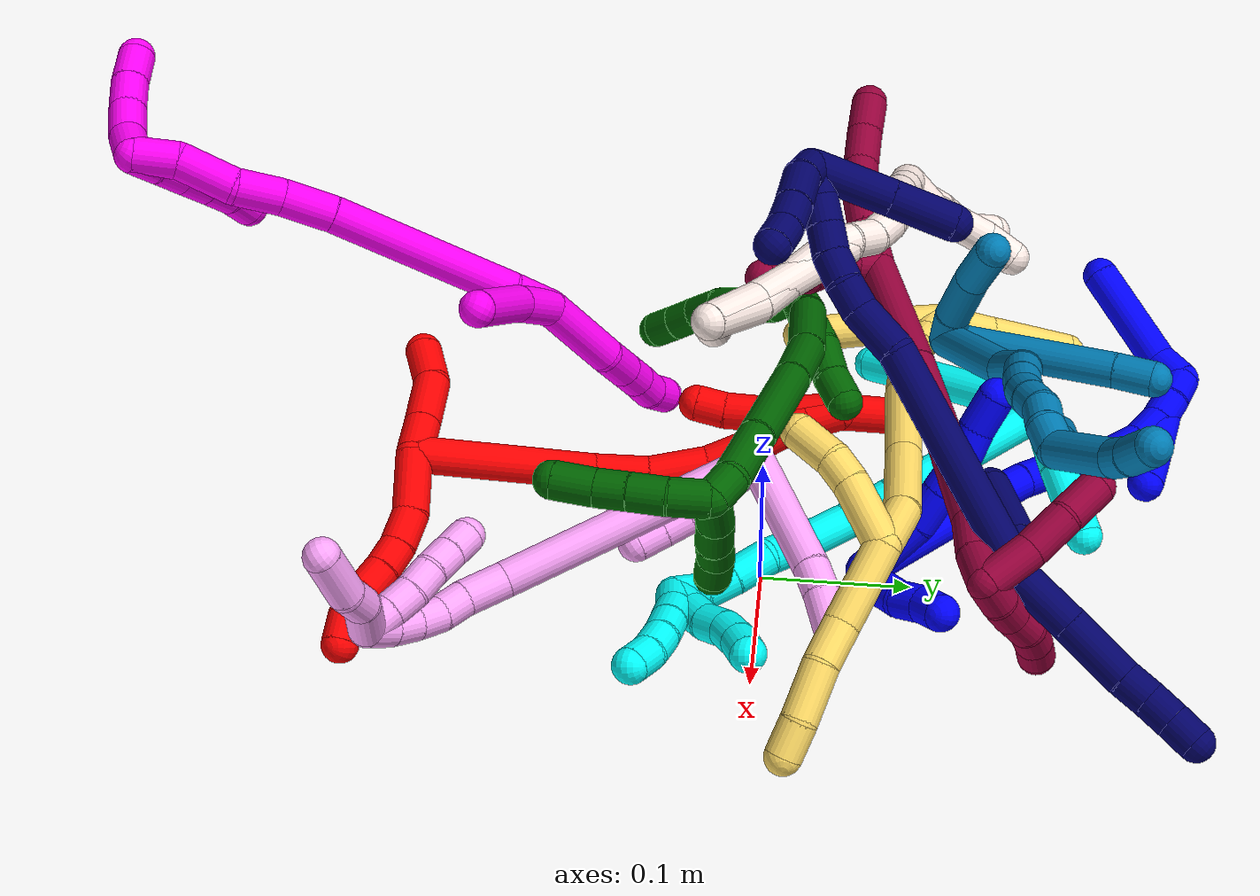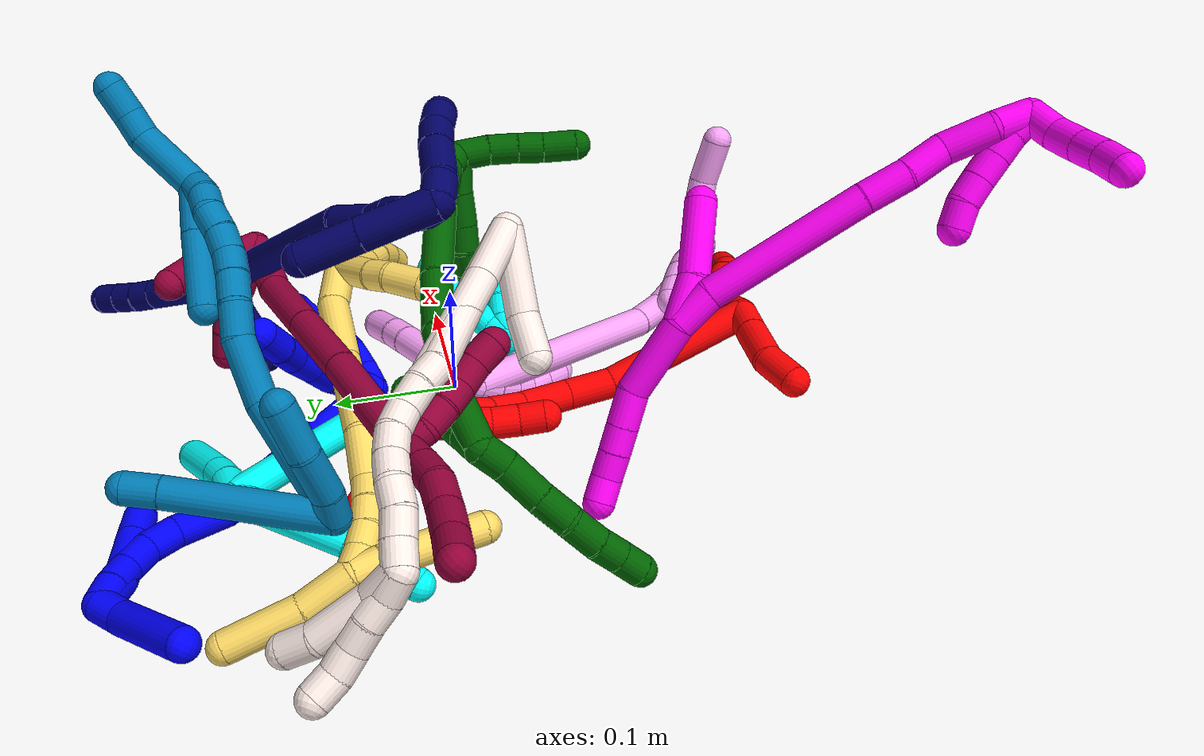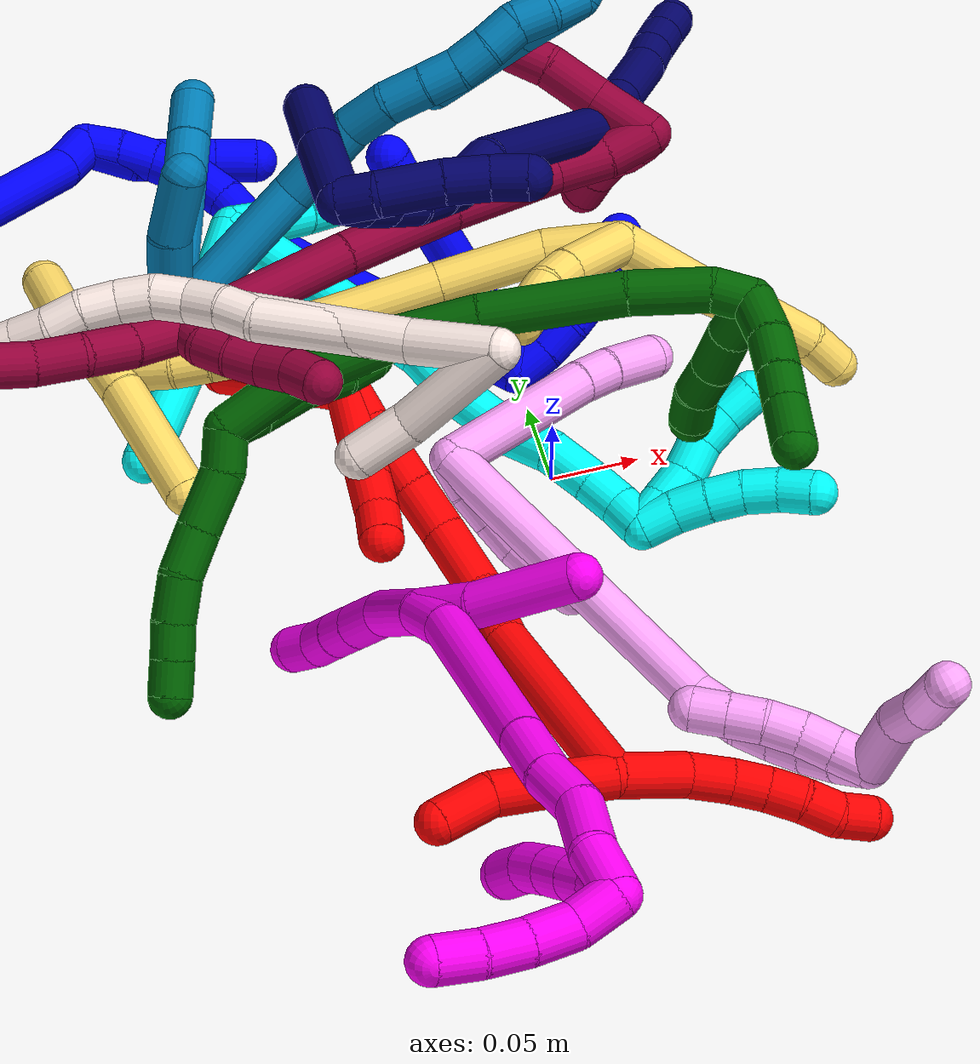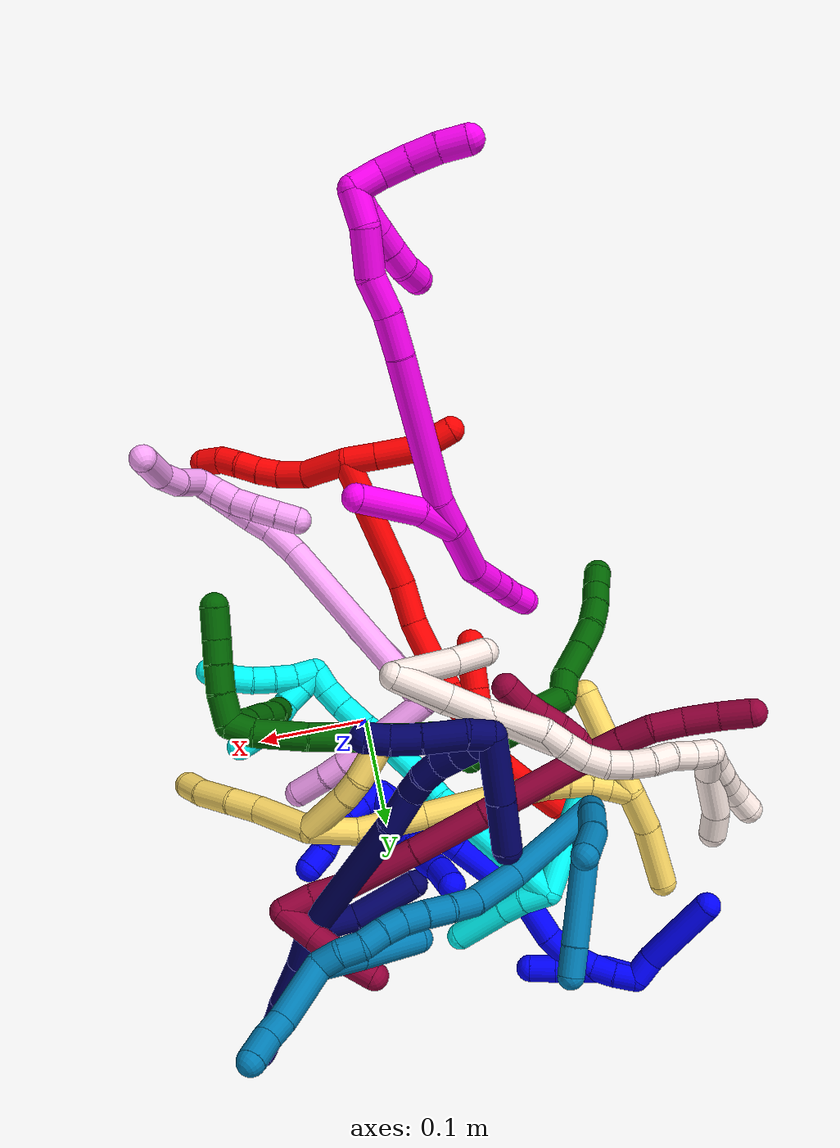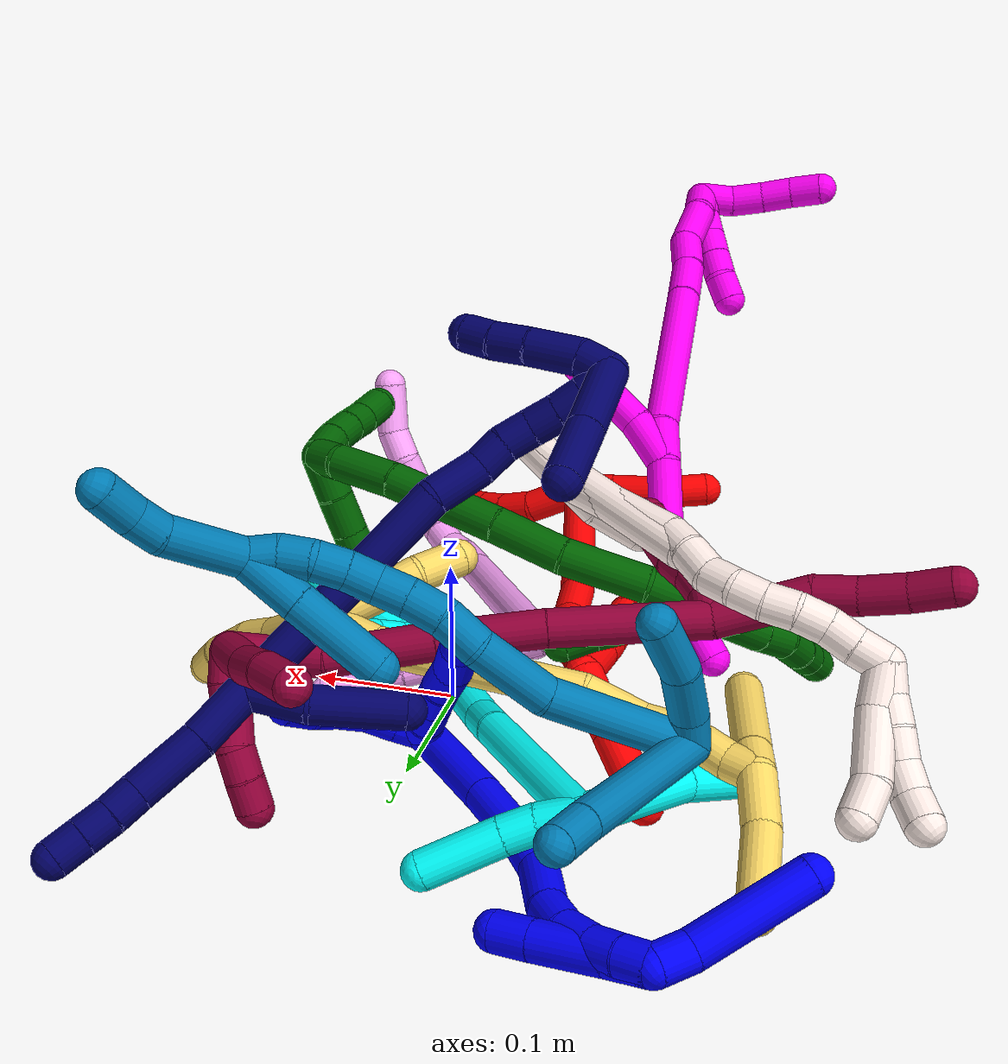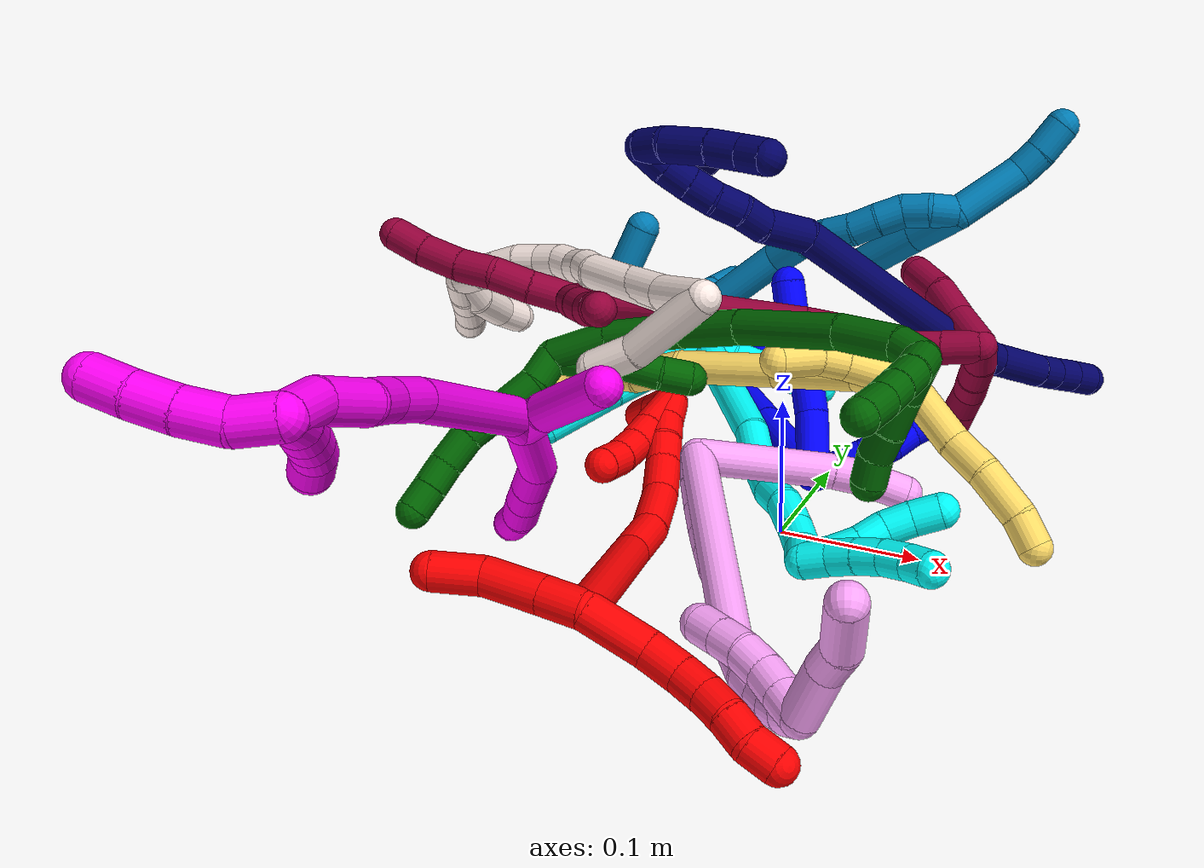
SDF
<sdf version="1.7">
 <world name="default">
  <plugin name="TubeGeneratorPlugin" filename="libtube_generator_plugin.so"/>
  <model name="photoneo_s_sensor">
   <static>1</static>
   <pose>0 0 2 1.57079 1.57079 3.14159</pose>
   <link name="link">
    <inertial><mass>0.1</mass></inertial>
    <sensor name="sensor" type="depth">
     <update_rate>30</update_rate>
     <camera>
      <horizontal_fov>1.22</horizontal_fov>
      <image><width>1920</width><height>1200</height><format>B8G8R8</format></image>
      <clip><near>0.1</near><far>4</far></clip>
      <depth_camera><output>points</output></depth_camera>
     </camera>
     <plugin name="camera_plugin" filename="libgazebo_ros_depth_camera.so">
      <baseline>0.2</baseline>
      <alwaysOn>1</alwaysOn>
      <updateRate>0.0</updateRate>
      <cameraName>camera_ir</cameraName>
      <imageTopicName>/camera/color/image_raw</imageTopicName>
      <cameraInfoTopicName>/camera/color/camera_info</cameraInfoTopicName>
      <depthImageTopicName>/camera/depth/image_raw</depthImageTopicName>
      <depthImageCameraInfoTopicName>/camera/depth/camera_info</depthImageCameraInfoTopicName>
      <pointCloudTopicName>/camera/depth/points</pointCloudTopicName>
      <frameName>fr_optical</frameName>
      <pointCloudCutoff>0.1</pointCloudCutoff>
      <pointCloudCutoffMax>2.0</pointCloudCutoffMax>
      <distortionK1>0</distortionK1>
      <distortionK2>0</distortionK2>
      <distortionK3>0</distortionK3>
      <distortionT1>0</distortionT1>
      <distortionT2>0</distortionT2>
      <CxPrime>0</CxPrime>
      <Cx>0</Cx>
      <Cy>0</Cy>
      <focalLength>0</focalLength>
      <hackBaseline>0</hackBaseline>
     </plugin>
    </sensor>
   </link>
  </model>
  <gravity>0 0 -9.8</gravity>
  <magnetic_field>6e-06 2.3e-05 -4.2e-05</magnetic_field>
  <atmosphere type="adiabatic"/>
  <physics name="default_physics" default="0" type="ode">
   <max_step_size>0.003</max_step_size>
   <real_time_factor>1</real_time_factor>
   <real_time_update_rate>1000</real_time_update_rate>
   <max_contacts>10000</max_contacts>
   <ode>
    <solver>
     <type>quick</type>
     <iters>100</iters>
     <sor>1.3</sor>
     <use_dynamic_moi_rescaling>0</use_dynamic_moi_rescaling>
    </solver>
    <constraints>
     <contact_max_correcting_vel>0</contact_max_correcting_vel>
     <contact_surface_layer>0.001</contact_surface_layer>
     <cfm>0</cfm>
     <erp>0.2</erp>
    </constraints>
   </ode>
  </physics>
  <scene><ambient>0.4 0.4 0.4 1</ambient><background>0.7 0.7 0.7 1</background><shadows>0</shadows></scene>
  <audio><device>default</device></audio>
  <spherical_coordinates>
   <surface_model>EARTH_WGS84</surface_model>
   <latitude_deg>0</latitude_deg>
   <longitude_deg>0</longitude_deg>
   <elevation>0</elevation>
   <heading_deg>0</heading_deg>
  </spherical_coordinates>
  <model name="bin">
   <static>1</static>
   <link name="bottom">
    <collision name="collision-bottom">
     <pose>0 0 -0.01 0 -0 0</pose>
     <geometry><box><size>0.8 0.6 0.02</size></box></geometry>
     <surface>
      <friction><ode><mu>100</mu><mu2>100</mu2></ode></friction>
      <contact><collide_bitmask>65535</collide_bitmask></contact>
     </surface>
    </collision>
   </link>
   <link name="west_wall">
    <collision name="collision-west_wall">
     <pose>-0.41 0 0.1 0 -0 0</pose>
     <geometry><box><size>0.02 0.6 0.2</size></box></geometry>
     <surface>
      <friction><ode><mu>100</mu><mu2>100</mu2></ode></friction>
      <contact><collide_bitmask>65535</collide_bitmask></contact>
     </surface>
    </collision>
   </link>
   <link name="east_wall">
    <collision name="collision-east_wall">
     <pose>0.41 0 0.1 0 -0 0</pose>
     <geometry><box><size>0.02 0.6 0.2</size></box></geometry>
     <surface>
      <friction><ode><mu>100</mu><mu2>100</mu2></ode></friction>
      <contact><collide_bitmask>65535</collide_bitmask></contact>
     </surface>
    </collision>
   </link>
   <link name="south_wall">
    <collision name="collision-south_wall">
     <pose>0 -0.31 0.1 0 -0 0</pose>
     <geometry><box><size>0.8 0.02 0.2</size></box></geometry>
     <surface>
      <friction><ode><mu>100</mu><mu2>100</mu2></ode></friction>
      <contact><collide_bitmask>65535</collide_bitmask></contact>
     </surface>
    </collision>
   </link>
   <link name="north_wall">
    <collision name="collision-north_wall">
     <pose>0 0.31 0.1 0 -0 0</pose>
     <geometry><box><size>0.8 0.02 0.2</size></box></geometry>
     <surface>
      <friction><ode><mu>100</mu><mu2>100</mu2></ode></friction>
      <contact><collide_bitmask>65535</collide_bitmask></contact>
     </surface>
    </collision>
   </link>
  </model>
  <model name="1">
   <static>0</static>
   <link name="1">
    <collision name="collision-cylinder-e_1_2_8">
     <pose>-0.022872 -0.003601 0.006556 0.502319 -1.25471 -0.367869</pose>
     <geometry><cylinder><radius>0.0125</radius><length>0.048128</length></cylinder></geometry>
     <surface>
      <friction><ode><mu>1.16</mu><mu2>1.16</mu2><slip1>0</slip1><slip2>0</slip2></ode></friction>
      <contact><ode><kp>1e+06</kp><kd>1</kd><max_vel>0</max_vel><min_depth>0.001</min_depth></ode></contact>
     </surface>
    </collision>
    <visual name="visual-cylinder-e_1_2_8">
     <pose>-0.022872 -0.003601 0.006556 0.502319 -1.25471 -0.367869</pose>
     <geometry><cylinder><radius>0.0125</radius><length>0.048128</length></cylinder></geometry>
     <material><ambient>0 0 1 1</ambient></material>
    </visual>
    <collision name="collision-cylinder-e_2_8_9">
     <pose>-0.059199 -0.006271 0.014776 -0.510667 -1.43005 0.445776</pose>
     <geometry><cylinder><radius>0.0125</radius><length>0.02718</length></cylinder></geometry>
     <surface>
      <friction><ode><mu>1.16</mu><mu2>1.16</mu2><slip1>0</slip1><slip2>0</slip2></ode></friction>
      <contact><ode><kp>1e+06</kp><kd>1</kd><max_vel>0</max_vel><min_depth>0.001</min_depth></ode></contact>
     </surface>
    </collision>
    <visual name="visual-cylinder-e_2_8_9">
     <pose>-0.059199 -0.006271 0.014776 -0.510667 -1.43005 0.445776</pose>
     <geometry><cylinder><radius>0.0125</radius><length>0.02718</length></cylinder></geometry>
     <material><ambient>0 0 1 1</ambient></material>
    </visual>
    <collision name="collision-cylinder-e_3_9_10">
     <pose>-0.085265 -0.004451 0.018274 -0.450809 -1.41054 0.385574</pose>
     <geometry><cylinder><radius>0.0125</radius><length>0.025549</length></cylinder></geometry>
     <surface>
      <friction><ode><mu>1.16</mu><mu2>1.16</mu2><slip1>0</slip1><slip2>0</slip2></ode></friction>
      <contact><ode><kp>1e+06</kp><kd>1</kd><max_vel>0</max_vel><min_depth>0.001</min_depth></ode></contact>
     </surface>
    </collision>
    <visual name="visual-cylinder-e_3_9_10">
     <pose>-0.085265 -0.004451 0.018274 -0.450809 -1.41054 0.385574</pose>
     <geometry><cylinder><radius>0.0125</radius><length>0.025549</length></cylinder></geometry>
     <material><ambient>0 0 1 1</ambient></material>
    </visual>
    <collision name="collision-cylinder-e_4_10_11">
     <pose>-0.109129 -0.000798 0.021444 -1.12076 -1.30441 0.893735</pose>
     <geometry><cylinder><radius>0.0125</radius><length>0.023328</length></cylinder></geometry>
     <surface>
      <friction><ode><mu>1.16</mu><mu2>1.16</mu2><slip1>0</slip1><slip2>0</slip2></ode></friction>
      <contact><ode><kp>1e+06</kp><kd>1</kd><max_vel>0</max_vel><min_depth>0.001</min_depth></ode></contact>
     </surface>
    </collision>
    <visual name="visual-cylinder-e_4_10_11">
     <pose>-0.109129 -0.000798 0.021444 -1.12076 -1.30441 0.893735</pose>
     <geometry><cylinder><radius>0.0125</radius><length>0.023328</length></cylinder></geometry>
     <material><ambient>0 0 1 1</ambient></material>
    </visual>
    <collision name="collision-cylinder-e_5_11_6">
     <pose>-0.133223 0.003086 0.023448 -1.03289 -1.46966 0.948207</pose>
     <geometry><cylinder><radius>0.0125</radius><length>0.025815</length></cylinder></geometry>
     <surface>
      <friction><ode><mu>1.16</mu><mu2>1.16</mu2><slip1>0</slip1><slip2>0</slip2></ode></friction>
      <contact><ode><kp>1e+06</kp><kd>1</kd><max_vel>0</max_vel><min_depth>0.001</min_depth></ode></contact>
     </surface>
    </collision>
    <visual name="visual-cylinder-e_5_11_6">
     <pose>-0.133223 0.003086 0.023448 -1.03289 -1.46966 0.948207</pose>
     <geometry><cylinder><radius>0.0125</radius><length>0.025815</length></cylinder></geometry>
     <material><ambient>0 0 1 1</ambient></material>
    </visual>
    <collision name="collision-cylinder-e_1_2_12">
     <pose>-0.002336 -0.007349 -0.006367 2.28468 -0.235781 -0.50744</pose>
     <geometry><cylinder><radius>0.0125</radius><length>0.02</length></cylinder></geometry>
     <surface>
      <friction><ode><mu>1.16</mu><mu2>1.16</mu2><slip1>0</slip1><slip2>0</slip2></ode></friction>
      <contact><ode><kp>1e+06</kp><kd>1</kd><max_vel>0</max_vel><min_depth>0.001</min_depth></ode></contact>
     </surface>
    </collision>
    <visual name="visual-cylinder-e_1_2_12">
     <pose>-0.002336 -0.007349 -0.006367 2.28468 -0.235781 -0.50744</pose>
     <geometry><cylinder><radius>0.0125</radius><length>0.02</length></cylinder></geometry>
     <material><ambient>0 0 1 1</ambient></material>
    </visual>
    <collision name="collision-cylinder-e_2_12_13">
     <pose>-0.008521 -0.021924 -0.018476 2.24234 -0.395122 -0.786376</pose>
     <geometry><cylinder><radius>0.0125</radius><length>0.02</length></cylinder></geometry>
     <surface>
      <friction><ode><mu>1.16</mu><mu2>1.16</mu2><slip1>0</slip1><slip2>0</slip2></ode></friction>
      <contact><ode><kp>1e+06</kp><kd>1</kd><max_vel>0</max_vel><min_depth>0.001</min_depth></ode></contact>
     </surface>
    </collision>
    <visual name="visual-cylinder-e_2_12_13">
     <pose>-0.008521 -0.021924 -0.018476 2.24234 -0.395122 -0.786376</pose>
     <geometry><cylinder><radius>0.0125</radius><length>0.02</length></cylinder></geometry>
     <material><ambient>0 0 1 1</ambient></material>
    </visual>
    <collision name="collision-cylinder-e_3_13_14">
     <pose>-0.015911 -0.037622 -0.028176 2.00777 -0.361906 -0.559686</pose>
     <geometry><cylinder><radius>0.0125</radius><length>0.02</length></cylinder></geometry>
     <surface>
      <friction><ode><mu>1.16</mu><mu2>1.16</mu2><slip1>0</slip1><slip2>0</slip2></ode></friction>
      <contact><ode><kp>1e+06</kp><kd>1</kd><max_vel>0</max_vel><min_depth>0.001</min_depth></ode></contact>
     </surface>
    </collision>
    <visual name="visual-cylinder-e_3_13_14">
     <pose>-0.015911 -0.037622 -0.028176 2.00777 -0.361906 -0.559686</pose>
     <geometry><cylinder><radius>0.0125</radius><length>0.02</length></cylinder></geometry>
     <material><ambient>0 0 1 1</ambient></material>
    </visual>
    <collision name="collision-cylinder-e_4_14_15">
     <pose>-0.02488 -0.054424 -0.033217 1.70012 -0.573868 -0.648185</pose>
     <geometry><cylinder><radius>0.0125</radius><length>0.02</length></cylinder></geometry>
     <surface>
      <friction><ode><mu>1.16</mu><mu2>1.16</mu2><slip1>0</slip1><slip2>0</slip2></ode></friction>
      <contact><ode><kp>1e+06</kp><kd>1</kd><max_vel>0</max_vel><min_depth>0.001</min_depth></ode></contact>
     </surface>
    </collision>
    <visual name="visual-cylinder-e_4_14_15">
     <pose>-0.02488 -0.054424 -0.033217 1.70012 -0.573868 -0.648185</pose>
     <geometry><cylinder><radius>0.0125</radius><length>0.02</length></cylinder></geometry>
     <material><ambient>0 0 1 1</ambient></material>
    </visual>
    <collision name="collision-cylinder-e_5_15_5">
     <pose>-0.034593 -0.070962 -0.038075 2.00176 -0.442634 -0.675306</pose>
     <geometry><cylinder><radius>0.0125</radius><length>0.02</length></cylinder></geometry>
     <surface>
      <friction><ode><mu>1.16</mu><mu2>1.16</mu2><slip1>0</slip1><slip2>0</slip2></ode></friction>
      <contact><ode><kp>1e+06</kp><kd>1</kd><max_vel>0</max_vel><min_depth>0.001</min_depth></ode></contact>
     </surface>
    </collision>
    <visual name="visual-cylinder-e_5_15_5">
     <pose>-0.034593 -0.070962 -0.038075 2.00176 -0.442634 -0.675306</pose>
     <geometry><cylinder><radius>0.0125</radius><length>0.02</length></cylinder></geometry>
     <material><ambient>0 0 1 1</ambient></material>
    </visual>
    <collision name="collision-cylinder-e_1_2_16">
     <pose>-0.023474 -0.001291 0.03821 0.033766 -0.550652 -0.00954</pose>
     <geometry><cylinder><radius>0.0125</radius><length>0.089726</length></cylinder></geometry>
     <surface>
      <friction><ode><mu>1.16</mu><mu2>1.16</mu2><slip1>0</slip1><slip2>0</slip2></ode></friction>
      <contact><ode><kp>1e+06</kp><kd>1</kd><max_vel>0</max_vel><min_depth>0.001</min_depth></ode></contact>
     </surface>
    </collision>
    <visual name="visual-cylinder-e_1_2_16">
     <pose>-0.023474 -0.001291 0.03821 0.033766 -0.550652 -0.00954</pose>
     <geometry><cylinder><radius>0.0125</radius><length>0.089726</length></cylinder></geometry>
     <material><ambient>0 0 1 1</ambient></material>
    </visual>
    <collision name="collision-cylinder-e_2_16_17">
     <pose>-0.059884 -0.004083 0.098946 0.066585 -0.520313 -0.01773</pose>
     <geometry><cylinder><radius>0.0125</radius><length>0.052039</length></cylinder></geometry>
     <surface>
      <friction><ode><mu>1.16</mu><mu2>1.16</mu2><slip1>0</slip1><slip2>0</slip2></ode></friction>
      <contact><ode><kp>1e+06</kp><kd>1</kd><max_vel>0</max_vel><min_depth>0.001</min_depth></ode></contact>
     </surface>
    </collision>
    <visual name="visual-cylinder-e_2_16_17">
     <pose>-0.059884 -0.004083 0.098946 0.066585 -0.520313 -0.01773</pose>
     <geometry><cylinder><radius>0.0125</radius><length>0.052039</length></cylinder></geometry>
     <material><ambient>0 0 1 1</ambient></material>
    </visual>
    <collision name="collision-cylinder-e_3_17_18">
     <pose>-0.078561 -0.007548 0.133405 0.163014 -0.443194 -0.036804</pose>
     <geometry><cylinder><radius>0.0125</radius><length>0.026774</length></cylinder></geometry>
     <surface>
      <friction><ode><mu>1.16</mu><mu2>1.16</mu2><slip1>0</slip1><slip2>0</slip2></ode></friction>
      <contact><ode><kp>1e+06</kp><kd>1</kd><max_vel>0</max_vel><min_depth>0.001</min_depth></ode></contact>
     </surface>
    </collision>
    <visual name="visual-cylinder-e_3_17_18">
     <pose>-0.078561 -0.007548 0.133405 0.163014 -0.443194 -0.036804</pose>
     <geometry><cylinder><radius>0.0125</radius><length>0.026774</length></cylinder></geometry>
     <material><ambient>0 0 1 1</ambient></material>
    </visual>
    <collision name="collision-cylinder-e_4_18_19">
     <pose>-0.095921 -0.017227 0.160375 0.474126 -0.602295 -0.149802</pose>
     <geometry><cylinder><radius>0.0125</radius><length>0.041019</length></cylinder></geometry>
     <surface>
      <friction><ode><mu>1.16</mu><mu2>1.16</mu2><slip1>0</slip1><slip2>0</slip2></ode></friction>
      <contact><ode><kp>1e+06</kp><kd>1</kd><max_vel>0</max_vel><min_depth>0.001</min_depth></ode></contact>
     </surface>
    </collision>
    <visual name="visual-cylinder-e_4_18_19">
     <pose>-0.095921 -0.017227 0.160375 0.474126 -0.602295 -0.149802</pose>
     <geometry><cylinder><radius>0.0125</radius><length>0.041019</length></cylinder></geometry>
     <material><ambient>0 0 1 1</ambient></material>
    </visual>
    <collision name="collision-cylinder-e_5_19_20">
     <pose>-0.115251 -0.026581 0.185381 0.162814 -0.651877 -0.055138</pose>
     <geometry><cylinder><radius>0.0125</radius><length>0.025418</length></cylinder></geometry>
     <surface>
      <friction><ode><mu>1.16</mu><mu2>1.16</mu2><slip1>0</slip1><slip2>0</slip2></ode></friction>
      <contact><ode><kp>1e+06</kp><kd>1</kd><max_vel>0</max_vel><min_depth>0.001</min_depth></ode></contact>
     </surface>
    </collision>
    <visual name="visual-cylinder-e_5_19_20">
     <pose>-0.115251 -0.026581 0.185381 0.162814 -0.651877 -0.055138</pose>
     <geometry><cylinder><radius>0.0125</radius><length>0.025418</length></cylinder></geometry>
     <material><ambient>0 0 1 1</ambient></material>
    </visual>
    <collision name="collision-cylinder-e_6_20_21">
     <pose>-0.129694 -0.026132 0.204962 -0.213765 -0.600263 0.066385</pose>
     <geometry><cylinder><radius>0.0125</radius><length>0.023838</length></cylinder></geometry>
     <surface>
      <friction><ode><mu>1.16</mu><mu2>1.16</mu2><slip1>0</slip1><slip2>0</slip2></ode></friction>
      <contact><ode><kp>1e+06</kp><kd>1</kd><max_vel>0</max_vel><min_depth>0.001</min_depth></ode></contact>
     </surface>
    </collision>
    <visual name="visual-cylinder-e_6_20_21">
     <pose>-0.129694 -0.026132 0.204962 -0.213765 -0.600263 0.066385</pose>
     <geometry><cylinder><radius>0.0125</radius><length>0.023838</length></cylinder></geometry>
     <material><ambient>0 0 1 1</ambient></material>
    </visual>
    <collision name="collision-cylinder-e_7_21_22">
     <pose>-0.142559 -0.020499 0.222368 -0.427005 -0.621507 0.139034</pose>
     <geometry><cylinder><radius>0.0125</radius><length>0.021067</length></cylinder></geometry>
     <surface>
      <friction><ode><mu>1.16</mu><mu2>1.16</mu2><slip1>0</slip1><slip2>0</slip2></ode></friction>
      <contact><ode><kp>1e+06</kp><kd>1</kd><max_vel>0</max_vel><min_depth>0.001</min_depth></ode></contact>
     </surface>
    </collision>
    <visual name="visual-cylinder-e_7_21_22">
     <pose>-0.142559 -0.020499 0.222368 -0.427005 -0.621507 0.139034</pose>
     <geometry><cylinder><radius>0.0125</radius><length>0.021067</length></cylinder></geometry>
     <material><ambient>0 0 1 1</ambient></material>
    </visual>
    <collision name="collision-cylinder-e_8_22_1">
     <pose>-0.153676 -0.012653 0.23777 -0.514536 -0.518362 0.139293</pose>
     <geometry><cylinder><radius>0.0125</radius><length>0.020118</length></cylinder></geometry>
     <surface>
      <friction><ode><mu>1.16</mu><mu2>1.16</mu2><slip1>0</slip1><slip2>0</slip2></ode></friction>
      <contact><ode><kp>1e+06</kp><kd>1</kd><max_vel>0</max_vel><min_depth>0.001</min_depth></ode></contact>
     </surface>
    </collision>
    <visual name="visual-cylinder-e_8_22_1">
     <pose>-0.153676 -0.012653 0.23777 -0.514536 -0.518362 0.139293</pose>
     <geometry><cylinder><radius>0.0125</radius><length>0.020118</length></cylinder></geometry>
     <material><ambient>0 0 1 1</ambient></material>
    </visual>
    <collision name="collision-cylinder-e_1_1_23">
     <pose>-0.157863 0.003049 0.246574 -1.46612 0.06947 -0.062558</pose>
     <geometry><cylinder><radius>0.0125</radius><length>0.022984</length></cylinder></geometry>
     <surface>
      <friction><ode><mu>1.16</mu><mu2>1.16</mu2><slip1>0</slip1><slip2>0</slip2></ode></friction>
      <contact><ode><kp>1e+06</kp><kd>1</kd><max_vel>0</max_vel><min_depth>0.001</min_depth></ode></contact>
     </surface>
    </collision>
    <visual name="visual-cylinder-e_1_1_23">
     <pose>-0.157863 0.003049 0.246574 -1.46612 0.06947 -0.062558</pose>
     <geometry><cylinder><radius>0.0125</radius><length>0.022984</length></cylinder></geometry>
     <material><ambient>0 0 1 1</ambient></material>
    </visual>
    <collision name="collision-cylinder-e_2_23_4">
     <pose>-0.165424 0.052026 0.248799 -1.54345 -0.218825 0.212966</pose>
     <geometry><cylinder><radius>0.0125</radius><length>0.077016</length></cylinder></geometry>
     <surface>
      <friction><ode><mu>1.16</mu><mu2>1.16</mu2><slip1>0</slip1><slip2>0</slip2></ode></friction>
      <contact><ode><kp>1e+06</kp><kd>1</kd><max_vel>0</max_vel><min_depth>0.001</min_depth></ode></contact>
     </surface>
    </collision>
    <visual name="visual-cylinder-e_2_23_4">
     <pose>-0.165424 0.052026 0.248799 -1.54345 -0.218825 0.212966</pose>
     <geometry><cylinder><radius>0.0125</radius><length>0.077016</length></cylinder></geometry>
     <material><ambient>0 0 1 1</ambient></material>
    </visual>
    <collision name="collision-cylinder-e_1_1_24">
     <pose>-0.149341 -0.014307 0.234831 2.62755 0.655871 1.82604</pose>
     <geometry><cylinder><radius>0.0125</radius><length>0.030561</length></cylinder></geometry>
     <surface>
      <friction><ode><mu>1.16</mu><mu2>1.16</mu2><slip1>0</slip1><slip2>0</slip2></ode></friction>
      <contact><ode><kp>1e+06</kp><kd>1</kd><max_vel>0</max_vel><min_depth>0.001</min_depth></ode></contact>
     </surface>
    </collision>
    <visual name="visual-cylinder-e_1_1_24">
     <pose>-0.149341 -0.014307 0.234831 2.62755 0.655871 1.82604</pose>
     <geometry><cylinder><radius>0.0125</radius><length>0.030561</length></cylinder></geometry>
     <material><ambient>0 0 1 1</ambient></material>
    </visual>
    <collision name="collision-cylinder-e_2_24_25">
     <pose>-0.13101 -0.033146 0.207947 2.47386 0.40876 1.07729</pose>
     <geometry><cylinder><radius>0.0125</radius><length>0.045351</length></cylinder></geometry>
     <surface>
      <friction><ode><mu>1.16</mu><mu2>1.16</mu2><slip1>0</slip1><slip2>0</slip2></ode></friction>
      <contact><ode><kp>1e+06</kp><kd>1</kd><max_vel>0</max_vel><min_depth>0.001</min_depth></ode></contact>
     </surface>
    </collision>
    <visual name="visual-cylinder-e_2_24_25">
     <pose>-0.13101 -0.033146 0.207947 2.47386 0.40876 1.07729</pose>
     <geometry><cylinder><radius>0.0125</radius><length>0.045351</length></cylinder></geometry>
     <material><ambient>0 0 1 1</ambient></material>
    </visual>
    <collision name="collision-cylinder-e_3_25_3">
     <pose>-0.11722 -0.052637 0.182744 2.50102 0.407843 1.11494</pose>
     <geometry><cylinder><radius>0.0125</radius><length>0.024088</length></cylinder></geometry>
     <surface>
      <friction><ode><mu>1.16</mu><mu2>1.16</mu2><slip1>0</slip1><slip2>0</slip2></ode></friction>
      <contact><ode><kp>1e+06</kp><kd>1</kd><max_vel>0</max_vel><min_depth>0.001</min_depth></ode></contact>
     </surface>
    </collision>
    <visual name="visual-cylinder-e_3_25_3">
     <pose>-0.11722 -0.052637 0.182744 2.50102 0.407843 1.11494</pose>
     <geometry><cylinder><radius>0.0125</radius><length>0.024088</length></cylinder></geometry>
     <material><ambient>0 0 1 1</ambient></material>
    </visual>
    <collision name="collision-sphere-3">
     <pose>-0.112443 -0.059245 0.17388 0 -0 0</pose>
     <geometry><sphere><radius>0.0125</radius></sphere></geometry>
     <surface>
      <friction><ode><mu>1.16</mu><mu2>1.16</mu2><slip1>0</slip1><slip2>0</slip2></ode></friction>
      <contact><ode><kp>1e+06</kp><kd>1</kd><max_vel>0</max_vel><min_depth>0.001</min_depth></ode></contact>
     </surface>
    </collision>
    <visual name="visual-sphere-3">
     <pose>-0.112443 -0.059245 0.17388 0 -0 0</pose>
     <geometry><sphere><radius>0.0125</radius></sphere></geometry>
     <material><ambient>0 0 1 1</ambient></material>
    </visual>
    <collision name="collision-sphere-25">
     <pose>-0.121997 -0.04603 0.191609 0 -0 0</pose>
     <geometry><sphere><radius>0.0125</radius></sphere></geometry>
     <surface>
      <friction><ode><mu>1.16</mu><mu2>1.16</mu2><slip1>0</slip1><slip2>0</slip2></ode></friction>
      <contact><ode><kp>1e+06</kp><kd>1</kd><max_vel>0</max_vel><min_depth>0.001</min_depth></ode></contact>
     </surface>
    </collision>
    <visual name="visual-sphere-25">
     <pose>-0.121997 -0.04603 0.191609 0 -0 0</pose>
     <geometry><sphere><radius>0.0125</radius></sphere></geometry>
     <material><ambient>0 0 1 1</ambient></material>
    </visual>
    <collision name="collision-sphere-24">
     <pose>-0.140022 -0.020262 0.224285 0 -0 0</pose>
     <geometry><sphere><radius>0.0125</radius></sphere></geometry>
     <surface>
      <friction><ode><mu>1.16</mu><mu2>1.16</mu2><slip1>0</slip1><slip2>0</slip2></ode></friction>
      <contact><ode><kp>1e+06</kp><kd>1</kd><max_vel>0</max_vel><min_depth>0.001</min_depth></ode></contact>
     </surface>
    </collision>
    <visual name="visual-sphere-24">
     <pose>-0.140022 -0.020262 0.224285 0 -0 0</pose>
     <geometry><sphere><radius>0.0125</radius></sphere></geometry>
     <material><ambient>0 0 1 1</ambient></material>
    </visual>
    <collision name="collision-sphere-4">
     <pose>-0.173784 0.089602 0.249827 0 -0 0</pose>
     <geometry><sphere><radius>0.0125</radius></sphere></geometry>
     <surface>
      <friction><ode><mu>1.16</mu><mu2>1.16</mu2><slip1>0</slip1><slip2>0</slip2></ode></friction>
      <contact><ode><kp>1e+06</kp><kd>1</kd><max_vel>0</max_vel><min_depth>0.001</min_depth></ode></contact>
     </surface>
    </collision>
    <visual name="visual-sphere-4">
     <pose>-0.173784 0.089602 0.249827 0 -0 0</pose>
     <geometry><sphere><radius>0.0125</radius></sphere></geometry>
     <material><ambient>0 0 1 1</ambient></material>
    </visual>
    <collision name="collision-sphere-23">
     <pose>-0.157065 0.014451 0.247771 0 -0 0</pose>
     <geometry><sphere><radius>0.0125</radius></sphere></geometry>
     <surface>
      <friction><ode><mu>1.16</mu><mu2>1.16</mu2><slip1>0</slip1><slip2>0</slip2></ode></friction>
      <contact><ode><kp>1e+06</kp><kd>1</kd><max_vel>0</max_vel><min_depth>0.001</min_depth></ode></contact>
     </surface>
    </collision>
    <visual name="visual-sphere-23">
     <pose>-0.157065 0.014451 0.247771 0 -0 0</pose>
     <geometry><sphere><radius>0.0125</radius></sphere></geometry>
     <material><ambient>0 0 1 1</ambient></material>
    </visual>
    <collision name="collision-sphere-1">
     <pose>-0.15866 -0.008353 0.245376 0 -0 0</pose>
     <geometry><sphere><radius>0.0125</radius></sphere></geometry>
     <surface>
      <friction><ode><mu>1.16</mu><mu2>1.16</mu2><slip1>0</slip1><slip2>0</slip2></ode></friction>
      <contact><ode><kp>1e+06</kp><kd>1</kd><max_vel>0</max_vel><min_depth>0.001</min_depth></ode></contact>
     </surface>
    </collision>
    <visual name="visual-sphere-1">
     <pose>-0.15866 -0.008353 0.245376 0 -0 0</pose>
     <geometry><sphere><radius>0.0125</radius></sphere></geometry>
     <material><ambient>0 0 1 1</ambient></material>
    </visual>
    <collision name="collision-sphere-22">
     <pose>-0.148693 -0.016953 0.230163 0 -0 0</pose>
     <geometry><sphere><radius>0.0125</radius></sphere></geometry>
     <surface>
      <friction><ode><mu>1.16</mu><mu2>1.16</mu2><slip1>0</slip1><slip2>0</slip2></ode></friction>
      <contact><ode><kp>1e+06</kp><kd>1</kd><max_vel>0</max_vel><min_depth>0.001</min_depth></ode></contact>
     </surface>
    </collision>
    <visual name="visual-sphere-22">
     <pose>-0.148693 -0.016953 0.230163 0 -0 0</pose>
     <geometry><sphere><radius>0.0125</radius></sphere></geometry>
     <material><ambient>0 0 1 1</ambient></material>
    </visual>
    <collision name="collision-sphere-21">
     <pose>-0.136426 -0.024046 0.214574 0 -0 0</pose>
     <geometry><sphere><radius>0.0125</radius></sphere></geometry>
     <surface>
      <friction><ode><mu>1.16</mu><mu2>1.16</mu2><slip1>0</slip1><slip2>0</slip2></ode></friction>
      <contact><ode><kp>1e+06</kp><kd>1</kd><max_vel>0</max_vel><min_depth>0.001</min_depth></ode></contact>
     </surface>
    </collision>
    <visual name="visual-sphere-21">
     <pose>-0.136426 -0.024046 0.214574 0 -0 0</pose>
     <geometry><sphere><radius>0.0125</radius></sphere></geometry>
     <material><ambient>0 0 1 1</ambient></material>
    </visual>
    <collision name="collision-sphere-6">
     <pose>-0.146065 0.004205 0.024115 0 -0 0</pose>
     <geometry><sphere><radius>0.0125</radius></sphere></geometry>
     <surface>
      <friction><ode><mu>1.16</mu><mu2>1.16</mu2><slip1>0</slip1><slip2>0</slip2></ode></friction>
      <contact><ode><kp>1e+06</kp><kd>1</kd><max_vel>0</max_vel><min_depth>0.001</min_depth></ode></contact>
     </surface>
    </collision>
    <visual name="visual-sphere-6">
     <pose>-0.146065 0.004205 0.024115 0 -0 0</pose>
     <geometry><sphere><radius>0.0125</radius></sphere></geometry>
     <material><ambient>0 0 1 1</ambient></material>
    </visual>
    <collision name="collision-sphere-11">
     <pose>-0.120382 0.001967 0.02278 0 -0 0</pose>
     <geometry><sphere><radius>0.0125</radius></sphere></geometry>
     <surface>
      <friction><ode><mu>1.16</mu><mu2>1.16</mu2><slip1>0</slip1><slip2>0</slip2></ode></friction>
      <contact><ode><kp>1e+06</kp><kd>1</kd><max_vel>0</max_vel><min_depth>0.001</min_depth></ode></contact>
     </surface>
    </collision>
    <visual name="visual-sphere-11">
     <pose>-0.120382 0.001967 0.02278 0 -0 0</pose>
     <geometry><sphere><radius>0.0125</radius></sphere></geometry>
     <material><ambient>0 0 1 1</ambient></material>
    </visual>
    <collision name="collision-sphere-10">
     <pose>-0.097876 -0.003563 0.020109 0 -0 0</pose>
     <geometry><sphere><radius>0.0125</radius></sphere></geometry>
     <surface>
      <friction><ode><mu>1.16</mu><mu2>1.16</mu2><slip1>0</slip1><slip2>0</slip2></ode></friction>
      <contact><ode><kp>1e+06</kp><kd>1</kd><max_vel>0</max_vel><min_depth>0.001</min_depth></ode></contact>
     </surface>
    </collision>
    <visual name="visual-sphere-10">
     <pose>-0.097876 -0.003563 0.020109 0 -0 0</pose>
     <geometry><sphere><radius>0.0125</radius></sphere></geometry>
     <material><ambient>0 0 1 1</ambient></material>
    </visual>
    <collision name="collision-sphere-9">
     <pose>-0.072655 -0.005339 0.016439 0 -0 0</pose>
     <geometry><sphere><radius>0.0125</radius></sphere></geometry>
     <surface>
      <friction><ode><mu>1.16</mu><mu2>1.16</mu2><slip1>0</slip1><slip2>0</slip2></ode></friction>
      <contact><ode><kp>1e+06</kp><kd>1</kd><max_vel>0</max_vel><min_depth>0.001</min_depth></ode></contact>
     </surface>
    </collision>
    <visual name="visual-sphere-9">
     <pose>-0.072655 -0.005339 0.016439 0 -0 0</pose>
     <geometry><sphere><radius>0.0125</radius></sphere></geometry>
     <material><ambient>0 0 1 1</ambient></material>
    </visual>
    <collision name="collision-sphere-2">
     <geometry><sphere><radius>0.0125</radius></sphere></geometry>
     <surface>
      <friction><ode><mu>1.16</mu><mu2>1.16</mu2><slip1>0</slip1><slip2>0</slip2></ode></friction>
      <contact><ode><kp>1e+06</kp><kd>1</kd><max_vel>0</max_vel><min_depth>0.001</min_depth></ode></contact>
     </surface>
    </collision>
    <visual name="visual-sphere-2">
     <geometry><sphere><radius>0.0125</radius></sphere></geometry>
     <material><ambient>0 0 1 1</ambient></material>
    </visual>
    <collision name="collision-sphere-19">
     <pose>-0.10754 -0.024944 0.175412 0 -0 0</pose>
     <geometry><sphere><radius>0.0125</radius></sphere></geometry>
     <surface>
      <friction><ode><mu>1.16</mu><mu2>1.16</mu2><slip1>0</slip1><slip2>0</slip2></ode></friction>
      <contact><ode><kp>1e+06</kp><kd>1</kd><max_vel>0</max_vel><min_depth>0.001</min_depth></ode></contact>
     </surface>
    </collision>
    <visual name="visual-sphere-19">
     <pose>-0.10754 -0.024944 0.175412 0 -0 0</pose>
     <geometry><sphere><radius>0.0125</radius></sphere></geometry>
     <material><ambient>0 0 1 1</ambient></material>
    </visual>
    <collision name="collision-sphere-8">
     <pose>-0.045744 -0.007203 0.013112 0 -0 0</pose>
     <geometry><sphere><radius>0.0125</radius></sphere></geometry>
     <surface>
      <friction><ode><mu>1.16</mu><mu2>1.16</mu2><slip1>0</slip1><slip2>0</slip2></ode></friction>
      <contact><ode><kp>1e+06</kp><kd>1</kd><max_vel>0</max_vel><min_depth>0.001</min_depth></ode></contact>
     </surface>
    </collision>
    <visual name="visual-sphere-8">
     <pose>-0.045744 -0.007203 0.013112 0 -0 0</pose>
     <geometry><sphere><radius>0.0125</radius></sphere></geometry>
     <material><ambient>0 0 1 1</ambient></material>
    </visual>
    <collision name="collision-sphere-12">
     <pose>-0.004672 -0.014698 -0.012733 0 -0 0</pose>
     <geometry><sphere><radius>0.0125</radius></sphere></geometry>
     <surface>
      <friction><ode><mu>1.16</mu><mu2>1.16</mu2><slip1>0</slip1><slip2>0</slip2></ode></friction>
      <contact><ode><kp>1e+06</kp><kd>1</kd><max_vel>0</max_vel><min_depth>0.001</min_depth></ode></contact>
     </surface>
    </collision>
    <visual name="visual-sphere-12">
     <pose>-0.004672 -0.014698 -0.012733 0 -0 0</pose>
     <geometry><sphere><radius>0.0125</radius></sphere></geometry>
     <material><ambient>0 0 1 1</ambient></material>
    </visual>
    <collision name="collision-sphere-13">
     <pose>-0.01237 -0.029149 -0.024218 0 -0 0</pose>
     <geometry><sphere><radius>0.0125</radius></sphere></geometry>
     <surface>
      <friction><ode><mu>1.16</mu><mu2>1.16</mu2><slip1>0</slip1><slip2>0</slip2></ode></friction>
      <contact><ode><kp>1e+06</kp><kd>1</kd><max_vel>0</max_vel><min_depth>0.001</min_depth></ode></contact>
     </surface>
    </collision>
    <visual name="visual-sphere-13">
     <pose>-0.01237 -0.029149 -0.024218 0 -0 0</pose>
     <geometry><sphere><radius>0.0125</radius></sphere></geometry>
     <material><ambient>0 0 1 1</ambient></material>
    </visual>
    <collision name="collision-sphere-14">
     <pose>-0.019452 -0.046096 -0.032134 0 -0 0</pose>
     <geometry><sphere><radius>0.0125</radius></sphere></geometry>
     <surface>
      <friction><ode><mu>1.16</mu><mu2>1.16</mu2><slip1>0</slip1><slip2>0</slip2></ode></friction>
      <contact><ode><kp>1e+06</kp><kd>1</kd><max_vel>0</max_vel><min_depth>0.001</min_depth></ode></contact>
     </surface>
    </collision>
    <visual name="visual-sphere-14">
     <pose>-0.019452 -0.046096 -0.032134 0 -0 0</pose>
     <geometry><sphere><radius>0.0125</radius></sphere></geometry>
     <material><ambient>0 0 1 1</ambient></material>
    </visual>
    <collision name="collision-sphere-15">
     <pose>-0.030309 -0.062752 -0.0343 0 -0 0</pose>
     <geometry><sphere><radius>0.0125</radius></sphere></geometry>
     <surface>
      <friction><ode><mu>1.16</mu><mu2>1.16</mu2><slip1>0</slip1><slip2>0</slip2></ode></friction>
      <contact><ode><kp>1e+06</kp><kd>1</kd><max_vel>0</max_vel><min_depth>0.001</min_depth></ode></contact>
     </surface>
    </collision>
    <visual name="visual-sphere-15">
     <pose>-0.030309 -0.062752 -0.0343 0 -0 0</pose>
     <geometry><sphere><radius>0.0125</radius></sphere></geometry>
     <material><ambient>0 0 1 1</ambient></material>
    </visual>
    <collision name="collision-sphere-5">
     <pose>-0.038876 -0.079172 -0.04185 0 -0 0</pose>
     <geometry><sphere><radius>0.0125</radius></sphere></geometry>
     <surface>
      <friction><ode><mu>1.16</mu><mu2>1.16</mu2><slip1>0</slip1><slip2>0</slip2></ode></friction>
      <contact><ode><kp>1e+06</kp><kd>1</kd><max_vel>0</max_vel><min_depth>0.001</min_depth></ode></contact>
     </surface>
    </collision>
    <visual name="visual-sphere-5">
     <pose>-0.038876 -0.079172 -0.04185 0 -0 0</pose>
     <geometry><sphere><radius>0.0125</radius></sphere></geometry>
     <material><ambient>0 0 1 1</ambient></material>
    </visual>
    <collision name="collision-sphere-16">
     <pose>-0.046949 -0.002581 0.07642 0 -0 0</pose>
     <geometry><sphere><radius>0.0125</radius></sphere></geometry>
     <surface>
      <friction><ode><mu>1.16</mu><mu2>1.16</mu2><slip1>0</slip1><slip2>0</slip2></ode></friction>
      <contact><ode><kp>1e+06</kp><kd>1</kd><max_vel>0</max_vel><min_depth>0.001</min_depth></ode></contact>
     </surface>
    </collision>
    <visual name="visual-sphere-16">
     <pose>-0.046949 -0.002581 0.07642 0 -0 0</pose>
     <geometry><sphere><radius>0.0125</radius></sphere></geometry>
     <material><ambient>0 0 1 1</ambient></material>
    </visual>
    <collision name="collision-sphere-17">
     <pose>-0.07282 -0.005586 0.121472 0 -0 0</pose>
     <geometry><sphere><radius>0.0125</radius></sphere></geometry>
     <surface>
      <friction><ode><mu>1.16</mu><mu2>1.16</mu2><slip1>0</slip1><slip2>0</slip2></ode></friction>
      <contact><ode><kp>1e+06</kp><kd>1</kd><max_vel>0</max_vel><min_depth>0.001</min_depth></ode></contact>
     </surface>
    </collision>
    <visual name="visual-sphere-17">
     <pose>-0.07282 -0.005586 0.121472 0 -0 0</pose>
     <geometry><sphere><radius>0.0125</radius></sphere></geometry>
     <material><ambient>0 0 1 1</ambient></material>
    </visual>
    <collision name="collision-sphere-18">
     <pose>-0.084302 -0.009511 0.145339 0 -0 0</pose>
     <geometry><sphere><radius>0.0125</radius></sphere></geometry>
     <surface>
      <friction><ode><mu>1.16</mu><mu2>1.16</mu2><slip1>0</slip1><slip2>0</slip2></ode></friction>
      <contact><ode><kp>1e+06</kp><kd>1</kd><max_vel>0</max_vel><min_depth>0.001</min_depth></ode></contact>
     </surface>
    </collision>
    <visual name="visual-sphere-18">
     <pose>-0.084302 -0.009511 0.145339 0 -0 0</pose>
     <geometry><sphere><radius>0.0125</radius></sphere></geometry>
     <material><ambient>0 0 1 1</ambient></material>
    </visual>
    <collision name="collision-sphere-20">
     <pose>-0.122961 -0.028219 0.195351 0 -0 0</pose>
     <geometry><sphere><radius>0.0125</radius></sphere></geometry>
     <surface>
      <friction><ode><mu>1.16</mu><mu2>1.16</mu2><slip1>0</slip1><slip2>0</slip2></ode></friction>
      <contact><ode><kp>1e+06</kp><kd>1</kd><max_vel>0</max_vel><min_depth>0.001</min_depth></ode></contact>
     </surface>
    </collision>
    <visual name="visual-sphere-20">
     <pose>-0.122961 -0.028219 0.195351 0 -0 0</pose>
     <geometry><sphere><radius>0.0125</radius></sphere></geometry>
     <material><ambient>0 0 1 1</ambient></material>
    </visual>
    <inertial>
     <pose>-0.087563 -0.008794 0.111247 0 -0 0</pose>
     <mass>0.75</mass>
     <inertia>
      <ixx>0.000126</ixx>
      <ixy>0</ixy>
      <ixz>0</ixz>
      <iyy>0.000129</iyy>
      <iyz>0</iyz>
      <izz>6.4e-05</izz>
     </inertia>
    </inertial>
   </link>
   <pose>-0.001156 0.068717 0.012272 2.72484 1.01628 -1.13823</pose>
  </model>
  <model name="2">
   <static>0</static>
   <link name="2">
    <collision name="collision-cylinder-e_1_2_8">
     <pose>0.015666 0.012285 0.008926 -0.942449 0.801002 -0.424923</pose>
     <geometry><cylinder><radius>0.0125</radius><length>0.043635</length></cylinder></geometry>
     <surface>
      <friction><ode><mu>1.16</mu><mu2>1.16</mu2><slip1>0</slip1><slip2>0</slip2></ode></friction>
      <contact><ode><kp>1e+06</kp><kd>1</kd><max_vel>0</max_vel><min_depth>0.001</min_depth></ode></contact>
     </surface>
    </collision>
    <visual name="visual-cylinder-e_1_2_8">
     <pose>0.015666 0.012285 0.008926 -0.942449 0.801002 -0.424923</pose>
     <geometry><cylinder><radius>0.0125</radius><length>0.043635</length></cylinder></geometry>
     <material><ambient>1 0 0 1</ambient></material>
    </visual>
    <collision name="collision-cylinder-e_2_8_9">
     <pose>0.040262 0.029159 0.025952 -0.515534 0.764545 -0.211198</pose>
     <geometry><cylinder><radius>0.0125</radius><length>0.025801</length></cylinder></geometry>
     <surface>
      <friction><ode><mu>1.16</mu><mu2>1.16</mu2><slip1>0</slip1><slip2>0</slip2></ode></friction>
      <contact><ode><kp>1e+06</kp><kd>1</kd><max_vel>0</max_vel><min_depth>0.001</min_depth></ode></contact>
     </surface>
    </collision>
    <visual name="visual-cylinder-e_2_8_9">
     <pose>0.040262 0.029159 0.025952 -0.515534 0.764545 -0.211198</pose>
     <geometry><cylinder><radius>0.0125</radius><length>0.025801</length></cylinder></geometry>
     <material><ambient>1 0 0 1</ambient></material>
    </visual>
    <collision name="collision-cylinder-e_3_9_10">
     <pose>0.055711 0.035856 0.041525 -0.274807 0.698411 -0.100615</pose>
     <geometry><cylinder><radius>0.0125</radius><length>0.020278</length></cylinder></geometry>
     <surface>
      <friction><ode><mu>1.16</mu><mu2>1.16</mu2><slip1>0</slip1><slip2>0</slip2></ode></friction>
      <contact><ode><kp>1e+06</kp><kd>1</kd><max_vel>0</max_vel><min_depth>0.001</min_depth></ode></contact>
     </surface>
    </collision>
    <visual name="visual-cylinder-e_3_9_10">
     <pose>0.055711 0.035856 0.041525 -0.274807 0.698411 -0.100615</pose>
     <geometry><cylinder><radius>0.0125</radius><length>0.020278</length></cylinder></geometry>
     <material><ambient>1 0 0 1</ambient></material>
    </visual>
    <collision name="collision-cylinder-e_4_10_11">
     <pose>0.06865 0.038907 0.056621 -0.123187 0.696205 -0.044751</pose>
     <geometry><cylinder><radius>0.0125</radius><length>0.02002</length></cylinder></geometry>
     <surface>
      <friction><ode><mu>1.16</mu><mu2>1.16</mu2><slip1>0</slip1><slip2>0</slip2></ode></friction>
      <contact><ode><kp>1e+06</kp><kd>1</kd><max_vel>0</max_vel><min_depth>0.001</min_depth></ode></contact>
     </surface>
    </collision>
    <visual name="visual-cylinder-e_4_10_11">
     <pose>0.06865 0.038907 0.056621 -0.123187 0.696205 -0.044751</pose>
     <geometry><cylinder><radius>0.0125</radius><length>0.02002</length></cylinder></geometry>
     <material><ambient>1 0 0 1</ambient></material>
    </visual>
    <collision name="collision-cylinder-e_5_11_12">
     <pose>0.082927 0.04097 0.070369 -0.180724 0.900683 -0.087558</pose>
     <geometry><cylinder><radius>0.0125</radius><length>0.020051</length></cylinder></geometry>
     <surface>
      <friction><ode><mu>1.16</mu><mu2>1.16</mu2><slip1>0</slip1><slip2>0</slip2></ode></friction>
      <contact><ode><kp>1e+06</kp><kd>1</kd><max_vel>0</max_vel><min_depth>0.001</min_depth></ode></contact>
     </surface>
    </collision>
    <visual name="visual-cylinder-e_5_11_12">
     <pose>0.082927 0.04097 0.070369 -0.180724 0.900683 -0.087558</pose>
     <geometry><cylinder><radius>0.0125</radius><length>0.020051</length></cylinder></geometry>
     <material><ambient>1 0 0 1</ambient></material>
    </visual>
    <collision name="collision-cylinder-e_6_12_6">
     <pose>0.098298 0.046527 0.081594 -0.71612 0.838024 -0.330284</pose>
     <geometry><cylinder><radius>0.0125</radius><length>0.020215</length></cylinder></geometry>
     <surface>
      <friction><ode><mu>1.16</mu><mu2>1.16</mu2><slip1>0</slip1><slip2>0</slip2></ode></friction>
      <contact><ode><kp>1e+06</kp><kd>1</kd><max_vel>0</max_vel><min_depth>0.001</min_depth></ode></contact>
     </surface>
    </collision>
    <visual name="visual-cylinder-e_6_12_6">
     <pose>0.098298 0.046527 0.081594 -0.71612 0.838024 -0.330284</pose>
     <geometry><cylinder><radius>0.0125</radius><length>0.020215</length></cylinder></geometry>
     <material><ambient>1 0 0 1</ambient></material>
    </visual>
    <collision name="collision-cylinder-e_1_2_13">
     <pose>-0.006763 -0.007277 -0.009517 2.48879 -0.513961 -1.32027</pose>
     <geometry><cylinder><radius>0.0125</radius><length>0.027515</length></cylinder></geometry>
     <surface>
      <friction><ode><mu>1.16</mu><mu2>1.16</mu2><slip1>0</slip1><slip2>0</slip2></ode></friction>
      <contact><ode><kp>1e+06</kp><kd>1</kd><max_vel>0</max_vel><min_depth>0.001</min_depth></ode></contact>
     </surface>
    </collision>
    <visual name="visual-cylinder-e_1_2_13">
     <pose>-0.006763 -0.007277 -0.009517 2.48879 -0.513961 -1.32027</pose>
     <geometry><cylinder><radius>0.0125</radius><length>0.027515</length></cylinder></geometry>
     <material><ambient>1 0 0 1</ambient></material>
    </visual>
    <collision name="collision-cylinder-e_2_13_14">
     <pose>-0.023134 -0.025511 -0.032675 2.46489 -0.502114 -1.25964</pose>
     <geometry><cylinder><radius>0.0125</radius><length>0.039922</length></cylinder></geometry>
     <surface>
      <friction><ode><mu>1.16</mu><mu2>1.16</mu2><slip1>0</slip1><slip2>0</slip2></ode></friction>
      <contact><ode><kp>1e+06</kp><kd>1</kd><max_vel>0</max_vel><min_depth>0.001</min_depth></ode></contact>
     </surface>
    </collision>
    <visual name="visual-cylinder-e_2_13_14">
     <pose>-0.023134 -0.025511 -0.032675 2.46489 -0.502114 -1.25964</pose>
     <geometry><cylinder><radius>0.0125</radius><length>0.039922</length></cylinder></geometry>
     <material><ambient>1 0 0 1</ambient></material>
    </visual>
    <collision name="collision-cylinder-e_3_14_5">
     <pose>-0.03821 -0.049471 -0.054446 2.12959 -0.342565 -0.605159</pose>
     <geometry><cylinder><radius>0.0125</radius><length>0.032564</length></cylinder></geometry>
     <surface>
      <friction><ode><mu>1.16</mu><mu2>1.16</mu2><slip1>0</slip1><slip2>0</slip2></ode></friction>
      <contact><ode><kp>1e+06</kp><kd>1</kd><max_vel>0</max_vel><min_depth>0.001</min_depth></ode></contact>
     </surface>
    </collision>
    <visual name="visual-cylinder-e_3_14_5">
     <pose>-0.03821 -0.049471 -0.054446 2.12959 -0.342565 -0.605159</pose>
     <geometry><cylinder><radius>0.0125</radius><length>0.032564</length></cylinder></geometry>
     <material><ambient>1 0 0 1</ambient></material>
    </visual>
    <collision name="collision-cylinder-e_1_2_15">
     <pose>-0.00899 0.040751 -0.045933 -2.41591 -0.145378 0.379</pose>
     <geometry><cylinder><radius>0.0125</radius><length>0.124118</length></cylinder></geometry>
     <surface>
      <friction><ode><mu>1.16</mu><mu2>1.16</mu2><slip1>0</slip1><slip2>0</slip2></ode></friction>
      <contact><ode><kp>1e+06</kp><kd>1</kd><max_vel>0</max_vel><min_depth>0.001</min_depth></ode></contact>
     </surface>
    </collision>
    <visual name="visual-cylinder-e_1_2_15">
     <pose>-0.00899 0.040751 -0.045933 -2.41591 -0.145378 0.379</pose>
     <geometry><cylinder><radius>0.0125</radius><length>0.124118</length></cylinder></geometry>
     <material><ambient>1 0 0 1</ambient></material>
    </visual>
    <collision name="collision-cylinder-e_2_15_16">
     <pose>-0.022843 0.095797 -0.103006 -2.23272 -0.262133 0.527104</pose>
     <geometry><cylinder><radius>0.0125</radius><length>0.037528</length></cylinder></geometry>
     <surface>
      <friction><ode><mu>1.16</mu><mu2>1.16</mu2><slip1>0</slip1><slip2>0</slip2></ode></friction>
      <contact><ode><kp>1e+06</kp><kd>1</kd><max_vel>0</max_vel><min_depth>0.001</min_depth></ode></contact>
     </surface>
    </collision>
    <visual name="visual-cylinder-e_2_15_16">
     <pose>-0.022843 0.095797 -0.103006 -2.23272 -0.262133 0.527104</pose>
     <geometry><cylinder><radius>0.0125</radius><length>0.037528</length></cylinder></geometry>
     <material><ambient>1 0 0 1</ambient></material>
    </visual>
    <collision name="collision-cylinder-e_3_16_17">
     <pose>-0.036932 0.12337 -0.126765 -2.33086 -0.466569 1.01135</pose>
     <geometry><cylinder><radius>0.0125</radius><length>0.041022</length></cylinder></geometry>
     <surface>
      <friction><ode><mu>1.16</mu><mu2>1.16</mu2><slip1>0</slip1><slip2>0</slip2></ode></friction>
      <contact><ode><kp>1e+06</kp><kd>1</kd><max_vel>0</max_vel><min_depth>0.001</min_depth></ode></contact>
     </surface>
    </collision>
    <visual name="visual-cylinder-e_3_16_17">
     <pose>-0.036932 0.12337 -0.126765 -2.33086 -0.466569 1.01135</pose>
     <geometry><cylinder><radius>0.0125</radius><length>0.041022</length></cylinder></geometry>
     <material><ambient>1 0 0 1</ambient></material>
    </visual>
    <collision name="collision-cylinder-e_4_17_18">
     <pose>-0.055902 0.1453 -0.147853 -2.34531 -0.677713 1.39493</pose>
     <geometry><cylinder><radius>0.0125</radius><length>0.031079</length></cylinder></geometry>
     <surface>
      <friction><ode><mu>1.16</mu><mu2>1.16</mu2><slip1>0</slip1><slip2>0</slip2></ode></friction>
      <contact><ode><kp>1e+06</kp><kd>1</kd><max_vel>0</max_vel><min_depth>0.001</min_depth></ode></contact>
     </surface>
    </collision>
    <visual name="visual-cylinder-e_4_17_18">
     <pose>-0.055902 0.1453 -0.147853 -2.34531 -0.677713 1.39493</pose>
     <geometry><cylinder><radius>0.0125</radius><length>0.031079</length></cylinder></geometry>
     <material><ambient>1 0 0 1</ambient></material>
    </visual>
    <collision name="collision-cylinder-e_5_18_19">
     <pose>-0.073462 0.159443 -0.161494 -2.32658 -0.803085 1.55431</pose>
     <geometry><cylinder><radius>0.0125</radius><length>0.021729</length></cylinder></geometry>
     <surface>
      <friction><ode><mu>1.16</mu><mu2>1.16</mu2><slip1>0</slip1><slip2>0</slip2></ode></friction>
      <contact><ode><kp>1e+06</kp><kd>1</kd><max_vel>0</max_vel><min_depth>0.001</min_depth></ode></contact>
     </surface>
    </collision>
    <visual name="visual-cylinder-e_5_18_19">
     <pose>-0.073462 0.159443 -0.161494 -2.32658 -0.803085 1.55431</pose>
     <geometry><cylinder><radius>0.0125</radius><length>0.021729</length></cylinder></geometry>
     <material><ambient>1 0 0 1</ambient></material>
    </visual>
    <collision name="collision-cylinder-e_6_19_20">
     <pose>-0.087635 0.170754 -0.172974 -2.39617 -0.637503 1.40203</pose>
     <geometry><cylinder><radius>0.0125</radius><length>0.021357</length></cylinder></geometry>
     <surface>
      <friction><ode><mu>1.16</mu><mu2>1.16</mu2><slip1>0</slip1><slip2>0</slip2></ode></friction>
      <contact><ode><kp>1e+06</kp><kd>1</kd><max_vel>0</max_vel><min_depth>0.001</min_depth></ode></contact>
     </surface>
    </collision>
    <visual name="visual-cylinder-e_6_19_20">
     <pose>-0.087635 0.170754 -0.172974 -2.39617 -0.637503 1.40203</pose>
     <geometry><cylinder><radius>0.0125</radius><length>0.021357</length></cylinder></geometry>
     <material><ambient>1 0 0 1</ambient></material>
    </visual>
    <collision name="collision-cylinder-e_7_20_1">
     <pose>-0.100587 0.183854 -0.185418 -2.27141 -0.605884 1.18402</pose>
     <geometry><cylinder><radius>0.0125</radius><length>0.023167</length></cylinder></geometry>
     <surface>
      <friction><ode><mu>1.16</mu><mu2>1.16</mu2><slip1>0</slip1><slip2>0</slip2></ode></friction>
      <contact><ode><kp>1e+06</kp><kd>1</kd><max_vel>0</max_vel><min_depth>0.001</min_depth></ode></contact>
     </surface>
    </collision>
    <visual name="visual-cylinder-e_7_20_1">
     <pose>-0.100587 0.183854 -0.185418 -2.27141 -0.605884 1.18402</pose>
     <geometry><cylinder><radius>0.0125</radius><length>0.023167</length></cylinder></geometry>
     <material><ambient>1 0 0 1</ambient></material>
    </visual>
    <collision name="collision-cylinder-e_1_1_21">
     <pose>-0.100106 0.175896 -0.184572 1.14095 0.399554 0.258387</pose>
     <geometry><cylinder><radius>0.0125</radius><length>0.036389</length></cylinder></geometry>
     <surface>
      <friction><ode><mu>1.16</mu><mu2>1.16</mu2><slip1>0</slip1><slip2>0</slip2></ode></friction>
      <contact><ode><kp>1e+06</kp><kd>1</kd><max_vel>0</max_vel><min_depth>0.001</min_depth></ode></contact>
     </surface>
    </collision>
    <visual name="visual-cylinder-e_1_1_21">
     <pose>-0.100106 0.175896 -0.184572 1.14095 0.399554 0.258387</pose>
     <geometry><cylinder><radius>0.0125</radius><length>0.036389</length></cylinder></geometry>
     <material><ambient>1 0 0 1</ambient></material>
    </visual>
    <collision name="collision-cylinder-e_2_21_22">
     <pose>-0.08898 0.151848 -0.173521 1.13854 0.395265 0.254901</pose>
     <geometry><cylinder><radius>0.0125</radius><length>0.02103</length></cylinder></geometry>
     <surface>
      <friction><ode><mu>1.16</mu><mu2>1.16</mu2><slip1>0</slip1><slip2>0</slip2></ode></friction>
      <contact><ode><kp>1e+06</kp><kd>1</kd><max_vel>0</max_vel><min_depth>0.001</min_depth></ode></contact>
     </surface>
    </collision>
    <visual name="visual-cylinder-e_2_21_22">
     <pose>-0.08898 0.151848 -0.173521 1.13854 0.395265 0.254901</pose>
     <geometry><cylinder><radius>0.0125</radius><length>0.02103</length></cylinder></geometry>
     <material><ambient>1 0 0 1</ambient></material>
    </visual>
    <collision name="collision-cylinder-e_3_22_23">
     <pose>-0.081947 0.13348 -0.164337 1.07904 0.268601 0.161454</pose>
     <geometry><cylinder><radius>0.0125</radius><length>0.022488</length></cylinder></geometry>
     <surface>
      <friction><ode><mu>1.16</mu><mu2>1.16</mu2><slip1>0</slip1><slip2>0</slip2></ode></friction>
      <contact><ode><kp>1e+06</kp><kd>1</kd><max_vel>0</max_vel><min_depth>0.001</min_depth></ode></contact>
     </surface>
    </collision>
    <visual name="visual-cylinder-e_3_22_23">
     <pose>-0.081947 0.13348 -0.164337 1.07904 0.268601 0.161454</pose>
     <geometry><cylinder><radius>0.0125</radius><length>0.022488</length></cylinder></geometry>
     <material><ambient>1 0 0 1</ambient></material>
    </visual>
    <collision name="collision-cylinder-e_4_23_4">
     <pose>-0.077934 0.115004 -0.154712 1.10301 0.102616 0.063162</pose>
     <geometry><cylinder><radius>0.0125</radius><length>0.020093</length></cylinder></geometry>
     <surface>
      <friction><ode><mu>1.16</mu><mu2>1.16</mu2><slip1>0</slip1><slip2>0</slip2></ode></friction>
      <contact><ode><kp>1e+06</kp><kd>1</kd><max_vel>0</max_vel><min_depth>0.001</min_depth></ode></contact>
     </surface>
    </collision>
    <visual name="visual-cylinder-e_4_23_4">
     <pose>-0.077934 0.115004 -0.154712 1.10301 0.102616 0.063162</pose>
     <geometry><cylinder><radius>0.0125</radius><length>0.020093</length></cylinder></geometry>
     <material><ambient>1 0 0 1</ambient></material>
    </visual>
    <collision name="collision-cylinder-e_1_1_24">
     <pose>-0.10679 0.197016 -0.215016 -2.89586 0.016299 -0.131802</pose>
     <geometry><cylinder><radius>0.0125</radius><length>0.048378</length></cylinder></geometry>
     <surface>
      <friction><ode><mu>1.16</mu><mu2>1.16</mu2><slip1>0</slip1><slip2>0</slip2></ode></friction>
      <contact><ode><kp>1e+06</kp><kd>1</kd><max_vel>0</max_vel><min_depth>0.001</min_depth></ode></contact>
     </surface>
    </collision>
    <visual name="visual-cylinder-e_1_1_24">
     <pose>-0.10679 0.197016 -0.215016 -2.89586 0.016299 -0.131802</pose>
     <geometry><cylinder><radius>0.0125</radius><length>0.048378</length></cylinder></geometry>
     <material><ambient>1 0 0 1</ambient></material>
    </visual>
    <collision name="collision-cylinder-e_2_24_3">
     <pose>-0.10567 0.208553 -0.263649 -2.92071 0.028123 -0.252273</pose>
     <geometry><cylinder><radius>0.0125</radius><length>0.051622</length></cylinder></geometry>
     <surface>
      <friction><ode><mu>1.16</mu><mu2>1.16</mu2><slip1>0</slip1><slip2>0</slip2></ode></friction>
      <contact><ode><kp>1e+06</kp><kd>1</kd><max_vel>0</max_vel><min_depth>0.001</min_depth></ode></contact>
     </surface>
    </collision>
    <visual name="visual-cylinder-e_2_24_3">
     <pose>-0.10567 0.208553 -0.263649 -2.92071 0.028123 -0.252273</pose>
     <geometry><cylinder><radius>0.0125</radius><length>0.051622</length></cylinder></geometry>
     <material><ambient>1 0 0 1</ambient></material>
    </visual>
    <collision name="collision-sphere-3">
     <pose>-0.104944 0.214205 -0.288823 0 -0 0</pose>
     <geometry><sphere><radius>0.0125</radius></sphere></geometry>
     <surface>
      <friction><ode><mu>1.16</mu><mu2>1.16</mu2><slip1>0</slip1><slip2>0</slip2></ode></friction>
      <contact><ode><kp>1e+06</kp><kd>1</kd><max_vel>0</max_vel><min_depth>0.001</min_depth></ode></contact>
     </surface>
    </collision>
    <visual name="visual-sphere-3">
     <pose>-0.104944 0.214205 -0.288823 0 -0 0</pose>
     <geometry><sphere><radius>0.0125</radius></sphere></geometry>
     <material><ambient>1 0 0 1</ambient></material>
    </visual>
    <collision name="collision-sphere-24">
     <pose>-0.106396 0.2029 -0.238475 0 -0 0</pose>
     <geometry><sphere><radius>0.0125</radius></sphere></geometry>
     <surface>
      <friction><ode><mu>1.16</mu><mu2>1.16</mu2><slip1>0</slip1><slip2>0</slip2></ode></friction>
      <contact><ode><kp>1e+06</kp><kd>1</kd><max_vel>0</max_vel><min_depth>0.001</min_depth></ode></contact>
     </surface>
    </collision>
    <visual name="visual-sphere-24">
     <pose>-0.106396 0.2029 -0.238475 0 -0 0</pose>
     <geometry><sphere><radius>0.0125</radius></sphere></geometry>
     <material><ambient>1 0 0 1</ambient></material>
    </visual>
    <collision name="collision-sphere-4">
     <pose>-0.076905 0.106084 -0.150206 0 -0 0</pose>
     <geometry><sphere><radius>0.0125</radius></sphere></geometry>
     <surface>
      <friction><ode><mu>1.16</mu><mu2>1.16</mu2><slip1>0</slip1><slip2>0</slip2></ode></friction>
      <contact><ode><kp>1e+06</kp><kd>1</kd><max_vel>0</max_vel><min_depth>0.001</min_depth></ode></contact>
     </surface>
    </collision>
    <visual name="visual-sphere-4">
     <pose>-0.076905 0.106084 -0.150206 0 -0 0</pose>
     <geometry><sphere><radius>0.0125</radius></sphere></geometry>
     <material><ambient>1 0 0 1</ambient></material>
    </visual>
    <collision name="collision-sphere-23">
     <pose>-0.078963 0.123924 -0.159218 0 -0 0</pose>
     <geometry><sphere><radius>0.0125</radius></sphere></geometry>
     <surface>
      <friction><ode><mu>1.16</mu><mu2>1.16</mu2><slip1>0</slip1><slip2>0</slip2></ode></friction>
      <contact><ode><kp>1e+06</kp><kd>1</kd><max_vel>0</max_vel><min_depth>0.001</min_depth></ode></contact>
     </surface>
    </collision>
    <visual name="visual-sphere-23">
     <pose>-0.078963 0.123924 -0.159218 0 -0 0</pose>
     <geometry><sphere><radius>0.0125</radius></sphere></geometry>
     <material><ambient>1 0 0 1</ambient></material>
    </visual>
    <collision name="collision-sphere-22">
     <pose>-0.084931 0.143036 -0.169456 0 -0 0</pose>
     <geometry><sphere><radius>0.0125</radius></sphere></geometry>
     <surface>
      <friction><ode><mu>1.16</mu><mu2>1.16</mu2><slip1>0</slip1><slip2>0</slip2></ode></friction>
      <contact><ode><kp>1e+06</kp><kd>1</kd><max_vel>0</max_vel><min_depth>0.001</min_depth></ode></contact>
     </surface>
    </collision>
    <visual name="visual-sphere-22">
     <pose>-0.084931 0.143036 -0.169456 0 -0 0</pose>
     <geometry><sphere><radius>0.0125</radius></sphere></geometry>
     <material><ambient>1 0 0 1</ambient></material>
    </visual>
    <collision name="collision-sphere-21">
     <pose>-0.093029 0.16066 -0.177587 0 -0 0</pose>
     <geometry><sphere><radius>0.0125</radius></sphere></geometry>
     <surface>
      <friction><ode><mu>1.16</mu><mu2>1.16</mu2><slip1>0</slip1><slip2>0</slip2></ode></friction>
      <contact><ode><kp>1e+06</kp><kd>1</kd><max_vel>0</max_vel><min_depth>0.001</min_depth></ode></contact>
     </surface>
    </collision>
    <visual name="visual-sphere-21">
     <pose>-0.093029 0.16066 -0.177587 0 -0 0</pose>
     <geometry><sphere><radius>0.0125</radius></sphere></geometry>
     <material><ambient>1 0 0 1</ambient></material>
    </visual>
    <collision name="collision-sphere-1">
     <pose>-0.107184 0.191133 -0.191557 0 -0 0</pose>
     <geometry><sphere><radius>0.0125</radius></sphere></geometry>
     <surface>
      <friction><ode><mu>1.16</mu><mu2>1.16</mu2><slip1>0</slip1><slip2>0</slip2></ode></friction>
      <contact><ode><kp>1e+06</kp><kd>1</kd><max_vel>0</max_vel><min_depth>0.001</min_depth></ode></contact>
     </surface>
    </collision>
    <visual name="visual-sphere-1">
     <pose>-0.107184 0.191133 -0.191557 0 -0 0</pose>
     <geometry><sphere><radius>0.0125</radius></sphere></geometry>
     <material><ambient>1 0 0 1</ambient></material>
    </visual>
    <collision name="collision-sphere-12">
     <pose>0.090784 0.042089 0.076494 0 -0 0</pose>
     <geometry><sphere><radius>0.0125</radius></sphere></geometry>
     <surface>
      <friction><ode><mu>1.16</mu><mu2>1.16</mu2><slip1>0</slip1><slip2>0</slip2></ode></friction>
      <contact><ode><kp>1e+06</kp><kd>1</kd><max_vel>0</max_vel><min_depth>0.001</min_depth></ode></contact>
     </surface>
    </collision>
    <visual name="visual-sphere-12">
     <pose>0.090784 0.042089 0.076494 0 -0 0</pose>
     <geometry><sphere><radius>0.0125</radius></sphere></geometry>
     <material><ambient>1 0 0 1</ambient></material>
    </visual>
    <collision name="collision-sphere-11">
     <pose>0.07507 0.039851 0.064244 0 -0 0</pose>
     <geometry><sphere><radius>0.0125</radius></sphere></geometry>
     <surface>
      <friction><ode><mu>1.16</mu><mu2>1.16</mu2><slip1>0</slip1><slip2>0</slip2></ode></friction>
      <contact><ode><kp>1e+06</kp><kd>1</kd><max_vel>0</max_vel><min_depth>0.001</min_depth></ode></contact>
     </surface>
    </collision>
    <visual name="visual-sphere-11">
     <pose>0.07507 0.039851 0.064244 0 -0 0</pose>
     <geometry><sphere><radius>0.0125</radius></sphere></geometry>
     <material><ambient>1 0 0 1</ambient></material>
    </visual>
    <collision name="collision-sphere-10">
     <pose>0.06223 0.037963 0.048999 0 -0 0</pose>
     <geometry><sphere><radius>0.0125</radius></sphere></geometry>
     <surface>
      <friction><ode><mu>1.16</mu><mu2>1.16</mu2><slip1>0</slip1><slip2>0</slip2></ode></friction>
      <contact><ode><kp>1e+06</kp><kd>1</kd><max_vel>0</max_vel><min_depth>0.001</min_depth></ode></contact>
     </surface>
    </collision>
    <visual name="visual-sphere-10">
     <pose>0.06223 0.037963 0.048999 0 -0 0</pose>
     <geometry><sphere><radius>0.0125</radius></sphere></geometry>
     <material><ambient>1 0 0 1</ambient></material>
    </visual>
    <collision name="collision-sphere-9">
     <pose>0.049192 0.033749 0.034052 0 -0 0</pose>
     <geometry><sphere><radius>0.0125</radius></sphere></geometry>
     <surface>
      <friction><ode><mu>1.16</mu><mu2>1.16</mu2><slip1>0</slip1><slip2>0</slip2></ode></friction>
      <contact><ode><kp>1e+06</kp><kd>1</kd><max_vel>0</max_vel><min_depth>0.001</min_depth></ode></contact>
     </surface>
    </collision>
    <visual name="visual-sphere-9">
     <pose>0.049192 0.033749 0.034052 0 -0 0</pose>
     <geometry><sphere><radius>0.0125</radius></sphere></geometry>
     <material><ambient>1 0 0 1</ambient></material>
    </visual>
    <collision name="collision-sphere-2">
     <geometry><sphere><radius>0.0125</radius></sphere></geometry>
     <surface>
      <friction><ode><mu>1.16</mu><mu2>1.16</mu2><slip1>0</slip1><slip2>0</slip2></ode></friction>
      <contact><ode><kp>1e+06</kp><kd>1</kd><max_vel>0</max_vel><min_depth>0.001</min_depth></ode></contact>
     </surface>
    </collision>
    <visual name="visual-sphere-2">
     <geometry><sphere><radius>0.0125</radius></sphere></geometry>
     <material><ambient>1 0 0 1</ambient></material>
    </visual>
    <collision name="collision-sphere-19">
     <pose>-0.081279 0.164934 -0.166669 0 -0 0</pose>
     <geometry><sphere><radius>0.0125</radius></sphere></geometry>
     <surface>
      <friction><ode><mu>1.16</mu><mu2>1.16</mu2><slip1>0</slip1><slip2>0</slip2></ode></friction>
      <contact><ode><kp>1e+06</kp><kd>1</kd><max_vel>0</max_vel><min_depth>0.001</min_depth></ode></contact>
     </surface>
    </collision>
    <visual name="visual-sphere-19">
     <pose>-0.081279 0.164934 -0.166669 0 -0 0</pose>
     <geometry><sphere><radius>0.0125</radius></sphere></geometry>
     <material><ambient>1 0 0 1</ambient></material>
    </visual>
    <collision name="collision-sphere-8">
     <pose>0.031333 0.024569 0.017852 0 -0 0</pose>
     <geometry><sphere><radius>0.0125</radius></sphere></geometry>
     <surface>
      <friction><ode><mu>1.16</mu><mu2>1.16</mu2><slip1>0</slip1><slip2>0</slip2></ode></friction>
      <contact><ode><kp>1e+06</kp><kd>1</kd><max_vel>0</max_vel><min_depth>0.001</min_depth></ode></contact>
     </surface>
    </collision>
    <visual name="visual-sphere-8">
     <pose>0.031333 0.024569 0.017852 0 -0 0</pose>
     <geometry><sphere><radius>0.0125</radius></sphere></geometry>
     <material><ambient>1 0 0 1</ambient></material>
    </visual>
    <collision name="collision-sphere-6">
     <pose>0.105811 0.050966 0.086695 0 -0 0</pose>
     <geometry><sphere><radius>0.0125</radius></sphere></geometry>
     <surface>
      <friction><ode><mu>1.16</mu><mu2>1.16</mu2><slip1>0</slip1><slip2>0</slip2></ode></friction>
      <contact><ode><kp>1e+06</kp><kd>1</kd><max_vel>0</max_vel><min_depth>0.001</min_depth></ode></contact>
     </surface>
    </collision>
    <visual name="visual-sphere-6">
     <pose>0.105811 0.050966 0.086695 0 -0 0</pose>
     <geometry><sphere><radius>0.0125</radius></sphere></geometry>
     <material><ambient>1 0 0 1</ambient></material>
    </visual>
    <collision name="collision-sphere-13">
     <pose>-0.013527 -0.014553 -0.019033 0 -0 0</pose>
     <geometry><sphere><radius>0.0125</radius></sphere></geometry>
     <surface>
      <friction><ode><mu>1.16</mu><mu2>1.16</mu2><slip1>0</slip1><slip2>0</slip2></ode></friction>
      <contact><ode><kp>1e+06</kp><kd>1</kd><max_vel>0</max_vel><min_depth>0.001</min_depth></ode></contact>
     </surface>
    </collision>
    <visual name="visual-sphere-13">
     <pose>-0.013527 -0.014553 -0.019033 0 -0 0</pose>
     <geometry><sphere><radius>0.0125</radius></sphere></geometry>
     <material><ambient>1 0 0 1</ambient></material>
    </visual>
    <collision name="collision-sphere-14">
     <pose>-0.03274 -0.036468 -0.046316 0 -0 0</pose>
     <geometry><sphere><radius>0.0125</radius></sphere></geometry>
     <surface>
      <friction><ode><mu>1.16</mu><mu2>1.16</mu2><slip1>0</slip1><slip2>0</slip2></ode></friction>
      <contact><ode><kp>1e+06</kp><kd>1</kd><max_vel>0</max_vel><min_depth>0.001</min_depth></ode></contact>
     </surface>
    </collision>
    <visual name="visual-sphere-14">
     <pose>-0.03274 -0.036468 -0.046316 0 -0 0</pose>
     <geometry><sphere><radius>0.0125</radius></sphere></geometry>
     <material><ambient>1 0 0 1</ambient></material>
    </visual>
    <collision name="collision-sphere-5">
     <pose>-0.043679 -0.062474 -0.062577 0 -0 0</pose>
     <geometry><sphere><radius>0.0125</radius></sphere></geometry>
     <surface>
      <friction><ode><mu>1.16</mu><mu2>1.16</mu2><slip1>0</slip1><slip2>0</slip2></ode></friction>
      <contact><ode><kp>1e+06</kp><kd>1</kd><max_vel>0</max_vel><min_depth>0.001</min_depth></ode></contact>
     </surface>
    </collision>
    <visual name="visual-sphere-5">
     <pose>-0.043679 -0.062474 -0.062577 0 -0 0</pose>
     <geometry><sphere><radius>0.0125</radius></sphere></geometry>
     <material><ambient>1 0 0 1</ambient></material>
    </visual>
    <collision name="collision-sphere-15">
     <pose>-0.017981 0.081501 -0.091867 0 -0 0</pose>
     <geometry><sphere><radius>0.0125</radius></sphere></geometry>
     <surface>
      <friction><ode><mu>1.16</mu><mu2>1.16</mu2><slip1>0</slip1><slip2>0</slip2></ode></friction>
      <contact><ode><kp>1e+06</kp><kd>1</kd><max_vel>0</max_vel><min_depth>0.001</min_depth></ode></contact>
     </surface>
    </collision>
    <visual name="visual-sphere-15">
     <pose>-0.017981 0.081501 -0.091867 0 -0 0</pose>
     <geometry><sphere><radius>0.0125</radius></sphere></geometry>
     <material><ambient>1 0 0 1</ambient></material>
    </visual>
    <collision name="collision-sphere-16">
     <pose>-0.027706 0.110093 -0.114145 0 -0 0</pose>
     <geometry><sphere><radius>0.0125</radius></sphere></geometry>
     <surface>
      <friction><ode><mu>1.16</mu><mu2>1.16</mu2><slip1>0</slip1><slip2>0</slip2></ode></friction>
      <contact><ode><kp>1e+06</kp><kd>1</kd><max_vel>0</max_vel><min_depth>0.001</min_depth></ode></contact>
     </surface>
    </collision>
    <visual name="visual-sphere-16">
     <pose>-0.027706 0.110093 -0.114145 0 -0 0</pose>
     <geometry><sphere><radius>0.0125</radius></sphere></geometry>
     <material><ambient>1 0 0 1</ambient></material>
    </visual>
    <collision name="collision-sphere-17">
     <pose>-0.046158 0.136647 -0.139386 0 -0 0</pose>
     <geometry><sphere><radius>0.0125</radius></sphere></geometry>
     <surface>
      <friction><ode><mu>1.16</mu><mu2>1.16</mu2><slip1>0</slip1><slip2>0</slip2></ode></friction>
      <contact><ode><kp>1e+06</kp><kd>1</kd><max_vel>0</max_vel><min_depth>0.001</min_depth></ode></contact>
     </surface>
    </collision>
    <visual name="visual-sphere-17">
     <pose>-0.046158 0.136647 -0.139386 0 -0 0</pose>
     <geometry><sphere><radius>0.0125</radius></sphere></geometry>
     <material><ambient>1 0 0 1</ambient></material>
    </visual>
    <collision name="collision-sphere-18">
     <pose>-0.065645 0.153952 -0.156319 0 -0 0</pose>
     <geometry><sphere><radius>0.0125</radius></sphere></geometry>
     <surface>
      <friction><ode><mu>1.16</mu><mu2>1.16</mu2><slip1>0</slip1><slip2>0</slip2></ode></friction>
      <contact><ode><kp>1e+06</kp><kd>1</kd><max_vel>0</max_vel><min_depth>0.001</min_depth></ode></contact>
     </surface>
    </collision>
    <visual name="visual-sphere-18">
     <pose>-0.065645 0.153952 -0.156319 0 -0 0</pose>
     <geometry><sphere><radius>0.0125</radius></sphere></geometry>
     <material><ambient>1 0 0 1</ambient></material>
    </visual>
    <collision name="collision-sphere-20">
     <pose>-0.093991 0.176575 -0.179279 0 -0 0</pose>
     <geometry><sphere><radius>0.0125</radius></sphere></geometry>
     <surface>
      <friction><ode><mu>1.16</mu><mu2>1.16</mu2><slip1>0</slip1><slip2>0</slip2></ode></friction>
      <contact><ode><kp>1e+06</kp><kd>1</kd><max_vel>0</max_vel><min_depth>0.001</min_depth></ode></contact>
     </surface>
    </collision>
    <visual name="visual-sphere-20">
     <pose>-0.093991 0.176575 -0.179279 0 -0 0</pose>
     <geometry><sphere><radius>0.0125</radius></sphere></geometry>
     <material><ambient>1 0 0 1</ambient></material>
    </visual>
    <inertial>
     <pose>-0.033394 0.088708 -0.092383 0 -0 0</pose>
     <mass>0.75</mass>
     <inertia>
      <ixx>0.000269</ixx>
      <ixy>0</ixy>
      <ixz>0</ixz>
      <iyy>-4.5e-05</iyy>
      <iyz>0</iyz>
      <izz>-0.000111</izz>
     </inertia>
    </inertial>
   </link>
   <pose>-0.033287 -0.235936 0.062114 -0.016521 1.0623 -0.622039</pose>
  </model>
  <model name="3">
   <static>0</static>
   <link name="3">
    <collision name="collision-cylinder-e_1_2_8">
     <pose>-0.011211 0.00266 -0.043626 -3.0807 -0.251078 2.66803</pose>
     <geometry><cylinder><radius>0.0125</radius><length>0.090244</length></cylinder></geometry>
     <surface>
      <friction><ode><mu>1.16</mu><mu2>1.16</mu2><slip1>0</slip1><slip2>0</slip2></ode></friction>
      <contact><ode><kp>1e+06</kp><kd>1</kd><max_vel>0</max_vel><min_depth>0.001</min_depth></ode></contact>
     </surface>
    </collision>
    <visual name="visual-cylinder-e_1_2_8">
     <pose>-0.011211 0.00266 -0.043626 -3.0807 -0.251078 2.66803</pose>
     <geometry><cylinder><radius>0.0125</radius><length>0.090244</length></cylinder></geometry>
     <material><ambient>0.003922 1 0.996078 1</ambient></material>
    </visual>
    <collision name="collision-cylinder-e_2_8_6">
     <pose>-0.029993 0.012073 -0.115355 -2.90572 -0.25621 1.65426</pose>
     <geometry><cylinder><radius>0.0125</radius><length>0.059756</length></cylinder></geometry>
     <surface>
      <friction><ode><mu>1.16</mu><mu2>1.16</mu2><slip1>0</slip1><slip2>0</slip2></ode></friction>
      <contact><ode><kp>1e+06</kp><kd>1</kd><max_vel>0</max_vel><min_depth>0.001</min_depth></ode></contact>
     </surface>
    </collision>
    <visual name="visual-cylinder-e_2_8_6">
     <pose>-0.029993 0.012073 -0.115355 -2.90572 -0.25621 1.65426</pose>
     <geometry><cylinder><radius>0.0125</radius><length>0.059756</length></cylinder></geometry>
     <material><ambient>0.003922 1 0.996078 1</ambient></material>
    </visual>
    <collision name="collision-cylinder-e_1_2_9">
     <pose>0.011606 -0.002674 0.004135 0.574152 1.16954 0.386023</pose>
     <geometry><cylinder><radius>0.0125</radius><length>0.025215</length></cylinder></geometry>
     <surface>
      <friction><ode><mu>1.16</mu><mu2>1.16</mu2><slip1>0</slip1><slip2>0</slip2></ode></friction>
      <contact><ode><kp>1e+06</kp><kd>1</kd><max_vel>0</max_vel><min_depth>0.001</min_depth></ode></contact>
     </surface>
    </collision>
    <visual name="visual-cylinder-e_1_2_9">
     <pose>0.011606 -0.002674 0.004135 0.574152 1.16954 0.386023</pose>
     <geometry><cylinder><radius>0.0125</radius><length>0.025215</length></cylinder></geometry>
     <material><ambient>0.003922 1 0.996078 1</ambient></material>
    </visual>
    <collision name="collision-cylinder-e_2_9_10">
     <pose>0.03331 -0.005956 0.012986 0.128088 1.13062 0.081322</pose>
     <geometry><cylinder><radius>0.0125</radius><length>0.022324</length></cylinder></geometry>
     <surface>
      <friction><ode><mu>1.16</mu><mu2>1.16</mu2><slip1>0</slip1><slip2>0</slip2></ode></friction>
      <contact><ode><kp>1e+06</kp><kd>1</kd><max_vel>0</max_vel><min_depth>0.001</min_depth></ode></contact>
     </surface>
    </collision>
    <visual name="visual-cylinder-e_2_9_10">
     <pose>0.03331 -0.005956 0.012986 0.128088 1.13062 0.081322</pose>
     <geometry><cylinder><radius>0.0125</radius><length>0.022324</length></cylinder></geometry>
     <material><ambient>0.003922 1 0.996078 1</ambient></material>
    </visual>
    <collision name="collision-cylinder-e_3_10_5">
     <pose>0.066685 -0.00646 0.029795 -0.008637 1.0917 -0.005246</pose>
     <geometry><cylinder><radius>0.0125</radius><length>0.052461</length></cylinder></geometry>
     <surface>
      <friction><ode><mu>1.16</mu><mu2>1.16</mu2><slip1>0</slip1><slip2>0</slip2></ode></friction>
      <contact><ode><kp>1e+06</kp><kd>1</kd><max_vel>0</max_vel><min_depth>0.001</min_depth></ode></contact>
     </surface>
    </collision>
    <visual name="visual-cylinder-e_3_10_5">
     <pose>0.066685 -0.00646 0.029795 -0.008637 1.0917 -0.005246</pose>
     <geometry><cylinder><radius>0.0125</radius><length>0.052461</length></cylinder></geometry>
     <material><ambient>0.003922 1 0.996078 1</ambient></material>
    </visual>
    <collision name="collision-cylinder-e_1_2_11">
     <pose>0.040907 -0.035848 -0.037293 2.37594 0.669109 1.42426</pose>
     <geometry><cylinder><radius>0.0125</radius><length>0.131898</length></cylinder></geometry>
     <surface>
      <friction><ode><mu>1.16</mu><mu2>1.16</mu2><slip1>0</slip1><slip2>0</slip2></ode></friction>
      <contact><ode><kp>1e+06</kp><kd>1</kd><max_vel>0</max_vel><min_depth>0.001</min_depth></ode></contact>
     </surface>
    </collision>
    <visual name="visual-cylinder-e_1_2_11">
     <pose>0.040907 -0.035848 -0.037293 2.37594 0.669109 1.42426</pose>
     <geometry><cylinder><radius>0.0125</radius><length>0.131898</length></cylinder></geometry>
     <material><ambient>0.003922 1 0.996078 1</ambient></material>
    </visual>
    <collision name="collision-cylinder-e_2_11_12">
     <pose>0.092288 -0.078055 -0.086444 2.64942 0.661414 1.87832</pose>
     <geometry><cylinder><radius>0.0125</radius><length>0.034104</length></cylinder></geometry>
     <surface>
      <friction><ode><mu>1.16</mu><mu2>1.16</mu2><slip1>0</slip1><slip2>0</slip2></ode></friction>
      <contact><ode><kp>1e+06</kp><kd>1</kd><max_vel>0</max_vel><min_depth>0.001</min_depth></ode></contact>
     </surface>
    </collision>
    <visual name="visual-cylinder-e_2_11_12">
     <pose>0.092288 -0.078055 -0.086444 2.64942 0.661414 1.87832</pose>
     <geometry><cylinder><radius>0.0125</radius><length>0.034104</length></cylinder></geometry>
     <material><ambient>0.003922 1 0.996078 1</ambient></material>
    </visual>
    <collision name="collision-cylinder-e_3_12_13">
     <pose>0.113317 -0.094583 -0.109449 2.40203 0.610437 1.36503</pose>
     <geometry><cylinder><radius>0.0125</radius><length>0.036826</length></cylinder></geometry>
     <surface>
      <friction><ode><mu>1.16</mu><mu2>1.16</mu2><slip1>0</slip1><slip2>0</slip2></ode></friction>
      <contact><ode><kp>1e+06</kp><kd>1</kd><max_vel>0</max_vel><min_depth>0.001</min_depth></ode></contact>
     </surface>
    </collision>
    <visual name="visual-cylinder-e_3_12_13">
     <pose>0.113317 -0.094583 -0.109449 2.40203 0.610437 1.36503</pose>
     <geometry><cylinder><radius>0.0125</radius><length>0.036826</length></cylinder></geometry>
     <material><ambient>0.003922 1 0.996078 1</ambient></material>
    </visual>
    <collision name="collision-cylinder-e_4_13_14">
     <pose>0.130643 -0.114577 -0.126544 2.11519 0.532665 0.901669</pose>
     <geometry><cylinder><radius>0.0125</radius><length>0.026667</length></cylinder></geometry>
     <surface>
      <friction><ode><mu>1.16</mu><mu2>1.16</mu2><slip1>0</slip1><slip2>0</slip2></ode></friction>
      <contact><ode><kp>1e+06</kp><kd>1</kd><max_vel>0</max_vel><min_depth>0.001</min_depth></ode></contact>
     </surface>
    </collision>
    <visual name="visual-cylinder-e_4_13_14">
     <pose>0.130643 -0.114577 -0.126544 2.11519 0.532665 0.901669</pose>
     <geometry><cylinder><radius>0.0125</radius><length>0.026667</length></cylinder></geometry>
     <material><ambient>0.003922 1 0.996078 1</ambient></material>
    </visual>
    <collision name="collision-cylinder-e_5_14_15">
     <pose>0.146355 -0.131294 -0.140852 2.45213 0.690002 1.57165</pose>
     <geometry><cylinder><radius>0.0125</radius><length>0.028093</length></cylinder></geometry>
     <surface>
      <friction><ode><mu>1.16</mu><mu2>1.16</mu2><slip1>0</slip1><slip2>0</slip2></ode></friction>
      <contact><ode><kp>1e+06</kp><kd>1</kd><max_vel>0</max_vel><min_depth>0.001</min_depth></ode></contact>
     </surface>
    </collision>
    <visual name="visual-cylinder-e_5_14_15">
     <pose>0.146355 -0.131294 -0.140852 2.45213 0.690002 1.57165</pose>
     <geometry><cylinder><radius>0.0125</radius><length>0.028093</length></cylinder></geometry>
     <material><ambient>0.003922 1 0.996078 1</ambient></material>
    </visual>
    <collision name="collision-cylinder-e_6_15_16">
     <pose>0.161567 -0.143694 -0.156217 2.47528 0.61311 1.48174</pose>
     <geometry><cylinder><radius>0.0125</radius><length>0.021794</length></cylinder></geometry>
     <surface>
      <friction><ode><mu>1.16</mu><mu2>1.16</mu2><slip1>0</slip1><slip2>0</slip2></ode></friction>
      <contact><ode><kp>1e+06</kp><kd>1</kd><max_vel>0</max_vel><min_depth>0.001</min_depth></ode></contact>
     </surface>
    </collision>
    <visual name="visual-cylinder-e_6_15_16">
     <pose>0.161567 -0.143694 -0.156217 2.47528 0.61311 1.48174</pose>
     <geometry><cylinder><radius>0.0125</radius><length>0.021794</length></cylinder></geometry>
     <material><ambient>0.003922 1 0.996078 1</ambient></material>
    </visual>
    <collision name="collision-cylinder-e_7_16_1">
     <pose>0.17083 -0.155846 -0.170515 2.40267 0.294589 0.731775</pose>
     <geometry><cylinder><radius>0.0125</radius><length>0.020619</length></cylinder></geometry>
     <surface>
      <friction><ode><mu>1.16</mu><mu2>1.16</mu2><slip1>0</slip1><slip2>0</slip2></ode></friction>
      <contact><ode><kp>1e+06</kp><kd>1</kd><max_vel>0</max_vel><min_depth>0.001</min_depth></ode></contact>
     </surface>
    </collision>
    <visual name="visual-cylinder-e_7_16_1">
     <pose>0.17083 -0.155846 -0.170515 2.40267 0.294589 0.731775</pose>
     <geometry><cylinder><radius>0.0125</radius><length>0.020619</length></cylinder></geometry>
     <material><ambient>0.003922 1 0.996078 1</ambient></material>
    </visual>
    <collision name="collision-cylinder-e_1_1_17">
     <pose>0.179757 -0.16928 -0.173484 1.00375 0.635268 0.356976</pose>
     <geometry><cylinder><radius>0.0125</radius><length>0.02</length></cylinder></geometry>
     <surface>
      <friction><ode><mu>1.16</mu><mu2>1.16</mu2><slip1>0</slip1><slip2>0</slip2></ode></friction>
      <contact><ode><kp>1e+06</kp><kd>1</kd><max_vel>0</max_vel><min_depth>0.001</min_depth></ode></contact>
     </surface>
    </collision>
    <visual name="visual-cylinder-e_1_1_17">
     <pose>0.179757 -0.16928 -0.173484 1.00375 0.635268 0.356976</pose>
     <geometry><cylinder><radius>0.0125</radius><length>0.02</length></cylinder></geometry>
     <material><ambient>0.003922 1 0.996078 1</ambient></material>
    </visual>
    <collision name="collision-cylinder-e_2_17_18">
     <pose>0.191509 -0.183745 -0.166471 1.23382 0.620948 0.44751</pose>
     <geometry><cylinder><radius>0.0125</radius><length>0.02</length></cylinder></geometry>
     <surface>
      <friction><ode><mu>1.16</mu><mu2>1.16</mu2><slip1>0</slip1><slip2>0</slip2></ode></friction>
      <contact><ode><kp>1e+06</kp><kd>1</kd><max_vel>0</max_vel><min_depth>0.001</min_depth></ode></contact>
     </surface>
    </collision>
    <visual name="visual-cylinder-e_2_17_18">
     <pose>0.191509 -0.183745 -0.166471 1.23382 0.620948 0.44751</pose>
     <geometry><cylinder><radius>0.0125</radius><length>0.02</length></cylinder></geometry>
     <material><ambient>0.003922 1 0.996078 1</ambient></material>
    </visual>
    <collision name="collision-cylinder-e_3_18_19">
     <pose>0.203733 -0.198793 -0.161632 1.28706 0.69521 0.53069</pose>
     <geometry><cylinder><radius>0.0125</radius><length>0.02</length></cylinder></geometry>
     <surface>
      <friction><ode><mu>1.16</mu><mu2>1.16</mu2><slip1>0</slip1><slip2>0</slip2></ode></friction>
      <contact><ode><kp>1e+06</kp><kd>1</kd><max_vel>0</max_vel><min_depth>0.001</min_depth></ode></contact>
     </surface>
    </collision>
    <visual name="visual-cylinder-e_3_18_19">
     <pose>0.203733 -0.198793 -0.161632 1.28706 0.69521 0.53069</pose>
     <geometry><cylinder><radius>0.0125</radius><length>0.02</length></cylinder></geometry>
     <material><ambient>0.003922 1 0.996078 1</ambient></material>
    </visual>
    <collision name="collision-cylinder-e_4_19_20">
     <pose>0.216942 -0.213477 -0.158984 1.50279 0.748312 0.703154</pose>
     <geometry><cylinder><radius>0.0125</radius><length>0.02</length></cylinder></geometry>
     <surface>
      <friction><ode><mu>1.16</mu><mu2>1.16</mu2><slip1>0</slip1><slip2>0</slip2></ode></friction>
      <contact><ode><kp>1e+06</kp><kd>1</kd><max_vel>0</max_vel><min_depth>0.001</min_depth></ode></contact>
     </surface>
    </collision>
    <visual name="visual-cylinder-e_4_19_20">
     <pose>0.216942 -0.213477 -0.158984 1.50279 0.748312 0.703154</pose>
     <geometry><cylinder><radius>0.0125</radius><length>0.02</length></cylinder></geometry>
     <material><ambient>0.003922 1 0.996078 1</ambient></material>
    </visual>
    <collision name="collision-cylinder-e_5_20_4">
     <pose>0.229648 -0.228733 -0.15992 1.74935 0.631245 0.745008</pose>
     <geometry><cylinder><radius>0.0125</radius><length>0.02</length></cylinder></geometry>
     <surface>
      <friction><ode><mu>1.16</mu><mu2>1.16</mu2><slip1>0</slip1><slip2>0</slip2></ode></friction>
      <contact><ode><kp>1e+06</kp><kd>1</kd><max_vel>0</max_vel><min_depth>0.001</min_depth></ode></contact>
     </surface>
    </collision>
    <visual name="visual-cylinder-e_5_20_4">
     <pose>0.229648 -0.228733 -0.15992 1.74935 0.631245 0.745008</pose>
     <geometry><cylinder><radius>0.0125</radius><length>0.02</length></cylinder></geometry>
     <material><ambient>0.003922 1 0.996078 1</ambient></material>
    </visual>
    <collision name="collision-cylinder-e_1_1_21">
     <pose>0.179044 -0.164662 -0.169559 0.257389 0.549297 0.072895</pose>
     <geometry><cylinder><radius>0.0125</radius><length>0.02</length></cylinder></geometry>
     <surface>
      <friction><ode><mu>1.16</mu><mu2>1.16</mu2><slip1>0</slip1><slip2>0</slip2></ode></friction>
      <contact><ode><kp>1e+06</kp><kd>1</kd><max_vel>0</max_vel><min_depth>0.001</min_depth></ode></contact>
     </surface>
    </collision>
    <visual name="visual-cylinder-e_1_1_21">
     <pose>0.179044 -0.164662 -0.169559 0.257389 0.549297 0.072895</pose>
     <geometry><cylinder><radius>0.0125</radius><length>0.02</length></cylinder></geometry>
     <material><ambient>0.003922 1 0.996078 1</ambient></material>
    </visual>
    <collision name="collision-cylinder-e_2_21_22">
     <pose>0.188774 -0.170639 -0.153238 0.440538 0.4678 0.106593</pose>
     <geometry><cylinder><radius>0.0125</radius><length>0.02</length></cylinder></geometry>
     <surface>
      <friction><ode><mu>1.16</mu><mu2>1.16</mu2><slip1>0</slip1><slip2>0</slip2></ode></friction>
      <contact><ode><kp>1e+06</kp><kd>1</kd><max_vel>0</max_vel><min_depth>0.001</min_depth></ode></contact>
     </surface>
    </collision>
    <visual name="visual-cylinder-e_2_21_22">
     <pose>0.188774 -0.170639 -0.153238 0.440538 0.4678 0.106593</pose>
     <geometry><cylinder><radius>0.0125</radius><length>0.02</length></cylinder></geometry>
     <material><ambient>0.003922 1 0.996078 1</ambient></material>
    </visual>
    <collision name="collision-cylinder-e_3_22_23">
     <pose>0.195828 -0.177676 -0.136049 0.340629 0.257215 0.044474</pose>
     <geometry><cylinder><radius>0.0125</radius><length>0.02</length></cylinder></geometry>
     <surface>
      <friction><ode><mu>1.16</mu><mu2>1.16</mu2><slip1>0</slip1><slip2>0</slip2></ode></friction>
      <contact><ode><kp>1e+06</kp><kd>1</kd><max_vel>0</max_vel><min_depth>0.001</min_depth></ode></contact>
     </surface>
    </collision>
    <visual name="visual-cylinder-e_3_22_23">
     <pose>0.195828 -0.177676 -0.136049 0.340629 0.257215 0.044474</pose>
     <geometry><cylinder><radius>0.0125</radius><length>0.02</length></cylinder></geometry>
     <material><ambient>0.003922 1 0.996078 1</ambient></material>
    </visual>
    <collision name="collision-cylinder-e_4_23_24">
     <pose>0.202863 -0.185537 -0.119292 0.54474 0.465801 0.132315</pose>
     <geometry><cylinder><radius>0.0125</radius><length>0.02</length></cylinder></geometry>
     <surface>
      <friction><ode><mu>1.16</mu><mu2>1.16</mu2><slip1>0</slip1><slip2>0</slip2></ode></friction>
      <contact><ode><kp>1e+06</kp><kd>1</kd><max_vel>0</max_vel><min_depth>0.001</min_depth></ode></contact>
     </surface>
    </collision>
    <visual name="visual-cylinder-e_4_23_24">
     <pose>0.202863 -0.185537 -0.119292 0.54474 0.465801 0.132315</pose>
     <geometry><cylinder><radius>0.0125</radius><length>0.02</length></cylinder></geometry>
     <material><ambient>0.003922 1 0.996078 1</ambient></material>
    </visual>
    <collision name="collision-cylinder-e_5_24_3">
     <pose>0.212514 -0.195551 -0.104989 0.679779 0.54215 0.19592</pose>
     <geometry><cylinder><radius>0.0125</radius><length>0.02</length></cylinder></geometry>
     <surface>
      <friction><ode><mu>1.16</mu><mu2>1.16</mu2><slip1>0</slip1><slip2>0</slip2></ode></friction>
      <contact><ode><kp>1e+06</kp><kd>1</kd><max_vel>0</max_vel><min_depth>0.001</min_depth></ode></contact>
     </surface>
    </collision>
    <visual name="visual-cylinder-e_5_24_3">
     <pose>0.212514 -0.195551 -0.104989 0.679779 0.54215 0.19592</pose>
     <geometry><cylinder><radius>0.0125</radius><length>0.02</length></cylinder></geometry>
     <material><ambient>0.003922 1 0.996078 1</ambient></material>
    </visual>
    <collision name="collision-sphere-3">
     <pose>0.217674 -0.200936 -0.098327 0 -0 0</pose>
     <geometry><sphere><radius>0.0125</radius></sphere></geometry>
     <surface>
      <friction><ode><mu>1.16</mu><mu2>1.16</mu2><slip1>0</slip1><slip2>0</slip2></ode></friction>
      <contact><ode><kp>1e+06</kp><kd>1</kd><max_vel>0</max_vel><min_depth>0.001</min_depth></ode></contact>
     </surface>
    </collision>
    <visual name="visual-sphere-3">
     <pose>0.217674 -0.200936 -0.098327 0 -0 0</pose>
     <geometry><sphere><radius>0.0125</radius></sphere></geometry>
     <material><ambient>0.003922 1 0.996078 1</ambient></material>
    </visual>
    <collision name="collision-sphere-24">
     <pose>0.207354 -0.190167 -0.111651 0 -0 0</pose>
     <geometry><sphere><radius>0.0125</radius></sphere></geometry>
     <surface>
      <friction><ode><mu>1.16</mu><mu2>1.16</mu2><slip1>0</slip1><slip2>0</slip2></ode></friction>
      <contact><ode><kp>1e+06</kp><kd>1</kd><max_vel>0</max_vel><min_depth>0.001</min_depth></ode></contact>
     </surface>
    </collision>
    <visual name="visual-sphere-24">
     <pose>0.207354 -0.190167 -0.111651 0 -0 0</pose>
     <geometry><sphere><radius>0.0125</radius></sphere></geometry>
     <material><ambient>0.003922 1 0.996078 1</ambient></material>
    </visual>
    <collision name="collision-sphere-23">
     <pose>0.198371 -0.180907 -0.126934 0 -0 0</pose>
     <geometry><sphere><radius>0.0125</radius></sphere></geometry>
     <surface>
      <friction><ode><mu>1.16</mu><mu2>1.16</mu2><slip1>0</slip1><slip2>0</slip2></ode></friction>
      <contact><ode><kp>1e+06</kp><kd>1</kd><max_vel>0</max_vel><min_depth>0.001</min_depth></ode></contact>
     </surface>
    </collision>
    <visual name="visual-sphere-23">
     <pose>0.198371 -0.180907 -0.126934 0 -0 0</pose>
     <geometry><sphere><radius>0.0125</radius></sphere></geometry>
     <material><ambient>0.003922 1 0.996078 1</ambient></material>
    </visual>
    <collision name="collision-sphere-22">
     <pose>0.193284 -0.174445 -0.145164 0 -0 0</pose>
     <geometry><sphere><radius>0.0125</radius></sphere></geometry>
     <surface>
      <friction><ode><mu>1.16</mu><mu2>1.16</mu2><slip1>0</slip1><slip2>0</slip2></ode></friction>
      <contact><ode><kp>1e+06</kp><kd>1</kd><max_vel>0</max_vel><min_depth>0.001</min_depth></ode></contact>
     </surface>
    </collision>
    <visual name="visual-sphere-22">
     <pose>0.193284 -0.174445 -0.145164 0 -0 0</pose>
     <geometry><sphere><radius>0.0125</radius></sphere></geometry>
     <material><ambient>0.003922 1 0.996078 1</ambient></material>
    </visual>
    <collision name="collision-sphere-21">
     <pose>0.184265 -0.166833 -0.161311 0 -0 0</pose>
     <geometry><sphere><radius>0.0125</radius></sphere></geometry>
     <surface>
      <friction><ode><mu>1.16</mu><mu2>1.16</mu2><slip1>0</slip1><slip2>0</slip2></ode></friction>
      <contact><ode><kp>1e+06</kp><kd>1</kd><max_vel>0</max_vel><min_depth>0.001</min_depth></ode></contact>
     </surface>
    </collision>
    <visual name="visual-sphere-21">
     <pose>0.184265 -0.166833 -0.161311 0 -0 0</pose>
     <geometry><sphere><radius>0.0125</radius></sphere></geometry>
     <material><ambient>0.003922 1 0.996078 1</ambient></material>
    </visual>
    <collision name="collision-sphere-4">
     <pose>0.235549 -0.236677 -0.161354 0 -0 0</pose>
     <geometry><sphere><radius>0.0125</radius></sphere></geometry>
     <surface>
      <friction><ode><mu>1.16</mu><mu2>1.16</mu2><slip1>0</slip1><slip2>0</slip2></ode></friction>
      <contact><ode><kp>1e+06</kp><kd>1</kd><max_vel>0</max_vel><min_depth>0.001</min_depth></ode></contact>
     </surface>
    </collision>
    <visual name="visual-sphere-4">
     <pose>0.235549 -0.236677 -0.161354 0 -0 0</pose>
     <geometry><sphere><radius>0.0125</radius></sphere></geometry>
     <material><ambient>0.003922 1 0.996078 1</ambient></material>
    </visual>
    <collision name="collision-sphere-20">
     <pose>0.223746 -0.220788 -0.158486 0 -0 0</pose>
     <geometry><sphere><radius>0.0125</radius></sphere></geometry>
     <surface>
      <friction><ode><mu>1.16</mu><mu2>1.16</mu2><slip1>0</slip1><slip2>0</slip2></ode></friction>
      <contact><ode><kp>1e+06</kp><kd>1</kd><max_vel>0</max_vel><min_depth>0.001</min_depth></ode></contact>
     </surface>
    </collision>
    <visual name="visual-sphere-20">
     <pose>0.223746 -0.220788 -0.158486 0 -0 0</pose>
     <geometry><sphere><radius>0.0125</radius></sphere></geometry>
     <material><ambient>0.003922 1 0.996078 1</ambient></material>
    </visual>
    <collision name="collision-sphere-5">
     <pose>0.089963 -0.006355 0.041886 0 -0 0</pose>
     <geometry><sphere><radius>0.0125</radius></sphere></geometry>
     <surface>
      <friction><ode><mu>1.16</mu><mu2>1.16</mu2><slip1>0</slip1><slip2>0</slip2></ode></friction>
      <contact><ode><kp>1e+06</kp><kd>1</kd><max_vel>0</max_vel><min_depth>0.001</min_depth></ode></contact>
     </surface>
    </collision>
    <visual name="visual-sphere-5">
     <pose>0.089963 -0.006355 0.041886 0 -0 0</pose>
     <geometry><sphere><radius>0.0125</radius></sphere></geometry>
     <material><ambient>0.003922 1 0.996078 1</ambient></material>
    </visual>
    <collision name="collision-sphere-10">
     <pose>0.043408 -0.006564 0.017704 0 -0 0</pose>
     <geometry><sphere><radius>0.0125</radius></sphere></geometry>
     <surface>
      <friction><ode><mu>1.16</mu><mu2>1.16</mu2><slip1>0</slip1><slip2>0</slip2></ode></friction>
      <contact><ode><kp>1e+06</kp><kd>1</kd><max_vel>0</max_vel><min_depth>0.001</min_depth></ode></contact>
     </surface>
    </collision>
    <visual name="visual-sphere-10">
     <pose>0.043408 -0.006564 0.017704 0 -0 0</pose>
     <geometry><sphere><radius>0.0125</radius></sphere></geometry>
     <material><ambient>0.003922 1 0.996078 1</ambient></material>
    </visual>
    <collision name="collision-sphere-6">
     <pose>-0.037564 0.018828 -0.143457 0 -0 0</pose>
     <geometry><sphere><radius>0.0125</radius></sphere></geometry>
     <surface>
      <friction><ode><mu>1.16</mu><mu2>1.16</mu2><slip1>0</slip1><slip2>0</slip2></ode></friction>
      <contact><ode><kp>1e+06</kp><kd>1</kd><max_vel>0</max_vel><min_depth>0.001</min_depth></ode></contact>
     </surface>
    </collision>
    <visual name="visual-sphere-6">
     <pose>-0.037564 0.018828 -0.143457 0 -0 0</pose>
     <geometry><sphere><radius>0.0125</radius></sphere></geometry>
     <material><ambient>0.003922 1 0.996078 1</ambient></material>
    </visual>
    <collision name="collision-sphere-9">
     <pose>0.023212 -0.005349 0.008269 0 -0 0</pose>
     <geometry><sphere><radius>0.0125</radius></sphere></geometry>
     <surface>
      <friction><ode><mu>1.16</mu><mu2>1.16</mu2><slip1>0</slip1><slip2>0</slip2></ode></friction>
      <contact><ode><kp>1e+06</kp><kd>1</kd><max_vel>0</max_vel><min_depth>0.001</min_depth></ode></contact>
     </surface>
    </collision>
    <visual name="visual-sphere-9">
     <pose>0.023212 -0.005349 0.008269 0 -0 0</pose>
     <geometry><sphere><radius>0.0125</radius></sphere></geometry>
     <material><ambient>0.003922 1 0.996078 1</ambient></material>
    </visual>
    <collision name="collision-sphere-2">
     <geometry><sphere><radius>0.0125</radius></sphere></geometry>
     <surface>
      <friction><ode><mu>1.16</mu><mu2>1.16</mu2><slip1>0</slip1><slip2>0</slip2></ode></friction>
      <contact><ode><kp>1e+06</kp><kd>1</kd><max_vel>0</max_vel><min_depth>0.001</min_depth></ode></contact>
     </surface>
    </collision>
    <visual name="visual-sphere-2">
     <geometry><sphere><radius>0.0125</radius></sphere></geometry>
     <material><ambient>0.003922 1 0.996078 1</ambient></material>
    </visual>
    <collision name="collision-sphere-19">
     <pose>0.210138 -0.206165 -0.159482 0 -0 0</pose>
     <geometry><sphere><radius>0.0125</radius></sphere></geometry>
     <surface>
      <friction><ode><mu>1.16</mu><mu2>1.16</mu2><slip1>0</slip1><slip2>0</slip2></ode></friction>
      <contact><ode><kp>1e+06</kp><kd>1</kd><max_vel>0</max_vel><min_depth>0.001</min_depth></ode></contact>
     </surface>
    </collision>
    <visual name="visual-sphere-19">
     <pose>0.210138 -0.206165 -0.159482 0 -0 0</pose>
     <geometry><sphere><radius>0.0125</radius></sphere></geometry>
     <material><ambient>0.003922 1 0.996078 1</ambient></material>
    </visual>
    <collision name="collision-sphere-8">
     <pose>-0.022421 0.005319 -0.087253 0 -0 0</pose>
     <geometry><sphere><radius>0.0125</radius></sphere></geometry>
     <surface>
      <friction><ode><mu>1.16</mu><mu2>1.16</mu2><slip1>0</slip1><slip2>0</slip2></ode></friction>
      <contact><ode><kp>1e+06</kp><kd>1</kd><max_vel>0</max_vel><min_depth>0.001</min_depth></ode></contact>
     </surface>
    </collision>
    <visual name="visual-sphere-8">
     <pose>-0.022421 0.005319 -0.087253 0 -0 0</pose>
     <geometry><sphere><radius>0.0125</radius></sphere></geometry>
     <material><ambient>0.003922 1 0.996078 1</ambient></material>
    </visual>
    <collision name="collision-sphere-11">
     <pose>0.081814 -0.071697 -0.074585 0 -0 0</pose>
     <geometry><sphere><radius>0.0125</radius></sphere></geometry>
     <surface>
      <friction><ode><mu>1.16</mu><mu2>1.16</mu2><slip1>0</slip1><slip2>0</slip2></ode></friction>
      <contact><ode><kp>1e+06</kp><kd>1</kd><max_vel>0</max_vel><min_depth>0.001</min_depth></ode></contact>
     </surface>
    </collision>
    <visual name="visual-sphere-11">
     <pose>0.081814 -0.071697 -0.074585 0 -0 0</pose>
     <geometry><sphere><radius>0.0125</radius></sphere></geometry>
     <material><ambient>0.003922 1 0.996078 1</ambient></material>
    </visual>
    <collision name="collision-sphere-12">
     <pose>0.102762 -0.084414 -0.098303 0 -0 0</pose>
     <geometry><sphere><radius>0.0125</radius></sphere></geometry>
     <surface>
      <friction><ode><mu>1.16</mu><mu2>1.16</mu2><slip1>0</slip1><slip2>0</slip2></ode></friction>
      <contact><ode><kp>1e+06</kp><kd>1</kd><max_vel>0</max_vel><min_depth>0.001</min_depth></ode></contact>
     </surface>
    </collision>
    <visual name="visual-sphere-12">
     <pose>0.102762 -0.084414 -0.098303 0 -0 0</pose>
     <geometry><sphere><radius>0.0125</radius></sphere></geometry>
     <material><ambient>0.003922 1 0.996078 1</ambient></material>
    </visual>
    <collision name="collision-sphere-13">
     <pose>0.123872 -0.104751 -0.120596 0 -0 0</pose>
     <geometry><sphere><radius>0.0125</radius></sphere></geometry>
     <surface>
      <friction><ode><mu>1.16</mu><mu2>1.16</mu2><slip1>0</slip1><slip2>0</slip2></ode></friction>
      <contact><ode><kp>1e+06</kp><kd>1</kd><max_vel>0</max_vel><min_depth>0.001</min_depth></ode></contact>
     </surface>
    </collision>
    <visual name="visual-sphere-13">
     <pose>0.123872 -0.104751 -0.120596 0 -0 0</pose>
     <geometry><sphere><radius>0.0125</radius></sphere></geometry>
     <material><ambient>0.003922 1 0.996078 1</ambient></material>
    </visual>
    <collision name="collision-sphere-14">
     <pose>0.137414 -0.124403 -0.132493 0 -0 0</pose>
     <geometry><sphere><radius>0.0125</radius></sphere></geometry>
     <surface>
      <friction><ode><mu>1.16</mu><mu2>1.16</mu2><slip1>0</slip1><slip2>0</slip2></ode></friction>
      <contact><ode><kp>1e+06</kp><kd>1</kd><max_vel>0</max_vel><min_depth>0.001</min_depth></ode></contact>
     </surface>
    </collision>
    <visual name="visual-sphere-14">
     <pose>0.137414 -0.124403 -0.132493 0 -0 0</pose>
     <geometry><sphere><radius>0.0125</radius></sphere></geometry>
     <material><ambient>0.003922 1 0.996078 1</ambient></material>
    </visual>
    <collision name="collision-sphere-15">
     <pose>0.155296 -0.138185 -0.149211 0 -0 0</pose>
     <geometry><sphere><radius>0.0125</radius></sphere></geometry>
     <surface>
      <friction><ode><mu>1.16</mu><mu2>1.16</mu2><slip1>0</slip1><slip2>0</slip2></ode></friction>
      <contact><ode><kp>1e+06</kp><kd>1</kd><max_vel>0</max_vel><min_depth>0.001</min_depth></ode></contact>
     </surface>
    </collision>
    <visual name="visual-sphere-15">
     <pose>0.155296 -0.138185 -0.149211 0 -0 0</pose>
     <geometry><sphere><radius>0.0125</radius></sphere></geometry>
     <material><ambient>0.003922 1 0.996078 1</ambient></material>
    </visual>
    <collision name="collision-sphere-16">
     <pose>0.167837 -0.149202 -0.163223 0 -0 0</pose>
     <geometry><sphere><radius>0.0125</radius></sphere></geometry>
     <surface>
      <friction><ode><mu>1.16</mu><mu2>1.16</mu2><slip1>0</slip1><slip2>0</slip2></ode></friction>
      <contact><ode><kp>1e+06</kp><kd>1</kd><max_vel>0</max_vel><min_depth>0.001</min_depth></ode></contact>
     </surface>
    </collision>
    <visual name="visual-sphere-16">
     <pose>0.167837 -0.149202 -0.163223 0 -0 0</pose>
     <geometry><sphere><radius>0.0125</radius></sphere></geometry>
     <material><ambient>0.003922 1 0.996078 1</ambient></material>
    </visual>
    <collision name="collision-sphere-1">
     <pose>0.173823 -0.162491 -0.177807 0 -0 0</pose>
     <geometry><sphere><radius>0.0125</radius></sphere></geometry>
     <surface>
      <friction><ode><mu>1.16</mu><mu2>1.16</mu2><slip1>0</slip1><slip2>0</slip2></ode></friction>
      <contact><ode><kp>1e+06</kp><kd>1</kd><max_vel>0</max_vel><min_depth>0.001</min_depth></ode></contact>
     </surface>
    </collision>
    <visual name="visual-sphere-1">
     <pose>0.173823 -0.162491 -0.177807 0 -0 0</pose>
     <geometry><sphere><radius>0.0125</radius></sphere></geometry>
     <material><ambient>0.003922 1 0.996078 1</ambient></material>
    </visual>
    <collision name="collision-sphere-18">
     <pose>0.197327 -0.191421 -0.163782 0 -0 0</pose>
     <geometry><sphere><radius>0.0125</radius></sphere></geometry>
     <surface>
      <friction><ode><mu>1.16</mu><mu2>1.16</mu2><slip1>0</slip1><slip2>0</slip2></ode></friction>
      <contact><ode><kp>1e+06</kp><kd>1</kd><max_vel>0</max_vel><min_depth>0.001</min_depth></ode></contact>
     </surface>
    </collision>
    <visual name="visual-sphere-18">
     <pose>0.197327 -0.191421 -0.163782 0 -0 0</pose>
     <geometry><sphere><radius>0.0125</radius></sphere></geometry>
     <material><ambient>0.003922 1 0.996078 1</ambient></material>
    </visual>
    <collision name="collision-sphere-17">
     <pose>0.185691 -0.176069 -0.16916 0 -0 0</pose>
     <geometry><sphere><radius>0.0125</radius></sphere></geometry>
     <surface>
      <friction><ode><mu>1.16</mu><mu2>1.16</mu2><slip1>0</slip1><slip2>0</slip2></ode></friction>
      <contact><ode><kp>1e+06</kp><kd>1</kd><max_vel>0</max_vel><min_depth>0.001</min_depth></ode></contact>
     </surface>
    </collision>
    <visual name="visual-sphere-17">
     <pose>0.185691 -0.176069 -0.16916 0 -0 0</pose>
     <geometry><sphere><radius>0.0125</radius></sphere></geometry>
     <material><ambient>0.003922 1 0.996078 1</ambient></material>
    </visual>
    <inertial>
     <pose>0.09213 -0.081736 -0.086793 0 -0 0</pose>
     <mass>0.75</mass>
     <inertia>
      <ixx>0.000232</ixx>
      <ixy>0</ixy>
      <ixz>0</ixz>
      <iyy>0.000355</iyy>
      <iyz>0</iyz>
      <izz>-3.2e-05</izz>
     </inertia>
    </inertial>
   </link>
   <pose>-0.136405 0.184785 0.0469 -1.19026 0.625106 -0.076787</pose>
  </model>
  <model name="4">
   <static>0</static>
   <link name="4">
    <collision name="collision-cylinder-e_1_2_8">
     <pose>-0.046162 -0.013557 -0.001276 1.66463 -1.28394 -1.37516</pose>
     <geometry><cylinder><radius>0.0125</radius><length>0.096257</length></cylinder></geometry>
     <surface>
      <friction><ode><mu>1.16</mu><mu2>1.16</mu2><slip1>0</slip1><slip2>0</slip2></ode></friction>
      <contact><ode><kp>1e+06</kp><kd>1</kd><max_vel>0</max_vel><min_depth>0.001</min_depth></ode></contact>
     </surface>
    </collision>
    <visual name="visual-cylinder-e_1_2_8">
     <pose>-0.046162 -0.013557 -0.001276 1.66463 -1.28394 -1.37516</pose>
     <geometry><cylinder><radius>0.0125</radius><length>0.096257</length></cylinder></geometry>
     <material><ambient>1 0.65098 0.996078 1</ambient></material>
    </visual>
    <collision name="collision-cylinder-e_2_8_9">
     <pose>-0.102461 -0.029706 -0.001824 1.29689 -1.3113 -1.0554</pose>
     <geometry><cylinder><radius>0.0125</radius><length>0.020978</length></cylinder></geometry>
     <surface>
      <friction><ode><mu>1.16</mu><mu2>1.16</mu2><slip1>0</slip1><slip2>0</slip2></ode></friction>
      <contact><ode><kp>1e+06</kp><kd>1</kd><max_vel>0</max_vel><min_depth>0.001</min_depth></ode></contact>
     </surface>
    </collision>
    <visual name="visual-cylinder-e_2_8_9">
     <pose>-0.102461 -0.029706 -0.001824 1.29689 -1.3113 -1.0554</pose>
     <geometry><cylinder><radius>0.0125</radius><length>0.020978</length></cylinder></geometry>
     <material><ambient>1 0.65098 0.996078 1</ambient></material>
    </visual>
    <collision name="collision-cylinder-e_3_9_6">
     <pose>-0.128496 -0.035063 0.00174 0.772987 -1.32658 -0.615768</pose>
     <geometry><cylinder><radius>0.0125</radius><length>0.032766</length></cylinder></geometry>
     <surface>
      <friction><ode><mu>1.16</mu><mu2>1.16</mu2><slip1>0</slip1><slip2>0</slip2></ode></friction>
      <contact><ode><kp>1e+06</kp><kd>1</kd><max_vel>0</max_vel><min_depth>0.001</min_depth></ode></contact>
     </surface>
    </collision>
    <visual name="visual-cylinder-e_3_9_6">
     <pose>-0.128496 -0.035063 0.00174 0.772987 -1.32658 -0.615768</pose>
     <geometry><cylinder><radius>0.0125</radius><length>0.032766</length></cylinder></geometry>
     <material><ambient>1 0.65098 0.996078 1</ambient></material>
    </visual>
    <collision name="collision-cylinder-e_1_2_10">
     <pose>-0.000845 7e-05 0.009964 -0.007064 -0.084554 0.000299</pose>
     <geometry><cylinder><radius>0.0125</radius><length>0.02</length></cylinder></geometry>
     <surface>
      <friction><ode><mu>1.16</mu><mu2>1.16</mu2><slip1>0</slip1><slip2>0</slip2></ode></friction>
      <contact><ode><kp>1e+06</kp><kd>1</kd><max_vel>0</max_vel><min_depth>0.001</min_depth></ode></contact>
     </surface>
    </collision>
    <visual name="visual-cylinder-e_1_2_10">
     <pose>-0.000845 7e-05 0.009964 -0.007064 -0.084554 0.000299</pose>
     <geometry><cylinder><radius>0.0125</radius><length>0.02</length></cylinder></geometry>
     <material><ambient>1 0.65098 0.996078 1</ambient></material>
    </visual>
    <collision name="collision-cylinder-e_2_10_11">
     <pose>-0.003195 -0.001184 0.029725 0.134389 -0.151197 -0.010194</pose>
     <geometry><cylinder><radius>0.0125</radius><length>0.02</length></cylinder></geometry>
     <surface>
      <friction><ode><mu>1.16</mu><mu2>1.16</mu2><slip1>0</slip1><slip2>0</slip2></ode></friction>
      <contact><ode><kp>1e+06</kp><kd>1</kd><max_vel>0</max_vel><min_depth>0.001</min_depth></ode></contact>
     </surface>
    </collision>
    <visual name="visual-cylinder-e_2_10_11">
     <pose>-0.003195 -0.001184 0.029725 0.134389 -0.151197 -0.010194</pose>
     <geometry><cylinder><radius>0.0125</radius><length>0.02</length></cylinder></geometry>
     <material><ambient>1 0.65098 0.996078 1</ambient></material>
    </visual>
    <collision name="collision-cylinder-e_3_11_12">
     <pose>-0.00639 -0.004105 0.049248 0.162734 -0.169644 -0.013867</pose>
     <geometry><cylinder><radius>0.0125</radius><length>0.02</length></cylinder></geometry>
     <surface>
      <friction><ode><mu>1.16</mu><mu2>1.16</mu2><slip1>0</slip1><slip2>0</slip2></ode></friction>
      <contact><ode><kp>1e+06</kp><kd>1</kd><max_vel>0</max_vel><min_depth>0.001</min_depth></ode></contact>
     </surface>
    </collision>
    <visual name="visual-cylinder-e_3_11_12">
     <pose>-0.00639 -0.004105 0.049248 0.162734 -0.169644 -0.013867</pose>
     <geometry><cylinder><radius>0.0125</radius><length>0.02</length></cylinder></geometry>
     <material><ambient>1 0.65098 0.996078 1</ambient></material>
    </visual>
    <collision name="collision-cylinder-e_4_12_13">
     <pose>-0.008591 -0.009868 0.068051 0.430279 -0.051297 -0.011212</pose>
     <geometry><cylinder><radius>0.0125</radius><length>0.02</length></cylinder></geometry>
     <surface>
      <friction><ode><mu>1.16</mu><mu2>1.16</mu2><slip1>0</slip1><slip2>0</slip2></ode></friction>
      <contact><ode><kp>1e+06</kp><kd>1</kd><max_vel>0</max_vel><min_depth>0.001</min_depth></ode></contact>
     </surface>
    </collision>
    <visual name="visual-cylinder-e_4_12_13">
     <pose>-0.008591 -0.009868 0.068051 0.430279 -0.051297 -0.011212</pose>
     <geometry><cylinder><radius>0.0125</radius><length>0.02</length></cylinder></geometry>
     <material><ambient>1 0.65098 0.996078 1</ambient></material>
    </visual>
    <collision name="collision-cylinder-e_5_13_5">
     <pose>-0.009593 -0.018412 0.086105 0.453738 -0.048936 -0.011299</pose>
     <geometry><cylinder><radius>0.0125</radius><length>0.02</length></cylinder></geometry>
     <surface>
      <friction><ode><mu>1.16</mu><mu2>1.16</mu2><slip1>0</slip1><slip2>0</slip2></ode></friction>
      <contact><ode><kp>1e+06</kp><kd>1</kd><max_vel>0</max_vel><min_depth>0.001</min_depth></ode></contact>
     </surface>
    </collision>
    <visual name="visual-cylinder-e_5_13_5">
     <pose>-0.009593 -0.018412 0.086105 0.453738 -0.048936 -0.011299</pose>
     <geometry><cylinder><radius>0.0125</radius><length>0.02</length></cylinder></geometry>
     <material><ambient>1 0.65098 0.996078 1</ambient></material>
    </visual>
    <collision name="collision-cylinder-e_1_2_14">
     <pose>0.000119 -0.038838 0.085902 0.424619 0.001257 0.000271</pose>
     <geometry><cylinder><radius>0.0125</radius><length>0.188547</length></cylinder></geometry>
     <surface>
      <friction><ode><mu>1.16</mu><mu2>1.16</mu2><slip1>0</slip1><slip2>0</slip2></ode></friction>
      <contact><ode><kp>1e+06</kp><kd>1</kd><max_vel>0</max_vel><min_depth>0.001</min_depth></ode></contact>
     </surface>
    </collision>
    <visual name="visual-cylinder-e_1_2_14">
     <pose>0.000119 -0.038838 0.085902 0.424619 0.001257 0.000271</pose>
     <geometry><cylinder><radius>0.0125</radius><length>0.188547</length></cylinder></geometry>
     <material><ambient>1 0.65098 0.996078 1</ambient></material>
    </visual>
    <collision name="collision-cylinder-e_2_14_15">
     <pose>-0.000522 -0.086441 0.184568 0.601698 -0.048962 -0.015194</pose>
     <geometry><cylinder><radius>0.0125</radius><length>0.031007</length></cylinder></geometry>
     <surface>
      <friction><ode><mu>1.16</mu><mu2>1.16</mu2><slip1>0</slip1><slip2>0</slip2></ode></friction>
      <contact><ode><kp>1e+06</kp><kd>1</kd><max_vel>0</max_vel><min_depth>0.001</min_depth></ode></contact>
     </surface>
    </collision>
    <visual name="visual-cylinder-e_2_14_15">
     <pose>-0.000522 -0.086441 0.184568 0.601698 -0.048962 -0.015194</pose>
     <geometry><cylinder><radius>0.0125</radius><length>0.031007</length></cylinder></geometry>
     <material><ambient>1 0.65098 0.996078 1</ambient></material>
    </visual>
    <collision name="collision-cylinder-e_3_15_16">
     <pose>-0.003487 -0.101449 0.204903 0.689615 -0.221201 -0.079729</pose>
     <geometry><cylinder><radius>0.0125</radius><length>0.020113</length></cylinder></geometry>
     <surface>
      <friction><ode><mu>1.16</mu><mu2>1.16</mu2><slip1>0</slip1><slip2>0</slip2></ode></friction>
      <contact><ode><kp>1e+06</kp><kd>1</kd><max_vel>0</max_vel><min_depth>0.001</min_depth></ode></contact>
     </surface>
    </collision>
    <visual name="visual-cylinder-e_3_15_16">
     <pose>-0.003487 -0.101449 0.204903 0.689615 -0.221201 -0.079729</pose>
     <geometry><cylinder><radius>0.0125</radius><length>0.020113</length></cylinder></geometry>
     <material><ambient>1 0.65098 0.996078 1</ambient></material>
    </visual>
    <collision name="collision-cylinder-e_4_16_17">
     <pose>-0.006242 -0.115503 0.218854 0.885836 -0.05431 -0.025767</pose>
     <geometry><cylinder><radius>0.0125</radius><length>0.020203</length></cylinder></geometry>
     <surface>
      <friction><ode><mu>1.16</mu><mu2>1.16</mu2><slip1>0</slip1><slip2>0</slip2></ode></friction>
      <contact><ode><kp>1e+06</kp><kd>1</kd><max_vel>0</max_vel><min_depth>0.001</min_depth></ode></contact>
     </surface>
    </collision>
    <visual name="visual-cylinder-e_4_16_17">
     <pose>-0.006242 -0.115503 0.218854 0.885836 -0.05431 -0.025767</pose>
     <geometry><cylinder><radius>0.0125</radius><length>0.020203</length></cylinder></geometry>
     <material><ambient>1 0.65098 0.996078 1</ambient></material>
    </visual>
    <collision name="collision-cylinder-e_5_17_18">
     <pose>-0.006835 -0.131711 0.230722 0.991988 -0.004521 -0.002446</pose>
     <geometry><cylinder><radius>0.0125</radius><length>0.020062</length></cylinder></geometry>
     <surface>
      <friction><ode><mu>1.16</mu><mu2>1.16</mu2><slip1>0</slip1><slip2>0</slip2></ode></friction>
      <contact><ode><kp>1e+06</kp><kd>1</kd><max_vel>0</max_vel><min_depth>0.001</min_depth></ode></contact>
     </surface>
    </collision>
    <visual name="visual-cylinder-e_5_17_18">
     <pose>-0.006835 -0.131711 0.230722 0.991988 -0.004521 -0.002446</pose>
     <geometry><cylinder><radius>0.0125</radius><length>0.020062</length></cylinder></geometry>
     <material><ambient>1 0.65098 0.996078 1</ambient></material>
    </visual>
    <collision name="collision-cylinder-e_6_18_1">
     <pose>-0.00604 -0.149271 0.240212 1.15889 0.08388 0.054907</pose>
     <geometry><cylinder><radius>0.0125</radius><length>0.020069</length></cylinder></geometry>
     <surface>
      <friction><ode><mu>1.16</mu><mu2>1.16</mu2><slip1>0</slip1><slip2>0</slip2></ode></friction>
      <contact><ode><kp>1e+06</kp><kd>1</kd><max_vel>0</max_vel><min_depth>0.001</min_depth></ode></contact>
     </surface>
    </collision>
    <visual name="visual-cylinder-e_6_18_1">
     <pose>-0.00604 -0.149271 0.240212 1.15889 0.08388 0.054907</pose>
     <geometry><cylinder><radius>0.0125</radius><length>0.020069</length></cylinder></geometry>
     <material><ambient>1 0.65098 0.996078 1</ambient></material>
    </visual>
    <collision name="collision-cylinder-e_1_1_19">
     <pose>-0.004008 -0.17529 0.236136 2.01776 0.063651 0.101042</pose>
     <geometry><cylinder><radius>0.0125</radius><length>0.037461</length></cylinder></geometry>
     <surface>
      <friction><ode><mu>1.16</mu><mu2>1.16</mu2><slip1>0</slip1><slip2>0</slip2></ode></friction>
      <contact><ode><kp>1e+06</kp><kd>1</kd><max_vel>0</max_vel><min_depth>0.001</min_depth></ode></contact>
     </surface>
    </collision>
    <visual name="visual-cylinder-e_1_1_19">
     <pose>-0.004008 -0.17529 0.236136 2.01776 0.063651 0.101042</pose>
     <geometry><cylinder><radius>0.0125</radius><length>0.037461</length></cylinder></geometry>
     <material><ambient>1 0.65098 0.996078 1</ambient></material>
    </visual>
    <collision name="collision-cylinder-e_2_19_20">
     <pose>-0.001315 -0.203814 0.226824 1.67601 0.127288 0.141392</pose>
     <geometry><cylinder><radius>0.0125</radius><length>0.023657</length></cylinder></geometry>
     <surface>
      <friction><ode><mu>1.16</mu><mu2>1.16</mu2><slip1>0</slip1><slip2>0</slip2></ode></friction>
      <contact><ode><kp>1e+06</kp><kd>1</kd><max_vel>0</max_vel><min_depth>0.001</min_depth></ode></contact>
     </surface>
    </collision>
    <visual name="visual-cylinder-e_2_19_20">
     <pose>-0.001315 -0.203814 0.226824 1.67601 0.127288 0.141392</pose>
     <geometry><cylinder><radius>0.0125</radius><length>0.023657</length></cylinder></geometry>
     <material><ambient>1 0.65098 0.996078 1</ambient></material>
    </visual>
    <collision name="collision-cylinder-e_3_20_4">
     <pose>0.008381 -0.232539 0.221135 1.82639 0.435079 0.557529</pose>
     <geometry><cylinder><radius>0.0125</radius><length>0.038882</length></cylinder></geometry>
     <surface>
      <friction><ode><mu>1.16</mu><mu2>1.16</mu2><slip1>0</slip1><slip2>0</slip2></ode></friction>
      <contact><ode><kp>1e+06</kp><kd>1</kd><max_vel>0</max_vel><min_depth>0.001</min_depth></ode></contact>
     </surface>
    </collision>
    <visual name="visual-cylinder-e_3_20_4">
     <pose>0.008381 -0.232539 0.221135 1.82639 0.435079 0.557529</pose>
     <geometry><cylinder><radius>0.0125</radius><length>0.038882</length></cylinder></geometry>
     <material><ambient>1 0.65098 0.996078 1</ambient></material>
    </visual>
    <collision name="collision-cylinder-e_1_1_21">
     <pose>-0.00227 -0.153043 0.236319 -2.54258 0.297316 -0.90314</pose>
     <geometry><cylinder><radius>0.0125</radius><length>0.02</length></cylinder></geometry>
     <surface>
      <friction><ode><mu>1.16</mu><mu2>1.16</mu2><slip1>0</slip1><slip2>0</slip2></ode></friction>
      <contact><ode><kp>1e+06</kp><kd>1</kd><max_vel>0</max_vel><min_depth>0.001</min_depth></ode></contact>
     </surface>
    </collision>
    <visual name="visual-cylinder-e_1_1_21">
     <pose>-0.00227 -0.153043 0.236319 -2.54258 0.297316 -0.90314</pose>
     <geometry><cylinder><radius>0.0125</radius><length>0.02</length></cylinder></geometry>
     <material><ambient>1 0.65098 0.996078 1</ambient></material>
    </visual>
    <collision name="collision-cylinder-e_2_21_22">
     <pose>0.003785 -0.142369 0.220528 -2.55184 0.31782 -0.971039</pose>
     <geometry><cylinder><radius>0.0125</radius><length>0.02</length></cylinder></geometry>
     <surface>
      <friction><ode><mu>1.16</mu><mu2>1.16</mu2><slip1>0</slip1><slip2>0</slip2></ode></friction>
      <contact><ode><kp>1e+06</kp><kd>1</kd><max_vel>0</max_vel><min_depth>0.001</min_depth></ode></contact>
     </surface>
    </collision>
    <visual name="visual-cylinder-e_2_21_22">
     <pose>0.003785 -0.142369 0.220528 -2.55184 0.31782 -0.971039</pose>
     <geometry><cylinder><radius>0.0125</radius><length>0.02</length></cylinder></geometry>
     <material><ambient>1 0.65098 0.996078 1</ambient></material>
    </visual>
    <collision name="collision-cylinder-e_3_22_23">
     <pose>0.011525 -0.131844 0.205476 -2.50944 0.479696 -1.28416</pose>
     <geometry><cylinder><radius>0.0125</radius><length>0.02</length></cylinder></geometry>
     <surface>
      <friction><ode><mu>1.16</mu><mu2>1.16</mu2><slip1>0</slip1><slip2>0</slip2></ode></friction>
      <contact><ode><kp>1e+06</kp><kd>1</kd><max_vel>0</max_vel><min_depth>0.001</min_depth></ode></contact>
     </surface>
    </collision>
    <visual name="visual-cylinder-e_3_22_23">
     <pose>0.011525 -0.131844 0.205476 -2.50944 0.479696 -1.28416</pose>
     <geometry><cylinder><radius>0.0125</radius><length>0.02</length></cylinder></geometry>
     <material><ambient>1 0.65098 0.996078 1</ambient></material>
    </visual>
    <collision name="collision-cylinder-e_4_23_24">
     <pose>0.020275 -0.119818 0.192246 -2.301 0.426255 -0.9019</pose>
     <geometry><cylinder><radius>0.0125</radius><length>0.02</length></cylinder></geometry>
     <surface>
      <friction><ode><mu>1.16</mu><mu2>1.16</mu2><slip1>0</slip1><slip2>0</slip2></ode></friction>
      <contact><ode><kp>1e+06</kp><kd>1</kd><max_vel>0</max_vel><min_depth>0.001</min_depth></ode></contact>
     </surface>
    </collision>
    <visual name="visual-cylinder-e_4_23_24">
     <pose>0.020275 -0.119818 0.192246 -2.301 0.426255 -0.9019</pose>
     <geometry><cylinder><radius>0.0125</radius><length>0.02</length></cylinder></geometry>
     <material><ambient>1 0.65098 0.996078 1</ambient></material>
    </visual>
    <collision name="collision-cylinder-e_5_24_3">
     <pose>0.028571 -0.106146 0.180237 -2.28206 0.429221 -0.887811</pose>
     <geometry><cylinder><radius>0.0125</radius><length>0.02</length></cylinder></geometry>
     <surface>
      <friction><ode><mu>1.16</mu><mu2>1.16</mu2><slip1>0</slip1><slip2>0</slip2></ode></friction>
      <contact><ode><kp>1e+06</kp><kd>1</kd><max_vel>0</max_vel><min_depth>0.001</min_depth></ode></contact>
     </surface>
    </collision>
    <visual name="visual-cylinder-e_5_24_3">
     <pose>0.028571 -0.106146 0.180237 -2.28206 0.429221 -0.887811</pose>
     <geometry><cylinder><radius>0.0125</radius><length>0.02</length></cylinder></geometry>
     <material><ambient>1 0.65098 0.996078 1</ambient></material>
    </visual>
    <collision name="collision-sphere-3">
     <pose>0.032732 -0.099258 0.174301 0 -0 0</pose>
     <geometry><sphere><radius>0.0125</radius></sphere></geometry>
     <surface>
      <friction><ode><mu>1.16</mu><mu2>1.16</mu2><slip1>0</slip1><slip2>0</slip2></ode></friction>
      <contact><ode><kp>1e+06</kp><kd>1</kd><max_vel>0</max_vel><min_depth>0.001</min_depth></ode></contact>
     </surface>
    </collision>
    <visual name="visual-sphere-3">
     <pose>0.032732 -0.099258 0.174301 0 -0 0</pose>
     <geometry><sphere><radius>0.0125</radius></sphere></geometry>
     <material><ambient>1 0.65098 0.996078 1</ambient></material>
    </visual>
    <collision name="collision-sphere-24">
     <pose>0.024409 -0.113035 0.186172 0 -0 0</pose>
     <geometry><sphere><radius>0.0125</radius></sphere></geometry>
     <surface>
      <friction><ode><mu>1.16</mu><mu2>1.16</mu2><slip1>0</slip1><slip2>0</slip2></ode></friction>
      <contact><ode><kp>1e+06</kp><kd>1</kd><max_vel>0</max_vel><min_depth>0.001</min_depth></ode></contact>
     </surface>
    </collision>
    <visual name="visual-sphere-24">
     <pose>0.024409 -0.113035 0.186172 0 -0 0</pose>
     <geometry><sphere><radius>0.0125</radius></sphere></geometry>
     <material><ambient>1 0.65098 0.996078 1</ambient></material>
    </visual>
    <collision name="collision-sphere-23">
     <pose>0.01614 -0.126602 0.198319 0 -0 0</pose>
     <geometry><sphere><radius>0.0125</radius></sphere></geometry>
     <surface>
      <friction><ode><mu>1.16</mu><mu2>1.16</mu2><slip1>0</slip1><slip2>0</slip2></ode></friction>
      <contact><ode><kp>1e+06</kp><kd>1</kd><max_vel>0</max_vel><min_depth>0.001</min_depth></ode></contact>
     </surface>
    </collision>
    <visual name="visual-sphere-23">
     <pose>0.01614 -0.126602 0.198319 0 -0 0</pose>
     <geometry><sphere><radius>0.0125</radius></sphere></geometry>
     <material><ambient>1 0.65098 0.996078 1</ambient></material>
    </visual>
    <collision name="collision-sphere-22">
     <pose>0.00691 -0.137086 0.212633 0 -0 0</pose>
     <geometry><sphere><radius>0.0125</radius></sphere></geometry>
     <surface>
      <friction><ode><mu>1.16</mu><mu2>1.16</mu2><slip1>0</slip1><slip2>0</slip2></ode></friction>
      <contact><ode><kp>1e+06</kp><kd>1</kd><max_vel>0</max_vel><min_depth>0.001</min_depth></ode></contact>
     </surface>
    </collision>
    <visual name="visual-sphere-22">
     <pose>0.00691 -0.137086 0.212633 0 -0 0</pose>
     <geometry><sphere><radius>0.0125</radius></sphere></geometry>
     <material><ambient>1 0.65098 0.996078 1</ambient></material>
    </visual>
    <collision name="collision-sphere-21">
     <pose>0.00066 -0.147652 0.228422 0 -0 0</pose>
     <geometry><sphere><radius>0.0125</radius></sphere></geometry>
     <surface>
      <friction><ode><mu>1.16</mu><mu2>1.16</mu2><slip1>0</slip1><slip2>0</slip2></ode></friction>
      <contact><ode><kp>1e+06</kp><kd>1</kd><max_vel>0</max_vel><min_depth>0.001</min_depth></ode></contact>
     </surface>
    </collision>
    <visual name="visual-sphere-21">
     <pose>0.00066 -0.147652 0.228422 0 -0 0</pose>
     <geometry><sphere><radius>0.0125</radius></sphere></geometry>
     <material><ambient>1 0.65098 0.996078 1</ambient></material>
    </visual>
    <collision name="collision-sphere-4">
     <pose>0.016575 -0.249596 0.216678 0 -0 0</pose>
     <geometry><sphere><radius>0.0125</radius></sphere></geometry>
     <surface>
      <friction><ode><mu>1.16</mu><mu2>1.16</mu2><slip1>0</slip1><slip2>0</slip2></ode></friction>
      <contact><ode><kp>1e+06</kp><kd>1</kd><max_vel>0</max_vel><min_depth>0.001</min_depth></ode></contact>
     </surface>
    </collision>
    <visual name="visual-sphere-4">
     <pose>0.016575 -0.249596 0.216678 0 -0 0</pose>
     <geometry><sphere><radius>0.0125</radius></sphere></geometry>
     <material><ambient>1 0.65098 0.996078 1</ambient></material>
    </visual>
    <collision name="collision-sphere-20">
     <pose>0.000187 -0.215482 0.225592 0 -0 0</pose>
     <geometry><sphere><radius>0.0125</radius></sphere></geometry>
     <surface>
      <friction><ode><mu>1.16</mu><mu2>1.16</mu2><slip1>0</slip1><slip2>0</slip2></ode></friction>
      <contact><ode><kp>1e+06</kp><kd>1</kd><max_vel>0</max_vel><min_depth>0.001</min_depth></ode></contact>
     </surface>
    </collision>
    <visual name="visual-sphere-20">
     <pose>0.000187 -0.215482 0.225592 0 -0 0</pose>
     <geometry><sphere><radius>0.0125</radius></sphere></geometry>
     <material><ambient>1 0.65098 0.996078 1</ambient></material>
    </visual>
    <collision name="collision-sphere-11">
     <pose>-0.004702 -0.002508 0.039522 0 -0 0</pose>
     <geometry><sphere><radius>0.0125</radius></sphere></geometry>
     <surface>
      <friction><ode><mu>1.16</mu><mu2>1.16</mu2><slip1>0</slip1><slip2>0</slip2></ode></friction>
      <contact><ode><kp>1e+06</kp><kd>1</kd><max_vel>0</max_vel><min_depth>0.001</min_depth></ode></contact>
     </surface>
    </collision>
    <visual name="visual-sphere-11">
     <pose>-0.004702 -0.002508 0.039522 0 -0 0</pose>
     <geometry><sphere><radius>0.0125</radius></sphere></geometry>
     <material><ambient>1 0.65098 0.996078 1</ambient></material>
    </visual>
    <collision name="collision-sphere-10">
     <pose>-0.001689 0.000141 0.019928 0 -0 0</pose>
     <geometry><sphere><radius>0.0125</radius></sphere></geometry>
     <surface>
      <friction><ode><mu>1.16</mu><mu2>1.16</mu2><slip1>0</slip1><slip2>0</slip2></ode></friction>
      <contact><ode><kp>1e+06</kp><kd>1</kd><max_vel>0</max_vel><min_depth>0.001</min_depth></ode></contact>
     </surface>
    </collision>
    <visual name="visual-sphere-10">
     <pose>-0.001689 0.000141 0.019928 0 -0 0</pose>
     <geometry><sphere><radius>0.0125</radius></sphere></geometry>
     <material><ambient>1 0.65098 0.996078 1</ambient></material>
    </visual>
    <collision name="collision-sphere-6">
     <pose>-0.144392 -0.037829 0.004576 0 -0 0</pose>
     <geometry><sphere><radius>0.0125</radius></sphere></geometry>
     <surface>
      <friction><ode><mu>1.16</mu><mu2>1.16</mu2><slip1>0</slip1><slip2>0</slip2></ode></friction>
      <contact><ode><kp>1e+06</kp><kd>1</kd><max_vel>0</max_vel><min_depth>0.001</min_depth></ode></contact>
     </surface>
    </collision>
    <visual name="visual-sphere-6">
     <pose>-0.144392 -0.037829 0.004576 0 -0 0</pose>
     <geometry><sphere><radius>0.0125</radius></sphere></geometry>
     <material><ambient>1 0.65098 0.996078 1</ambient></material>
    </visual>
    <collision name="collision-sphere-9">
     <pose>-0.112599 -0.032297 -0.001096 0 -0 0</pose>
     <geometry><sphere><radius>0.0125</radius></sphere></geometry>
     <surface>
      <friction><ode><mu>1.16</mu><mu2>1.16</mu2><slip1>0</slip1><slip2>0</slip2></ode></friction>
      <contact><ode><kp>1e+06</kp><kd>1</kd><max_vel>0</max_vel><min_depth>0.001</min_depth></ode></contact>
     </surface>
    </collision>
    <visual name="visual-sphere-9">
     <pose>-0.112599 -0.032297 -0.001096 0 -0 0</pose>
     <geometry><sphere><radius>0.0125</radius></sphere></geometry>
     <material><ambient>1 0.65098 0.996078 1</ambient></material>
    </visual>
    <collision name="collision-sphere-2">
     <geometry><sphere><radius>0.0125</radius></sphere></geometry>
     <surface>
      <friction><ode><mu>1.16</mu><mu2>1.16</mu2><slip1>0</slip1><slip2>0</slip2></ode></friction>
      <contact><ode><kp>1e+06</kp><kd>1</kd><max_vel>0</max_vel><min_depth>0.001</min_depth></ode></contact>
     </surface>
    </collision>
    <visual name="visual-sphere-2">
     <geometry><sphere><radius>0.0125</radius></sphere></geometry>
     <material><ambient>1 0.65098 0.996078 1</ambient></material>
    </visual>
    <collision name="collision-sphere-19">
     <pose>-0.002816 -0.192146 0.228057 0 -0 0</pose>
     <geometry><sphere><radius>0.0125</radius></sphere></geometry>
     <surface>
      <friction><ode><mu>1.16</mu><mu2>1.16</mu2><slip1>0</slip1><slip2>0</slip2></ode></friction>
      <contact><ode><kp>1e+06</kp><kd>1</kd><max_vel>0</max_vel><min_depth>0.001</min_depth></ode></contact>
     </surface>
    </collision>
    <visual name="visual-sphere-19">
     <pose>-0.002816 -0.192146 0.228057 0 -0 0</pose>
     <geometry><sphere><radius>0.0125</radius></sphere></geometry>
     <material><ambient>1 0.65098 0.996078 1</ambient></material>
    </visual>
    <collision name="collision-sphere-8">
     <pose>-0.092323 -0.027115 -0.002552 0 -0 0</pose>
     <geometry><sphere><radius>0.0125</radius></sphere></geometry>
     <surface>
      <friction><ode><mu>1.16</mu><mu2>1.16</mu2><slip1>0</slip1><slip2>0</slip2></ode></friction>
      <contact><ode><kp>1e+06</kp><kd>1</kd><max_vel>0</max_vel><min_depth>0.001</min_depth></ode></contact>
     </surface>
    </collision>
    <visual name="visual-sphere-8">
     <pose>-0.092323 -0.027115 -0.002552 0 -0 0</pose>
     <geometry><sphere><radius>0.0125</radius></sphere></geometry>
     <material><ambient>1 0.65098 0.996078 1</ambient></material>
    </visual>
    <collision name="collision-sphere-12">
     <pose>-0.008078 -0.005702 0.058974 0 -0 0</pose>
     <geometry><sphere><radius>0.0125</radius></sphere></geometry>
     <surface>
      <friction><ode><mu>1.16</mu><mu2>1.16</mu2><slip1>0</slip1><slip2>0</slip2></ode></friction>
      <contact><ode><kp>1e+06</kp><kd>1</kd><max_vel>0</max_vel><min_depth>0.001</min_depth></ode></contact>
     </surface>
    </collision>
    <visual name="visual-sphere-12">
     <pose>-0.008078 -0.005702 0.058974 0 -0 0</pose>
     <geometry><sphere><radius>0.0125</radius></sphere></geometry>
     <material><ambient>1 0.65098 0.996078 1</ambient></material>
    </visual>
    <collision name="collision-sphere-13">
     <pose>-0.009104 -0.014034 0.077127 0 -0 0</pose>
     <geometry><sphere><radius>0.0125</radius></sphere></geometry>
     <surface>
      <friction><ode><mu>1.16</mu><mu2>1.16</mu2><slip1>0</slip1><slip2>0</slip2></ode></friction>
      <contact><ode><kp>1e+06</kp><kd>1</kd><max_vel>0</max_vel><min_depth>0.001</min_depth></ode></contact>
     </surface>
    </collision>
    <visual name="visual-sphere-13">
     <pose>-0.009104 -0.014034 0.077127 0 -0 0</pose>
     <geometry><sphere><radius>0.0125</radius></sphere></geometry>
     <material><ambient>1 0.65098 0.996078 1</ambient></material>
    </visual>
    <collision name="collision-sphere-5">
     <pose>-0.010082 -0.02279 0.095082 0 -0 0</pose>
     <geometry><sphere><radius>0.0125</radius></sphere></geometry>
     <surface>
      <friction><ode><mu>1.16</mu><mu2>1.16</mu2><slip1>0</slip1><slip2>0</slip2></ode></friction>
      <contact><ode><kp>1e+06</kp><kd>1</kd><max_vel>0</max_vel><min_depth>0.001</min_depth></ode></contact>
     </surface>
    </collision>
    <visual name="visual-sphere-5">
     <pose>-0.010082 -0.02279 0.095082 0 -0 0</pose>
     <geometry><sphere><radius>0.0125</radius></sphere></geometry>
     <material><ambient>1 0.65098 0.996078 1</ambient></material>
    </visual>
    <collision name="collision-sphere-14">
     <pose>0.000237 -0.077676 0.171803 0 -0 0</pose>
     <geometry><sphere><radius>0.0125</radius></sphere></geometry>
     <surface>
      <friction><ode><mu>1.16</mu><mu2>1.16</mu2><slip1>0</slip1><slip2>0</slip2></ode></friction>
      <contact><ode><kp>1e+06</kp><kd>1</kd><max_vel>0</max_vel><min_depth>0.001</min_depth></ode></contact>
     </surface>
    </collision>
    <visual name="visual-sphere-14">
     <pose>0.000237 -0.077676 0.171803 0 -0 0</pose>
     <geometry><sphere><radius>0.0125</radius></sphere></geometry>
     <material><ambient>1 0.65098 0.996078 1</ambient></material>
    </visual>
    <collision name="collision-sphere-15">
     <pose>-0.001281 -0.095207 0.197334 0 -0 0</pose>
     <geometry><sphere><radius>0.0125</radius></sphere></geometry>
     <surface>
      <friction><ode><mu>1.16</mu><mu2>1.16</mu2><slip1>0</slip1><slip2>0</slip2></ode></friction>
      <contact><ode><kp>1e+06</kp><kd>1</kd><max_vel>0</max_vel><min_depth>0.001</min_depth></ode></contact>
     </surface>
    </collision>
    <visual name="visual-sphere-15">
     <pose>-0.001281 -0.095207 0.197334 0 -0 0</pose>
     <geometry><sphere><radius>0.0125</radius></sphere></geometry>
     <material><ambient>1 0.65098 0.996078 1</ambient></material>
    </visual>
    <collision name="collision-sphere-16">
     <pose>-0.005693 -0.107691 0.212473 0 -0 0</pose>
     <geometry><sphere><radius>0.0125</radius></sphere></geometry>
     <surface>
      <friction><ode><mu>1.16</mu><mu2>1.16</mu2><slip1>0</slip1><slip2>0</slip2></ode></friction>
      <contact><ode><kp>1e+06</kp><kd>1</kd><max_vel>0</max_vel><min_depth>0.001</min_depth></ode></contact>
     </surface>
    </collision>
    <visual name="visual-sphere-16">
     <pose>-0.005693 -0.107691 0.212473 0 -0 0</pose>
     <geometry><sphere><radius>0.0125</radius></sphere></geometry>
     <material><ambient>1 0.65098 0.996078 1</ambient></material>
    </visual>
    <collision name="collision-sphere-17">
     <pose>-0.00679 -0.123314 0.225235 0 -0 0</pose>
     <geometry><sphere><radius>0.0125</radius></sphere></geometry>
     <surface>
      <friction><ode><mu>1.16</mu><mu2>1.16</mu2><slip1>0</slip1><slip2>0</slip2></ode></friction>
      <contact><ode><kp>1e+06</kp><kd>1</kd><max_vel>0</max_vel><min_depth>0.001</min_depth></ode></contact>
     </surface>
    </collision>
    <visual name="visual-sphere-17">
     <pose>-0.00679 -0.123314 0.225235 0 -0 0</pose>
     <geometry><sphere><radius>0.0125</radius></sphere></geometry>
     <material><ambient>1 0.65098 0.996078 1</ambient></material>
    </visual>
    <collision name="collision-sphere-18">
     <pose>-0.006881 -0.140108 0.236209 0 -0 0</pose>
     <geometry><sphere><radius>0.0125</radius></sphere></geometry>
     <surface>
      <friction><ode><mu>1.16</mu><mu2>1.16</mu2><slip1>0</slip1><slip2>0</slip2></ode></friction>
      <contact><ode><kp>1e+06</kp><kd>1</kd><max_vel>0</max_vel><min_depth>0.001</min_depth></ode></contact>
     </surface>
    </collision>
    <visual name="visual-sphere-18">
     <pose>-0.006881 -0.140108 0.236209 0 -0 0</pose>
     <geometry><sphere><radius>0.0125</radius></sphere></geometry>
     <material><ambient>1 0.65098 0.996078 1</ambient></material>
    </visual>
    <collision name="collision-sphere-1">
     <pose>-0.005199 -0.158434 0.244215 0 -0 0</pose>
     <geometry><sphere><radius>0.0125</radius></sphere></geometry>
     <surface>
      <friction><ode><mu>1.16</mu><mu2>1.16</mu2><slip1>0</slip1><slip2>0</slip2></ode></friction>
      <contact><ode><kp>1e+06</kp><kd>1</kd><max_vel>0</max_vel><min_depth>0.001</min_depth></ode></contact>
     </surface>
    </collision>
    <visual name="visual-sphere-1">
     <pose>-0.005199 -0.158434 0.244215 0 -0 0</pose>
     <geometry><sphere><radius>0.0125</radius></sphere></geometry>
     <material><ambient>1 0.65098 0.996078 1</ambient></material>
    </visual>
    <inertial>
     <pose>-0.013922 -0.076342 0.117567 0 -0 0</pose>
     <mass>0.75</mass>
     <inertia>
      <ixx>0.000572</ixx>
      <ixy>0</ixy>
      <ixz>0</ixz>
      <iyy>0.000558</iyy>
      <iyz>0</iyz>
      <izz>0.000367</izz>
     </inertia>
    </inertial>
   </link>
   <pose>-0.059667 -0.007906 0.05167 -2.21238 -0.406468 -2.53042</pose>
  </model>
  <model name="5">
   <static>0</static>
   <link name="5">
    <collision name="collision-cylinder-e_1_2_8">
     <pose>0.014771 -0.010506 -0.022636 2.70706 0.53444 1.78441</pose>
     <geometry><cylinder><radius>0.0125</radius><length>0.057998</length></cylinder></geometry>
     <surface>
      <friction><ode><mu>1.16</mu><mu2>1.16</mu2><slip1>0</slip1><slip2>0</slip2></ode></friction>
      <contact><ode><kp>1e+06</kp><kd>1</kd><max_vel>0</max_vel><min_depth>0.001</min_depth></ode></contact>
     </surface>
    </collision>
    <visual name="visual-cylinder-e_1_2_8">
     <pose>0.014771 -0.010506 -0.022636 2.70706 0.53444 1.78441</pose>
     <geometry><cylinder><radius>0.0125</radius><length>0.057998</length></cylinder></geometry>
     <material><ambient>1 0.858824 0.4 1</ambient></material>
    </visual>
    <collision name="collision-cylinder-e_2_8_9">
     <pose>0.036341 -0.024667 -0.057781 2.85727 0.480855 2.08477</pose>
     <geometry><cylinder><radius>0.0125</radius><length>0.029398</length></cylinder></geometry>
     <surface>
      <friction><ode><mu>1.16</mu><mu2>1.16</mu2><slip1>0</slip1><slip2>0</slip2></ode></friction>
      <contact><ode><kp>1e+06</kp><kd>1</kd><max_vel>0</max_vel><min_depth>0.001</min_depth></ode></contact>
     </surface>
    </collision>
    <visual name="visual-cylinder-e_2_8_9">
     <pose>0.036341 -0.024667 -0.057781 2.85727 0.480855 2.08477</pose>
     <geometry><cylinder><radius>0.0125</radius><length>0.029398</length></cylinder></geometry>
     <material><ambient>1 0.858824 0.4 1</ambient></material>
    </visual>
    <collision name="collision-cylinder-e_3_9_10">
     <pose>0.051261 -0.036838 -0.085452 2.62985 0.436927 1.40739</pose>
     <geometry><cylinder><radius>0.0125</radius><length>0.038384</length></cylinder></geometry>
     <surface>
      <friction><ode><mu>1.16</mu><mu2>1.16</mu2><slip1>0</slip1><slip2>0</slip2></ode></friction>
      <contact><ode><kp>1e+06</kp><kd>1</kd><max_vel>0</max_vel><min_depth>0.001</min_depth></ode></contact>
     </surface>
    </collision>
    <visual name="visual-cylinder-e_3_9_10">
     <pose>0.051261 -0.036838 -0.085452 2.62985 0.436927 1.40739</pose>
     <geometry><cylinder><radius>0.0125</radius><length>0.038384</length></cylinder></geometry>
     <material><ambient>1 0.858824 0.4 1</ambient></material>
    </visual>
    <collision name="collision-cylinder-e_4_10_6">
     <pose>0.065449 -0.052352 -0.108414 2.41036 0.524755 1.22351</pose>
     <geometry><cylinder><radius>0.0125</radius><length>0.02422</length></cylinder></geometry>
     <surface>
      <friction><ode><mu>1.16</mu><mu2>1.16</mu2><slip1>0</slip1><slip2>0</slip2></ode></friction>
      <contact><ode><kp>1e+06</kp><kd>1</kd><max_vel>0</max_vel><min_depth>0.001</min_depth></ode></contact>
     </surface>
    </collision>
    <visual name="visual-cylinder-e_4_10_6">
     <pose>0.065449 -0.052352 -0.108414 2.41036 0.524755 1.22351</pose>
     <geometry><cylinder><radius>0.0125</radius><length>0.02422</length></cylinder></geometry>
     <material><ambient>1 0.858824 0.4 1</ambient></material>
    </visual>
    <collision name="collision-cylinder-e_1_2_11">
     <pose>0.009322 0.008857 0.020146 -0.414187 0.400695 -0.085281</pose>
     <geometry><cylinder><radius>0.0125</radius><length>0.0478</length></cylinder></geometry>
     <surface>
      <friction><ode><mu>1.16</mu><mu2>1.16</mu2><slip1>0</slip1><slip2>0</slip2></ode></friction>
      <contact><ode><kp>1e+06</kp><kd>1</kd><max_vel>0</max_vel><min_depth>0.001</min_depth></ode></contact>
     </surface>
    </collision>
    <visual name="visual-cylinder-e_1_2_11">
     <pose>0.009322 0.008857 0.020146 -0.414187 0.400695 -0.085281</pose>
     <geometry><cylinder><radius>0.0125</radius><length>0.0478</length></cylinder></geometry>
     <material><ambient>1 0.858824 0.4 1</ambient></material>
    </visual>
    <collision name="collision-cylinder-e_2_11_12">
     <pose>0.024073 0.021569 0.048148 -0.456234 0.55524 -0.132128</pose>
     <geometry><cylinder><radius>0.0125</radius><length>0.020596</length></cylinder></geometry>
     <surface>
      <friction><ode><mu>1.16</mu><mu2>1.16</mu2><slip1>0</slip1><slip2>0</slip2></ode></friction>
      <contact><ode><kp>1e+06</kp><kd>1</kd><max_vel>0</max_vel><min_depth>0.001</min_depth></ode></contact>
     </surface>
    </collision>
    <visual name="visual-cylinder-e_2_11_12">
     <pose>0.024073 0.021569 0.048148 -0.456234 0.55524 -0.132128</pose>
     <geometry><cylinder><radius>0.0125</radius><length>0.020596</length></cylinder></geometry>
     <material><ambient>1 0.858824 0.4 1</ambient></material>
    </visual>
    <collision name="collision-cylinder-e_3_12_5">
     <pose>0.040407 0.028503 0.067018 -0.272603 0.761602 -0.109705</pose>
     <geometry><cylinder><radius>0.0125</radius><length>0.031604</length></cylinder></geometry>
     <surface>
      <friction><ode><mu>1.16</mu><mu2>1.16</mu2><slip1>0</slip1><slip2>0</slip2></ode></friction>
      <contact><ode><kp>1e+06</kp><kd>1</kd><max_vel>0</max_vel><min_depth>0.001</min_depth></ode></contact>
     </surface>
    </collision>
    <visual name="visual-cylinder-e_3_12_5">
     <pose>0.040407 0.028503 0.067018 -0.272603 0.761602 -0.109705</pose>
     <geometry><cylinder><radius>0.0125</radius><length>0.031604</length></cylinder></geometry>
     <material><ambient>1 0.858824 0.4 1</ambient></material>
    </visual>
    <collision name="collision-cylinder-e_1_2_13">
     <pose>-0.00494 -0.006078 0.019911 0.296269 -0.232998 -0.034924</pose>
     <geometry><cylinder><radius>0.0125</radius><length>0.042792</length></cylinder></geometry>
     <surface>
      <friction><ode><mu>1.16</mu><mu2>1.16</mu2><slip1>0</slip1><slip2>0</slip2></ode></friction>
      <contact><ode><kp>1e+06</kp><kd>1</kd><max_vel>0</max_vel><min_depth>0.001</min_depth></ode></contact>
     </surface>
    </collision>
    <visual name="visual-cylinder-e_1_2_13">
     <pose>-0.00494 -0.006078 0.019911 0.296269 -0.232998 -0.034924</pose>
     <geometry><cylinder><radius>0.0125</radius><length>0.042792</length></cylinder></geometry>
     <material><ambient>1 0.858824 0.4 1</ambient></material>
    </visual>
    <collision name="collision-cylinder-e_2_13_14">
     <pose>-0.008936 -0.018053 0.070258 0.191376 0.030453 0.002923</pose>
     <geometry><cylinder><radius>0.0125</radius><length>0.062035</length></cylinder></geometry>
     <surface>
      <friction><ode><mu>1.16</mu><mu2>1.16</mu2><slip1>0</slip1><slip2>0</slip2></ode></friction>
      <contact><ode><kp>1e+06</kp><kd>1</kd><max_vel>0</max_vel><min_depth>0.001</min_depth></ode></contact>
     </surface>
    </collision>
    <visual name="visual-cylinder-e_2_13_14">
     <pose>-0.008936 -0.018053 0.070258 0.191376 0.030453 0.002923</pose>
     <geometry><cylinder><radius>0.0125</radius><length>0.062035</length></cylinder></geometry>
     <material><ambient>1 0.858824 0.4 1</ambient></material>
    </visual>
    <collision name="collision-cylinder-e_3_14_15">
     <pose>-0.00641 -0.030895 0.137193 0.188053 0.042549 0.004013</pose>
     <geometry><cylinder><radius>0.0125</radius><length>0.074373</length></cylinder></geometry>
     <surface>
      <friction><ode><mu>1.16</mu><mu2>1.16</mu2><slip1>0</slip1><slip2>0</slip2></ode></friction>
      <contact><ode><kp>1e+06</kp><kd>1</kd><max_vel>0</max_vel><min_depth>0.001</min_depth></ode></contact>
     </surface>
    </collision>
    <visual name="visual-cylinder-e_3_14_15">
     <pose>-0.00641 -0.030895 0.137193 0.188053 0.042549 0.004013</pose>
     <geometry><cylinder><radius>0.0125</radius><length>0.074373</length></cylinder></geometry>
     <material><ambient>1 0.858824 0.4 1</ambient></material>
    </visual>
    <collision name="collision-cylinder-e_4_15_16">
     <pose>-0.003964 -0.046747 0.19185 0.455987 0.042694 0.009908</pose>
     <geometry><cylinder><radius>0.0125</radius><length>0.040486</length></cylinder></geometry>
     <surface>
      <friction><ode><mu>1.16</mu><mu2>1.16</mu2><slip1>0</slip1><slip2>0</slip2></ode></friction>
      <contact><ode><kp>1e+06</kp><kd>1</kd><max_vel>0</max_vel><min_depth>0.001</min_depth></ode></contact>
     </surface>
    </collision>
    <visual name="visual-cylinder-e_4_15_16">
     <pose>-0.003964 -0.046747 0.19185 0.455987 0.042694 0.009908</pose>
     <geometry><cylinder><radius>0.0125</radius><length>0.040486</length></cylinder></geometry>
     <material><ambient>1 0.858824 0.4 1</ambient></material>
    </visual>
    <collision name="collision-cylinder-e_5_16_17">
     <pose>-0.004088 -0.057515 0.219931 0.185539 -0.097574 -0.009085</pose>
     <geometry><cylinder><radius>0.0125</radius><length>0.020289</length></cylinder></geometry>
     <surface>
      <friction><ode><mu>1.16</mu><mu2>1.16</mu2><slip1>0</slip1><slip2>0</slip2></ode></friction>
      <contact><ode><kp>1e+06</kp><kd>1</kd><max_vel>0</max_vel><min_depth>0.001</min_depth></ode></contact>
     </surface>
    </collision>
    <visual name="visual-cylinder-e_5_16_17">
     <pose>-0.004088 -0.057515 0.219931 0.185539 -0.097574 -0.009085</pose>
     <geometry><cylinder><radius>0.0125</radius><length>0.020289</length></cylinder></geometry>
     <material><ambient>1 0.858824 0.4 1</ambient></material>
    </visual>
    <collision name="collision-cylinder-e_6_17_18">
     <pose>-0.006739 -0.062422 0.239243 0.313546 -0.166896 -0.026441</pose>
     <geometry><cylinder><radius>0.0125</radius><length>0.020019</length></cylinder></geometry>
     <surface>
      <friction><ode><mu>1.16</mu><mu2>1.16</mu2><slip1>0</slip1><slip2>0</slip2></ode></friction>
      <contact><ode><kp>1e+06</kp><kd>1</kd><max_vel>0</max_vel><min_depth>0.001</min_depth></ode></contact>
     </surface>
    </collision>
    <visual name="visual-cylinder-e_6_17_18">
     <pose>-0.006739 -0.062422 0.239243 0.313546 -0.166896 -0.026441</pose>
     <geometry><cylinder><radius>0.0125</radius><length>0.020019</length></cylinder></geometry>
     <material><ambient>1 0.858824 0.4 1</ambient></material>
    </visual>
    <collision name="collision-cylinder-e_7_18_19">
     <pose>-0.011574 -0.069381 0.257273 0.425331 -0.322666 -0.070255</pose>
     <geometry><cylinder><radius>0.0125</radius><length>0.020004</length></cylinder></geometry>
     <surface>
      <friction><ode><mu>1.16</mu><mu2>1.16</mu2><slip1>0</slip1><slip2>0</slip2></ode></friction>
      <contact><ode><kp>1e+06</kp><kd>1</kd><max_vel>0</max_vel><min_depth>0.001</min_depth></ode></contact>
     </surface>
    </collision>
    <visual name="visual-cylinder-e_7_18_19">
     <pose>-0.011574 -0.069381 0.257273 0.425331 -0.322666 -0.070255</pose>
     <geometry><cylinder><radius>0.0125</radius><length>0.020004</length></cylinder></geometry>
     <material><ambient>1 0.858824 0.4 1</ambient></material>
    </visual>
    <collision name="collision-cylinder-e_8_19_1">
     <pose>-0.018832 -0.075131 0.274855 0.202487 -0.420902 -0.043396</pose>
     <geometry><cylinder><radius>0.0125</radius><length>0.020001</length></cylinder></geometry>
     <surface>
      <friction><ode><mu>1.16</mu><mu2>1.16</mu2><slip1>0</slip1><slip2>0</slip2></ode></friction>
      <contact><ode><kp>1e+06</kp><kd>1</kd><max_vel>0</max_vel><min_depth>0.001</min_depth></ode></contact>
     </surface>
    </collision>
    <visual name="visual-cylinder-e_8_19_1">
     <pose>-0.018832 -0.075131 0.274855 0.202487 -0.420902 -0.043396</pose>
     <geometry><cylinder><radius>0.0125</radius><length>0.020001</length></cylinder></geometry>
     <material><ambient>1 0.858824 0.4 1</ambient></material>
    </visual>
    <collision name="collision-cylinder-e_1_1_20">
     <pose>-0.012862 -0.074137 0.281367 -2.28043 1.21562 -1.97447</pose>
     <geometry><cylinder><radius>0.0125</radius><length>0.02145</length></cylinder></geometry>
     <surface>
      <friction><ode><mu>1.16</mu><mu2>1.16</mu2><slip1>0</slip1><slip2>0</slip2></ode></friction>
      <contact><ode><kp>1e+06</kp><kd>1</kd><max_vel>0</max_vel><min_depth>0.001</min_depth></ode></contact>
     </surface>
    </collision>
    <visual name="visual-cylinder-e_1_1_20">
     <pose>-0.012862 -0.074137 0.281367 -2.28043 1.21562 -1.97447</pose>
     <geometry><cylinder><radius>0.0125</radius><length>0.02145</length></cylinder></geometry>
     <material><ambient>1 0.858824 0.4 1</ambient></material>
    </visual>
    <collision name="collision-cylinder-e_2_20_4">
     <pose>0.034945 -0.063774 0.271152 -2.37261 1.29135 -2.15587</pose>
     <geometry><cylinder><radius>0.0125</radius><length>0.07855</length></cylinder></geometry>
     <surface>
      <friction><ode><mu>1.16</mu><mu2>1.16</mu2><slip1>0</slip1><slip2>0</slip2></ode></friction>
      <contact><ode><kp>1e+06</kp><kd>1</kd><max_vel>0</max_vel><min_depth>0.001</min_depth></ode></contact>
     </surface>
    </collision>
    <visual name="visual-cylinder-e_2_20_4">
     <pose>0.034945 -0.063774 0.271152 -2.37261 1.29135 -2.15587</pose>
     <geometry><cylinder><radius>0.0125</radius><length>0.07855</length></cylinder></geometry>
     <material><ambient>1 0.858824 0.4 1</ambient></material>
    </visual>
    <collision name="collision-cylinder-e_1_1_21">
     <pose>-0.038998 -0.088935 0.287411 1.27756 -0.909947 -0.696957</pose>
     <geometry><cylinder><radius>0.0125</radius><length>0.040737</length></cylinder></geometry>
     <surface>
      <friction><ode><mu>1.16</mu><mu2>1.16</mu2><slip1>0</slip1><slip2>0</slip2></ode></friction>
      <contact><ode><kp>1e+06</kp><kd>1</kd><max_vel>0</max_vel><min_depth>0.001</min_depth></ode></contact>
     </surface>
    </collision>
    <visual name="visual-cylinder-e_1_1_21">
     <pose>-0.038998 -0.088935 0.287411 1.27756 -0.909947 -0.696957</pose>
     <geometry><cylinder><radius>0.0125</radius><length>0.040737</length></cylinder></geometry>
     <material><ambient>1 0.858824 0.4 1</ambient></material>
    </visual>
    <collision name="collision-cylinder-e_2_21_3">
     <pose>-0.080938 -0.115282 0.292613 1.46075 -1.06074 -0.967193</pose>
     <geometry><cylinder><radius>0.0125</radius><length>0.059263</length></cylinder></geometry>
     <surface>
      <friction><ode><mu>1.16</mu><mu2>1.16</mu2><slip1>0</slip1><slip2>0</slip2></ode></friction>
      <contact><ode><kp>1e+06</kp><kd>1</kd><max_vel>0</max_vel><min_depth>0.001</min_depth></ode></contact>
     </surface>
    </collision>
    <visual name="visual-cylinder-e_2_21_3">
     <pose>-0.080938 -0.115282 0.292613 1.46075 -1.06074 -0.967193</pose>
     <geometry><cylinder><radius>0.0125</radius><length>0.059263</length></cylinder></geometry>
     <material><ambient>1 0.858824 0.4 1</ambient></material>
    </visual>
    <collision name="collision-sphere-3">
     <pose>-0.106798 -0.129661 0.294202 0 -0 0</pose>
     <geometry><sphere><radius>0.0125</radius></sphere></geometry>
     <surface>
      <friction><ode><mu>1.16</mu><mu2>1.16</mu2><slip1>0</slip1><slip2>0</slip2></ode></friction>
      <contact><ode><kp>1e+06</kp><kd>1</kd><max_vel>0</max_vel><min_depth>0.001</min_depth></ode></contact>
     </surface>
    </collision>
    <visual name="visual-sphere-3">
     <pose>-0.106798 -0.129661 0.294202 0 -0 0</pose>
     <geometry><sphere><radius>0.0125</radius></sphere></geometry>
     <material><ambient>1 0.858824 0.4 1</ambient></material>
    </visual>
    <collision name="collision-sphere-21">
     <pose>-0.055078 -0.100903 0.291024 0 -0 0</pose>
     <geometry><sphere><radius>0.0125</radius></sphere></geometry>
     <surface>
      <friction><ode><mu>1.16</mu><mu2>1.16</mu2><slip1>0</slip1><slip2>0</slip2></ode></friction>
      <contact><ode><kp>1e+06</kp><kd>1</kd><max_vel>0</max_vel><min_depth>0.001</min_depth></ode></contact>
     </surface>
    </collision>
    <visual name="visual-sphere-21">
     <pose>-0.055078 -0.100903 0.291024 0 -0 0</pose>
     <geometry><sphere><radius>0.0125</radius></sphere></geometry>
     <material><ambient>1 0.858824 0.4 1</ambient></material>
    </visual>
    <collision name="collision-sphere-4">
     <pose>0.072696 -0.056241 0.263367 0 -0 0</pose>
     <geometry><sphere><radius>0.0125</radius></sphere></geometry>
     <surface>
      <friction><ode><mu>1.16</mu><mu2>1.16</mu2><slip1>0</slip1><slip2>0</slip2></ode></friction>
      <contact><ode><kp>1e+06</kp><kd>1</kd><max_vel>0</max_vel><min_depth>0.001</min_depth></ode></contact>
     </surface>
    </collision>
    <visual name="visual-sphere-4">
     <pose>0.072696 -0.056241 0.263367 0 -0 0</pose>
     <geometry><sphere><radius>0.0125</radius></sphere></geometry>
     <material><ambient>1 0.858824 0.4 1</ambient></material>
    </visual>
    <collision name="collision-sphere-20">
     <pose>-0.002806 -0.071307 0.278937 0 -0 0</pose>
     <geometry><sphere><radius>0.0125</radius></sphere></geometry>
     <surface>
      <friction><ode><mu>1.16</mu><mu2>1.16</mu2><slip1>0</slip1><slip2>0</slip2></ode></friction>
      <contact><ode><kp>1e+06</kp><kd>1</kd><max_vel>0</max_vel><min_depth>0.001</min_depth></ode></contact>
     </surface>
    </collision>
    <visual name="visual-sphere-20">
     <pose>-0.002806 -0.071307 0.278937 0 -0 0</pose>
     <geometry><sphere><radius>0.0125</radius></sphere></geometry>
     <material><ambient>1 0.858824 0.4 1</ambient></material>
    </visual>
    <collision name="collision-sphere-11">
     <pose>0.018645 0.017713 0.040292 0 -0 0</pose>
     <geometry><sphere><radius>0.0125</radius></sphere></geometry>
     <surface>
      <friction><ode><mu>1.16</mu><mu2>1.16</mu2><slip1>0</slip1><slip2>0</slip2></ode></friction>
      <contact><ode><kp>1e+06</kp><kd>1</kd><max_vel>0</max_vel><min_depth>0.001</min_depth></ode></contact>
     </surface>
    </collision>
    <visual name="visual-sphere-11">
     <pose>0.018645 0.017713 0.040292 0 -0 0</pose>
     <geometry><sphere><radius>0.0125</radius></sphere></geometry>
     <material><ambient>1 0.858824 0.4 1</ambient></material>
    </visual>
    <collision name="collision-sphere-6">
     <pose>0.071516 -0.059351 -0.116215 0 -0 0</pose>
     <geometry><sphere><radius>0.0125</radius></sphere></geometry>
     <surface>
      <friction><ode><mu>1.16</mu><mu2>1.16</mu2><slip1>0</slip1><slip2>0</slip2></ode></friction>
      <contact><ode><kp>1e+06</kp><kd>1</kd><max_vel>0</max_vel><min_depth>0.001</min_depth></ode></contact>
     </surface>
    </collision>
    <visual name="visual-sphere-6">
     <pose>0.071516 -0.059351 -0.116215 0 -0 0</pose>
     <geometry><sphere><radius>0.0125</radius></sphere></geometry>
     <material><ambient>1 0.858824 0.4 1</ambient></material>
    </visual>
    <collision name="collision-sphere-10">
     <pose>0.059382 -0.045353 -0.100613 0 -0 0</pose>
     <geometry><sphere><radius>0.0125</radius></sphere></geometry>
     <surface>
      <friction><ode><mu>1.16</mu><mu2>1.16</mu2><slip1>0</slip1><slip2>0</slip2></ode></friction>
      <contact><ode><kp>1e+06</kp><kd>1</kd><max_vel>0</max_vel><min_depth>0.001</min_depth></ode></contact>
     </surface>
    </collision>
    <visual name="visual-sphere-10">
     <pose>0.059382 -0.045353 -0.100613 0 -0 0</pose>
     <geometry><sphere><radius>0.0125</radius></sphere></geometry>
     <material><ambient>1 0.858824 0.4 1</ambient></material>
    </visual>
    <collision name="collision-sphere-9">
     <pose>0.04314 -0.028323 -0.07029 0 -0 0</pose>
     <geometry><sphere><radius>0.0125</radius></sphere></geometry>
     <surface>
      <friction><ode><mu>1.16</mu><mu2>1.16</mu2><slip1>0</slip1><slip2>0</slip2></ode></friction>
      <contact><ode><kp>1e+06</kp><kd>1</kd><max_vel>0</max_vel><min_depth>0.001</min_depth></ode></contact>
     </surface>
    </collision>
    <visual name="visual-sphere-9">
     <pose>0.04314 -0.028323 -0.07029 0 -0 0</pose>
     <geometry><sphere><radius>0.0125</radius></sphere></geometry>
     <material><ambient>1 0.858824 0.4 1</ambient></material>
    </visual>
    <collision name="collision-sphere-2">
     <geometry><sphere><radius>0.0125</radius></sphere></geometry>
     <surface>
      <friction><ode><mu>1.16</mu><mu2>1.16</mu2><slip1>0</slip1><slip2>0</slip2></ode></friction>
      <contact><ode><kp>1e+06</kp><kd>1</kd><max_vel>0</max_vel><min_depth>0.001</min_depth></ode></contact>
     </surface>
    </collision>
    <visual name="visual-sphere-2">
     <geometry><sphere><radius>0.0125</radius></sphere></geometry>
     <material><ambient>1 0.858824 0.4 1</ambient></material>
    </visual>
    <collision name="collision-sphere-19">
     <pose>-0.014745 -0.073295 0.265914 0 -0 0</pose>
     <geometry><sphere><radius>0.0125</radius></sphere></geometry>
     <surface>
      <friction><ode><mu>1.16</mu><mu2>1.16</mu2><slip1>0</slip1><slip2>0</slip2></ode></friction>
      <contact><ode><kp>1e+06</kp><kd>1</kd><max_vel>0</max_vel><min_depth>0.001</min_depth></ode></contact>
     </surface>
    </collision>
    <visual name="visual-sphere-19">
     <pose>-0.014745 -0.073295 0.265914 0 -0 0</pose>
     <geometry><sphere><radius>0.0125</radius></sphere></geometry>
     <material><ambient>1 0.858824 0.4 1</ambient></material>
    </visual>
    <collision name="collision-sphere-8">
     <pose>0.029542 -0.021011 -0.045272 0 -0 0</pose>
     <geometry><sphere><radius>0.0125</radius></sphere></geometry>
     <surface>
      <friction><ode><mu>1.16</mu><mu2>1.16</mu2><slip1>0</slip1><slip2>0</slip2></ode></friction>
      <contact><ode><kp>1e+06</kp><kd>1</kd><max_vel>0</max_vel><min_depth>0.001</min_depth></ode></contact>
     </surface>
    </collision>
    <visual name="visual-sphere-8">
     <pose>0.029542 -0.021011 -0.045272 0 -0 0</pose>
     <geometry><sphere><radius>0.0125</radius></sphere></geometry>
     <material><ambient>1 0.858824 0.4 1</ambient></material>
    </visual>
    <collision name="collision-sphere-12">
     <pose>0.029502 0.025424 0.056004 0 -0 0</pose>
     <geometry><sphere><radius>0.0125</radius></sphere></geometry>
     <surface>
      <friction><ode><mu>1.16</mu><mu2>1.16</mu2><slip1>0</slip1><slip2>0</slip2></ode></friction>
      <contact><ode><kp>1e+06</kp><kd>1</kd><max_vel>0</max_vel><min_depth>0.001</min_depth></ode></contact>
     </surface>
    </collision>
    <visual name="visual-sphere-12">
     <pose>0.029502 0.025424 0.056004 0 -0 0</pose>
     <geometry><sphere><radius>0.0125</radius></sphere></geometry>
     <material><ambient>1 0.858824 0.4 1</ambient></material>
    </visual>
    <collision name="collision-sphere-5">
     <pose>0.051311 0.031582 0.078032 0 -0 0</pose>
     <geometry><sphere><radius>0.0125</radius></sphere></geometry>
     <surface>
      <friction><ode><mu>1.16</mu><mu2>1.16</mu2><slip1>0</slip1><slip2>0</slip2></ode></friction>
      <contact><ode><kp>1e+06</kp><kd>1</kd><max_vel>0</max_vel><min_depth>0.001</min_depth></ode></contact>
     </surface>
    </collision>
    <visual name="visual-sphere-5">
     <pose>0.051311 0.031582 0.078032 0 -0 0</pose>
     <geometry><sphere><radius>0.0125</radius></sphere></geometry>
     <material><ambient>1 0.858824 0.4 1</ambient></material>
    </visual>
    <collision name="collision-sphere-13">
     <pose>-0.00988 -0.012156 0.039821 0 -0 0</pose>
     <geometry><sphere><radius>0.0125</radius></sphere></geometry>
     <surface>
      <friction><ode><mu>1.16</mu><mu2>1.16</mu2><slip1>0</slip1><slip2>0</slip2></ode></friction>
      <contact><ode><kp>1e+06</kp><kd>1</kd><max_vel>0</max_vel><min_depth>0.001</min_depth></ode></contact>
     </surface>
    </collision>
    <visual name="visual-sphere-13">
     <pose>-0.00988 -0.012156 0.039821 0 -0 0</pose>
     <geometry><sphere><radius>0.0125</radius></sphere></geometry>
     <material><ambient>1 0.858824 0.4 1</ambient></material>
    </visual>
    <collision name="collision-sphere-14">
     <pose>-0.007992 -0.02395 0.100695 0 -0 0</pose>
     <geometry><sphere><radius>0.0125</radius></sphere></geometry>
     <surface>
      <friction><ode><mu>1.16</mu><mu2>1.16</mu2><slip1>0</slip1><slip2>0</slip2></ode></friction>
      <contact><ode><kp>1e+06</kp><kd>1</kd><max_vel>0</max_vel><min_depth>0.001</min_depth></ode></contact>
     </surface>
    </collision>
    <visual name="visual-sphere-14">
     <pose>-0.007992 -0.02395 0.100695 0 -0 0</pose>
     <geometry><sphere><radius>0.0125</radius></sphere></geometry>
     <material><ambient>1 0.858824 0.4 1</ambient></material>
    </visual>
    <collision name="collision-sphere-15">
     <pose>-0.004828 -0.037841 0.173691 0 -0 0</pose>
     <geometry><sphere><radius>0.0125</radius></sphere></geometry>
     <surface>
      <friction><ode><mu>1.16</mu><mu2>1.16</mu2><slip1>0</slip1><slip2>0</slip2></ode></friction>
      <contact><ode><kp>1e+06</kp><kd>1</kd><max_vel>0</max_vel><min_depth>0.001</min_depth></ode></contact>
     </surface>
    </collision>
    <visual name="visual-sphere-15">
     <pose>-0.004828 -0.037841 0.173691 0 -0 0</pose>
     <geometry><sphere><radius>0.0125</radius></sphere></geometry>
     <material><ambient>1 0.858824 0.4 1</ambient></material>
    </visual>
    <collision name="collision-sphere-16">
     <pose>-0.0031 -0.055653 0.210008 0 -0 0</pose>
     <geometry><sphere><radius>0.0125</radius></sphere></geometry>
     <surface>
      <friction><ode><mu>1.16</mu><mu2>1.16</mu2><slip1>0</slip1><slip2>0</slip2></ode></friction>
      <contact><ode><kp>1e+06</kp><kd>1</kd><max_vel>0</max_vel><min_depth>0.001</min_depth></ode></contact>
     </surface>
    </collision>
    <visual name="visual-sphere-16">
     <pose>-0.0031 -0.055653 0.210008 0 -0 0</pose>
     <geometry><sphere><radius>0.0125</radius></sphere></geometry>
     <material><ambient>1 0.858824 0.4 1</ambient></material>
    </visual>
    <collision name="collision-sphere-17">
     <pose>-0.005077 -0.059378 0.229854 0 -0 0</pose>
     <geometry><sphere><radius>0.0125</radius></sphere></geometry>
     <surface>
      <friction><ode><mu>1.16</mu><mu2>1.16</mu2><slip1>0</slip1><slip2>0</slip2></ode></friction>
      <contact><ode><kp>1e+06</kp><kd>1</kd><max_vel>0</max_vel><min_depth>0.001</min_depth></ode></contact>
     </surface>
    </collision>
    <visual name="visual-sphere-17">
     <pose>-0.005077 -0.059378 0.229854 0 -0 0</pose>
     <geometry><sphere><radius>0.0125</radius></sphere></geometry>
     <material><ambient>1 0.858824 0.4 1</ambient></material>
    </visual>
    <collision name="collision-sphere-18">
     <pose>-0.008402 -0.065467 0.248632 0 -0 0</pose>
     <geometry><sphere><radius>0.0125</radius></sphere></geometry>
     <surface>
      <friction><ode><mu>1.16</mu><mu2>1.16</mu2><slip1>0</slip1><slip2>0</slip2></ode></friction>
      <contact><ode><kp>1e+06</kp><kd>1</kd><max_vel>0</max_vel><min_depth>0.001</min_depth></ode></contact>
     </surface>
    </collision>
    <visual name="visual-sphere-18">
     <pose>-0.008402 -0.065467 0.248632 0 -0 0</pose>
     <geometry><sphere><radius>0.0125</radius></sphere></geometry>
     <material><ambient>1 0.858824 0.4 1</ambient></material>
    </visual>
    <collision name="collision-sphere-1">
     <pose>-0.022918 -0.076966 0.283797 0 -0 0</pose>
     <geometry><sphere><radius>0.0125</radius></sphere></geometry>
     <surface>
      <friction><ode><mu>1.16</mu><mu2>1.16</mu2><slip1>0</slip1><slip2>0</slip2></ode></friction>
      <contact><ode><kp>1e+06</kp><kd>1</kd><max_vel>0</max_vel><min_depth>0.001</min_depth></ode></contact>
     </surface>
    </collision>
    <visual name="visual-sphere-1">
     <pose>-0.022918 -0.076966 0.283797 0 -0 0</pose>
     <geometry><sphere><radius>0.0125</radius></sphere></geometry>
     <material><ambient>1 0.858824 0.4 1</ambient></material>
    </visual>
    <inertial>
     <pose>0.002068 -0.04024 0.126155 0 -0 0</pose>
     <mass>0.75</mass>
     <inertia><ixx>0.000104</ixx><ixy>0</ixy><ixz>0</ixz><iyy>0.000159</iyy><iyz>0</iyz><izz>6e-06</izz></inertia>
    </inertial>
   </link>
   <pose>0.061726 0.080751 0.093217 1.48917 0.204207 -1.55767</pose>
  </model>
  <model name="6">
   <static>0</static>
   <link name="6">
    <collision name="collision-cylinder-e_1_2_8">
     <pose>-0.003901 -0.00984 -0.004766 2.02182 -0.342697 -0.538741</pose>
     <geometry><cylinder><radius>0.0125</radius><length>0.023217</length></cylinder></geometry>
     <surface>
      <friction><ode><mu>1.16</mu><mu2>1.16</mu2><slip1>0</slip1><slip2>0</slip2></ode></friction>
      <contact><ode><kp>1e+06</kp><kd>1</kd><max_vel>0</max_vel><min_depth>0.001</min_depth></ode></contact>
     </surface>
    </collision>
    <visual name="visual-cylinder-e_1_2_8">
     <pose>-0.003901 -0.00984 -0.004766 2.02182 -0.342697 -0.538741</pose>
     <geometry><cylinder><radius>0.0125</radius><length>0.023217</length></cylinder></geometry>
     <material><ambient>0 0.392157 0.003922 1</ambient></material>
    </visual>
    <collision name="collision-cylinder-e_2_8_9">
     <pose>-0.018179 -0.032666 -0.013513 1.86833 -0.652395 -0.858238</pose>
     <geometry><cylinder><radius>0.0125</radius><length>0.034187</length></cylinder></geometry>
     <surface>
      <friction><ode><mu>1.16</mu><mu2>1.16</mu2><slip1>0</slip1><slip2>0</slip2></ode></friction>
      <contact><ode><kp>1e+06</kp><kd>1</kd><max_vel>0</max_vel><min_depth>0.001</min_depth></ode></contact>
     </surface>
    </collision>
    <visual name="visual-cylinder-e_2_8_9">
     <pose>-0.018179 -0.032666 -0.013513 1.86833 -0.652395 -0.858238</pose>
     <geometry><cylinder><radius>0.0125</radius><length>0.034187</length></cylinder></geometry>
     <material><ambient>0 0.392157 0.003922 1</ambient></material>
    </visual>
    <collision name="collision-cylinder-e_3_9_10">
     <pose>-0.036121 -0.056291 -0.02004 1.8056 -0.605071 -0.753394</pose>
     <geometry><cylinder><radius>0.0125</radius><length>0.0266</length></cylinder></geometry>
     <surface>
      <friction><ode><mu>1.16</mu><mu2>1.16</mu2><slip1>0</slip1><slip2>0</slip2></ode></friction>
      <contact><ode><kp>1e+06</kp><kd>1</kd><max_vel>0</max_vel><min_depth>0.001</min_depth></ode></contact>
     </surface>
    </collision>
    <visual name="visual-cylinder-e_3_9_10">
     <pose>-0.036121 -0.056291 -0.02004 1.8056 -0.605071 -0.753394</pose>
     <geometry><cylinder><radius>0.0125</radius><length>0.0266</length></cylinder></geometry>
     <material><ambient>0 0.392157 0.003922 1</ambient></material>
    </visual>
    <collision name="collision-cylinder-e_4_10_11">
     <pose>-0.04899 -0.077422 -0.027668 2.02192 -0.426876 -0.665912</pose>
     <geometry><cylinder><radius>0.0125</radius><length>0.025616</length></cylinder></geometry>
     <surface>
      <friction><ode><mu>1.16</mu><mu2>1.16</mu2><slip1>0</slip1><slip2>0</slip2></ode></friction>
      <contact><ode><kp>1e+06</kp><kd>1</kd><max_vel>0</max_vel><min_depth>0.001</min_depth></ode></contact>
     </surface>
    </collision>
    <visual name="visual-cylinder-e_4_10_11">
     <pose>-0.04899 -0.077422 -0.027668 2.02192 -0.426876 -0.665912</pose>
     <geometry><cylinder><radius>0.0125</radius><length>0.025616</length></cylinder></geometry>
     <material><ambient>0 0.392157 0.003922 1</ambient></material>
    </visual>
    <collision name="collision-cylinder-e_5_11_12">
     <pose>-0.057225 -0.096681 -0.036755 1.99927 -0.29538 -0.455013</pose>
     <geometry><cylinder><radius>0.0125</radius><length>0.020147</length></cylinder></geometry>
     <surface>
      <friction><ode><mu>1.16</mu><mu2>1.16</mu2><slip1>0</slip1><slip2>0</slip2></ode></friction>
      <contact><ode><kp>1e+06</kp><kd>1</kd><max_vel>0</max_vel><min_depth>0.001</min_depth></ode></contact>
     </surface>
    </collision>
    <visual name="visual-cylinder-e_5_11_12">
     <pose>-0.057225 -0.096681 -0.036755 1.99927 -0.29538 -0.455013</pose>
     <geometry><cylinder><radius>0.0125</radius><length>0.020147</length></cylinder></geometry>
     <material><ambient>0 0.392157 0.003922 1</ambient></material>
    </visual>
    <collision name="collision-cylinder-e_6_12_6">
     <pose>-0.063398 -0.1142 -0.04466 1.99001 -0.326053 -0.496316</pose>
     <geometry><cylinder><radius>0.0125</radius><length>0.020233</length></cylinder></geometry>
     <surface>
      <friction><ode><mu>1.16</mu><mu2>1.16</mu2><slip1>0</slip1><slip2>0</slip2></ode></friction>
      <contact><ode><kp>1e+06</kp><kd>1</kd><max_vel>0</max_vel><min_depth>0.001</min_depth></ode></contact>
     </surface>
    </collision>
    <visual name="visual-cylinder-e_6_12_6">
     <pose>-0.063398 -0.1142 -0.04466 1.99001 -0.326053 -0.496316</pose>
     <geometry><cylinder><radius>0.0125</radius><length>0.020233</length></cylinder></geometry>
     <material><ambient>0 0.392157 0.003922 1</ambient></material>
    </visual>
    <collision name="collision-cylinder-e_1_2_13">
     <pose>0.008161 0.004155 -0.004655 -2.41279 0.918022 -1.82698</pose>
     <geometry><cylinder><radius>0.0125</radius><length>0.020546</length></cylinder></geometry>
     <surface>
      <friction><ode><mu>1.16</mu><mu2>1.16</mu2><slip1>0</slip1><slip2>0</slip2></ode></friction>
      <contact><ode><kp>1e+06</kp><kd>1</kd><max_vel>0</max_vel><min_depth>0.001</min_depth></ode></contact>
     </surface>
    </collision>
    <visual name="visual-cylinder-e_1_2_13">
     <pose>0.008161 0.004155 -0.004655 -2.41279 0.918022 -1.82698</pose>
     <geometry><cylinder><radius>0.0125</radius><length>0.020546</length></cylinder></geometry>
     <material><ambient>0 0.392157 0.003922 1</ambient></material>
    </visual>
    <collision name="collision-cylinder-e_2_13_14">
     <pose>0.028263 0.015376 -0.015724 -2.30802 0.896558 -1.65348</pose>
     <geometry><cylinder><radius>0.0125</radius><length>0.030572</length></cylinder></geometry>
     <surface>
      <friction><ode><mu>1.16</mu><mu2>1.16</mu2><slip1>0</slip1><slip2>0</slip2></ode></friction>
      <contact><ode><kp>1e+06</kp><kd>1</kd><max_vel>0</max_vel><min_depth>0.001</min_depth></ode></contact>
     </surface>
    </collision>
    <visual name="visual-cylinder-e_2_13_14">
     <pose>0.028263 0.015376 -0.015724 -2.30802 0.896558 -1.65348</pose>
     <geometry><cylinder><radius>0.0125</radius><length>0.030572</length></cylinder></geometry>
     <material><ambient>0 0.392157 0.003922 1</ambient></material>
    </visual>
    <collision name="collision-cylinder-e_3_14_15">
     <pose>0.050648 0.026787 -0.029403 -2.60239 0.889749 -2.091</pose>
     <geometry><cylinder><radius>0.0125</radius><length>0.026887</length></cylinder></geometry>
     <surface>
      <friction><ode><mu>1.16</mu><mu2>1.16</mu2><slip1>0</slip1><slip2>0</slip2></ode></friction>
      <contact><ode><kp>1e+06</kp><kd>1</kd><max_vel>0</max_vel><min_depth>0.001</min_depth></ode></contact>
     </surface>
    </collision>
    <visual name="visual-cylinder-e_3_14_15">
     <pose>0.050648 0.026787 -0.029403 -2.60239 0.889749 -2.091</pose>
     <geometry><cylinder><radius>0.0125</radius><length>0.026887</length></cylinder></geometry>
     <material><ambient>0 0.392157 0.003922 1</ambient></material>
    </visual>
    <collision name="collision-cylinder-e_4_15_5">
     <pose>0.068609 0.036459 -0.042674 -2.41631 0.752427 -1.6111</pose>
     <geometry><cylinder><radius>0.0125</radius><length>0.021995</length></cylinder></geometry>
     <surface>
      <friction><ode><mu>1.16</mu><mu2>1.16</mu2><slip1>0</slip1><slip2>0</slip2></ode></friction>
      <contact><ode><kp>1e+06</kp><kd>1</kd><max_vel>0</max_vel><min_depth>0.001</min_depth></ode></contact>
     </surface>
    </collision>
    <visual name="visual-cylinder-e_4_15_5">
     <pose>0.068609 0.036459 -0.042674 -2.41631 0.752427 -1.6111</pose>
     <geometry><cylinder><radius>0.0125</radius><length>0.021995</length></cylinder></geometry>
     <material><ambient>0 0.392157 0.003922 1</ambient></material>
    </visual>
    <collision name="collision-cylinder-e_1_2_16">
     <pose>0.020952 0.008129 0.001511 -1.38697 1.19493 -1.02944</pose>
     <geometry><cylinder><radius>0.0125</radius><length>0.045048</length></cylinder></geometry>
     <surface>
      <friction><ode><mu>1.16</mu><mu2>1.16</mu2><slip1>0</slip1><slip2>0</slip2></ode></friction>
      <contact><ode><kp>1e+06</kp><kd>1</kd><max_vel>0</max_vel><min_depth>0.001</min_depth></ode></contact>
     </surface>
    </collision>
    <visual name="visual-cylinder-e_1_2_16">
     <pose>0.020952 0.008129 0.001511 -1.38697 1.19493 -1.02944</pose>
     <geometry><cylinder><radius>0.0125</radius><length>0.045048</length></cylinder></geometry>
     <material><ambient>0 0.392157 0.003922 1</ambient></material>
    </visual>
    <collision name="collision-cylinder-e_2_16_17">
     <pose>0.070409 0.020946 0.001471 -1.89046 1.39924 -1.72305</pose>
     <geometry><cylinder><radius>0.0125</radius><length>0.057861</length></cylinder></geometry>
     <surface>
      <friction><ode><mu>1.16</mu><mu2>1.16</mu2><slip1>0</slip1><slip2>0</slip2></ode></friction>
      <contact><ode><kp>1e+06</kp><kd>1</kd><max_vel>0</max_vel><min_depth>0.001</min_depth></ode></contact>
     </surface>
    </collision>
    <visual name="visual-cylinder-e_2_16_17">
     <pose>0.070409 0.020946 0.001471 -1.89046 1.39924 -1.72305</pose>
     <geometry><cylinder><radius>0.0125</radius><length>0.057861</length></cylinder></geometry>
     <material><ambient>0 0.392157 0.003922 1</ambient></material>
    </visual>
    <collision name="collision-cylinder-e_3_17_18">
     <pose>0.123506 0.025384 -3.6e-05 1.39336 1.56041 1.38315</pose>
     <geometry><cylinder><radius>0.0125</radius><length>0.049185</length></cylinder></geometry>
     <surface>
      <friction><ode><mu>1.16</mu><mu2>1.16</mu2><slip1>0</slip1><slip2>0</slip2></ode></friction>
      <contact><ode><kp>1e+06</kp><kd>1</kd><max_vel>0</max_vel><min_depth>0.001</min_depth></ode></contact>
     </surface>
    </collision>
    <visual name="visual-cylinder-e_3_17_18">
     <pose>0.123506 0.025384 -3.6e-05 1.39336 1.56041 1.38315</pose>
     <geometry><cylinder><radius>0.0125</radius><length>0.049185</length></cylinder></geometry>
     <material><ambient>0 0.392157 0.003922 1</ambient></material>
    </visual>
    <collision name="collision-cylinder-e_4_18_19">
     <pose>0.188036 0.021351 -0.002265 2.11219 1.46076 2.01511</pose>
     <geometry><cylinder><radius>0.0125</radius><length>0.080364</length></cylinder></geometry>
     <surface>
      <friction><ode><mu>1.16</mu><mu2>1.16</mu2><slip1>0</slip1><slip2>0</slip2></ode></friction>
      <contact><ode><kp>1e+06</kp><kd>1</kd><max_vel>0</max_vel><min_depth>0.001</min_depth></ode></contact>
     </surface>
    </collision>
    <visual name="visual-cylinder-e_4_18_19">
     <pose>0.188036 0.021351 -0.002265 2.11219 1.46076 2.01511</pose>
     <geometry><cylinder><radius>0.0125</radius><length>0.080364</length></cylinder></geometry>
     <material><ambient>0 0.392157 0.003922 1</ambient></material>
    </visual>
    <collision name="collision-cylinder-e_5_19_20">
     <pose>0.250079 0.013738 -0.008181 2.33095 1.33605 2.14546</pose>
     <geometry><cylinder><radius>0.0125</radius><length>0.045455</length></cylinder></geometry>
     <surface>
      <friction><ode><mu>1.16</mu><mu2>1.16</mu2><slip1>0</slip1><slip2>0</slip2></ode></friction>
      <contact><ode><kp>1e+06</kp><kd>1</kd><max_vel>0</max_vel><min_depth>0.001</min_depth></ode></contact>
     </surface>
    </collision>
    <visual name="visual-cylinder-e_5_19_20">
     <pose>0.250079 0.013738 -0.008181 2.33095 1.33605 2.14546</pose>
     <geometry><cylinder><radius>0.0125</radius><length>0.045455</length></cylinder></geometry>
     <material><ambient>0 0.392157 0.003922 1</ambient></material>
    </visual>
    <collision name="collision-cylinder-e_6_20_1">
     <pose>0.281696 0.005093 -0.014705 2.11019 1.03793 1.57839</pose>
     <geometry><cylinder><radius>0.0125</radius><length>0.022087</length></cylinder></geometry>
     <surface>
      <friction><ode><mu>1.16</mu><mu2>1.16</mu2><slip1>0</slip1><slip2>0</slip2></ode></friction>
      <contact><ode><kp>1e+06</kp><kd>1</kd><max_vel>0</max_vel><min_depth>0.001</min_depth></ode></contact>
     </surface>
    </collision>
    <visual name="visual-cylinder-e_6_20_1">
     <pose>0.281696 0.005093 -0.014705 2.11019 1.03793 1.57839</pose>
     <geometry><cylinder><radius>0.0125</radius><length>0.022087</length></cylinder></geometry>
     <material><ambient>0 0.392157 0.003922 1</ambient></material>
    </visual>
    <collision name="collision-cylinder-e_1_1_21">
     <pose>0.293844 -0.012756 -0.014943 1.37073 0.195592 0.160081</pose>
     <geometry><cylinder><radius>0.0125</radius><length>0.02712</length></cylinder></geometry>
     <surface>
      <friction><ode><mu>1.16</mu><mu2>1.16</mu2><slip1>0</slip1><slip2>0</slip2></ode></friction>
      <contact><ode><kp>1e+06</kp><kd>1</kd><max_vel>0</max_vel><min_depth>0.001</min_depth></ode></contact>
     </surface>
    </collision>
    <visual name="visual-cylinder-e_1_1_21">
     <pose>0.293844 -0.012756 -0.014943 1.37073 0.195592 0.160081</pose>
     <geometry><cylinder><radius>0.0125</radius><length>0.02712</length></cylinder></geometry>
     <material><ambient>0 0.392157 0.003922 1</ambient></material>
    </visual>
    <collision name="collision-cylinder-e_2_21_22">
     <pose>0.296969 -0.037749 -0.009998 1.38058 0.04021 0.033208</pose>
     <geometry><cylinder><radius>0.0125</radius><length>0.024372</length></cylinder></geometry>
     <surface>
      <friction><ode><mu>1.16</mu><mu2>1.16</mu2><slip1>0</slip1><slip2>0</slip2></ode></friction>
      <contact><ode><kp>1e+06</kp><kd>1</kd><max_vel>0</max_vel><min_depth>0.001</min_depth></ode></contact>
     </surface>
    </collision>
    <visual name="visual-cylinder-e_2_21_22">
     <pose>0.296969 -0.037749 -0.009998 1.38058 0.04021 0.033208</pose>
     <geometry><cylinder><radius>0.0125</radius><length>0.024372</length></cylinder></geometry>
     <material><ambient>0 0.392157 0.003922 1</ambient></material>
    </visual>
    <collision name="collision-cylinder-e_3_22_23">
     <pose>0.297446 -0.059992 -0.006056 1.41272 -0.001193 -0.001018</pose>
     <geometry><cylinder><radius>0.0125</radius><length>0.020831</length></cylinder></geometry>
     <surface>
      <friction><ode><mu>1.16</mu><mu2>1.16</mu2><slip1>0</slip1><slip2>0</slip2></ode></friction>
      <contact><ode><kp>1e+06</kp><kd>1</kd><max_vel>0</max_vel><min_depth>0.001</min_depth></ode></contact>
     </surface>
    </collision>
    <visual name="visual-cylinder-e_3_22_23">
     <pose>0.297446 -0.059992 -0.006056 1.41272 -0.001193 -0.001018</pose>
     <geometry><cylinder><radius>0.0125</radius><length>0.020831</length></cylinder></geometry>
     <material><ambient>0 0.392157 0.003922 1</ambient></material>
    </visual>
    <collision name="collision-cylinder-e_4_23_4">
     <pose>0.297707 -0.083729 -0.001179 1.3346 0.019756 0.015565</pose>
     <geometry><cylinder><radius>0.0125</radius><length>0.027676</length></cylinder></geometry>
     <surface>
      <friction><ode><mu>1.16</mu><mu2>1.16</mu2><slip1>0</slip1><slip2>0</slip2></ode></friction>
      <contact><ode><kp>1e+06</kp><kd>1</kd><max_vel>0</max_vel><min_depth>0.001</min_depth></ode></contact>
     </surface>
    </collision>
    <visual name="visual-cylinder-e_4_23_4">
     <pose>0.297707 -0.083729 -0.001179 1.3346 0.019756 0.015565</pose>
     <geometry><cylinder><radius>0.0125</radius><length>0.027676</length></cylinder></geometry>
     <material><ambient>0 0.392157 0.003922 1</ambient></material>
    </visual>
    <collision name="collision-cylinder-e_1_1_24">
     <pose>0.282122 -0.001944 -0.029293 2.95383 -0.651471 -2.59788</pose>
     <geometry><cylinder><radius>0.0125</radius><length>0.02997</length></cylinder></geometry>
     <surface>
      <friction><ode><mu>1.16</mu><mu2>1.16</mu2><slip1>0</slip1><slip2>0</slip2></ode></friction>
      <contact><ode><kp>1e+06</kp><kd>1</kd><max_vel>0</max_vel><min_depth>0.001</min_depth></ode></contact>
     </surface>
    </collision>
    <visual name="visual-cylinder-e_1_1_24">
     <pose>0.282122 -0.001944 -0.029293 2.95383 -0.651471 -2.59788</pose>
     <geometry><cylinder><radius>0.0125</radius><length>0.02997</length></cylinder></geometry>
     <material><ambient>0 0.392157 0.003922 1</ambient></material>
    </visual>
    <collision name="collision-cylinder-e_2_24_25">
     <pose>0.265214 -0.007653 -0.051999 2.8348 -0.595763 -2.20856</pose>
     <geometry><cylinder><radius>0.0125</radius><length>0.027878</length></cylinder></geometry>
     <surface>
      <friction><ode><mu>1.16</mu><mu2>1.16</mu2><slip1>0</slip1><slip2>0</slip2></ode></friction>
      <contact><ode><kp>1e+06</kp><kd>1</kd><max_vel>0</max_vel><min_depth>0.001</min_depth></ode></contact>
     </surface>
    </collision>
    <visual name="visual-cylinder-e_2_24_25">
     <pose>0.265214 -0.007653 -0.051999 2.8348 -0.595763 -2.20856</pose>
     <geometry><cylinder><radius>0.0125</radius><length>0.027878</length></cylinder></geometry>
     <material><ambient>0 0.392157 0.003922 1</ambient></material>
    </visual>
    <collision name="collision-cylinder-e_3_25_26">
     <pose>0.250733 -0.013187 -0.071403 2.90239 -0.65602 -2.46266</pose>
     <geometry><cylinder><radius>0.0125</radius><length>0.021834</length></cylinder></geometry>
     <surface>
      <friction><ode><mu>1.16</mu><mu2>1.16</mu2><slip1>0</slip1><slip2>0</slip2></ode></friction>
      <contact><ode><kp>1e+06</kp><kd>1</kd><max_vel>0</max_vel><min_depth>0.001</min_depth></ode></contact>
     </surface>
    </collision>
    <visual name="visual-cylinder-e_3_25_26">
     <pose>0.250733 -0.013187 -0.071403 2.90239 -0.65602 -2.46266</pose>
     <geometry><cylinder><radius>0.0125</radius><length>0.021834</length></cylinder></geometry>
     <material><ambient>0 0.392157 0.003922 1</ambient></material>
    </visual>
    <collision name="collision-cylinder-e_4_26_3">
     <pose>0.240049 -0.018411 -0.088578 2.7943 -0.407335 -1.73338</pose>
     <geometry><cylinder><radius>0.0125</radius><length>0.020317</length></cylinder></geometry>
     <surface>
      <friction><ode><mu>1.16</mu><mu2>1.16</mu2><slip1>0</slip1><slip2>0</slip2></ode></friction>
      <contact><ode><kp>1e+06</kp><kd>1</kd><max_vel>0</max_vel><min_depth>0.001</min_depth></ode></contact>
     </surface>
    </collision>
    <visual name="visual-cylinder-e_4_26_3">
     <pose>0.240049 -0.018411 -0.088578 2.7943 -0.407335 -1.73338</pose>
     <geometry><cylinder><radius>0.0125</radius><length>0.020317</length></cylinder></geometry>
     <material><ambient>0 0.392157 0.003922 1</ambient></material>
    </visual>
    <collision name="collision-sphere-3">
     <pose>0.236025 -0.021586 -0.097349 0 -0 0</pose>
     <geometry><sphere><radius>0.0125</radius></sphere></geometry>
     <surface>
      <friction><ode><mu>1.16</mu><mu2>1.16</mu2><slip1>0</slip1><slip2>0</slip2></ode></friction>
      <contact><ode><kp>1e+06</kp><kd>1</kd><max_vel>0</max_vel><min_depth>0.001</min_depth></ode></contact>
     </surface>
    </collision>
    <visual name="visual-sphere-3">
     <pose>0.236025 -0.021586 -0.097349 0 -0 0</pose>
     <geometry><sphere><radius>0.0125</radius></sphere></geometry>
     <material><ambient>0 0.392157 0.003922 1</ambient></material>
    </visual>
    <collision name="collision-sphere-26">
     <pose>0.244074 -0.015237 -0.079807 0 -0 0</pose>
     <geometry><sphere><radius>0.0125</radius></sphere></geometry>
     <surface>
      <friction><ode><mu>1.16</mu><mu2>1.16</mu2><slip1>0</slip1><slip2>0</slip2></ode></friction>
      <contact><ode><kp>1e+06</kp><kd>1</kd><max_vel>0</max_vel><min_depth>0.001</min_depth></ode></contact>
     </surface>
    </collision>
    <visual name="visual-sphere-26">
     <pose>0.244074 -0.015237 -0.079807 0 -0 0</pose>
     <geometry><sphere><radius>0.0125</radius></sphere></geometry>
     <material><ambient>0 0.392157 0.003922 1</ambient></material>
    </visual>
    <collision name="collision-sphere-25">
     <pose>0.257392 -0.011137 -0.062998 0 -0 0</pose>
     <geometry><sphere><radius>0.0125</radius></sphere></geometry>
     <surface>
      <friction><ode><mu>1.16</mu><mu2>1.16</mu2><slip1>0</slip1><slip2>0</slip2></ode></friction>
      <contact><ode><kp>1e+06</kp><kd>1</kd><max_vel>0</max_vel><min_depth>0.001</min_depth></ode></contact>
     </surface>
    </collision>
    <visual name="visual-sphere-25">
     <pose>0.257392 -0.011137 -0.062998 0 -0 0</pose>
     <geometry><sphere><radius>0.0125</radius></sphere></geometry>
     <material><ambient>0 0.392157 0.003922 1</ambient></material>
    </visual>
    <collision name="collision-sphere-24">
     <pose>0.273036 -0.004169 -0.041 0 -0 0</pose>
     <geometry><sphere><radius>0.0125</radius></sphere></geometry>
     <surface>
      <friction><ode><mu>1.16</mu><mu2>1.16</mu2><slip1>0</slip1><slip2>0</slip2></ode></friction>
      <contact><ode><kp>1e+06</kp><kd>1</kd><max_vel>0</max_vel><min_depth>0.001</min_depth></ode></contact>
     </surface>
    </collision>
    <visual name="visual-sphere-24">
     <pose>0.273036 -0.004169 -0.041 0 -0 0</pose>
     <geometry><sphere><radius>0.0125</radius></sphere></geometry>
     <material><ambient>0 0.392157 0.003922 1</ambient></material>
    </visual>
    <collision name="collision-sphere-4">
     <pose>0.297981 -0.09718 0.002059 0 -0 0</pose>
     <geometry><sphere><radius>0.0125</radius></sphere></geometry>
     <surface>
      <friction><ode><mu>1.16</mu><mu2>1.16</mu2><slip1>0</slip1><slip2>0</slip2></ode></friction>
      <contact><ode><kp>1e+06</kp><kd>1</kd><max_vel>0</max_vel><min_depth>0.001</min_depth></ode></contact>
     </surface>
    </collision>
    <visual name="visual-sphere-4">
     <pose>0.297981 -0.09718 0.002059 0 -0 0</pose>
     <geometry><sphere><radius>0.0125</radius></sphere></geometry>
     <material><ambient>0 0.392157 0.003922 1</ambient></material>
    </visual>
    <collision name="collision-sphere-23">
     <pose>0.297434 -0.070277 -0.004416 0 -0 0</pose>
     <geometry><sphere><radius>0.0125</radius></sphere></geometry>
     <surface>
      <friction><ode><mu>1.16</mu><mu2>1.16</mu2><slip1>0</slip1><slip2>0</slip2></ode></friction>
      <contact><ode><kp>1e+06</kp><kd>1</kd><max_vel>0</max_vel><min_depth>0.001</min_depth></ode></contact>
     </surface>
    </collision>
    <visual name="visual-sphere-23">
     <pose>0.297434 -0.070277 -0.004416 0 -0 0</pose>
     <geometry><sphere><radius>0.0125</radius></sphere></geometry>
     <material><ambient>0 0.392157 0.003922 1</ambient></material>
    </visual>
    <collision name="collision-sphere-22">
     <pose>0.297459 -0.049706 -0.007696 0 -0 0</pose>
     <geometry><sphere><radius>0.0125</radius></sphere></geometry>
     <surface>
      <friction><ode><mu>1.16</mu><mu2>1.16</mu2><slip1>0</slip1><slip2>0</slip2></ode></friction>
      <contact><ode><kp>1e+06</kp><kd>1</kd><max_vel>0</max_vel><min_depth>0.001</min_depth></ode></contact>
     </surface>
    </collision>
    <visual name="visual-sphere-22">
     <pose>0.297459 -0.049706 -0.007696 0 -0 0</pose>
     <geometry><sphere><radius>0.0125</radius></sphere></geometry>
     <material><ambient>0 0.392157 0.003922 1</ambient></material>
    </visual>
    <collision name="collision-sphere-21">
     <pose>0.296479 -0.025793 -0.0123 0 -0 0</pose>
     <geometry><sphere><radius>0.0125</radius></sphere></geometry>
     <surface>
      <friction><ode><mu>1.16</mu><mu2>1.16</mu2><slip1>0</slip1><slip2>0</slip2></ode></friction>
      <contact><ode><kp>1e+06</kp><kd>1</kd><max_vel>0</max_vel><min_depth>0.001</min_depth></ode></contact>
     </surface>
    </collision>
    <visual name="visual-sphere-21">
     <pose>0.296479 -0.025793 -0.0123 0 -0 0</pose>
     <geometry><sphere><radius>0.0125</radius></sphere></geometry>
     <material><ambient>0 0.392157 0.003922 1</ambient></material>
    </visual>
    <collision name="collision-sphere-1">
     <pose>0.291208 0.00028 -0.017587 0 -0 0</pose>
     <geometry><sphere><radius>0.0125</radius></sphere></geometry>
     <surface>
      <friction><ode><mu>1.16</mu><mu2>1.16</mu2><slip1>0</slip1><slip2>0</slip2></ode></friction>
      <contact><ode><kp>1e+06</kp><kd>1</kd><max_vel>0</max_vel><min_depth>0.001</min_depth></ode></contact>
     </surface>
    </collision>
    <visual name="visual-sphere-1">
     <pose>0.291208 0.00028 -0.017587 0 -0 0</pose>
     <geometry><sphere><radius>0.0125</radius></sphere></geometry>
     <material><ambient>0 0.392157 0.003922 1</ambient></material>
    </visual>
    <collision name="collision-sphere-12">
     <pose>-0.060158 -0.105447 -0.04076 0 -0 0</pose>
     <geometry><sphere><radius>0.0125</radius></sphere></geometry>
     <surface>
      <friction><ode><mu>1.16</mu><mu2>1.16</mu2><slip1>0</slip1><slip2>0</slip2></ode></friction>
      <contact><ode><kp>1e+06</kp><kd>1</kd><max_vel>0</max_vel><min_depth>0.001</min_depth></ode></contact>
     </surface>
    </collision>
    <visual name="visual-sphere-12">
     <pose>-0.060158 -0.105447 -0.04076 0 -0 0</pose>
     <geometry><sphere><radius>0.0125</radius></sphere></geometry>
     <material><ambient>0 0.392157 0.003922 1</ambient></material>
    </visual>
    <collision name="collision-sphere-11">
     <pose>-0.054293 -0.087915 -0.032751 0 -0 0</pose>
     <geometry><sphere><radius>0.0125</radius></sphere></geometry>
     <surface>
      <friction><ode><mu>1.16</mu><mu2>1.16</mu2><slip1>0</slip1><slip2>0</slip2></ode></friction>
      <contact><ode><kp>1e+06</kp><kd>1</kd><max_vel>0</max_vel><min_depth>0.001</min_depth></ode></contact>
     </surface>
    </collision>
    <visual name="visual-sphere-11">
     <pose>-0.054293 -0.087915 -0.032751 0 -0 0</pose>
     <geometry><sphere><radius>0.0125</radius></sphere></geometry>
     <material><ambient>0 0.392157 0.003922 1</ambient></material>
    </visual>
    <collision name="collision-sphere-10">
     <pose>-0.043687 -0.06693 -0.022585 0 -0 0</pose>
     <geometry><sphere><radius>0.0125</radius></sphere></geometry>
     <surface>
      <friction><ode><mu>1.16</mu><mu2>1.16</mu2><slip1>0</slip1><slip2>0</slip2></ode></friction>
      <contact><ode><kp>1e+06</kp><kd>1</kd><max_vel>0</max_vel><min_depth>0.001</min_depth></ode></contact>
     </surface>
    </collision>
    <visual name="visual-sphere-10">
     <pose>-0.043687 -0.06693 -0.022585 0 -0 0</pose>
     <geometry><sphere><radius>0.0125</radius></sphere></geometry>
     <material><ambient>0 0.392157 0.003922 1</ambient></material>
    </visual>
    <collision name="collision-sphere-9">
     <pose>-0.028556 -0.045652 -0.017495 0 -0 0</pose>
     <geometry><sphere><radius>0.0125</radius></sphere></geometry>
     <surface>
      <friction><ode><mu>1.16</mu><mu2>1.16</mu2><slip1>0</slip1><slip2>0</slip2></ode></friction>
      <contact><ode><kp>1e+06</kp><kd>1</kd><max_vel>0</max_vel><min_depth>0.001</min_depth></ode></contact>
     </surface>
    </collision>
    <visual name="visual-sphere-9">
     <pose>-0.028556 -0.045652 -0.017495 0 -0 0</pose>
     <geometry><sphere><radius>0.0125</radius></sphere></geometry>
     <material><ambient>0 0.392157 0.003922 1</ambient></material>
    </visual>
    <collision name="collision-sphere-2">
     <geometry><sphere><radius>0.0125</radius></sphere></geometry>
     <surface>
      <friction><ode><mu>1.16</mu><mu2>1.16</mu2><slip1>0</slip1><slip2>0</slip2></ode></friction>
      <contact><ode><kp>1e+06</kp><kd>1</kd><max_vel>0</max_vel><min_depth>0.001</min_depth></ode></contact>
     </surface>
    </collision>
    <visual name="visual-sphere-2">
     <geometry><sphere><radius>0.0125</radius></sphere></geometry>
     <material><ambient>0 0.392157 0.003922 1</ambient></material>
    </visual>
    <collision name="collision-sphere-19">
     <pose>0.227975 0.017569 -0.004539 0 -0 0</pose>
     <geometry><sphere><radius>0.0125</radius></sphere></geometry>
     <surface>
      <friction><ode><mu>1.16</mu><mu2>1.16</mu2><slip1>0</slip1><slip2>0</slip2></ode></friction>
      <contact><ode><kp>1e+06</kp><kd>1</kd><max_vel>0</max_vel><min_depth>0.001</min_depth></ode></contact>
     </surface>
    </collision>
    <visual name="visual-sphere-19">
     <pose>0.227975 0.017569 -0.004539 0 -0 0</pose>
     <geometry><sphere><radius>0.0125</radius></sphere></geometry>
     <material><ambient>0 0.392157 0.003922 1</ambient></material>
    </visual>
    <collision name="collision-sphere-8">
     <pose>-0.007801 -0.01968 -0.009531 0 -0 0</pose>
     <geometry><sphere><radius>0.0125</radius></sphere></geometry>
     <surface>
      <friction><ode><mu>1.16</mu><mu2>1.16</mu2><slip1>0</slip1><slip2>0</slip2></ode></friction>
      <contact><ode><kp>1e+06</kp><kd>1</kd><max_vel>0</max_vel><min_depth>0.001</min_depth></ode></contact>
     </surface>
    </collision>
    <visual name="visual-sphere-8">
     <pose>-0.007801 -0.01968 -0.009531 0 -0 0</pose>
     <geometry><sphere><radius>0.0125</radius></sphere></geometry>
     <material><ambient>0 0.392157 0.003922 1</ambient></material>
    </visual>
    <collision name="collision-sphere-6">
     <pose>-0.066638 -0.122954 -0.048561 0 -0 0</pose>
     <geometry><sphere><radius>0.0125</radius></sphere></geometry>
     <surface>
      <friction><ode><mu>1.16</mu><mu2>1.16</mu2><slip1>0</slip1><slip2>0</slip2></ode></friction>
      <contact><ode><kp>1e+06</kp><kd>1</kd><max_vel>0</max_vel><min_depth>0.001</min_depth></ode></contact>
     </surface>
    </collision>
    <visual name="visual-sphere-6">
     <pose>-0.066638 -0.122954 -0.048561 0 -0 0</pose>
     <geometry><sphere><radius>0.0125</radius></sphere></geometry>
     <material><ambient>0 0.392157 0.003922 1</ambient></material>
    </visual>
    <collision name="collision-sphere-13">
     <pose>0.016321 0.008311 -0.009309 0 -0 0</pose>
     <geometry><sphere><radius>0.0125</radius></sphere></geometry>
     <surface>
      <friction><ode><mu>1.16</mu><mu2>1.16</mu2><slip1>0</slip1><slip2>0</slip2></ode></friction>
      <contact><ode><kp>1e+06</kp><kd>1</kd><max_vel>0</max_vel><min_depth>0.001</min_depth></ode></contact>
     </surface>
    </collision>
    <visual name="visual-sphere-13">
     <pose>0.016321 0.008311 -0.009309 0 -0 0</pose>
     <geometry><sphere><radius>0.0125</radius></sphere></geometry>
     <material><ambient>0 0.392157 0.003922 1</ambient></material>
    </visual>
    <collision name="collision-sphere-14">
     <pose>0.040204 0.022441 -0.02214 0 -0 0</pose>
     <geometry><sphere><radius>0.0125</radius></sphere></geometry>
     <surface>
      <friction><ode><mu>1.16</mu><mu2>1.16</mu2><slip1>0</slip1><slip2>0</slip2></ode></friction>
      <contact><ode><kp>1e+06</kp><kd>1</kd><max_vel>0</max_vel><min_depth>0.001</min_depth></ode></contact>
     </surface>
    </collision>
    <visual name="visual-sphere-14">
     <pose>0.040204 0.022441 -0.02214 0 -0 0</pose>
     <geometry><sphere><radius>0.0125</radius></sphere></geometry>
     <material><ambient>0 0.392157 0.003922 1</ambient></material>
    </visual>
    <collision name="collision-sphere-15">
     <pose>0.061093 0.031133 -0.036666 0 -0 0</pose>
     <geometry><sphere><radius>0.0125</radius></sphere></geometry>
     <surface>
      <friction><ode><mu>1.16</mu><mu2>1.16</mu2><slip1>0</slip1><slip2>0</slip2></ode></friction>
      <contact><ode><kp>1e+06</kp><kd>1</kd><max_vel>0</max_vel><min_depth>0.001</min_depth></ode></contact>
     </surface>
    </collision>
    <visual name="visual-sphere-15">
     <pose>0.061093 0.031133 -0.036666 0 -0 0</pose>
     <geometry><sphere><radius>0.0125</radius></sphere></geometry>
     <material><ambient>0 0.392157 0.003922 1</ambient></material>
    </visual>
    <collision name="collision-sphere-5">
     <pose>0.076125 0.041785 -0.048682 0 -0 0</pose>
     <geometry><sphere><radius>0.0125</radius></sphere></geometry>
     <surface>
      <friction><ode><mu>1.16</mu><mu2>1.16</mu2><slip1>0</slip1><slip2>0</slip2></ode></friction>
      <contact><ode><kp>1e+06</kp><kd>1</kd><max_vel>0</max_vel><min_depth>0.001</min_depth></ode></contact>
     </surface>
    </collision>
    <visual name="visual-sphere-5">
     <pose>0.076125 0.041785 -0.048682 0 -0 0</pose>
     <geometry><sphere><radius>0.0125</radius></sphere></geometry>
     <material><ambient>0 0.392157 0.003922 1</ambient></material>
    </visual>
    <collision name="collision-sphere-16">
     <pose>0.041903 0.016258 0.003023 0 -0 0</pose>
     <geometry><sphere><radius>0.0125</radius></sphere></geometry>
     <surface>
      <friction><ode><mu>1.16</mu><mu2>1.16</mu2><slip1>0</slip1><slip2>0</slip2></ode></friction>
      <contact><ode><kp>1e+06</kp><kd>1</kd><max_vel>0</max_vel><min_depth>0.001</min_depth></ode></contact>
     </surface>
    </collision>
    <visual name="visual-sphere-16">
     <pose>0.041903 0.016258 0.003023 0 -0 0</pose>
     <geometry><sphere><radius>0.0125</radius></sphere></geometry>
     <material><ambient>0 0.392157 0.003922 1</ambient></material>
    </visual>
    <collision name="collision-sphere-17">
     <pose>0.098915 0.025635 -8.1e-05 0 -0 0</pose>
     <geometry><sphere><radius>0.0125</radius></sphere></geometry>
     <surface>
      <friction><ode><mu>1.16</mu><mu2>1.16</mu2><slip1>0</slip1><slip2>0</slip2></ode></friction>
      <contact><ode><kp>1e+06</kp><kd>1</kd><max_vel>0</max_vel><min_depth>0.001</min_depth></ode></contact>
     </surface>
    </collision>
    <visual name="visual-sphere-17">
     <pose>0.098915 0.025635 -8.1e-05 0 -0 0</pose>
     <geometry><sphere><radius>0.0125</radius></sphere></geometry>
     <material><ambient>0 0.392157 0.003922 1</ambient></material>
    </visual>
    <collision name="collision-sphere-18">
     <pose>0.148097 0.025132 9e-06 0 -0 0</pose>
     <geometry><sphere><radius>0.0125</radius></sphere></geometry>
     <surface>
      <friction><ode><mu>1.16</mu><mu2>1.16</mu2><slip1>0</slip1><slip2>0</slip2></ode></friction>
      <contact><ode><kp>1e+06</kp><kd>1</kd><max_vel>0</max_vel><min_depth>0.001</min_depth></ode></contact>
     </surface>
    </collision>
    <visual name="visual-sphere-18">
     <pose>0.148097 0.025132 9e-06 0 -0 0</pose>
     <geometry><sphere><radius>0.0125</radius></sphere></geometry>
     <material><ambient>0 0.392157 0.003922 1</ambient></material>
    </visual>
    <collision name="collision-sphere-20">
     <pose>0.272184 0.009907 -0.011824 0 -0 0</pose>
     <geometry><sphere><radius>0.0125</radius></sphere></geometry>
     <surface>
      <friction><ode><mu>1.16</mu><mu2>1.16</mu2><slip1>0</slip1><slip2>0</slip2></ode></friction>
      <contact><ode><kp>1e+06</kp><kd>1</kd><max_vel>0</max_vel><min_depth>0.001</min_depth></ode></contact>
     </surface>
    </collision>
    <visual name="visual-sphere-20">
     <pose>0.272184 0.009907 -0.011824 0 -0 0</pose>
     <geometry><sphere><radius>0.0125</radius></sphere></geometry>
     <material><ambient>0 0.392157 0.003922 1</ambient></material>
    </visual>
    <inertial>
     <pose>0.1309 -0.009992 -0.017314 0 -0 0</pose>
     <mass>0.75</mass>
     <inertia><ixx>1.3e-05</ixx><ixy>0</ixy><ixz>0</ixz><iyy>7.7e-05</iyy><iyz>0</iyz><izz>-8.6e-05</izz></inertia>
    </inertial>
   </link>
   <pose>-0.180352 0.01043 0.099614 0.200468 -0.267767 -0.141445</pose>
  </model>
  <model name="7">
   <static>0</static>
   <link name="7">
    <collision name="collision-cylinder-e_1_2_8">
     <pose>0.000343 -3.3e-05 0.021095 0.001566 0.01628 1.3e-05</pose>
     <geometry><cylinder><radius>0.0125</radius><length>0.042196</length></cylinder></geometry>
     <surface>
      <friction><ode><mu>1.16</mu><mu2>1.16</mu2><slip1>0</slip1><slip2>0</slip2></ode></friction>
      <contact><ode><kp>1e+06</kp><kd>1</kd><max_vel>0</max_vel><min_depth>0.001</min_depth></ode></contact>
     </surface>
    </collision>
    <visual name="visual-cylinder-e_1_2_8">
     <pose>0.000343 -3.3e-05 0.021095 0.001566 0.01628 1.3e-05</pose>
     <geometry><cylinder><radius>0.0125</radius><length>0.042196</length></cylinder></geometry>
     <material><ambient>0.003922 0 0.403922 1</ambient></material>
    </visual>
    <collision name="collision-cylinder-e_2_8_9">
     <pose>0.003801 -0.000459 0.065854 0.016623 0.130811 0.001089</pose>
     <geometry><cylinder><radius>0.0125</radius><length>0.047742</length></cylinder></geometry>
     <surface>
      <friction><ode><mu>1.16</mu><mu2>1.16</mu2><slip1>0</slip1><slip2>0</slip2></ode></friction>
      <contact><ode><kp>1e+06</kp><kd>1</kd><max_vel>0</max_vel><min_depth>0.001</min_depth></ode></contact>
     </surface>
    </collision>
    <visual name="visual-cylinder-e_2_8_9">
     <pose>0.003801 -0.000459 0.065854 0.016623 0.130811 0.001089</pose>
     <geometry><cylinder><radius>0.0125</radius><length>0.047742</length></cylinder></geometry>
     <material><ambient>0.003922 0 0.403922 1</ambient></material>
    </visual>
    <collision name="collision-cylinder-e_3_9_10">
     <pose>0.007782 -0.001818 0.099436 0.097001 0.08682 0.004217</pose>
     <geometry><cylinder><radius>0.0125</radius><length>0.020007</length></cylinder></geometry>
     <surface>
      <friction><ode><mu>1.16</mu><mu2>1.16</mu2><slip1>0</slip1><slip2>0</slip2></ode></friction>
      <contact><ode><kp>1e+06</kp><kd>1</kd><max_vel>0</max_vel><min_depth>0.001</min_depth></ode></contact>
     </surface>
    </collision>
    <visual name="visual-cylinder-e_3_9_10">
     <pose>0.007782 -0.001818 0.099436 0.097001 0.08682 0.004217</pose>
     <geometry><cylinder><radius>0.0125</radius><length>0.020007</length></cylinder></geometry>
     <material><ambient>0.003922 0 0.403922 1</ambient></material>
    </visual>
    <collision name="collision-cylinder-e_4_10_11">
     <pose>0.010431 -0.003573 0.119175 0.080233 0.178965 0.007203</pose>
     <geometry><cylinder><radius>0.0125</radius><length>0.020024</length></cylinder></geometry>
     <surface>
      <friction><ode><mu>1.16</mu><mu2>1.16</mu2><slip1>0</slip1><slip2>0</slip2></ode></friction>
      <contact><ode><kp>1e+06</kp><kd>1</kd><max_vel>0</max_vel><min_depth>0.001</min_depth></ode></contact>
     </surface>
    </collision>
    <visual name="visual-cylinder-e_4_10_11">
     <pose>0.010431 -0.003573 0.119175 0.080233 0.178965 0.007203</pose>
     <geometry><cylinder><radius>0.0125</radius><length>0.020024</length></cylinder></geometry>
     <material><ambient>0.003922 0 0.403922 1</ambient></material>
    </visual>
    <collision name="collision-cylinder-e_5_11_6">
     <pose>0.014019 -0.004915 0.138832 0.056105 0.181281 0.005101</pose>
     <geometry><cylinder><radius>0.0125</radius><length>0.020032</length></cylinder></geometry>
     <surface>
      <friction><ode><mu>1.16</mu><mu2>1.16</mu2><slip1>0</slip1><slip2>0</slip2></ode></friction>
      <contact><ode><kp>1e+06</kp><kd>1</kd><max_vel>0</max_vel><min_depth>0.001</min_depth></ode></contact>
     </surface>
    </collision>
    <visual name="visual-cylinder-e_5_11_6">
     <pose>0.014019 -0.004915 0.138832 0.056105 0.181281 0.005101</pose>
     <geometry><cylinder><radius>0.0125</radius><length>0.020032</length></cylinder></geometry>
     <material><ambient>0.003922 0 0.403922 1</ambient></material>
    </visual>
    <collision name="collision-cylinder-e_1_2_12">
     <pose>-0.018562 -0.002818 -0.007963 2.80144 -1.14374 -2.62008</pose>
     <geometry><cylinder><radius>0.0125</radius><length>0.040788</length></cylinder></geometry>
     <surface>
      <friction><ode><mu>1.16</mu><mu2>1.16</mu2><slip1>0</slip1><slip2>0</slip2></ode></friction>
      <contact><ode><kp>1e+06</kp><kd>1</kd><max_vel>0</max_vel><min_depth>0.001</min_depth></ode></contact>
     </surface>
    </collision>
    <visual name="visual-cylinder-e_1_2_12">
     <pose>-0.018562 -0.002818 -0.007963 2.80144 -1.14374 -2.62008</pose>
     <geometry><cylinder><radius>0.0125</radius><length>0.040788</length></cylinder></geometry>
     <material><ambient>0.003922 0 0.403922 1</ambient></material>
    </visual>
    <collision name="collision-cylinder-e_2_12_5">
     <pose>-0.061027 -0.005319 -0.033393 -3.12344 -0.939644 3.10585</pose>
     <geometry><cylinder><radius>0.0125</radius><length>0.059212</length></cylinder></geometry>
     <surface>
      <friction><ode><mu>1.16</mu><mu2>1.16</mu2><slip1>0</slip1><slip2>0</slip2></ode></friction>
      <contact><ode><kp>1e+06</kp><kd>1</kd><max_vel>0</max_vel><min_depth>0.001</min_depth></ode></contact>
     </surface>
    </collision>
    <visual name="visual-cylinder-e_2_12_5">
     <pose>-0.061027 -0.005319 -0.033393 -3.12344 -0.939644 3.10585</pose>
     <geometry><cylinder><radius>0.0125</radius><length>0.059212</length></cylinder></geometry>
     <material><ambient>0.003922 0 0.403922 1</ambient></material>
    </visual>
    <collision name="collision-cylinder-e_1_2_13">
     <pose>-0.008606 -0.023361 -0.077602 2.84919 -0.10579 -0.690314</pose>
     <geometry><cylinder><radius>0.0125</radius><length>0.162995</length></cylinder></geometry>
     <surface>
      <friction><ode><mu>1.16</mu><mu2>1.16</mu2><slip1>0</slip1><slip2>0</slip2></ode></friction>
      <contact><ode><kp>1e+06</kp><kd>1</kd><max_vel>0</max_vel><min_depth>0.001</min_depth></ode></contact>
     </surface>
    </collision>
    <visual name="visual-cylinder-e_1_2_13">
     <pose>-0.008606 -0.023361 -0.077602 2.84919 -0.10579 -0.690314</pose>
     <geometry><cylinder><radius>0.0125</radius><length>0.162995</length></cylinder></geometry>
     <material><ambient>0.003922 0 0.403922 1</ambient></material>
    </visual>
    <collision name="collision-cylinder-e_2_13_14">
     <pose>-0.021945 -0.046765 -0.172494 3.13907 -0.267249 -3.12282</pose>
     <geometry><cylinder><radius>0.0125</radius><length>0.035853</length></cylinder></geometry>
     <surface>
      <friction><ode><mu>1.16</mu><mu2>1.16</mu2><slip1>0</slip1><slip2>0</slip2></ode></friction>
      <contact><ode><kp>1e+06</kp><kd>1</kd><max_vel>0</max_vel><min_depth>0.001</min_depth></ode></contact>
     </surface>
    </collision>
    <visual name="visual-cylinder-e_2_13_14">
     <pose>-0.021945 -0.046765 -0.172494 3.13907 -0.267249 -3.12282</pose>
     <geometry><cylinder><radius>0.0125</radius><length>0.035853</length></cylinder></geometry>
     <material><ambient>0.003922 0 0.403922 1</ambient></material>
    </visual>
    <collision name="collision-cylinder-e_3_14_15">
     <pose>-0.02804 -0.049471 -0.199705 2.8794 -0.131762 -0.9279</pose>
     <geometry><cylinder><radius>0.0125</radius><length>0.020724</length></cylinder></geometry>
     <surface>
      <friction><ode><mu>1.16</mu><mu2>1.16</mu2><slip1>0</slip1><slip2>0</slip2></ode></friction>
      <contact><ode><kp>1e+06</kp><kd>1</kd><max_vel>0</max_vel><min_depth>0.001</min_depth></ode></contact>
     </surface>
    </collision>
    <visual name="visual-cylinder-e_3_14_15">
     <pose>-0.02804 -0.049471 -0.199705 2.8794 -0.131762 -0.9279</pose>
     <geometry><cylinder><radius>0.0125</radius><length>0.020724</length></cylinder></geometry>
     <material><ambient>0.003922 0 0.403922 1</ambient></material>
    </visual>
    <collision name="collision-cylinder-e_4_15_16">
     <pose>-0.033202 -0.054764 -0.218714 2.85986 -0.381968 -1.87593</pose>
     <geometry><cylinder><radius>0.0125</radius><length>0.020391</length></cylinder></geometry>
     <surface>
      <friction><ode><mu>1.16</mu><mu2>1.16</mu2><slip1>0</slip1><slip2>0</slip2></ode></friction>
      <contact><ode><kp>1e+06</kp><kd>1</kd><max_vel>0</max_vel><min_depth>0.001</min_depth></ode></contact>
     </surface>
    </collision>
    <visual name="visual-cylinder-e_4_15_16">
     <pose>-0.033202 -0.054764 -0.218714 2.85986 -0.381968 -1.87593</pose>
     <geometry><cylinder><radius>0.0125</radius><length>0.020391</length></cylinder></geometry>
     <material><ambient>0.003922 0 0.403922 1</ambient></material>
    </visual>
    <collision name="collision-cylinder-e_5_16_17">
     <pose>-0.041272 -0.061804 -0.235704 2.63262 -0.440824 -1.42206</pose>
     <geometry><cylinder><radius>0.0125</radius><length>0.020013</length></cylinder></geometry>
     <surface>
      <friction><ode><mu>1.16</mu><mu2>1.16</mu2><slip1>0</slip1><slip2>0</slip2></ode></friction>
      <contact><ode><kp>1e+06</kp><kd>1</kd><max_vel>0</max_vel><min_depth>0.001</min_depth></ode></contact>
     </surface>
    </collision>
    <visual name="visual-cylinder-e_5_16_17">
     <pose>-0.041272 -0.061804 -0.235704 2.63262 -0.440824 -1.42206</pose>
     <geometry><cylinder><radius>0.0125</radius><length>0.020013</length></cylinder></geometry>
     <material><ambient>0.003922 0 0.403922 1</ambient></material>
    </visual>
    <collision name="collision-cylinder-e_6_17_18">
     <pose>-0.049059 -0.070825 -0.251765 2.62715 -0.359105 -1.20799</pose>
     <geometry><cylinder><radius>0.0125</radius><length>0.020021</length></cylinder></geometry>
     <surface>
      <friction><ode><mu>1.16</mu><mu2>1.16</mu2><slip1>0</slip1><slip2>0</slip2></ode></friction>
      <contact><ode><kp>1e+06</kp><kd>1</kd><max_vel>0</max_vel><min_depth>0.001</min_depth></ode></contact>
     </surface>
    </collision>
    <visual name="visual-cylinder-e_6_17_18">
     <pose>-0.049059 -0.070825 -0.251765 2.62715 -0.359105 -1.20799</pose>
     <geometry><cylinder><radius>0.0125</radius><length>0.020021</length></cylinder></geometry>
     <material><ambient>0.003922 0 0.403922 1</ambient></material>
    </visual>
    <collision name="collision-cylinder-e_7_18_1">
     <pose>-0.054587 -0.080533 -0.268292 2.59451 -0.202319 -0.694259</pose>
     <geometry><cylinder><radius>0.0125</radius><length>0.020004</length></cylinder></geometry>
     <surface>
      <friction><ode><mu>1.16</mu><mu2>1.16</mu2><slip1>0</slip1><slip2>0</slip2></ode></friction>
      <contact><ode><kp>1e+06</kp><kd>1</kd><max_vel>0</max_vel><min_depth>0.001</min_depth></ode></contact>
     </surface>
    </collision>
    <visual name="visual-cylinder-e_7_18_1">
     <pose>-0.054587 -0.080533 -0.268292 2.59451 -0.202319 -0.694259</pose>
     <geometry><cylinder><radius>0.0125</radius><length>0.020004</length></cylinder></geometry>
     <material><ambient>0.003922 0 0.403922 1</ambient></material>
    </visual>
    <collision name="collision-cylinder-e_1_1_19">
     <pose>-0.046521 -0.083586 -0.276082 -1.29523 1.36301 -1.10072</pose>
     <geometry><cylinder><radius>0.0125</radius><length>0.020596</length></cylinder></geometry>
     <surface>
      <friction><ode><mu>1.16</mu><mu2>1.16</mu2><slip1>0</slip1><slip2>0</slip2></ode></friction>
      <contact><ode><kp>1e+06</kp><kd>1</kd><max_vel>0</max_vel><min_depth>0.001</min_depth></ode></contact>
     </surface>
    </collision>
    <visual name="visual-cylinder-e_1_1_19">
     <pose>-0.046521 -0.083586 -0.276082 -1.29523 1.36301 -1.10072</pose>
     <geometry><cylinder><radius>0.0125</radius><length>0.020596</length></cylinder></geometry>
     <material><ambient>0.003922 0 0.403922 1</ambient></material>
    </visual>
    <collision name="collision-cylinder-e_2_19_20">
     <pose>-0.020615 -0.077081 -0.270115 -0.69148 1.15467 -0.460918</pose>
     <geometry><cylinder><radius>0.0125</radius><length>0.034613</length></cylinder></geometry>
     <surface>
      <friction><ode><mu>1.16</mu><mu2>1.16</mu2><slip1>0</slip1><slip2>0</slip2></ode></friction>
      <contact><ode><kp>1e+06</kp><kd>1</kd><max_vel>0</max_vel><min_depth>0.001</min_depth></ode></contact>
     </surface>
    </collision>
    <visual name="visual-cylinder-e_2_19_20">
     <pose>-0.020615 -0.077081 -0.270115 -0.69148 1.15467 -0.460918</pose>
     <geometry><cylinder><radius>0.0125</radius><length>0.034613</length></cylinder></geometry>
     <material><ambient>0.003922 0 0.403922 1</ambient></material>
    </visual>
    <collision name="collision-cylinder-e_3_20_21">
     <pose>0.006149 -0.068365 -0.261138 -0.870235 1.09992 -0.555213</pose>
     <geometry><cylinder><radius>0.0125</radius><length>0.024538</length></cylinder></geometry>
     <surface>
      <friction><ode><mu>1.16</mu><mu2>1.16</mu2><slip1>0</slip1><slip2>0</slip2></ode></friction>
      <contact><ode><kp>1e+06</kp><kd>1</kd><max_vel>0</max_vel><min_depth>0.001</min_depth></ode></contact>
     </surface>
    </collision>
    <visual name="visual-cylinder-e_3_20_21">
     <pose>0.006149 -0.068365 -0.261138 -0.870235 1.09992 -0.555213</pose>
     <geometry><cylinder><radius>0.0125</radius><length>0.024538</length></cylinder></geometry>
     <material><ambient>0.003922 0 0.403922 1</ambient></material>
    </visual>
    <collision name="collision-cylinder-e_4_21_4">
     <pose>0.026283 -0.060174 -0.255995 -1.19456 1.13968 -0.82197</pose>
     <geometry><cylinder><radius>0.0125</radius><length>0.020253</length></cylinder></geometry>
     <surface>
      <friction><ode><mu>1.16</mu><mu2>1.16</mu2><slip1>0</slip1><slip2>0</slip2></ode></friction>
      <contact><ode><kp>1e+06</kp><kd>1</kd><max_vel>0</max_vel><min_depth>0.001</min_depth></ode></contact>
     </surface>
    </collision>
    <visual name="visual-cylinder-e_4_21_4">
     <pose>0.026283 -0.060174 -0.255995 -1.19456 1.13968 -0.82197</pose>
     <geometry><cylinder><radius>0.0125</radius><length>0.020253</length></cylinder></geometry>
     <material><ambient>0.003922 0 0.403922 1</ambient></material>
    </visual>
    <collision name="collision-cylinder-e_1_1_22">
     <pose>-0.06475 -0.094276 -0.251639 0.332701 -0.298747 -0.050526</pose>
     <geometry><cylinder><radius>0.0125</radius><length>0.055399</length></cylinder></geometry>
     <surface>
      <friction><ode><mu>1.16</mu><mu2>1.16</mu2><slip1>0</slip1><slip2>0</slip2></ode></friction>
      <contact><ode><kp>1e+06</kp><kd>1</kd><max_vel>0</max_vel><min_depth>0.001</min_depth></ode></contact>
     </surface>
    </collision>
    <visual name="visual-cylinder-e_1_1_22">
     <pose>-0.06475 -0.094276 -0.251639 0.332701 -0.298747 -0.050526</pose>
     <geometry><cylinder><radius>0.0125</radius><length>0.055399</length></cylinder></geometry>
     <material><ambient>0.003922 0 0.403922 1</ambient></material>
    </visual>
    <collision name="collision-cylinder-e_2_22_3">
     <pose>-0.079261 -0.109664 -0.206335 0.320887 -0.289136 -0.047112</pose>
     <geometry><cylinder><radius>0.0125</radius><length>0.044601</length></cylinder></geometry>
     <surface>
      <friction><ode><mu>1.16</mu><mu2>1.16</mu2><slip1>0</slip1><slip2>0</slip2></ode></friction>
      <contact><ode><kp>1e+06</kp><kd>1</kd><max_vel>0</max_vel><min_depth>0.001</min_depth></ode></contact>
     </surface>
    </collision>
    <visual name="visual-cylinder-e_2_22_3">
     <pose>-0.079261 -0.109664 -0.206335 0.320887 -0.289136 -0.047112</pose>
     <geometry><cylinder><radius>0.0125</radius><length>0.044601</length></cylinder></geometry>
     <material><ambient>0.003922 0 0.403922 1</ambient></material>
    </visual>
    <collision name="collision-sphere-3">
     <pose>-0.085619 -0.116406 -0.186051 0 -0 0</pose>
     <geometry><sphere><radius>0.0125</radius></sphere></geometry>
     <surface>
      <friction><ode><mu>1.16</mu><mu2>1.16</mu2><slip1>0</slip1><slip2>0</slip2></ode></friction>
      <contact><ode><kp>1e+06</kp><kd>1</kd><max_vel>0</max_vel><min_depth>0.001</min_depth></ode></contact>
     </surface>
    </collision>
    <visual name="visual-sphere-3">
     <pose>-0.085619 -0.116406 -0.186051 0 -0 0</pose>
     <geometry><sphere><radius>0.0125</radius></sphere></geometry>
     <material><ambient>0.003922 0 0.403922 1</ambient></material>
    </visual>
    <collision name="collision-sphere-22">
     <pose>-0.072902 -0.102922 -0.226618 0 -0 0</pose>
     <geometry><sphere><radius>0.0125</radius></sphere></geometry>
     <surface>
      <friction><ode><mu>1.16</mu><mu2>1.16</mu2><slip1>0</slip1><slip2>0</slip2></ode></friction>
      <contact><ode><kp>1e+06</kp><kd>1</kd><max_vel>0</max_vel><min_depth>0.001</min_depth></ode></contact>
     </surface>
    </collision>
    <visual name="visual-sphere-22">
     <pose>-0.072902 -0.102922 -0.226618 0 -0 0</pose>
     <geometry><sphere><radius>0.0125</radius></sphere></geometry>
     <material><ambient>0.003922 0 0.403922 1</ambient></material>
    </visual>
    <collision name="collision-sphere-4">
     <pose>0.035482 -0.056238 -0.254441 0 -0 0</pose>
     <geometry><sphere><radius>0.0125</radius></sphere></geometry>
     <surface>
      <friction><ode><mu>1.16</mu><mu2>1.16</mu2><slip1>0</slip1><slip2>0</slip2></ode></friction>
      <contact><ode><kp>1e+06</kp><kd>1</kd><max_vel>0</max_vel><min_depth>0.001</min_depth></ode></contact>
     </surface>
    </collision>
    <visual name="visual-sphere-4">
     <pose>0.035482 -0.056238 -0.254441 0 -0 0</pose>
     <geometry><sphere><radius>0.0125</radius></sphere></geometry>
     <material><ambient>0.003922 0 0.403922 1</ambient></material>
    </visual>
    <collision name="collision-sphere-21">
     <pose>0.017083 -0.06411 -0.25755 0 -0 0</pose>
     <geometry><sphere><radius>0.0125</radius></sphere></geometry>
     <surface>
      <friction><ode><mu>1.16</mu><mu2>1.16</mu2><slip1>0</slip1><slip2>0</slip2></ode></friction>
      <contact><ode><kp>1e+06</kp><kd>1</kd><max_vel>0</max_vel><min_depth>0.001</min_depth></ode></contact>
     </surface>
    </collision>
    <visual name="visual-sphere-21">
     <pose>0.017083 -0.06411 -0.25755 0 -0 0</pose>
     <geometry><sphere><radius>0.0125</radius></sphere></geometry>
     <material><ambient>0.003922 0 0.403922 1</ambient></material>
    </visual>
    <collision name="collision-sphere-20">
     <pose>-0.004785 -0.07262 -0.264727 0 -0 0</pose>
     <geometry><sphere><radius>0.0125</radius></sphere></geometry>
     <surface>
      <friction><ode><mu>1.16</mu><mu2>1.16</mu2><slip1>0</slip1><slip2>0</slip2></ode></friction>
      <contact><ode><kp>1e+06</kp><kd>1</kd><max_vel>0</max_vel><min_depth>0.001</min_depth></ode></contact>
     </surface>
    </collision>
    <visual name="visual-sphere-20">
     <pose>-0.004785 -0.07262 -0.264727 0 -0 0</pose>
     <geometry><sphere><radius>0.0125</radius></sphere></geometry>
     <material><ambient>0.003922 0 0.403922 1</ambient></material>
    </visual>
    <collision name="collision-sphere-6">
     <pose>0.015825 -0.005467 0.148668 0 -0 0</pose>
     <geometry><sphere><radius>0.0125</radius></sphere></geometry>
     <surface>
      <friction><ode><mu>1.16</mu><mu2>1.16</mu2><slip1>0</slip1><slip2>0</slip2></ode></friction>
      <contact><ode><kp>1e+06</kp><kd>1</kd><max_vel>0</max_vel><min_depth>0.001</min_depth></ode></contact>
     </surface>
    </collision>
    <visual name="visual-sphere-6">
     <pose>0.015825 -0.005467 0.148668 0 -0 0</pose>
     <geometry><sphere><radius>0.0125</radius></sphere></geometry>
     <material><ambient>0.003922 0 0.403922 1</ambient></material>
    </visual>
    <collision name="collision-sphere-11">
     <pose>0.012214 -0.004362 0.128996 0 -0 0</pose>
     <geometry><sphere><radius>0.0125</radius></sphere></geometry>
     <surface>
      <friction><ode><mu>1.16</mu><mu2>1.16</mu2><slip1>0</slip1><slip2>0</slip2></ode></friction>
      <contact><ode><kp>1e+06</kp><kd>1</kd><max_vel>0</max_vel><min_depth>0.001</min_depth></ode></contact>
     </surface>
    </collision>
    <visual name="visual-sphere-11">
     <pose>0.012214 -0.004362 0.128996 0 -0 0</pose>
     <geometry><sphere><radius>0.0125</radius></sphere></geometry>
     <material><ambient>0.003922 0 0.403922 1</ambient></material>
    </visual>
    <collision name="collision-sphere-10">
     <pose>0.008649 -0.002783 0.109355 0 -0 0</pose>
     <geometry><sphere><radius>0.0125</radius></sphere></geometry>
     <surface>
      <friction><ode><mu>1.16</mu><mu2>1.16</mu2><slip1>0</slip1><slip2>0</slip2></ode></friction>
      <contact><ode><kp>1e+06</kp><kd>1</kd><max_vel>0</max_vel><min_depth>0.001</min_depth></ode></contact>
     </surface>
    </collision>
    <visual name="visual-sphere-10">
     <pose>0.008649 -0.002783 0.109355 0 -0 0</pose>
     <geometry><sphere><radius>0.0125</radius></sphere></geometry>
     <material><ambient>0.003922 0 0.403922 1</ambient></material>
    </visual>
    <collision name="collision-sphere-9">
     <pose>0.006914 -0.000853 0.089518 0 -0 0</pose>
     <geometry><sphere><radius>0.0125</radius></sphere></geometry>
     <surface>
      <friction><ode><mu>1.16</mu><mu2>1.16</mu2><slip1>0</slip1><slip2>0</slip2></ode></friction>
      <contact><ode><kp>1e+06</kp><kd>1</kd><max_vel>0</max_vel><min_depth>0.001</min_depth></ode></contact>
     </surface>
    </collision>
    <visual name="visual-sphere-9">
     <pose>0.006914 -0.000853 0.089518 0 -0 0</pose>
     <geometry><sphere><radius>0.0125</radius></sphere></geometry>
     <material><ambient>0.003922 0 0.403922 1</ambient></material>
    </visual>
    <collision name="collision-sphere-2">
     <geometry><sphere><radius>0.0125</radius></sphere></geometry>
     <surface>
      <friction><ode><mu>1.16</mu><mu2>1.16</mu2><slip1>0</slip1><slip2>0</slip2></ode></friction>
      <contact><ode><kp>1e+06</kp><kd>1</kd><max_vel>0</max_vel><min_depth>0.001</min_depth></ode></contact>
     </surface>
    </collision>
    <visual name="visual-sphere-2">
     <geometry><sphere><radius>0.0125</radius></sphere></geometry>
     <material><ambient>0.003922 0 0.403922 1</ambient></material>
    </visual>
    <collision name="collision-sphere-19">
     <pose>-0.036444 -0.081542 -0.275504 0 -0 0</pose>
     <geometry><sphere><radius>0.0125</radius></sphere></geometry>
     <surface>
      <friction><ode><mu>1.16</mu><mu2>1.16</mu2><slip1>0</slip1><slip2>0</slip2></ode></friction>
      <contact><ode><kp>1e+06</kp><kd>1</kd><max_vel>0</max_vel><min_depth>0.001</min_depth></ode></contact>
     </surface>
    </collision>
    <visual name="visual-sphere-19">
     <pose>-0.036444 -0.081542 -0.275504 0 -0 0</pose>
     <geometry><sphere><radius>0.0125</radius></sphere></geometry>
     <material><ambient>0.003922 0 0.403922 1</ambient></material>
    </visual>
    <collision name="collision-sphere-8">
     <pose>0.000687 -6.6e-05 0.04219 0 -0 0</pose>
     <geometry><sphere><radius>0.0125</radius></sphere></geometry>
     <surface>
      <friction><ode><mu>1.16</mu><mu2>1.16</mu2><slip1>0</slip1><slip2>0</slip2></ode></friction>
      <contact><ode><kp>1e+06</kp><kd>1</kd><max_vel>0</max_vel><min_depth>0.001</min_depth></ode></contact>
     </surface>
    </collision>
    <visual name="visual-sphere-8">
     <pose>0.000687 -6.6e-05 0.04219 0 -0 0</pose>
     <geometry><sphere><radius>0.0125</radius></sphere></geometry>
     <material><ambient>0.003922 0 0.403922 1</ambient></material>
    </visual>
    <collision name="collision-sphere-12">
     <pose>-0.037125 -0.005636 -0.015926 0 -0 0</pose>
     <geometry><sphere><radius>0.0125</radius></sphere></geometry>
     <surface>
      <friction><ode><mu>1.16</mu><mu2>1.16</mu2><slip1>0</slip1><slip2>0</slip2></ode></friction>
      <contact><ode><kp>1e+06</kp><kd>1</kd><max_vel>0</max_vel><min_depth>0.001</min_depth></ode></contact>
     </surface>
    </collision>
    <visual name="visual-sphere-12">
     <pose>-0.037125 -0.005636 -0.015926 0 -0 0</pose>
     <geometry><sphere><radius>0.0125</radius></sphere></geometry>
     <material><ambient>0.003922 0 0.403922 1</ambient></material>
    </visual>
    <collision name="collision-sphere-5">
     <pose>-0.08493 -0.005002 -0.05086 0 -0 0</pose>
     <geometry><sphere><radius>0.0125</radius></sphere></geometry>
     <surface>
      <friction><ode><mu>1.16</mu><mu2>1.16</mu2><slip1>0</slip1><slip2>0</slip2></ode></friction>
      <contact><ode><kp>1e+06</kp><kd>1</kd><max_vel>0</max_vel><min_depth>0.001</min_depth></ode></contact>
     </surface>
    </collision>
    <visual name="visual-sphere-5">
     <pose>-0.08493 -0.005002 -0.05086 0 -0 0</pose>
     <geometry><sphere><radius>0.0125</radius></sphere></geometry>
     <material><ambient>0.003922 0 0.403922 1</ambient></material>
    </visual>
    <collision name="collision-sphere-13">
     <pose>-0.017211 -0.046721 -0.155204 0 -0 0</pose>
     <geometry><sphere><radius>0.0125</radius></sphere></geometry>
     <surface>
      <friction><ode><mu>1.16</mu><mu2>1.16</mu2><slip1>0</slip1><slip2>0</slip2></ode></friction>
      <contact><ode><kp>1e+06</kp><kd>1</kd><max_vel>0</max_vel><min_depth>0.001</min_depth></ode></contact>
     </surface>
    </collision>
    <visual name="visual-sphere-13">
     <pose>-0.017211 -0.046721 -0.155204 0 -0 0</pose>
     <geometry><sphere><radius>0.0125</radius></sphere></geometry>
     <material><ambient>0.003922 0 0.403922 1</ambient></material>
    </visual>
    <collision name="collision-sphere-14">
     <pose>-0.026679 -0.046808 -0.189783 0 -0 0</pose>
     <geometry><sphere><radius>0.0125</radius></sphere></geometry>
     <surface>
      <friction><ode><mu>1.16</mu><mu2>1.16</mu2><slip1>0</slip1><slip2>0</slip2></ode></friction>
      <contact><ode><kp>1e+06</kp><kd>1</kd><max_vel>0</max_vel><min_depth>0.001</min_depth></ode></contact>
     </surface>
    </collision>
    <visual name="visual-sphere-14">
     <pose>-0.026679 -0.046808 -0.189783 0 -0 0</pose>
     <geometry><sphere><radius>0.0125</radius></sphere></geometry>
     <material><ambient>0.003922 0 0.403922 1</ambient></material>
    </visual>
    <collision name="collision-sphere-15">
     <pose>-0.029402 -0.052134 -0.209626 0 -0 0</pose>
     <geometry><sphere><radius>0.0125</radius></sphere></geometry>
     <surface>
      <friction><ode><mu>1.16</mu><mu2>1.16</mu2><slip1>0</slip1><slip2>0</slip2></ode></friction>
      <contact><ode><kp>1e+06</kp><kd>1</kd><max_vel>0</max_vel><min_depth>0.001</min_depth></ode></contact>
     </surface>
    </collision>
    <visual name="visual-sphere-15">
     <pose>-0.029402 -0.052134 -0.209626 0 -0 0</pose>
     <geometry><sphere><radius>0.0125</radius></sphere></geometry>
     <material><ambient>0.003922 0 0.403922 1</ambient></material>
    </visual>
    <collision name="collision-sphere-16">
     <pose>-0.037002 -0.057394 -0.227801 0 -0 0</pose>
     <geometry><sphere><radius>0.0125</radius></sphere></geometry>
     <surface>
      <friction><ode><mu>1.16</mu><mu2>1.16</mu2><slip1>0</slip1><slip2>0</slip2></ode></friction>
      <contact><ode><kp>1e+06</kp><kd>1</kd><max_vel>0</max_vel><min_depth>0.001</min_depth></ode></contact>
     </surface>
    </collision>
    <visual name="visual-sphere-16">
     <pose>-0.037002 -0.057394 -0.227801 0 -0 0</pose>
     <geometry><sphere><radius>0.0125</radius></sphere></geometry>
     <material><ambient>0.003922 0 0.403922 1</ambient></material>
    </visual>
    <collision name="collision-sphere-17">
     <pose>-0.045541 -0.066214 -0.243607 0 -0 0</pose>
     <geometry><sphere><radius>0.0125</radius></sphere></geometry>
     <surface>
      <friction><ode><mu>1.16</mu><mu2>1.16</mu2><slip1>0</slip1><slip2>0</slip2></ode></friction>
      <contact><ode><kp>1e+06</kp><kd>1</kd><max_vel>0</max_vel><min_depth>0.001</min_depth></ode></contact>
     </surface>
    </collision>
    <visual name="visual-sphere-17">
     <pose>-0.045541 -0.066214 -0.243607 0 -0 0</pose>
     <geometry><sphere><radius>0.0125</radius></sphere></geometry>
     <material><ambient>0.003922 0 0.403922 1</ambient></material>
    </visual>
    <collision name="collision-sphere-18">
     <pose>-0.052577 -0.075437 -0.259924 0 -0 0</pose>
     <geometry><sphere><radius>0.0125</radius></sphere></geometry>
     <surface>
      <friction><ode><mu>1.16</mu><mu2>1.16</mu2><slip1>0</slip1><slip2>0</slip2></ode></friction>
      <contact><ode><kp>1e+06</kp><kd>1</kd><max_vel>0</max_vel><min_depth>0.001</min_depth></ode></contact>
     </surface>
    </collision>
    <visual name="visual-sphere-18">
     <pose>-0.052577 -0.075437 -0.259924 0 -0 0</pose>
     <geometry><sphere><radius>0.0125</radius></sphere></geometry>
     <material><ambient>0.003922 0 0.403922 1</ambient></material>
    </visual>
    <collision name="collision-sphere-1">
     <pose>-0.056597 -0.08563 -0.27666 0 -0 0</pose>
     <geometry><sphere><radius>0.0125</radius></sphere></geometry>
     <surface>
      <friction><ode><mu>1.16</mu><mu2>1.16</mu2><slip1>0</slip1><slip2>0</slip2></ode></friction>
      <contact><ode><kp>1e+06</kp><kd>1</kd><max_vel>0</max_vel><min_depth>0.001</min_depth></ode></contact>
     </surface>
    </collision>
    <visual name="visual-sphere-1">
     <pose>-0.056597 -0.08563 -0.27666 0 -0 0</pose>
     <geometry><sphere><radius>0.0125</radius></sphere></geometry>
     <material><ambient>0.003922 0 0.403922 1</ambient></material>
    </visual>
    <inertial>
     <pose>-0.023984 -0.039935 -0.111252 0 -0 0</pose>
     <mass>0.75</mass>
     <inertia>
      <ixx>6.7e-05</ixx>
      <ixy>0</ixy>
      <ixz>0</ixz>
      <iyy>-0.000427</iyy>
      <iyz>0</iyz>
      <izz>0.00017</izz>
     </inertia>
    </inertial>
   </link>
   <pose>0.077682 0.168309 0.087836 -2.14972 -0.476805 -0.215271</pose>
  </model>
  <model name="8">
   <static>0</static>
   <link name="8">
    <collision name="collision-cylinder-e_1_2_8">
     <pose>-0.01526 -0.007159 -0.003986 2.07883 -1.07802 -1.58819</pose>
     <geometry><cylinder><radius>0.0125</radius><length>0.034641</length></cylinder></geometry>
     <surface>
      <friction><ode><mu>1.16</mu><mu2>1.16</mu2><slip1>0</slip1><slip2>0</slip2></ode></friction>
      <contact><ode><kp>1e+06</kp><kd>1</kd><max_vel>0</max_vel><min_depth>0.001</min_depth></ode></contact>
     </surface>
    </collision>
    <visual name="visual-cylinder-e_1_2_8">
     <pose>-0.01526 -0.007159 -0.003986 2.07883 -1.07802 -1.58819</pose>
     <geometry><cylinder><radius>0.0125</radius><length>0.034641</length></cylinder></geometry>
     <material><ambient>0.584314 0 0.227451 1</ambient></material>
    </visual>
    <collision name="collision-cylinder-e_2_8_9">
     <pose>-0.042753 -0.021389 -0.010928 1.96683 -1.01112 -1.38723</pose>
     <geometry><cylinder><radius>0.0125</radius><length>0.028872</length></cylinder></geometry>
     <surface>
      <friction><ode><mu>1.16</mu><mu2>1.16</mu2><slip1>0</slip1><slip2>0</slip2></ode></friction>
      <contact><ode><kp>1e+06</kp><kd>1</kd><max_vel>0</max_vel><min_depth>0.001</min_depth></ode></contact>
     </surface>
    </collision>
    <visual name="visual-cylinder-e_2_8_9">
     <pose>-0.042753 -0.021389 -0.010928 1.96683 -1.01112 -1.38723</pose>
     <geometry><cylinder><radius>0.0125</radius><length>0.028872</length></cylinder></geometry>
     <material><ambient>0.584314 0 0.227451 1</ambient></material>
    </visual>
    <collision name="collision-cylinder-e_3_9_10">
     <pose>-0.06727 -0.034943 -0.012752 1.39785 -1.07896 -0.932406</pose>
     <geometry><cylinder><radius>0.0125</radius><length>0.027872</length></cylinder></geometry>
     <surface>
      <friction><ode><mu>1.16</mu><mu2>1.16</mu2><slip1>0</slip1><slip2>0</slip2></ode></friction>
      <contact><ode><kp>1e+06</kp><kd>1</kd><max_vel>0</max_vel><min_depth>0.001</min_depth></ode></contact>
     </surface>
    </collision>
    <visual name="visual-cylinder-e_3_9_10">
     <pose>-0.06727 -0.034943 -0.012752 1.39785 -1.07896 -0.932406</pose>
     <geometry><cylinder><radius>0.0125</radius><length>0.027872</length></cylinder></geometry>
     <material><ambient>0.584314 0 0.227451 1</ambient></material>
    </visual>
    <collision name="collision-cylinder-e_4_10_11">
     <pose>-0.092152 -0.050393 -0.011154 1.51886 -0.951523 -0.909858</pose>
     <geometry><cylinder><radius>0.0125</radius><length>0.030939</length></cylinder></geometry>
     <surface>
      <friction><ode><mu>1.16</mu><mu2>1.16</mu2><slip1>0</slip1><slip2>0</slip2></ode></friction>
      <contact><ode><kp>1e+06</kp><kd>1</kd><max_vel>0</max_vel><min_depth>0.001</min_depth></ode></contact>
     </surface>
    </collision>
    <visual name="visual-cylinder-e_4_10_11">
     <pose>-0.092152 -0.050393 -0.011154 1.51886 -0.951523 -0.909858</pose>
     <geometry><cylinder><radius>0.0125</radius><length>0.030939</length></cylinder></geometry>
     <material><ambient>0.584314 0 0.227451 1</ambient></material>
    </visual>
    <collision name="collision-cylinder-e_5_11_6">
     <pose>-0.115115 -0.068525 -0.010877 1.59151 -0.846718 -0.862346</pose>
     <geometry><cylinder><radius>0.0125</radius><length>0.027676</length></cylinder></geometry>
     <surface>
      <friction><ode><mu>1.16</mu><mu2>1.16</mu2><slip1>0</slip1><slip2>0</slip2></ode></friction>
      <contact><ode><kp>1e+06</kp><kd>1</kd><max_vel>0</max_vel><min_depth>0.001</min_depth></ode></contact>
     </surface>
    </collision>
    <visual name="visual-cylinder-e_5_11_6">
     <pose>-0.115115 -0.068525 -0.010877 1.59151 -0.846718 -0.862346</pose>
     <geometry><cylinder><radius>0.0125</radius><length>0.027676</length></cylinder></geometry>
     <material><ambient>0.584314 0 0.227451 1</ambient></material>
    </visual>
    <collision name="collision-cylinder-e_1_2_12">
     <pose>0.000247 0.003927 -0.009193 -2.73789 0.024706 -0.12059</pose>
     <geometry><cylinder><radius>0.0125</radius><length>0.02</length></cylinder></geometry>
     <surface>
      <friction><ode><mu>1.16</mu><mu2>1.16</mu2><slip1>0</slip1><slip2>0</slip2></ode></friction>
      <contact><ode><kp>1e+06</kp><kd>1</kd><max_vel>0</max_vel><min_depth>0.001</min_depth></ode></contact>
     </surface>
    </collision>
    <visual name="visual-cylinder-e_1_2_12">
     <pose>0.000247 0.003927 -0.009193 -2.73789 0.024706 -0.12059</pose>
     <geometry><cylinder><radius>0.0125</radius><length>0.02</length></cylinder></geometry>
     <material><ambient>0.584314 0 0.227451 1</ambient></material>
    </visual>
    <collision name="collision-cylinder-e_2_12_13">
     <pose>0.00376 0.012755 -0.026469 -2.59655 0.332649 -1.08184</pose>
     <geometry><cylinder><radius>0.0125</radius><length>0.02</length></cylinder></geometry>
     <surface>
      <friction><ode><mu>1.16</mu><mu2>1.16</mu2><slip1>0</slip1><slip2>0</slip2></ode></friction>
      <contact><ode><kp>1e+06</kp><kd>1</kd><max_vel>0</max_vel><min_depth>0.001</min_depth></ode></contact>
     </surface>
    </collision>
    <visual name="visual-cylinder-e_2_12_13">
     <pose>0.00376 0.012755 -0.026469 -2.59655 0.332649 -1.08184</pose>
     <geometry><cylinder><radius>0.0125</radius><length>0.02</length></cylinder></geometry>
     <material><ambient>0.584314 0 0.227451 1</ambient></material>
    </visual>
    <collision name="collision-cylinder-e_3_13_14">
     <pose>0.01134 0.0233 -0.041588 -2.46551 0.446104 -1.14605</pose>
     <geometry><cylinder><radius>0.0125</radius><length>0.02</length></cylinder></geometry>
     <surface>
      <friction><ode><mu>1.16</mu><mu2>1.16</mu2><slip1>0</slip1><slip2>0</slip2></ode></friction>
      <contact><ode><kp>1e+06</kp><kd>1</kd><max_vel>0</max_vel><min_depth>0.001</min_depth></ode></contact>
     </surface>
    </collision>
    <visual name="visual-cylinder-e_3_13_14">
     <pose>0.01134 0.0233 -0.041588 -2.46551 0.446104 -1.14605</pose>
     <geometry><cylinder><radius>0.0125</radius><length>0.02</length></cylinder></geometry>
     <material><ambient>0.584314 0 0.227451 1</ambient></material>
    </visual>
    <collision name="collision-cylinder-e_4_14_15">
     <pose>0.019531 0.032743 -0.057024 -2.71691 0.398141 -1.50446</pose>
     <geometry><cylinder><radius>0.0125</radius><length>0.02</length></cylinder></geometry>
     <surface>
      <friction><ode><mu>1.16</mu><mu2>1.16</mu2><slip1>0</slip1><slip2>0</slip2></ode></friction>
      <contact><ode><kp>1e+06</kp><kd>1</kd><max_vel>0</max_vel><min_depth>0.001</min_depth></ode></contact>
     </surface>
    </collision>
    <visual name="visual-cylinder-e_4_14_15">
     <pose>0.019531 0.032743 -0.057024 -2.71691 0.398141 -1.50446</pose>
     <geometry><cylinder><radius>0.0125</radius><length>0.02</length></cylinder></geometry>
     <material><ambient>0.584314 0 0.227451 1</ambient></material>
    </visual>
    <collision name="collision-cylinder-e_5_15_5">
     <pose>0.025701 0.040606 -0.074267 -2.71079 0.231356 -0.976397</pose>
     <geometry><cylinder><radius>0.0125</radius><length>0.02</length></cylinder></geometry>
     <surface>
      <friction><ode><mu>1.16</mu><mu2>1.16</mu2><slip1>0</slip1><slip2>0</slip2></ode></friction>
      <contact><ode><kp>1e+06</kp><kd>1</kd><max_vel>0</max_vel><min_depth>0.001</min_depth></ode></contact>
     </surface>
    </collision>
    <visual name="visual-cylinder-e_5_15_5">
     <pose>0.025701 0.040606 -0.074267 -2.71079 0.231356 -0.976397</pose>
     <geometry><cylinder><radius>0.0125</radius><length>0.02</length></cylinder></geometry>
     <material><ambient>0.584314 0 0.227451 1</ambient></material>
    </visual>
    <collision name="collision-cylinder-e_1_2_16">
     <pose>0.048823 0.013053 0.005063 -1.20081 1.29153 -0.952696</pose>
     <geometry><cylinder><radius>0.0125</radius><length>0.101582</length></cylinder></geometry>
     <surface>
      <friction><ode><mu>1.16</mu><mu2>1.16</mu2><slip1>0</slip1><slip2>0</slip2></ode></friction>
      <contact><ode><kp>1e+06</kp><kd>1</kd><max_vel>0</max_vel><min_depth>0.001</min_depth></ode></contact>
     </surface>
    </collision>
    <visual name="visual-cylinder-e_1_2_16">
     <pose>0.048823 0.013053 0.005063 -1.20081 1.29153 -0.952696</pose>
     <geometry><cylinder><radius>0.0125</radius><length>0.101582</length></cylinder></geometry>
     <material><ambient>0.584314 0 0.227451 1</ambient></material>
    </visual>
    <collision name="collision-cylinder-e_2_16_17">
     <pose>0.129976 0.036471 0.015151 -1.11928 1.22851 -0.832053</pose>
     <geometry><cylinder><radius>0.0125</radius><length>0.06864</length></cylinder></geometry>
     <surface>
      <friction><ode><mu>1.16</mu><mu2>1.16</mu2><slip1>0</slip1><slip2>0</slip2></ode></friction>
      <contact><ode><kp>1e+06</kp><kd>1</kd><max_vel>0</max_vel><min_depth>0.001</min_depth></ode></contact>
     </surface>
    </collision>
    <visual name="visual-cylinder-e_2_16_17">
     <pose>0.129976 0.036471 0.015151 -1.11928 1.22851 -0.832053</pose>
     <geometry><cylinder><radius>0.0125</radius><length>0.06864</length></cylinder></geometry>
     <material><ambient>0.584314 0 0.227451 1</ambient></material>
    </visual>
    <collision name="collision-cylinder-e_3_17_18">
     <pose>0.194179 0.058988 0.025851 -1.13404 1.1725 -0.800193</pose>
     <geometry><cylinder><radius>0.0125</radius><length>0.069162</length></cylinder></geometry>
     <surface>
      <friction><ode><mu>1.16</mu><mu2>1.16</mu2><slip1>0</slip1><slip2>0</slip2></ode></friction>
      <contact><ode><kp>1e+06</kp><kd>1</kd><max_vel>0</max_vel><min_depth>0.001</min_depth></ode></contact>
     </surface>
    </collision>
    <visual name="visual-cylinder-e_3_17_18">
     <pose>0.194179 0.058988 0.025851 -1.13404 1.1725 -0.800193</pose>
     <geometry><cylinder><radius>0.0125</radius><length>0.069162</length></cylinder></geometry>
     <material><ambient>0.584314 0 0.227451 1</ambient></material>
    </visual>
    <collision name="collision-cylinder-e_4_18_19">
     <pose>0.240953 0.077059 0.030729 -1.70442 1.18966 -1.31687</pose>
     <geometry><cylinder><radius>0.0125</radius><length>0.032103</length></cylinder></geometry>
     <surface>
      <friction><ode><mu>1.16</mu><mu2>1.16</mu2><slip1>0</slip1><slip2>0</slip2></ode></friction>
      <contact><ode><kp>1e+06</kp><kd>1</kd><max_vel>0</max_vel><min_depth>0.001</min_depth></ode></contact>
     </surface>
    </collision>
    <visual name="visual-cylinder-e_4_18_19">
     <pose>0.240953 0.077059 0.030729 -1.70442 1.18966 -1.31687</pose>
     <geometry><cylinder><radius>0.0125</radius><length>0.032103</length></cylinder></geometry>
     <material><ambient>0.584314 0 0.227451 1</ambient></material>
    </visual>
    <collision name="collision-cylinder-e_5_19_1">
     <pose>0.269853 0.085602 0.029351 -1.789 1.38105 -1.59985</pose>
     <geometry><cylinder><radius>0.0125</radius><length>0.028513</length></cylinder></geometry>
     <surface>
      <friction><ode><mu>1.16</mu><mu2>1.16</mu2><slip1>0</slip1><slip2>0</slip2></ode></friction>
      <contact><ode><kp>1e+06</kp><kd>1</kd><max_vel>0</max_vel><min_depth>0.001</min_depth></ode></contact>
     </surface>
    </collision>
    <visual name="visual-cylinder-e_5_19_1">
     <pose>0.269853 0.085602 0.029351 -1.789 1.38105 -1.59985</pose>
     <geometry><cylinder><radius>0.0125</radius><length>0.028513</length></cylinder></geometry>
     <material><ambient>0.584314 0 0.227451 1</ambient></material>
    </visual>
    <collision name="collision-cylinder-e_1_1_20">
     <pose>0.279129 0.073146 0.037707 1.0358 -0.263237 -0.150573</pose>
     <geometry><cylinder><radius>0.0125</radius><length>0.036312</length></cylinder></geometry>
     <surface>
      <friction><ode><mu>1.16</mu><mu2>1.16</mu2><slip1>0</slip1><slip2>0</slip2></ode></friction>
      <contact><ode><kp>1e+06</kp><kd>1</kd><max_vel>0</max_vel><min_depth>0.001</min_depth></ode></contact>
     </surface>
    </collision>
    <visual name="visual-cylinder-e_1_1_20">
     <pose>0.279129 0.073146 0.037707 1.0358 -0.263237 -0.150573</pose>
     <geometry><cylinder><radius>0.0125</radius><length>0.036312</length></cylinder></geometry>
     <material><ambient>0.584314 0 0.227451 1</ambient></material>
    </visual>
    <collision name="collision-cylinder-e_2_20_21">
     <pose>0.270029 0.043667 0.052542 1.18205 -0.274175 -0.184617</pose>
     <geometry><cylinder><radius>0.0125</radius><length>0.032323</length></cylinder></geometry>
     <surface>
      <friction><ode><mu>1.16</mu><mu2>1.16</mu2><slip1>0</slip1><slip2>0</slip2></ode></friction>
      <contact><ode><kp>1e+06</kp><kd>1</kd><max_vel>0</max_vel><min_depth>0.001</min_depth></ode></contact>
     </surface>
    </collision>
    <visual name="visual-cylinder-e_2_20_21">
     <pose>0.270029 0.043667 0.052542 1.18205 -0.274175 -0.184617</pose>
     <geometry><cylinder><radius>0.0125</radius><length>0.032323</length></cylinder></geometry>
     <material><ambient>0.584314 0 0.227451 1</ambient></material>
    </visual>
    <collision name="collision-cylinder-e_3_21_4">
     <pose>0.25909 0.017055 0.065762 1.03075 -0.431805 -0.247195</pose>
     <geometry><cylinder><radius>0.0125</radius><length>0.031364</length></cylinder></geometry>
     <surface>
      <friction><ode><mu>1.16</mu><mu2>1.16</mu2><slip1>0</slip1><slip2>0</slip2></ode></friction>
      <contact><ode><kp>1e+06</kp><kd>1</kd><max_vel>0</max_vel><min_depth>0.001</min_depth></ode></contact>
     </surface>
    </collision>
    <visual name="visual-cylinder-e_3_21_4">
     <pose>0.25909 0.017055 0.065762 1.03075 -0.431805 -0.247195</pose>
     <geometry><cylinder><radius>0.0125</radius><length>0.031364</length></cylinder></geometry>
     <material><ambient>0.584314 0 0.227451 1</ambient></material>
    </visual>
    <collision name="collision-cylinder-e_1_1_22">
     <pose>0.28304 0.091499 0.038184 -0.334444 -0.081464 0.013758</pose>
     <geometry><cylinder><radius>0.0125</radius><length>0.02</length></cylinder></geometry>
     <surface>
      <friction><ode><mu>1.16</mu><mu2>1.16</mu2><slip1>0</slip1><slip2>0</slip2></ode></friction>
      <contact><ode><kp>1e+06</kp><kd>1</kd><max_vel>0</max_vel><min_depth>0.001</min_depth></ode></contact>
     </surface>
    </collision>
    <visual name="visual-cylinder-e_1_1_22">
     <pose>0.28304 0.091499 0.038184 -0.334444 -0.081464 0.013758</pose>
     <geometry><cylinder><radius>0.0125</radius><length>0.02</length></cylinder></geometry>
     <material><ambient>0.584314 0 0.227451 1</ambient></material>
    </visual>
    <collision name="collision-cylinder-e_2_22_23">
     <pose>0.279443 0.097199 0.056891 -0.255633 -0.282082 0.036491</pose>
     <geometry><cylinder><radius>0.0125</radius><length>0.02</length></cylinder></geometry>
     <surface>
      <friction><ode><mu>1.16</mu><mu2>1.16</mu2><slip1>0</slip1><slip2>0</slip2></ode></friction>
      <contact><ode><kp>1e+06</kp><kd>1</kd><max_vel>0</max_vel><min_depth>0.001</min_depth></ode></contact>
     </surface>
    </collision>
    <visual name="visual-cylinder-e_2_22_23">
     <pose>0.279443 0.097199 0.056891 -0.255633 -0.282082 0.036491</pose>
     <geometry><cylinder><radius>0.0125</radius><length>0.02</length></cylinder></geometry>
     <material><ambient>0.584314 0 0.227451 1</ambient></material>
    </visual>
    <collision name="collision-cylinder-e_3_23_24">
     <pose>0.274762 0.101175 0.075879 -0.158315 -0.190842 0.015184</pose>
     <geometry><cylinder><radius>0.0125</radius><length>0.02</length></cylinder></geometry>
     <surface>
      <friction><ode><mu>1.16</mu><mu2>1.16</mu2><slip1>0</slip1><slip2>0</slip2></ode></friction>
      <contact><ode><kp>1e+06</kp><kd>1</kd><max_vel>0</max_vel><min_depth>0.001</min_depth></ode></contact>
     </surface>
    </collision>
    <visual name="visual-cylinder-e_3_23_24">
     <pose>0.274762 0.101175 0.075879 -0.158315 -0.190842 0.015184</pose>
     <geometry><cylinder><radius>0.0125</radius><length>0.02</length></cylinder></geometry>
     <material><ambient>0.584314 0 0.227451 1</ambient></material>
    </visual>
    <collision name="collision-cylinder-e_4_24_25">
     <pose>0.268631 0.106157 0.093958 -0.388758 -0.437234 0.087418</pose>
     <geometry><cylinder><radius>0.0125</radius><length>0.02</length></cylinder></geometry>
     <surface>
      <friction><ode><mu>1.16</mu><mu2>1.16</mu2><slip1>0</slip1><slip2>0</slip2></ode></friction>
      <contact><ode><kp>1e+06</kp><kd>1</kd><max_vel>0</max_vel><min_depth>0.001</min_depth></ode></contact>
     </surface>
    </collision>
    <visual name="visual-cylinder-e_4_24_25">
     <pose>0.268631 0.106157 0.093958 -0.388758 -0.437234 0.087418</pose>
     <geometry><cylinder><radius>0.0125</radius><length>0.02</length></cylinder></geometry>
     <material><ambient>0.584314 0 0.227451 1</ambient></material>
    </visual>
    <collision name="collision-cylinder-e_5_25_3">
     <pose>0.25994 0.113968 0.11015 -0.510906 -0.461925 0.122673</pose>
     <geometry><cylinder><radius>0.0125</radius><length>0.02</length></cylinder></geometry>
     <surface>
      <friction><ode><mu>1.16</mu><mu2>1.16</mu2><slip1>0</slip1><slip2>0</slip2></ode></friction>
      <contact><ode><kp>1e+06</kp><kd>1</kd><max_vel>0</max_vel><min_depth>0.001</min_depth></ode></contact>
     </surface>
    </collision>
    <visual name="visual-cylinder-e_5_25_3">
     <pose>0.25994 0.113968 0.11015 -0.510906 -0.461925 0.122673</pose>
     <geometry><cylinder><radius>0.0125</radius><length>0.02</length></cylinder></geometry>
     <material><ambient>0.584314 0 0.227451 1</ambient></material>
    </visual>
    <collision name="collision-sphere-3">
     <pose>0.255483 0.118345 0.117959 0 -0 0</pose>
     <geometry><sphere><radius>0.0125</radius></sphere></geometry>
     <surface>
      <friction><ode><mu>1.16</mu><mu2>1.16</mu2><slip1>0</slip1><slip2>0</slip2></ode></friction>
      <contact><ode><kp>1e+06</kp><kd>1</kd><max_vel>0</max_vel><min_depth>0.001</min_depth></ode></contact>
     </surface>
    </collision>
    <visual name="visual-sphere-3">
     <pose>0.255483 0.118345 0.117959 0 -0 0</pose>
     <geometry><sphere><radius>0.0125</radius></sphere></geometry>
     <material><ambient>0.584314 0 0.227451 1</ambient></material>
    </visual>
    <collision name="collision-sphere-25">
     <pose>0.264397 0.109591 0.102341 0 -0 0</pose>
     <geometry><sphere><radius>0.0125</radius></sphere></geometry>
     <surface>
      <friction><ode><mu>1.16</mu><mu2>1.16</mu2><slip1>0</slip1><slip2>0</slip2></ode></friction>
      <contact><ode><kp>1e+06</kp><kd>1</kd><max_vel>0</max_vel><min_depth>0.001</min_depth></ode></contact>
     </surface>
    </collision>
    <visual name="visual-sphere-25">
     <pose>0.264397 0.109591 0.102341 0 -0 0</pose>
     <geometry><sphere><radius>0.0125</radius></sphere></geometry>
     <material><ambient>0.584314 0 0.227451 1</ambient></material>
    </visual>
    <collision name="collision-sphere-24">
     <pose>0.272865 0.102723 0.085575 0 -0 0</pose>
     <geometry><sphere><radius>0.0125</radius></sphere></geometry>
     <surface>
      <friction><ode><mu>1.16</mu><mu2>1.16</mu2><slip1>0</slip1><slip2>0</slip2></ode></friction>
      <contact><ode><kp>1e+06</kp><kd>1</kd><max_vel>0</max_vel><min_depth>0.001</min_depth></ode></contact>
     </surface>
    </collision>
    <visual name="visual-sphere-24">
     <pose>0.272865 0.102723 0.085575 0 -0 0</pose>
     <geometry><sphere><radius>0.0125</radius></sphere></geometry>
     <material><ambient>0.584314 0 0.227451 1</ambient></material>
    </visual>
    <collision name="collision-sphere-23">
     <pose>0.276659 0.099628 0.066184 0 -0 0</pose>
     <geometry><sphere><radius>0.0125</radius></sphere></geometry>
     <surface>
      <friction><ode><mu>1.16</mu><mu2>1.16</mu2><slip1>0</slip1><slip2>0</slip2></ode></friction>
      <contact><ode><kp>1e+06</kp><kd>1</kd><max_vel>0</max_vel><min_depth>0.001</min_depth></ode></contact>
     </surface>
    </collision>
    <visual name="visual-sphere-23">
     <pose>0.276659 0.099628 0.066184 0 -0 0</pose>
     <geometry><sphere><radius>0.0125</radius></sphere></geometry>
     <material><ambient>0.584314 0 0.227451 1</ambient></material>
    </visual>
    <collision name="collision-sphere-22">
     <pose>0.282226 0.09477 0.047598 0 -0 0</pose>
     <geometry><sphere><radius>0.0125</radius></sphere></geometry>
     <surface>
      <friction><ode><mu>1.16</mu><mu2>1.16</mu2><slip1>0</slip1><slip2>0</slip2></ode></friction>
      <contact><ode><kp>1e+06</kp><kd>1</kd><max_vel>0</max_vel><min_depth>0.001</min_depth></ode></contact>
     </surface>
    </collision>
    <visual name="visual-sphere-22">
     <pose>0.282226 0.09477 0.047598 0 -0 0</pose>
     <geometry><sphere><radius>0.0125</radius></sphere></geometry>
     <material><ambient>0.584314 0 0.227451 1</ambient></material>
    </visual>
    <collision name="collision-sphere-4">
     <pose>0.252527 0.004839 0.073085 0 -0 0</pose>
     <geometry><sphere><radius>0.0125</radius></sphere></geometry>
     <surface>
      <friction><ode><mu>1.16</mu><mu2>1.16</mu2><slip1>0</slip1><slip2>0</slip2></ode></friction>
      <contact><ode><kp>1e+06</kp><kd>1</kd><max_vel>0</max_vel><min_depth>0.001</min_depth></ode></contact>
     </surface>
    </collision>
    <visual name="visual-sphere-4">
     <pose>0.252527 0.004839 0.073085 0 -0 0</pose>
     <geometry><sphere><radius>0.0125</radius></sphere></geometry>
     <material><ambient>0.584314 0 0.227451 1</ambient></material>
    </visual>
    <collision name="collision-sphere-21">
     <pose>0.265653 0.02927 0.058439 0 -0 0</pose>
     <geometry><sphere><radius>0.0125</radius></sphere></geometry>
     <surface>
      <friction><ode><mu>1.16</mu><mu2>1.16</mu2><slip1>0</slip1><slip2>0</slip2></ode></friction>
      <contact><ode><kp>1e+06</kp><kd>1</kd><max_vel>0</max_vel><min_depth>0.001</min_depth></ode></contact>
     </surface>
    </collision>
    <visual name="visual-sphere-21">
     <pose>0.265653 0.02927 0.058439 0 -0 0</pose>
     <geometry><sphere><radius>0.0125</radius></sphere></geometry>
     <material><ambient>0.584314 0 0.227451 1</ambient></material>
    </visual>
    <collision name="collision-sphere-20">
     <pose>0.274405 0.058065 0.046645 0 -0 0</pose>
     <geometry><sphere><radius>0.0125</radius></sphere></geometry>
     <surface>
      <friction><ode><mu>1.16</mu><mu2>1.16</mu2><slip1>0</slip1><slip2>0</slip2></ode></friction>
      <contact><ode><kp>1e+06</kp><kd>1</kd><max_vel>0</max_vel><min_depth>0.001</min_depth></ode></contact>
     </surface>
    </collision>
    <visual name="visual-sphere-20">
     <pose>0.274405 0.058065 0.046645 0 -0 0</pose>
     <geometry><sphere><radius>0.0125</radius></sphere></geometry>
     <material><ambient>0.584314 0 0.227451 1</ambient></material>
    </visual>
    <collision name="collision-sphere-6">
     <pose>-0.125481 -0.07769 -0.011067 0 -0 0</pose>
     <geometry><sphere><radius>0.0125</radius></sphere></geometry>
     <surface>
      <friction><ode><mu>1.16</mu><mu2>1.16</mu2><slip1>0</slip1><slip2>0</slip2></ode></friction>
      <contact><ode><kp>1e+06</kp><kd>1</kd><max_vel>0</max_vel><min_depth>0.001</min_depth></ode></contact>
     </surface>
    </collision>
    <visual name="visual-sphere-6">
     <pose>-0.125481 -0.07769 -0.011067 0 -0 0</pose>
     <geometry><sphere><radius>0.0125</radius></sphere></geometry>
     <material><ambient>0.584314 0 0.227451 1</ambient></material>
    </visual>
    <collision name="collision-sphere-11">
     <pose>-0.104748 -0.05936 -0.010688 0 -0 0</pose>
     <geometry><sphere><radius>0.0125</radius></sphere></geometry>
     <surface>
      <friction><ode><mu>1.16</mu><mu2>1.16</mu2><slip1>0</slip1><slip2>0</slip2></ode></friction>
      <contact><ode><kp>1e+06</kp><kd>1</kd><max_vel>0</max_vel><min_depth>0.001</min_depth></ode></contact>
     </surface>
    </collision>
    <visual name="visual-sphere-11">
     <pose>-0.104748 -0.05936 -0.010688 0 -0 0</pose>
     <geometry><sphere><radius>0.0125</radius></sphere></geometry>
     <material><ambient>0.584314 0 0.227451 1</ambient></material>
    </visual>
    <collision name="collision-sphere-10">
     <pose>-0.079555 -0.041426 -0.01162 0 -0 0</pose>
     <geometry><sphere><radius>0.0125</radius></sphere></geometry>
     <surface>
      <friction><ode><mu>1.16</mu><mu2>1.16</mu2><slip1>0</slip1><slip2>0</slip2></ode></friction>
      <contact><ode><kp>1e+06</kp><kd>1</kd><max_vel>0</max_vel><min_depth>0.001</min_depth></ode></contact>
     </surface>
    </collision>
    <visual name="visual-sphere-10">
     <pose>-0.079555 -0.041426 -0.01162 0 -0 0</pose>
     <geometry><sphere><radius>0.0125</radius></sphere></geometry>
     <material><ambient>0.584314 0 0.227451 1</ambient></material>
    </visual>
    <collision name="collision-sphere-9">
     <pose>-0.054986 -0.02846 -0.013885 0 -0 0</pose>
     <geometry><sphere><radius>0.0125</radius></sphere></geometry>
     <surface>
      <friction><ode><mu>1.16</mu><mu2>1.16</mu2><slip1>0</slip1><slip2>0</slip2></ode></friction>
      <contact><ode><kp>1e+06</kp><kd>1</kd><max_vel>0</max_vel><min_depth>0.001</min_depth></ode></contact>
     </surface>
    </collision>
    <visual name="visual-sphere-9">
     <pose>-0.054986 -0.02846 -0.013885 0 -0 0</pose>
     <geometry><sphere><radius>0.0125</radius></sphere></geometry>
     <material><ambient>0.584314 0 0.227451 1</ambient></material>
    </visual>
    <collision name="collision-sphere-2">
     <geometry><sphere><radius>0.0125</radius></sphere></geometry>
     <surface>
      <friction><ode><mu>1.16</mu><mu2>1.16</mu2><slip1>0</slip1><slip2>0</slip2></ode></friction>
      <contact><ode><kp>1e+06</kp><kd>1</kd><max_vel>0</max_vel><min_depth>0.001</min_depth></ode></contact>
     </surface>
    </collision>
    <visual name="visual-sphere-2">
     <geometry><sphere><radius>0.0125</radius></sphere></geometry>
     <material><ambient>0.584314 0 0.227451 1</ambient></material>
    </visual>
    <collision name="collision-sphere-19">
     <pose>0.255853 0.082977 0.029933 0 -0 0</pose>
     <geometry><sphere><radius>0.0125</radius></sphere></geometry>
     <surface>
      <friction><ode><mu>1.16</mu><mu2>1.16</mu2><slip1>0</slip1><slip2>0</slip2></ode></friction>
      <contact><ode><kp>1e+06</kp><kd>1</kd><max_vel>0</max_vel><min_depth>0.001</min_depth></ode></contact>
     </surface>
    </collision>
    <visual name="visual-sphere-19">
     <pose>0.255853 0.082977 0.029933 0 -0 0</pose>
     <geometry><sphere><radius>0.0125</radius></sphere></geometry>
     <material><ambient>0.584314 0 0.227451 1</ambient></material>
    </visual>
    <collision name="collision-sphere-8">
     <pose>-0.030519 -0.014318 -0.007972 0 -0 0</pose>
     <geometry><sphere><radius>0.0125</radius></sphere></geometry>
     <surface>
      <friction><ode><mu>1.16</mu><mu2>1.16</mu2><slip1>0</slip1><slip2>0</slip2></ode></friction>
      <contact><ode><kp>1e+06</kp><kd>1</kd><max_vel>0</max_vel><min_depth>0.001</min_depth></ode></contact>
     </surface>
    </collision>
    <visual name="visual-sphere-8">
     <pose>-0.030519 -0.014318 -0.007972 0 -0 0</pose>
     <geometry><sphere><radius>0.0125</radius></sphere></geometry>
     <material><ambient>0.584314 0 0.227451 1</ambient></material>
    </visual>
    <collision name="collision-sphere-12">
     <pose>0.000494 0.007854 -0.018387 0 -0 0</pose>
     <geometry><sphere><radius>0.0125</radius></sphere></geometry>
     <surface>
      <friction><ode><mu>1.16</mu><mu2>1.16</mu2><slip1>0</slip1><slip2>0</slip2></ode></friction>
      <contact><ode><kp>1e+06</kp><kd>1</kd><max_vel>0</max_vel><min_depth>0.001</min_depth></ode></contact>
     </surface>
    </collision>
    <visual name="visual-sphere-12">
     <pose>0.000494 0.007854 -0.018387 0 -0 0</pose>
     <geometry><sphere><radius>0.0125</radius></sphere></geometry>
     <material><ambient>0.584314 0 0.227451 1</ambient></material>
    </visual>
    <collision name="collision-sphere-13">
     <pose>0.007025 0.017655 -0.034551 0 -0 0</pose>
     <geometry><sphere><radius>0.0125</radius></sphere></geometry>
     <surface>
      <friction><ode><mu>1.16</mu><mu2>1.16</mu2><slip1>0</slip1><slip2>0</slip2></ode></friction>
      <contact><ode><kp>1e+06</kp><kd>1</kd><max_vel>0</max_vel><min_depth>0.001</min_depth></ode></contact>
     </surface>
    </collision>
    <visual name="visual-sphere-13">
     <pose>0.007025 0.017655 -0.034551 0 -0 0</pose>
     <geometry><sphere><radius>0.0125</radius></sphere></geometry>
     <material><ambient>0.584314 0 0.227451 1</ambient></material>
    </visual>
    <collision name="collision-sphere-14">
     <pose>0.015654 0.028945 -0.048625 0 -0 0</pose>
     <geometry><sphere><radius>0.0125</radius></sphere></geometry>
     <surface>
      <friction><ode><mu>1.16</mu><mu2>1.16</mu2><slip1>0</slip1><slip2>0</slip2></ode></friction>
      <contact><ode><kp>1e+06</kp><kd>1</kd><max_vel>0</max_vel><min_depth>0.001</min_depth></ode></contact>
     </surface>
    </collision>
    <visual name="visual-sphere-14">
     <pose>0.015654 0.028945 -0.048625 0 -0 0</pose>
     <geometry><sphere><radius>0.0125</radius></sphere></geometry>
     <material><ambient>0.584314 0 0.227451 1</ambient></material>
    </visual>
    <collision name="collision-sphere-15">
     <pose>0.023408 0.036541 -0.065423 0 -0 0</pose>
     <geometry><sphere><radius>0.0125</radius></sphere></geometry>
     <surface>
      <friction><ode><mu>1.16</mu><mu2>1.16</mu2><slip1>0</slip1><slip2>0</slip2></ode></friction>
      <contact><ode><kp>1e+06</kp><kd>1</kd><max_vel>0</max_vel><min_depth>0.001</min_depth></ode></contact>
     </surface>
    </collision>
    <visual name="visual-sphere-15">
     <pose>0.023408 0.036541 -0.065423 0 -0 0</pose>
     <geometry><sphere><radius>0.0125</radius></sphere></geometry>
     <material><ambient>0.584314 0 0.227451 1</ambient></material>
    </visual>
    <collision name="collision-sphere-5">
     <pose>0.027994 0.04467 -0.083111 0 -0 0</pose>
     <geometry><sphere><radius>0.0125</radius></sphere></geometry>
     <surface>
      <friction><ode><mu>1.16</mu><mu2>1.16</mu2><slip1>0</slip1><slip2>0</slip2></ode></friction>
      <contact><ode><kp>1e+06</kp><kd>1</kd><max_vel>0</max_vel><min_depth>0.001</min_depth></ode></contact>
     </surface>
    </collision>
    <visual name="visual-sphere-5">
     <pose>0.027994 0.04467 -0.083111 0 -0 0</pose>
     <geometry><sphere><radius>0.0125</radius></sphere></geometry>
     <material><ambient>0.584314 0 0.227451 1</ambient></material>
    </visual>
    <collision name="collision-sphere-16">
     <pose>0.097646 0.026106 0.010125 0 -0 0</pose>
     <geometry><sphere><radius>0.0125</radius></sphere></geometry>
     <surface>
      <friction><ode><mu>1.16</mu><mu2>1.16</mu2><slip1>0</slip1><slip2>0</slip2></ode></friction>
      <contact><ode><kp>1e+06</kp><kd>1</kd><max_vel>0</max_vel><min_depth>0.001</min_depth></ode></contact>
     </surface>
    </collision>
    <visual name="visual-sphere-16">
     <pose>0.097646 0.026106 0.010125 0 -0 0</pose>
     <geometry><sphere><radius>0.0125</radius></sphere></geometry>
     <material><ambient>0.584314 0 0.227451 1</ambient></material>
    </visual>
    <collision name="collision-sphere-17">
     <pose>0.162305 0.046835 0.020177 0 -0 0</pose>
     <geometry><sphere><radius>0.0125</radius></sphere></geometry>
     <surface>
      <friction><ode><mu>1.16</mu><mu2>1.16</mu2><slip1>0</slip1><slip2>0</slip2></ode></friction>
      <contact><ode><kp>1e+06</kp><kd>1</kd><max_vel>0</max_vel><min_depth>0.001</min_depth></ode></contact>
     </surface>
    </collision>
    <visual name="visual-sphere-17">
     <pose>0.162305 0.046835 0.020177 0 -0 0</pose>
     <geometry><sphere><radius>0.0125</radius></sphere></geometry>
     <material><ambient>0.584314 0 0.227451 1</ambient></material>
    </visual>
    <collision name="collision-sphere-18">
     <pose>0.226053 0.071142 0.031524 0 -0 0</pose>
     <geometry><sphere><radius>0.0125</radius></sphere></geometry>
     <surface>
      <friction><ode><mu>1.16</mu><mu2>1.16</mu2><slip1>0</slip1><slip2>0</slip2></ode></friction>
      <contact><ode><kp>1e+06</kp><kd>1</kd><max_vel>0</max_vel><min_depth>0.001</min_depth></ode></contact>
     </surface>
    </collision>
    <visual name="visual-sphere-18">
     <pose>0.226053 0.071142 0.031524 0 -0 0</pose>
     <geometry><sphere><radius>0.0125</radius></sphere></geometry>
     <material><ambient>0.584314 0 0.227451 1</ambient></material>
    </visual>
    <collision name="collision-sphere-1">
     <pose>0.283854 0.088227 0.028769 0 -0 0</pose>
     <geometry><sphere><radius>0.0125</radius></sphere></geometry>
     <surface>
      <friction><ode><mu>1.16</mu><mu2>1.16</mu2><slip1>0</slip1><slip2>0</slip2></ode></friction>
      <contact><ode><kp>1e+06</kp><kd>1</kd><max_vel>0</max_vel><min_depth>0.001</min_depth></ode></contact>
     </surface>
    </collision>
    <visual name="visual-sphere-1">
     <pose>0.283854 0.088227 0.028769 0 -0 0</pose>
     <geometry><sphere><radius>0.0125</radius></sphere></geometry>
     <material><ambient>0.584314 0 0.227451 1</ambient></material>
    </visual>
    <inertial>
     <pose>0.118112 0.032797 0.016228 0 -0 0</pose>
     <mass>0.75</mass>
     <inertia>
      <ixx>1.3e-05</ixx>
      <ixy>0</ixy>
      <ixz>0</ixz>
      <iyy>0.000117</iyy>
      <iyz>0</iyz>
      <izz>-0.000157</izz>
     </inertia>
    </inertial>
   </link>
   <pose>-0.188988 0.064691 0.121615 -2.32044 -0.214528 0.409143</pose>
  </model>
  <model name="9">
   <static>0</static>
   <link name="9">
    <collision name="collision-cylinder-e_1_2_8">
     <pose>0.008453 0.043913 0.042144 -0.805958 0.137999 -0.058907</pose>
     <geometry><cylinder><radius>0.0125</radius><length>0.122897</length></cylinder></geometry>
     <surface>
      <friction><ode><mu>1.16</mu><mu2>1.16</mu2><slip1>0</slip1><slip2>0</slip2></ode></friction>
      <contact><ode><kp>1e+06</kp><kd>1</kd><max_vel>0</max_vel><min_depth>0.001</min_depth></ode></contact>
     </surface>
    </collision>
    <visual name="visual-cylinder-e_1_2_8">
     <pose>0.008453 0.043913 0.042144 -0.805958 0.137999 -0.058907</pose>
     <geometry><cylinder><radius>0.0125</radius><length>0.122897</length></cylinder></geometry>
     <material><ambient>0 0.490196 0.709804 1</ambient></material>
    </visual>
    <collision name="collision-cylinder-e_2_8_6">
     <pose>0.019357 0.097747 0.093188 -0.839492 0.181879 -0.081346</pose>
     <geometry><cylinder><radius>0.0125</radius><length>0.027103</length></cylinder></geometry>
     <surface>
      <friction><ode><mu>1.16</mu><mu2>1.16</mu2><slip1>0</slip1><slip2>0</slip2></ode></friction>
      <contact><ode><kp>1e+06</kp><kd>1</kd><max_vel>0</max_vel><min_depth>0.001</min_depth></ode></contact>
     </surface>
    </collision>
    <visual name="visual-cylinder-e_2_8_6">
     <pose>0.019357 0.097747 0.093188 -0.839492 0.181879 -0.081346</pose>
     <geometry><cylinder><radius>0.0125</radius><length>0.027103</length></cylinder></geometry>
     <material><ambient>0 0.490196 0.709804 1</ambient></material>
    </visual>
    <collision name="collision-cylinder-e_1_2_9">
     <pose>-0.00854 -0.001807 0.0077 0.230468 -0.823703 -0.101038</pose>
     <geometry><cylinder><radius>0.0125</radius><length>0.02328</length></cylinder></geometry>
     <surface>
      <friction><ode><mu>1.16</mu><mu2>1.16</mu2><slip1>0</slip1><slip2>0</slip2></ode></friction>
      <contact><ode><kp>1e+06</kp><kd>1</kd><max_vel>0</max_vel><min_depth>0.001</min_depth></ode></contact>
     </surface>
    </collision>
    <visual name="visual-cylinder-e_1_2_9">
     <pose>-0.00854 -0.001807 0.0077 0.230468 -0.823703 -0.101038</pose>
     <geometry><cylinder><radius>0.0125</radius><length>0.02328</length></cylinder></geometry>
     <material><ambient>0 0.490196 0.709804 1</ambient></material>
    </visual>
    <collision name="collision-cylinder-e_2_9_10">
     <pose>-0.029723 -0.003589 0.029527 -0.001764 -0.730053 0.000674</pose>
     <geometry><cylinder><radius>0.0125</radius><length>0.037917</length></cylinder></geometry>
     <surface>
      <friction><ode><mu>1.16</mu><mu2>1.16</mu2><slip1>0</slip1><slip2>0</slip2></ode></friction>
      <contact><ode><kp>1e+06</kp><kd>1</kd><max_vel>0</max_vel><min_depth>0.001</min_depth></ode></contact>
     </surface>
    </collision>
    <visual name="visual-cylinder-e_2_9_10">
     <pose>-0.029723 -0.003589 0.029527 -0.001764 -0.730053 0.000674</pose>
     <geometry><cylinder><radius>0.0125</radius><length>0.037917</length></cylinder></geometry>
     <material><ambient>0 0.490196 0.709804 1</ambient></material>
    </visual>
    <collision name="collision-cylinder-e_3_10_5">
     <pose>-0.052015 -0.004598 0.060455 0.061483 -0.520471 -0.016376</pose>
     <geometry><cylinder><radius>0.0125</radius><length>0.038803</length></cylinder></geometry>
     <surface>
      <friction><ode><mu>1.16</mu><mu2>1.16</mu2><slip1>0</slip1><slip2>0</slip2></ode></friction>
      <contact><ode><kp>1e+06</kp><kd>1</kd><max_vel>0</max_vel><min_depth>0.001</min_depth></ode></contact>
     </surface>
    </collision>
    <visual name="visual-cylinder-e_3_10_5">
     <pose>-0.052015 -0.004598 0.060455 0.061483 -0.520471 -0.016376</pose>
     <geometry><cylinder><radius>0.0125</radius><length>0.038803</length></cylinder></geometry>
     <material><ambient>0 0.490196 0.709804 1</ambient></material>
    </visual>
    <collision name="collision-cylinder-e_1_2_11">
     <pose>0.008492 -0.002126 0.049032 0.043327 0.171327 0.003721</pose>
     <geometry><cylinder><radius>0.0125</radius><length>0.099615</length></cylinder></geometry>
     <surface>
      <friction><ode><mu>1.16</mu><mu2>1.16</mu2><slip1>0</slip1><slip2>0</slip2></ode></friction>
      <contact><ode><kp>1e+06</kp><kd>1</kd><max_vel>0</max_vel><min_depth>0.001</min_depth></ode></contact>
     </surface>
    </collision>
    <visual name="visual-cylinder-e_1_2_11">
     <pose>0.008492 -0.002126 0.049032 0.043327 0.171327 0.003721</pose>
     <geometry><cylinder><radius>0.0125</radius><length>0.099615</length></cylinder></geometry>
     <material><ambient>0 0.490196 0.709804 1</ambient></material>
    </visual>
    <collision name="collision-cylinder-e_2_11_12">
     <pose>0.016046 -0.009976 0.122748 0.227869 -0.036992 -0.004233</pose>
     <geometry><cylinder><radius>0.0125</radius><length>0.050713</length></cylinder></geometry>
     <surface>
      <friction><ode><mu>1.16</mu><mu2>1.16</mu2><slip1>0</slip1><slip2>0</slip2></ode></friction>
      <contact><ode><kp>1e+06</kp><kd>1</kd><max_vel>0</max_vel><min_depth>0.001</min_depth></ode></contact>
     </surface>
    </collision>
    <visual name="visual-cylinder-e_2_11_12">
     <pose>0.016046 -0.009976 0.122748 0.227869 -0.036992 -0.004233</pose>
     <geometry><cylinder><radius>0.0125</radius><length>0.050713</length></cylinder></geometry>
     <material><ambient>0 0.490196 0.709804 1</ambient></material>
    </visual>
    <collision name="collision-cylinder-e_3_12_13">
     <pose>0.015101 -0.021851 0.158963 0.490073 -0.000515 -0.000129</pose>
     <geometry><cylinder><radius>0.0125</radius><length>0.026139</length></cylinder></geometry>
     <surface>
      <friction><ode><mu>1.16</mu><mu2>1.16</mu2><slip1>0</slip1><slip2>0</slip2></ode></friction>
      <contact><ode><kp>1e+06</kp><kd>1</kd><max_vel>0</max_vel><min_depth>0.001</min_depth></ode></contact>
     </surface>
    </collision>
    <visual name="visual-cylinder-e_3_12_13">
     <pose>0.015101 -0.021851 0.158963 0.490073 -0.000515 -0.000129</pose>
     <geometry><cylinder><radius>0.0125</radius><length>0.026139</length></cylinder></geometry>
     <material><ambient>0 0.490196 0.709804 1</ambient></material>
    </visual>
    <collision name="collision-cylinder-e_4_13_14">
     <pose>0.01806 -0.033259 0.180503 0.483517 0.256545 0.063587</pose>
     <geometry><cylinder><radius>0.0125</radius><length>0.023374</length></cylinder></geometry>
     <surface>
      <friction><ode><mu>1.16</mu><mu2>1.16</mu2><slip1>0</slip1><slip2>0</slip2></ode></friction>
      <contact><ode><kp>1e+06</kp><kd>1</kd><max_vel>0</max_vel><min_depth>0.001</min_depth></ode></contact>
     </surface>
    </collision>
    <visual name="visual-cylinder-e_4_13_14">
     <pose>0.01806 -0.033259 0.180503 0.483517 0.256545 0.063587</pose>
     <geometry><cylinder><radius>0.0125</radius><length>0.023374</length></cylinder></geometry>
     <material><ambient>0 0.490196 0.709804 1</ambient></material>
    </visual>
    <collision name="collision-cylinder-e_5_14_15">
     <pose>0.024295 -0.042298 0.199251 0.408639 0.330789 0.069147</pose>
     <geometry><cylinder><radius>0.0125</radius><length>0.020138</length></cylinder></geometry>
     <surface>
      <friction><ode><mu>1.16</mu><mu2>1.16</mu2><slip1>0</slip1><slip2>0</slip2></ode></friction>
      <contact><ode><kp>1e+06</kp><kd>1</kd><max_vel>0</max_vel><min_depth>0.001</min_depth></ode></contact>
     </surface>
    </collision>
    <visual name="visual-cylinder-e_5_14_15">
     <pose>0.024295 -0.042298 0.199251 0.408639 0.330789 0.069147</pose>
     <geometry><cylinder><radius>0.0125</radius><length>0.020138</length></cylinder></geometry>
     <material><ambient>0 0.490196 0.709804 1</ambient></material>
    </visual>
    <collision name="collision-cylinder-e_6_15_16">
     <pose>0.02967 -0.048481 0.217471 0.247828 0.21194 0.026495</pose>
     <geometry><cylinder><radius>0.0125</radius><length>0.020009</length></cylinder></geometry>
     <surface>
      <friction><ode><mu>1.16</mu><mu2>1.16</mu2><slip1>0</slip1><slip2>0</slip2></ode></friction>
      <contact><ode><kp>1e+06</kp><kd>1</kd><max_vel>0</max_vel><min_depth>0.001</min_depth></ode></contact>
     </surface>
    </collision>
    <visual name="visual-cylinder-e_6_15_16">
     <pose>0.02967 -0.048481 0.217471 0.247828 0.21194 0.026495</pose>
     <geometry><cylinder><radius>0.0125</radius><length>0.020009</length></cylinder></geometry>
     <material><ambient>0 0.490196 0.709804 1</ambient></material>
    </visual>
    <collision name="collision-cylinder-e_7_16_17">
     <pose>0.034418 -0.051907 0.236547 0.106641 0.267405 0.014357</pose>
     <geometry><cylinder><radius>0.0125</radius><length>0.020009</length></cylinder></geometry>
     <surface>
      <friction><ode><mu>1.16</mu><mu2>1.16</mu2><slip1>0</slip1><slip2>0</slip2></ode></friction>
      <contact><ode><kp>1e+06</kp><kd>1</kd><max_vel>0</max_vel><min_depth>0.001</min_depth></ode></contact>
     </surface>
    </collision>
    <visual name="visual-cylinder-e_7_16_17">
     <pose>0.034418 -0.051907 0.236547 0.106641 0.267405 0.014357</pose>
     <geometry><cylinder><radius>0.0125</radius><length>0.020009</length></cylinder></geometry>
     <material><ambient>0 0.490196 0.709804 1</ambient></material>
    </visual>
    <collision name="collision-cylinder-e_8_17_18">
     <pose>0.04228 -0.055559 0.254258 0.312758 0.548954 0.088734</pose>
     <geometry><cylinder><radius>0.0125</radius><length>0.020002</length></cylinder></geometry>
     <surface>
      <friction><ode><mu>1.16</mu><mu2>1.16</mu2><slip1>0</slip1><slip2>0</slip2></ode></friction>
      <contact><ode><kp>1e+06</kp><kd>1</kd><max_vel>0</max_vel><min_depth>0.001</min_depth></ode></contact>
     </surface>
    </collision>
    <visual name="visual-cylinder-e_8_17_18">
     <pose>0.04228 -0.055559 0.254258 0.312758 0.548954 0.088734</pose>
     <geometry><cylinder><radius>0.0125</radius><length>0.020002</length></cylinder></geometry>
     <material><ambient>0 0.490196 0.709804 1</ambient></material>
    </visual>
    <collision name="collision-cylinder-e_9_18_1">
     <pose>0.054062 -0.058353 0.269921 0.022355 0.715812 0.008361</pose>
     <geometry><cylinder><radius>0.0125</radius><length>0.020002</length></cylinder></geometry>
     <surface>
      <friction><ode><mu>1.16</mu><mu2>1.16</mu2><slip1>0</slip1><slip2>0</slip2></ode></friction>
      <contact><ode><kp>1e+06</kp><kd>1</kd><max_vel>0</max_vel><min_depth>0.001</min_depth></ode></contact>
     </surface>
    </collision>
    <visual name="visual-cylinder-e_9_18_1">
     <pose>0.054062 -0.058353 0.269921 0.022355 0.715812 0.008361</pose>
     <geometry><cylinder><radius>0.0125</radius><length>0.020002</length></cylinder></geometry>
     <material><ambient>0 0.490196 0.709804 1</ambient></material>
    </visual>
    <collision name="collision-cylinder-e_1_1_19">
     <pose>0.061767 -0.052794 0.304135 -0.211553 0.04186 -0.004445</pose>
     <geometry><cylinder><radius>0.0125</radius><length>0.054602</length></cylinder></geometry>
     <surface>
      <friction><ode><mu>1.16</mu><mu2>1.16</mu2><slip1>0</slip1><slip2>0</slip2></ode></friction>
      <contact><ode><kp>1e+06</kp><kd>1</kd><max_vel>0</max_vel><min_depth>0.001</min_depth></ode></contact>
     </surface>
    </collision>
    <visual name="visual-cylinder-e_1_1_19">
     <pose>0.061767 -0.052794 0.304135 -0.211553 0.04186 -0.004445</pose>
     <geometry><cylinder><radius>0.0125</radius><length>0.054602</length></cylinder></geometry>
     <material><ambient>0 0.490196 0.709804 1</ambient></material>
    </visual>
    <collision name="collision-cylinder-e_2_19_20">
     <pose>0.061482 -0.047204 0.34088 0.013613 -0.140779 -0.00096</pose>
     <geometry><cylinder><radius>0.0125</radius><length>0.020357</length></cylinder></geometry>
     <surface>
      <friction><ode><mu>1.16</mu><mu2>1.16</mu2><slip1>0</slip1><slip2>0</slip2></ode></friction>
      <contact><ode><kp>1e+06</kp><kd>1</kd><max_vel>0</max_vel><min_depth>0.001</min_depth></ode></contact>
     </surface>
    </collision>
    <visual name="visual-cylinder-e_2_19_20">
     <pose>0.061482 -0.047204 0.34088 0.013613 -0.140779 -0.00096</pose>
     <geometry><cylinder><radius>0.0125</radius><length>0.020357</length></cylinder></geometry>
     <material><ambient>0 0.490196 0.709804 1</ambient></material>
    </visual>
    <collision name="collision-cylinder-e_3_20_4">
     <pose>0.056645 -0.046787 0.362992 -0.045991 -0.275684 0.006381</pose>
     <geometry><cylinder><radius>0.0125</radius><length>0.025041</length></cylinder></geometry>
     <surface>
      <friction><ode><mu>1.16</mu><mu2>1.16</mu2><slip1>0</slip1><slip2>0</slip2></ode></friction>
      <contact><ode><kp>1e+06</kp><kd>1</kd><max_vel>0</max_vel><min_depth>0.001</min_depth></ode></contact>
     </surface>
    </collision>
    <visual name="visual-cylinder-e_3_20_4">
     <pose>0.056645 -0.046787 0.362992 -0.045991 -0.275684 0.006381</pose>
     <geometry><cylinder><radius>0.0125</radius><length>0.025041</length></cylinder></geometry>
     <material><ambient>0 0.490196 0.709804 1</ambient></material>
    </visual>
    <collision name="collision-cylinder-e_1_1_21">
     <pose>0.05954 -0.048677 0.260077 -2.62643 -0.054218 0.20514</pose>
     <geometry><cylinder><radius>0.0125</radius><length>0.040022</length></cylinder></geometry>
     <surface>
      <friction><ode><mu>1.16</mu><mu2>1.16</mu2><slip1>0</slip1><slip2>0</slip2></ode></friction>
      <contact><ode><kp>1e+06</kp><kd>1</kd><max_vel>0</max_vel><min_depth>0.001</min_depth></ode></contact>
     </surface>
    </collision>
    <visual name="visual-cylinder-e_1_1_21">
     <pose>0.05954 -0.048677 0.260077 -2.62643 -0.054218 0.20514</pose>
     <geometry><cylinder><radius>0.0125</radius><length>0.040022</length></cylinder></geometry>
     <material><ambient>0 0.490196 0.709804 1</ambient></material>
    </visual>
    <collision name="collision-cylinder-e_2_21_3">
     <pose>0.05703 -0.025032 0.216102 -2.66279 -0.047556 0.194261</pose>
     <geometry><cylinder><radius>0.0125</radius><length>0.059978</length></cylinder></geometry>
     <surface>
      <friction><ode><mu>1.16</mu><mu2>1.16</mu2><slip1>0</slip1><slip2>0</slip2></ode></friction>
      <contact><ode><kp>1e+06</kp><kd>1</kd><max_vel>0</max_vel><min_depth>0.001</min_depth></ode></contact>
     </surface>
    </collision>
    <visual name="visual-cylinder-e_2_21_3">
     <pose>0.05703 -0.025032 0.216102 -2.66279 -0.047556 0.194261</pose>
     <geometry><cylinder><radius>0.0125</radius><length>0.059978</length></cylinder></geometry>
     <material><ambient>0 0.490196 0.709804 1</ambient></material>
    </visual>
    <collision name="collision-sphere-3">
     <pose>0.055605 -0.011231 0.189516 0 -0 0</pose>
     <geometry><sphere><radius>0.0125</radius></sphere></geometry>
     <surface>
      <friction><ode><mu>1.16</mu><mu2>1.16</mu2><slip1>0</slip1><slip2>0</slip2></ode></friction>
      <contact><ode><kp>1e+06</kp><kd>1</kd><max_vel>0</max_vel><min_depth>0.001</min_depth></ode></contact>
     </surface>
    </collision>
    <visual name="visual-sphere-3">
     <pose>0.055605 -0.011231 0.189516 0 -0 0</pose>
     <geometry><sphere><radius>0.0125</radius></sphere></geometry>
     <material><ambient>0 0.490196 0.709804 1</ambient></material>
    </visual>
    <collision name="collision-sphere-21">
     <pose>0.058456 -0.038833 0.242689 0 -0 0</pose>
     <geometry><sphere><radius>0.0125</radius></sphere></geometry>
     <surface>
      <friction><ode><mu>1.16</mu><mu2>1.16</mu2><slip1>0</slip1><slip2>0</slip2></ode></friction>
      <contact><ode><kp>1e+06</kp><kd>1</kd><max_vel>0</max_vel><min_depth>0.001</min_depth></ode></contact>
     </surface>
    </collision>
    <visual name="visual-sphere-21">
     <pose>0.058456 -0.038833 0.242689 0 -0 0</pose>
     <geometry><sphere><radius>0.0125</radius></sphere></geometry>
     <material><ambient>0 0.490196 0.709804 1</ambient></material>
    </visual>
    <collision name="collision-sphere-4">
     <pose>0.053237 -0.046233 0.375027 0 -0 0</pose>
     <geometry><sphere><radius>0.0125</radius></sphere></geometry>
     <surface>
      <friction><ode><mu>1.16</mu><mu2>1.16</mu2><slip1>0</slip1><slip2>0</slip2></ode></friction>
      <contact><ode><kp>1e+06</kp><kd>1</kd><max_vel>0</max_vel><min_depth>0.001</min_depth></ode></contact>
     </surface>
    </collision>
    <visual name="visual-sphere-4">
     <pose>0.053237 -0.046233 0.375027 0 -0 0</pose>
     <geometry><sphere><radius>0.0125</radius></sphere></geometry>
     <material><ambient>0 0.490196 0.709804 1</ambient></material>
    </visual>
    <collision name="collision-sphere-20">
     <pose>0.060054 -0.047341 0.350957 0 -0 0</pose>
     <geometry><sphere><radius>0.0125</radius></sphere></geometry>
     <surface>
      <friction><ode><mu>1.16</mu><mu2>1.16</mu2><slip1>0</slip1><slip2>0</slip2></ode></friction>
      <contact><ode><kp>1e+06</kp><kd>1</kd><max_vel>0</max_vel><min_depth>0.001</min_depth></ode></contact>
     </surface>
    </collision>
    <visual name="visual-sphere-20">
     <pose>0.060054 -0.047341 0.350957 0 -0 0</pose>
     <geometry><sphere><radius>0.0125</radius></sphere></geometry>
     <material><ambient>0 0.490196 0.709804 1</ambient></material>
    </visual>
    <collision name="collision-sphere-5">
     <pose>-0.061663 -0.005632 0.077255 0 -0 0</pose>
     <geometry><sphere><radius>0.0125</radius></sphere></geometry>
     <surface>
      <friction><ode><mu>1.16</mu><mu2>1.16</mu2><slip1>0</slip1><slip2>0</slip2></ode></friction>
      <contact><ode><kp>1e+06</kp><kd>1</kd><max_vel>0</max_vel><min_depth>0.001</min_depth></ode></contact>
     </surface>
    </collision>
    <visual name="visual-sphere-5">
     <pose>-0.061663 -0.005632 0.077255 0 -0 0</pose>
     <geometry><sphere><radius>0.0125</radius></sphere></geometry>
     <material><ambient>0 0.490196 0.709804 1</ambient></material>
    </visual>
    <collision name="collision-sphere-10">
     <pose>-0.042367 -0.003564 0.043654 0 -0 0</pose>
     <geometry><sphere><radius>0.0125</radius></sphere></geometry>
     <surface>
      <friction><ode><mu>1.16</mu><mu2>1.16</mu2><slip1>0</slip1><slip2>0</slip2></ode></friction>
      <contact><ode><kp>1e+06</kp><kd>1</kd><max_vel>0</max_vel><min_depth>0.001</min_depth></ode></contact>
     </surface>
    </collision>
    <visual name="visual-sphere-10">
     <pose>-0.042367 -0.003564 0.043654 0 -0 0</pose>
     <geometry><sphere><radius>0.0125</radius></sphere></geometry>
     <material><ambient>0 0.490196 0.709804 1</ambient></material>
    </visual>
    <collision name="collision-sphere-6">
     <pose>0.021808 0.107667 0.102089 0 -0 0</pose>
     <geometry><sphere><radius>0.0125</radius></sphere></geometry>
     <surface>
      <friction><ode><mu>1.16</mu><mu2>1.16</mu2><slip1>0</slip1><slip2>0</slip2></ode></friction>
      <contact><ode><kp>1e+06</kp><kd>1</kd><max_vel>0</max_vel><min_depth>0.001</min_depth></ode></contact>
     </surface>
    </collision>
    <visual name="visual-sphere-6">
     <pose>0.021808 0.107667 0.102089 0 -0 0</pose>
     <geometry><sphere><radius>0.0125</radius></sphere></geometry>
     <material><ambient>0 0.490196 0.709804 1</ambient></material>
    </visual>
    <collision name="collision-sphere-9">
     <pose>-0.01708 -0.003614 0.015401 0 -0 0</pose>
     <geometry><sphere><radius>0.0125</radius></sphere></geometry>
     <surface>
      <friction><ode><mu>1.16</mu><mu2>1.16</mu2><slip1>0</slip1><slip2>0</slip2></ode></friction>
      <contact><ode><kp>1e+06</kp><kd>1</kd><max_vel>0</max_vel><min_depth>0.001</min_depth></ode></contact>
     </surface>
    </collision>
    <visual name="visual-sphere-9">
     <pose>-0.01708 -0.003614 0.015401 0 -0 0</pose>
     <geometry><sphere><radius>0.0125</radius></sphere></geometry>
     <material><ambient>0 0.490196 0.709804 1</ambient></material>
    </visual>
    <collision name="collision-sphere-2">
     <geometry><sphere><radius>0.0125</radius></sphere></geometry>
     <surface>
      <friction><ode><mu>1.16</mu><mu2>1.16</mu2><slip1>0</slip1><slip2>0</slip2></ode></friction>
      <contact><ode><kp>1e+06</kp><kd>1</kd><max_vel>0</max_vel><min_depth>0.001</min_depth></ode></contact>
     </surface>
    </collision>
    <visual name="visual-sphere-2">
     <geometry><sphere><radius>0.0125</radius></sphere></geometry>
     <material><ambient>0 0.490196 0.709804 1</ambient></material>
    </visual>
    <collision name="collision-sphere-19">
     <pose>0.06291 -0.047067 0.330803 0 -0 0</pose>
     <geometry><sphere><radius>0.0125</radius></sphere></geometry>
     <surface>
      <friction><ode><mu>1.16</mu><mu2>1.16</mu2><slip1>0</slip1><slip2>0</slip2></ode></friction>
      <contact><ode><kp>1e+06</kp><kd>1</kd><max_vel>0</max_vel><min_depth>0.001</min_depth></ode></contact>
     </surface>
    </collision>
    <visual name="visual-sphere-19">
     <pose>0.06291 -0.047067 0.330803 0 -0 0</pose>
     <geometry><sphere><radius>0.0125</radius></sphere></geometry>
     <material><ambient>0 0.490196 0.709804 1</ambient></material>
    </visual>
    <collision name="collision-sphere-8">
     <pose>0.016906 0.087827 0.084287 0 -0 0</pose>
     <geometry><sphere><radius>0.0125</radius></sphere></geometry>
     <surface>
      <friction><ode><mu>1.16</mu><mu2>1.16</mu2><slip1>0</slip1><slip2>0</slip2></ode></friction>
      <contact><ode><kp>1e+06</kp><kd>1</kd><max_vel>0</max_vel><min_depth>0.001</min_depth></ode></contact>
     </surface>
    </collision>
    <visual name="visual-sphere-8">
     <pose>0.016906 0.087827 0.084287 0 -0 0</pose>
     <geometry><sphere><radius>0.0125</radius></sphere></geometry>
     <material><ambient>0 0.490196 0.709804 1</ambient></material>
    </visual>
    <collision name="collision-sphere-11">
     <pose>0.016983 -0.004252 0.098064 0 -0 0</pose>
     <geometry><sphere><radius>0.0125</radius></sphere></geometry>
     <surface>
      <friction><ode><mu>1.16</mu><mu2>1.16</mu2><slip1>0</slip1><slip2>0</slip2></ode></friction>
      <contact><ode><kp>1e+06</kp><kd>1</kd><max_vel>0</max_vel><min_depth>0.001</min_depth></ode></contact>
     </surface>
    </collision>
    <visual name="visual-sphere-11">
     <pose>0.016983 -0.004252 0.098064 0 -0 0</pose>
     <geometry><sphere><radius>0.0125</radius></sphere></geometry>
     <material><ambient>0 0.490196 0.709804 1</ambient></material>
    </visual>
    <collision name="collision-sphere-12">
     <pose>0.015108 -0.0157 0.147432 0 -0 0</pose>
     <geometry><sphere><radius>0.0125</radius></sphere></geometry>
     <surface>
      <friction><ode><mu>1.16</mu><mu2>1.16</mu2><slip1>0</slip1><slip2>0</slip2></ode></friction>
      <contact><ode><kp>1e+06</kp><kd>1</kd><max_vel>0</max_vel><min_depth>0.001</min_depth></ode></contact>
     </surface>
    </collision>
    <visual name="visual-sphere-12">
     <pose>0.015108 -0.0157 0.147432 0 -0 0</pose>
     <geometry><sphere><radius>0.0125</radius></sphere></geometry>
     <material><ambient>0 0.490196 0.709804 1</ambient></material>
    </visual>
    <collision name="collision-sphere-13">
     <pose>0.015094 -0.028003 0.170494 0 -0 0</pose>
     <geometry><sphere><radius>0.0125</radius></sphere></geometry>
     <surface>
      <friction><ode><mu>1.16</mu><mu2>1.16</mu2><slip1>0</slip1><slip2>0</slip2></ode></friction>
      <contact><ode><kp>1e+06</kp><kd>1</kd><max_vel>0</max_vel><min_depth>0.001</min_depth></ode></contact>
     </surface>
    </collision>
    <visual name="visual-sphere-13">
     <pose>0.015094 -0.028003 0.170494 0 -0 0</pose>
     <geometry><sphere><radius>0.0125</radius></sphere></geometry>
     <material><ambient>0 0.490196 0.709804 1</ambient></material>
    </visual>
    <collision name="collision-sphere-14">
     <pose>0.021025 -0.038514 0.190512 0 -0 0</pose>
     <geometry><sphere><radius>0.0125</radius></sphere></geometry>
     <surface>
      <friction><ode><mu>1.16</mu><mu2>1.16</mu2><slip1>0</slip1><slip2>0</slip2></ode></friction>
      <contact><ode><kp>1e+06</kp><kd>1</kd><max_vel>0</max_vel><min_depth>0.001</min_depth></ode></contact>
     </surface>
    </collision>
    <visual name="visual-sphere-14">
     <pose>0.021025 -0.038514 0.190512 0 -0 0</pose>
     <geometry><sphere><radius>0.0125</radius></sphere></geometry>
     <material><ambient>0 0.490196 0.709804 1</ambient></material>
    </visual>
    <collision name="collision-sphere-15">
     <pose>0.027566 -0.046082 0.207989 0 -0 0</pose>
     <geometry><sphere><radius>0.0125</radius></sphere></geometry>
     <surface>
      <friction><ode><mu>1.16</mu><mu2>1.16</mu2><slip1>0</slip1><slip2>0</slip2></ode></friction>
      <contact><ode><kp>1e+06</kp><kd>1</kd><max_vel>0</max_vel><min_depth>0.001</min_depth></ode></contact>
     </surface>
    </collision>
    <visual name="visual-sphere-15">
     <pose>0.027566 -0.046082 0.207989 0 -0 0</pose>
     <geometry><sphere><radius>0.0125</radius></sphere></geometry>
     <material><ambient>0 0.490196 0.709804 1</ambient></material>
    </visual>
    <collision name="collision-sphere-16">
     <pose>0.031775 -0.05088 0.226953 0 -0 0</pose>
     <geometry><sphere><radius>0.0125</radius></sphere></geometry>
     <surface>
      <friction><ode><mu>1.16</mu><mu2>1.16</mu2><slip1>0</slip1><slip2>0</slip2></ode></friction>
      <contact><ode><kp>1e+06</kp><kd>1</kd><max_vel>0</max_vel><min_depth>0.001</min_depth></ode></contact>
     </surface>
    </collision>
    <visual name="visual-sphere-16">
     <pose>0.031775 -0.05088 0.226953 0 -0 0</pose>
     <geometry><sphere><radius>0.0125</radius></sphere></geometry>
     <material><ambient>0 0.490196 0.709804 1</ambient></material>
    </visual>
    <collision name="collision-sphere-17">
     <pose>0.037062 -0.052934 0.246141 0 -0 0</pose>
     <geometry><sphere><radius>0.0125</radius></sphere></geometry>
     <surface>
      <friction><ode><mu>1.16</mu><mu2>1.16</mu2><slip1>0</slip1><slip2>0</slip2></ode></friction>
      <contact><ode><kp>1e+06</kp><kd>1</kd><max_vel>0</max_vel><min_depth>0.001</min_depth></ode></contact>
     </surface>
    </collision>
    <visual name="visual-sphere-17">
     <pose>0.037062 -0.052934 0.246141 0 -0 0</pose>
     <geometry><sphere><radius>0.0125</radius></sphere></geometry>
     <material><ambient>0 0.490196 0.709804 1</ambient></material>
    </visual>
    <collision name="collision-sphere-18">
     <pose>0.047499 -0.058185 0.262376 0 -0 0</pose>
     <geometry><sphere><radius>0.0125</radius></sphere></geometry>
     <surface>
      <friction><ode><mu>1.16</mu><mu2>1.16</mu2><slip1>0</slip1><slip2>0</slip2></ode></friction>
      <contact><ode><kp>1e+06</kp><kd>1</kd><max_vel>0</max_vel><min_depth>0.001</min_depth></ode></contact>
     </surface>
    </collision>
    <visual name="visual-sphere-18">
     <pose>0.047499 -0.058185 0.262376 0 -0 0</pose>
     <geometry><sphere><radius>0.0125</radius></sphere></geometry>
     <material><ambient>0 0.490196 0.709804 1</ambient></material>
    </visual>
    <collision name="collision-sphere-1">
     <pose>0.060625 -0.058522 0.277466 0 -0 0</pose>
     <geometry><sphere><radius>0.0125</radius></sphere></geometry>
     <surface>
      <friction><ode><mu>1.16</mu><mu2>1.16</mu2><slip1>0</slip1><slip2>0</slip2></ode></friction>
      <contact><ode><kp>1e+06</kp><kd>1</kd><max_vel>0</max_vel><min_depth>0.001</min_depth></ode></contact>
     </surface>
    </collision>
    <visual name="visual-sphere-1">
     <pose>0.060625 -0.058522 0.277466 0 -0 0</pose>
     <geometry><sphere><radius>0.0125</radius></sphere></geometry>
     <material><ambient>0 0.490196 0.709804 1</ambient></material>
    </visual>
    <inertial>
     <pose>0.021654 -0.010641 0.147227 0 -0 0</pose>
     <mass>0.75</mass>
     <inertia>
      <ixx>0.000323</ixx>
      <ixy>0</ixy>
      <ixz>0</ixz>
      <iyy>0.000237</iyy>
      <iyz>0</iyz>
      <izz>-0.000115</izz>
     </inertia>
    </inertial>
   </link>
   <pose>-0.187905 0.115863 0.06175 -0.40893 0.905361 0.041798</pose>
  </model>
  <model name="10">
   <static>0</static>
   <link name="10">
    <collision name="collision-cylinder-e_1_2_8">
     <pose>-0.0077 0.004511 -0.028985 -2.98719 -0.256701 2.06165</pose>
     <geometry><cylinder><radius>0.0125</radius><length>0.060655</length></cylinder></geometry>
     <surface>
      <friction><ode><mu>1.16</mu><mu2>1.16</mu2><slip1>0</slip1><slip2>0</slip2></ode></friction>
      <contact><ode><kp>1e+06</kp><kd>1</kd><max_vel>0</max_vel><min_depth>0.001</min_depth></ode></contact>
     </surface>
    </collision>
    <visual name="visual-cylinder-e_1_2_8">
     <pose>-0.0077 0.004511 -0.028985 -2.98719 -0.256701 2.06165</pose>
     <geometry><cylinder><radius>0.0125</radius><length>0.060655</length></cylinder></geometry>
     <material><ambient>1 0 0.964706 1</ambient></material>
    </visual>
    <collision name="collision-cylinder-e_2_8_9">
     <pose>-0.019853 0.01541 -0.069689 -2.64261 -0.321998 1.13491</pose>
     <geometry><cylinder><radius>0.0125</radius><length>0.028141</length></cylinder></geometry>
     <surface>
      <friction><ode><mu>1.16</mu><mu2>1.16</mu2><slip1>0</slip1><slip2>0</slip2></ode></friction>
      <contact><ode><kp>1e+06</kp><kd>1</kd><max_vel>0</max_vel><min_depth>0.001</min_depth></ode></contact>
     </surface>
    </collision>
    <visual name="visual-cylinder-e_2_8_9">
     <pose>-0.019853 0.01541 -0.069689 -2.64261 -0.321998 1.13491</pose>
     <geometry><cylinder><radius>0.0125</radius><length>0.028141</length></cylinder></geometry>
     <material><ambient>1 0 0.964706 1</ambient></material>
    </visual>
    <collision name="collision-cylinder-e_3_9_10">
     <pose>-0.027539 0.026454 -0.089948 -2.64225 -0.32093 1.13117</pose>
     <geometry><cylinder><radius>0.0125</radius><length>0.020499</length></cylinder></geometry>
     <surface>
      <friction><ode><mu>1.16</mu><mu2>1.16</mu2><slip1>0</slip1><slip2>0</slip2></ode></friction>
      <contact><ode><kp>1e+06</kp><kd>1</kd><max_vel>0</max_vel><min_depth>0.001</min_depth></ode></contact>
     </surface>
    </collision>
    <visual name="visual-cylinder-e_3_9_10">
     <pose>-0.027539 0.026454 -0.089948 -2.64225 -0.32093 1.13117</pose>
     <geometry><cylinder><radius>0.0125</radius><length>0.020499</length></cylinder></geometry>
     <material><ambient>1 0 0.964706 1</ambient></material>
    </visual>
    <collision name="collision-cylinder-e_4_10_11">
     <pose>-0.03427 0.035447 -0.107198 -2.67984 -0.345148 1.27611</pose>
     <geometry><cylinder><radius>0.0125</radius><length>0.020681</length></cylinder></geometry>
     <surface>
      <friction><ode><mu>1.16</mu><mu2>1.16</mu2><slip1>0</slip1><slip2>0</slip2></ode></friction>
      <contact><ode><kp>1e+06</kp><kd>1</kd><max_vel>0</max_vel><min_depth>0.001</min_depth></ode></contact>
     </surface>
    </collision>
    <visual name="visual-cylinder-e_4_10_11">
     <pose>-0.03427 0.035447 -0.107198 -2.67984 -0.345148 1.27611</pose>
     <geometry><cylinder><radius>0.0125</radius><length>0.020681</length></cylinder></geometry>
     <material><ambient>1 0 0.964706 1</ambient></material>
    </visual>
    <collision name="collision-cylinder-e_5_11_6">
     <pose>-0.039156 0.045579 -0.123954 -2.51714 -0.138971 0.424728</pose>
     <geometry><cylinder><radius>0.0125</radius><length>0.020024</length></cylinder></geometry>
     <surface>
      <friction><ode><mu>1.16</mu><mu2>1.16</mu2><slip1>0</slip1><slip2>0</slip2></ode></friction>
      <contact><ode><kp>1e+06</kp><kd>1</kd><max_vel>0</max_vel><min_depth>0.001</min_depth></ode></contact>
     </surface>
    </collision>
    <visual name="visual-cylinder-e_5_11_6">
     <pose>-0.039156 0.045579 -0.123954 -2.51714 -0.138971 0.424728</pose>
     <geometry><cylinder><radius>0.0125</radius><length>0.020024</length></cylinder></geometry>
     <material><ambient>1 0 0.964706 1</ambient></material>
    </visual>
    <collision name="collision-cylinder-e_1_2_12">
     <pose>0.000903 -0.01146 0.015011 0.652039 0.047794 0.016161</pose>
     <geometry><cylinder><radius>0.0125</radius><length>0.037813</length></cylinder></geometry>
     <surface>
      <friction><ode><mu>1.16</mu><mu2>1.16</mu2><slip1>0</slip1><slip2>0</slip2></ode></friction>
      <contact><ode><kp>1e+06</kp><kd>1</kd><max_vel>0</max_vel><min_depth>0.001</min_depth></ode></contact>
     </surface>
    </collision>
    <visual name="visual-cylinder-e_1_2_12">
     <pose>0.000903 -0.01146 0.015011 0.652039 0.047794 0.016161</pose>
     <geometry><cylinder><radius>0.0125</radius><length>0.037813</length></cylinder></geometry>
     <material><ambient>1 0 0.964706 1</ambient></material>
    </visual>
    <collision name="collision-cylinder-e_2_12_5">
     <pose>0.0042 -0.046732 0.049872 0.875907 0.077064 0.036102</pose>
     <geometry><cylinder><radius>0.0125</radius><length>0.062187</length></cylinder></geometry>
     <surface>
      <friction><ode><mu>1.16</mu><mu2>1.16</mu2><slip1>0</slip1><slip2>0</slip2></ode></friction>
      <contact><ode><kp>1e+06</kp><kd>1</kd><max_vel>0</max_vel><min_depth>0.001</min_depth></ode></contact>
     </surface>
    </collision>
    <visual name="visual-cylinder-e_2_12_5">
     <pose>0.0042 -0.046732 0.049872 0.875907 0.077064 0.036102</pose>
     <geometry><cylinder><radius>0.0125</radius><length>0.062187</length></cylinder></geometry>
     <material><ambient>1 0 0.964706 1</ambient></material>
    </visual>
    <collision name="collision-cylinder-e_1_2_13">
     <pose>-0.000209 -0.002035 0.015894 0.127312 -0.013051 -0.000832</pose>
     <geometry><cylinder><radius>0.0125</radius><length>0.03205</length></cylinder></geometry>
     <surface>
      <friction><ode><mu>1.16</mu><mu2>1.16</mu2><slip1>0</slip1><slip2>0</slip2></ode></friction>
      <contact><ode><kp>1e+06</kp><kd>1</kd><max_vel>0</max_vel><min_depth>0.001</min_depth></ode></contact>
     </surface>
    </collision>
    <visual name="visual-cylinder-e_1_2_13">
     <pose>-0.000209 -0.002035 0.015894 0.127312 -0.013051 -0.000832</pose>
     <geometry><cylinder><radius>0.0125</radius><length>0.03205</length></cylinder></geometry>
     <material><ambient>1 0 0.964706 1</ambient></material>
    </visual>
    <collision name="collision-cylinder-e_2_13_14">
     <pose>-0.008939 0.000604 0.096612 -0.071968 -0.130358 0.004699</pose>
     <geometry><cylinder><radius>0.0125</radius><length>0.131096</length></cylinder></geometry>
     <surface>
      <friction><ode><mu>1.16</mu><mu2>1.16</mu2><slip1>0</slip1><slip2>0</slip2></ode></friction>
      <contact><ode><kp>1e+06</kp><kd>1</kd><max_vel>0</max_vel><min_depth>0.001</min_depth></ode></contact>
     </surface>
    </collision>
    <visual name="visual-cylinder-e_2_13_14">
     <pose>-0.008939 0.000604 0.096612 -0.071968 -0.130358 0.004699</pose>
     <geometry><cylinder><radius>0.0125</radius><length>0.131096</length></cylinder></geometry>
     <material><ambient>1 0 0.964706 1</ambient></material>
    </visual>
    <collision name="collision-cylinder-e_3_14_15">
     <pose>-0.021281 0.006374 0.178757 -0.063191 -0.216728 0.006877</pose>
     <geometry><cylinder><radius>0.0125</radius><length>0.035544</length></cylinder></geometry>
     <surface>
      <friction><ode><mu>1.16</mu><mu2>1.16</mu2><slip1>0</slip1><slip2>0</slip2></ode></friction>
      <contact><ode><kp>1e+06</kp><kd>1</kd><max_vel>0</max_vel><min_depth>0.001</min_depth></ode></contact>
     </surface>
    </collision>
    <visual name="visual-cylinder-e_3_14_15">
     <pose>-0.021281 0.006374 0.178757 -0.063191 -0.216728 0.006877</pose>
     <geometry><cylinder><radius>0.0125</radius><length>0.035544</length></cylinder></geometry>
     <material><ambient>1 0 0.964706 1</ambient></material>
    </visual>
    <collision name="collision-cylinder-e_4_15_16">
     <pose>-0.029163 0.006068 0.211733 0.089316 -0.252809 -0.011358</pose>
     <geometry><cylinder><radius>0.0125</radius><length>0.032465</length></cylinder></geometry>
     <surface>
      <friction><ode><mu>1.16</mu><mu2>1.16</mu2><slip1>0</slip1><slip2>0</slip2></ode></friction>
      <contact><ode><kp>1e+06</kp><kd>1</kd><max_vel>0</max_vel><min_depth>0.001</min_depth></ode></contact>
     </surface>
    </collision>
    <visual name="visual-cylinder-e_4_15_16">
     <pose>-0.029163 0.006068 0.211733 0.089316 -0.252809 -0.011358</pose>
     <geometry><cylinder><radius>0.0125</radius><length>0.032465</length></cylinder></geometry>
     <material><ambient>1 0 0.964706 1</ambient></material>
    </visual>
    <collision name="collision-cylinder-e_5_16_17">
     <pose>-0.036532 0.009378 0.246201 -0.245407 -0.168959 0.020886</pose>
     <geometry><cylinder><radius>0.0125</radius><length>0.039352</length></cylinder></geometry>
     <surface>
      <friction><ode><mu>1.16</mu><mu2>1.16</mu2><slip1>0</slip1><slip2>0</slip2></ode></friction>
      <contact><ode><kp>1e+06</kp><kd>1</kd><max_vel>0</max_vel><min_depth>0.001</min_depth></ode></contact>
     </surface>
    </collision>
    <visual name="visual-cylinder-e_5_16_17">
     <pose>-0.036532 0.009378 0.246201 -0.245407 -0.168959 0.020886</pose>
     <geometry><cylinder><radius>0.0125</radius><length>0.039352</length></cylinder></geometry>
     <material><ambient>1 0 0.964706 1</ambient></material>
    </visual>
    <collision name="collision-cylinder-e_6_17_1">
     <pose>-0.046378 0.015246 0.278183 -0.087553 -0.459318 0.020481</pose>
     <geometry><cylinder><radius>0.0125</radius><length>0.029492</length></cylinder></geometry>
     <surface>
      <friction><ode><mu>1.16</mu><mu2>1.16</mu2><slip1>0</slip1><slip2>0</slip2></ode></friction>
      <contact><ode><kp>1e+06</kp><kd>1</kd><max_vel>0</max_vel><min_depth>0.001</min_depth></ode></contact>
     </surface>
    </collision>
    <visual name="visual-cylinder-e_6_17_1">
     <pose>-0.046378 0.015246 0.278183 -0.087553 -0.459318 0.020481</pose>
     <geometry><cylinder><radius>0.0125</radius><length>0.029492</length></cylinder></geometry>
     <material><ambient>1 0 0.964706 1</ambient></material>
    </visual>
    <collision name="collision-cylinder-e_1_1_18">
     <pose>-0.052639 0.017975 0.281479 -2.98359 0.02766 -0.345912</pose>
     <geometry><cylinder><radius>0.0125</radius><length>0.02</length></cylinder></geometry>
     <surface>
      <friction><ode><mu>1.16</mu><mu2>1.16</mu2><slip1>0</slip1><slip2>0</slip2></ode></friction>
      <contact><ode><kp>1e+06</kp><kd>1</kd><max_vel>0</max_vel><min_depth>0.001</min_depth></ode></contact>
     </surface>
    </collision>
    <visual name="visual-cylinder-e_1_1_18">
     <pose>-0.052639 0.017975 0.281479 -2.98359 0.02766 -0.345912</pose>
     <geometry><cylinder><radius>0.0125</radius><length>0.02</length></cylinder></geometry>
     <material><ambient>1 0 0.964706 1</ambient></material>
    </visual>
    <collision name="collision-cylinder-e_2_18_19">
     <pose>-0.052758 0.022424 0.262038 -2.84966 -0.039558 0.267505</pose>
     <geometry><cylinder><radius>0.0125</radius><length>0.02</length></cylinder></geometry>
     <surface>
      <friction><ode><mu>1.16</mu><mu2>1.16</mu2><slip1>0</slip1><slip2>0</slip2></ode></friction>
      <contact><ode><kp>1e+06</kp><kd>1</kd><max_vel>0</max_vel><min_depth>0.001</min_depth></ode></contact>
     </surface>
    </collision>
    <visual name="visual-cylinder-e_2_18_19">
     <pose>-0.052758 0.022424 0.262038 -2.84966 -0.039558 0.267505</pose>
     <geometry><cylinder><radius>0.0125</radius><length>0.02</length></cylinder></geometry>
     <material><ambient>1 0 0.964706 1</ambient></material>
    </visual>
    <collision name="collision-cylinder-e_3_19_20">
     <pose>-0.053525 0.028179 0.242899 -2.84932 -0.037229 0.251632</pose>
     <geometry><cylinder><radius>0.0125</radius><length>0.02</length></cylinder></geometry>
     <surface>
      <friction><ode><mu>1.16</mu><mu2>1.16</mu2><slip1>0</slip1><slip2>0</slip2></ode></friction>
      <contact><ode><kp>1e+06</kp><kd>1</kd><max_vel>0</max_vel><min_depth>0.001</min_depth></ode></contact>
     </surface>
    </collision>
    <visual name="visual-cylinder-e_3_19_20">
     <pose>-0.053525 0.028179 0.242899 -2.84932 -0.037229 0.251632</pose>
     <geometry><cylinder><radius>0.0125</radius><length>0.02</length></cylinder></geometry>
     <material><ambient>1 0 0.964706 1</ambient></material>
    </visual>
    <collision name="collision-cylinder-e_4_20_21">
     <pose>-0.054631 0.034276 0.22389 -2.81305 -0.073412 0.436021</pose>
     <geometry><cylinder><radius>0.0125</radius><length>0.02</length></cylinder></geometry>
     <surface>
      <friction><ode><mu>1.16</mu><mu2>1.16</mu2><slip1>0</slip1><slip2>0</slip2></ode></friction>
      <contact><ode><kp>1e+06</kp><kd>1</kd><max_vel>0</max_vel><min_depth>0.001</min_depth></ode></contact>
     </surface>
    </collision>
    <visual name="visual-cylinder-e_4_20_21">
     <pose>-0.054631 0.034276 0.22389 -2.81305 -0.073412 0.436021</pose>
     <geometry><cylinder><radius>0.0125</radius><length>0.02</length></cylinder></geometry>
     <material><ambient>1 0 0.964706 1</ambient></material>
    </visual>
    <collision name="collision-cylinder-e_5_21_4">
     <pose>-0.05828 0.042095 0.206064 -2.6398 -0.295855 1.05329</pose>
     <geometry><cylinder><radius>0.0125</radius><length>0.02</length></cylinder></geometry>
     <surface>
      <friction><ode><mu>1.16</mu><mu2>1.16</mu2><slip1>0</slip1><slip2>0</slip2></ode></friction>
      <contact><ode><kp>1e+06</kp><kd>1</kd><max_vel>0</max_vel><min_depth>0.001</min_depth></ode></contact>
     </surface>
    </collision>
    <visual name="visual-cylinder-e_5_21_4">
     <pose>-0.05828 0.042095 0.206064 -2.6398 -0.295855 1.05329</pose>
     <geometry><cylinder><radius>0.0125</radius><length>0.02</length></cylinder></geometry>
     <material><ambient>1 0 0.964706 1</ambient></material>
    </visual>
    <collision name="collision-cylinder-e_1_1_22">
     <pose>-0.05405 0.028937 0.292724 -1.46165 -0.089743 0.080457</pose>
     <geometry><cylinder><radius>0.0125</radius><length>0.025323</length></cylinder></geometry>
     <surface>
      <friction><ode><mu>1.16</mu><mu2>1.16</mu2><slip1>0</slip1><slip2>0</slip2></ode></friction>
      <contact><ode><kp>1e+06</kp><kd>1</kd><max_vel>0</max_vel><min_depth>0.001</min_depth></ode></contact>
     </surface>
    </collision>
    <visual name="visual-cylinder-e_1_1_22">
     <pose>-0.05405 0.028937 0.292724 -1.46165 -0.089743 0.080457</pose>
     <geometry><cylinder><radius>0.0125</radius><length>0.025323</length></cylinder></geometry>
     <material><ambient>1 0 0.964706 1</ambient></material>
    </visual>
    <collision name="collision-cylinder-e_2_22_23">
     <pose>-0.052314 0.053906 0.295971 -1.42129 0.22444 -0.193375</pose>
     <geometry><cylinder><radius>0.0125</radius><length>0.025794</length></cylinder></geometry>
     <surface>
      <friction><ode><mu>1.16</mu><mu2>1.16</mu2><slip1>0</slip1><slip2>0</slip2></ode></friction>
      <contact><ode><kp>1e+06</kp><kd>1</kd><max_vel>0</max_vel><min_depth>0.001</min_depth></ode></contact>
     </surface>
    </collision>
    <visual name="visual-cylinder-e_2_22_23">
     <pose>-0.052314 0.053906 0.295971 -1.42129 0.22444 -0.193375</pose>
     <geometry><cylinder><radius>0.0125</radius><length>0.025794</length></cylinder></geometry>
     <material><ambient>1 0 0.964706 1</ambient></material>
    </visual>
    <collision name="collision-cylinder-e_3_23_24">
     <pose>-0.0456 0.077756 0.29938 -1.437 0.322104 -0.282226</pose>
     <geometry><cylinder><radius>0.0125</radius><length>0.024289</length></cylinder></geometry>
     <surface>
      <friction><ode><mu>1.16</mu><mu2>1.16</mu2><slip1>0</slip1><slip2>0</slip2></ode></friction>
      <contact><ode><kp>1e+06</kp><kd>1</kd><max_vel>0</max_vel><min_depth>0.001</min_depth></ode></contact>
     </surface>
    </collision>
    <visual name="visual-cylinder-e_3_23_24">
     <pose>-0.0456 0.077756 0.29938 -1.437 0.322104 -0.282226</pose>
     <geometry><cylinder><radius>0.0125</radius><length>0.024289</length></cylinder></geometry>
     <material><ambient>1 0 0.964706 1</ambient></material>
    </visual>
    <collision name="collision-cylinder-e_4_24_3">
     <pose>-0.037153 0.100574 0.301175 -1.54816 0.383589 -0.375204</pose>
     <geometry><cylinder><radius>0.0125</radius><length>0.024594</length></cylinder></geometry>
     <surface>
      <friction><ode><mu>1.16</mu><mu2>1.16</mu2><slip1>0</slip1><slip2>0</slip2></ode></friction>
      <contact><ode><kp>1e+06</kp><kd>1</kd><max_vel>0</max_vel><min_depth>0.001</min_depth></ode></contact>
     </surface>
    </collision>
    <visual name="visual-cylinder-e_4_24_3">
     <pose>-0.037153 0.100574 0.301175 -1.54816 0.383589 -0.375204</pose>
     <geometry><cylinder><radius>0.0125</radius><length>0.024594</length></cylinder></geometry>
     <material><ambient>1 0 0.964706 1</ambient></material>
    </visual>
    <collision name="collision-sphere-3">
     <pose>-0.032551 0.111974 0.301433 0 -0 0</pose>
     <geometry><sphere><radius>0.0125</radius></sphere></geometry>
     <surface>
      <friction><ode><mu>1.16</mu><mu2>1.16</mu2><slip1>0</slip1><slip2>0</slip2></ode></friction>
      <contact><ode><kp>1e+06</kp><kd>1</kd><max_vel>0</max_vel><min_depth>0.001</min_depth></ode></contact>
     </surface>
    </collision>
    <visual name="visual-sphere-3">
     <pose>-0.032551 0.111974 0.301433 0 -0 0</pose>
     <geometry><sphere><radius>0.0125</radius></sphere></geometry>
     <material><ambient>1 0 0.964706 1</ambient></material>
    </visual>
    <collision name="collision-sphere-24">
     <pose>-0.041755 0.089173 0.300917 0 -0 0</pose>
     <geometry><sphere><radius>0.0125</radius></sphere></geometry>
     <surface>
      <friction><ode><mu>1.16</mu><mu2>1.16</mu2><slip1>0</slip1><slip2>0</slip2></ode></friction>
      <contact><ode><kp>1e+06</kp><kd>1</kd><max_vel>0</max_vel><min_depth>0.001</min_depth></ode></contact>
     </surface>
    </collision>
    <visual name="visual-sphere-24">
     <pose>-0.041755 0.089173 0.300917 0 -0 0</pose>
     <geometry><sphere><radius>0.0125</radius></sphere></geometry>
     <material><ambient>1 0 0.964706 1</ambient></material>
    </visual>
    <collision name="collision-sphere-23">
     <pose>-0.049444 0.066339 0.297843 0 -0 0</pose>
     <geometry><sphere><radius>0.0125</radius></sphere></geometry>
     <surface>
      <friction><ode><mu>1.16</mu><mu2>1.16</mu2><slip1>0</slip1><slip2>0</slip2></ode></friction>
      <contact><ode><kp>1e+06</kp><kd>1</kd><max_vel>0</max_vel><min_depth>0.001</min_depth></ode></contact>
     </surface>
    </collision>
    <visual name="visual-sphere-23">
     <pose>-0.049444 0.066339 0.297843 0 -0 0</pose>
     <geometry><sphere><radius>0.0125</radius></sphere></geometry>
     <material><ambient>1 0 0.964706 1</ambient></material>
    </visual>
    <collision name="collision-sphere-22">
     <pose>-0.055185 0.041473 0.294098 0 -0 0</pose>
     <geometry><sphere><radius>0.0125</radius></sphere></geometry>
     <surface>
      <friction><ode><mu>1.16</mu><mu2>1.16</mu2><slip1>0</slip1><slip2>0</slip2></ode></friction>
      <contact><ode><kp>1e+06</kp><kd>1</kd><max_vel>0</max_vel><min_depth>0.001</min_depth></ode></contact>
     </surface>
    </collision>
    <visual name="visual-sphere-22">
     <pose>-0.055185 0.041473 0.294098 0 -0 0</pose>
     <geometry><sphere><radius>0.0125</radius></sphere></geometry>
     <material><ambient>1 0 0.964706 1</ambient></material>
    </visual>
    <collision name="collision-sphere-4">
     <pose>-0.061196 0.046696 0.197678 0 -0 0</pose>
     <geometry><sphere><radius>0.0125</radius></sphere></geometry>
     <surface>
      <friction><ode><mu>1.16</mu><mu2>1.16</mu2><slip1>0</slip1><slip2>0</slip2></ode></friction>
      <contact><ode><kp>1e+06</kp><kd>1</kd><max_vel>0</max_vel><min_depth>0.001</min_depth></ode></contact>
     </surface>
    </collision>
    <visual name="visual-sphere-4">
     <pose>-0.061196 0.046696 0.197678 0 -0 0</pose>
     <geometry><sphere><radius>0.0125</radius></sphere></geometry>
     <material><ambient>1 0 0.964706 1</ambient></material>
    </visual>
    <collision name="collision-sphere-21">
     <pose>-0.055364 0.037494 0.214451 0 -0 0</pose>
     <geometry><sphere><radius>0.0125</radius></sphere></geometry>
     <surface>
      <friction><ode><mu>1.16</mu><mu2>1.16</mu2><slip1>0</slip1><slip2>0</slip2></ode></friction>
      <contact><ode><kp>1e+06</kp><kd>1</kd><max_vel>0</max_vel><min_depth>0.001</min_depth></ode></contact>
     </surface>
    </collision>
    <visual name="visual-sphere-21">
     <pose>-0.055364 0.037494 0.214451 0 -0 0</pose>
     <geometry><sphere><radius>0.0125</radius></sphere></geometry>
     <material><ambient>1 0 0.964706 1</ambient></material>
    </visual>
    <collision name="collision-sphere-20">
     <pose>-0.053897 0.031058 0.23333 0 -0 0</pose>
     <geometry><sphere><radius>0.0125</radius></sphere></geometry>
     <surface>
      <friction><ode><mu>1.16</mu><mu2>1.16</mu2><slip1>0</slip1><slip2>0</slip2></ode></friction>
      <contact><ode><kp>1e+06</kp><kd>1</kd><max_vel>0</max_vel><min_depth>0.001</min_depth></ode></contact>
     </surface>
    </collision>
    <visual name="visual-sphere-20">
     <pose>-0.053897 0.031058 0.23333 0 -0 0</pose>
     <geometry><sphere><radius>0.0125</radius></sphere></geometry>
     <material><ambient>1 0 0.964706 1</ambient></material>
    </visual>
    <collision name="collision-sphere-6">
     <pose>-0.040543 0.051376 -0.131998 0 -0 0</pose>
     <geometry><sphere><radius>0.0125</radius></sphere></geometry>
     <surface>
      <friction><ode><mu>1.16</mu><mu2>1.16</mu2><slip1>0</slip1><slip2>0</slip2></ode></friction>
      <contact><ode><kp>1e+06</kp><kd>1</kd><max_vel>0</max_vel><min_depth>0.001</min_depth></ode></contact>
     </surface>
    </collision>
    <visual name="visual-sphere-6">
     <pose>-0.040543 0.051376 -0.131998 0 -0 0</pose>
     <geometry><sphere><radius>0.0125</radius></sphere></geometry>
     <material><ambient>1 0 0.964706 1</ambient></material>
    </visual>
    <collision name="collision-sphere-11">
     <pose>-0.037769 0.039782 -0.11591 0 -0 0</pose>
     <geometry><sphere><radius>0.0125</radius></sphere></geometry>
     <surface>
      <friction><ode><mu>1.16</mu><mu2>1.16</mu2><slip1>0</slip1><slip2>0</slip2></ode></friction>
      <contact><ode><kp>1e+06</kp><kd>1</kd><max_vel>0</max_vel><min_depth>0.001</min_depth></ode></contact>
     </surface>
    </collision>
    <visual name="visual-sphere-11">
     <pose>-0.037769 0.039782 -0.11591 0 -0 0</pose>
     <geometry><sphere><radius>0.0125</radius></sphere></geometry>
     <material><ambient>1 0 0.964706 1</ambient></material>
    </visual>
    <collision name="collision-sphere-10">
     <pose>-0.030772 0.031112 -0.098487 0 -0 0</pose>
     <geometry><sphere><radius>0.0125</radius></sphere></geometry>
     <surface>
      <friction><ode><mu>1.16</mu><mu2>1.16</mu2><slip1>0</slip1><slip2>0</slip2></ode></friction>
      <contact><ode><kp>1e+06</kp><kd>1</kd><max_vel>0</max_vel><min_depth>0.001</min_depth></ode></contact>
     </surface>
    </collision>
    <visual name="visual-sphere-10">
     <pose>-0.030772 0.031112 -0.098487 0 -0 0</pose>
     <geometry><sphere><radius>0.0125</radius></sphere></geometry>
     <material><ambient>1 0 0.964706 1</ambient></material>
    </visual>
    <collision name="collision-sphere-9">
     <pose>-0.024305 0.021797 -0.081409 0 -0 0</pose>
     <geometry><sphere><radius>0.0125</radius></sphere></geometry>
     <surface>
      <friction><ode><mu>1.16</mu><mu2>1.16</mu2><slip1>0</slip1><slip2>0</slip2></ode></friction>
      <contact><ode><kp>1e+06</kp><kd>1</kd><max_vel>0</max_vel><min_depth>0.001</min_depth></ode></contact>
     </surface>
    </collision>
    <visual name="visual-sphere-9">
     <pose>-0.024305 0.021797 -0.081409 0 -0 0</pose>
     <geometry><sphere><radius>0.0125</radius></sphere></geometry>
     <material><ambient>1 0 0.964706 1</ambient></material>
    </visual>
    <collision name="collision-sphere-2">
     <geometry><sphere><radius>0.0125</radius></sphere></geometry>
     <surface>
      <friction><ode><mu>1.16</mu><mu2>1.16</mu2><slip1>0</slip1><slip2>0</slip2></ode></friction>
      <contact><ode><kp>1e+06</kp><kd>1</kd><max_vel>0</max_vel><min_depth>0.001</min_depth></ode></contact>
     </surface>
    </collision>
    <visual name="visual-sphere-2">
     <geometry><sphere><radius>0.0125</radius></sphere></geometry>
     <material><ambient>1 0 0.964706 1</ambient></material>
    </visual>
    <collision name="collision-sphere-19">
     <pose>-0.053153 0.025299 0.252468 0 -0 0</pose>
     <geometry><sphere><radius>0.0125</radius></sphere></geometry>
     <surface>
      <friction><ode><mu>1.16</mu><mu2>1.16</mu2><slip1>0</slip1><slip2>0</slip2></ode></friction>
      <contact><ode><kp>1e+06</kp><kd>1</kd><max_vel>0</max_vel><min_depth>0.001</min_depth></ode></contact>
     </surface>
    </collision>
    <visual name="visual-sphere-19">
     <pose>-0.053153 0.025299 0.252468 0 -0 0</pose>
     <geometry><sphere><radius>0.0125</radius></sphere></geometry>
     <material><ambient>1 0 0.964706 1</ambient></material>
    </visual>
    <collision name="collision-sphere-8">
     <pose>-0.0154 0.009023 -0.057969 0 -0 0</pose>
     <geometry><sphere><radius>0.0125</radius></sphere></geometry>
     <surface>
      <friction><ode><mu>1.16</mu><mu2>1.16</mu2><slip1>0</slip1><slip2>0</slip2></ode></friction>
      <contact><ode><kp>1e+06</kp><kd>1</kd><max_vel>0</max_vel><min_depth>0.001</min_depth></ode></contact>
     </surface>
    </collision>
    <visual name="visual-sphere-8">
     <pose>-0.0154 0.009023 -0.057969 0 -0 0</pose>
     <geometry><sphere><radius>0.0125</radius></sphere></geometry>
     <material><ambient>1 0 0.964706 1</ambient></material>
    </visual>
    <collision name="collision-sphere-12">
     <pose>0.001807 -0.022919 0.030022 0 -0 0</pose>
     <geometry><sphere><radius>0.0125</radius></sphere></geometry>
     <surface>
      <friction><ode><mu>1.16</mu><mu2>1.16</mu2><slip1>0</slip1><slip2>0</slip2></ode></friction>
      <contact><ode><kp>1e+06</kp><kd>1</kd><max_vel>0</max_vel><min_depth>0.001</min_depth></ode></contact>
     </surface>
    </collision>
    <visual name="visual-sphere-12">
     <pose>0.001807 -0.022919 0.030022 0 -0 0</pose>
     <geometry><sphere><radius>0.0125</radius></sphere></geometry>
     <material><ambient>1 0 0.964706 1</ambient></material>
    </visual>
    <collision name="collision-sphere-5">
     <pose>0.006594 -0.070545 0.069722 0 -0 0</pose>
     <geometry><sphere><radius>0.0125</radius></sphere></geometry>
     <surface>
      <friction><ode><mu>1.16</mu><mu2>1.16</mu2><slip1>0</slip1><slip2>0</slip2></ode></friction>
      <contact><ode><kp>1e+06</kp><kd>1</kd><max_vel>0</max_vel><min_depth>0.001</min_depth></ode></contact>
     </surface>
    </collision>
    <visual name="visual-sphere-5">
     <pose>0.006594 -0.070545 0.069722 0 -0 0</pose>
     <geometry><sphere><radius>0.0125</radius></sphere></geometry>
     <material><ambient>1 0 0.964706 1</ambient></material>
    </visual>
    <collision name="collision-sphere-13">
     <pose>-0.000418 -0.004069 0.031788 0 -0 0</pose>
     <geometry><sphere><radius>0.0125</radius></sphere></geometry>
     <surface>
      <friction><ode><mu>1.16</mu><mu2>1.16</mu2><slip1>0</slip1><slip2>0</slip2></ode></friction>
      <contact><ode><kp>1e+06</kp><kd>1</kd><max_vel>0</max_vel><min_depth>0.001</min_depth></ode></contact>
     </surface>
    </collision>
    <visual name="visual-sphere-13">
     <pose>-0.000418 -0.004069 0.031788 0 -0 0</pose>
     <geometry><sphere><radius>0.0125</radius></sphere></geometry>
     <material><ambient>1 0 0.964706 1</ambient></material>
    </visual>
    <collision name="collision-sphere-14">
     <pose>-0.017459 0.005278 0.161435 0 -0 0</pose>
     <geometry><sphere><radius>0.0125</radius></sphere></geometry>
     <surface>
      <friction><ode><mu>1.16</mu><mu2>1.16</mu2><slip1>0</slip1><slip2>0</slip2></ode></friction>
      <contact><ode><kp>1e+06</kp><kd>1</kd><max_vel>0</max_vel><min_depth>0.001</min_depth></ode></contact>
     </surface>
    </collision>
    <visual name="visual-sphere-14">
     <pose>-0.017459 0.005278 0.161435 0 -0 0</pose>
     <geometry><sphere><radius>0.0125</radius></sphere></geometry>
     <material><ambient>1 0 0.964706 1</ambient></material>
    </visual>
    <collision name="collision-sphere-15">
     <pose>-0.025103 0.00747 0.196079 0 -0 0</pose>
     <geometry><sphere><radius>0.0125</radius></sphere></geometry>
     <surface>
      <friction><ode><mu>1.16</mu><mu2>1.16</mu2><slip1>0</slip1><slip2>0</slip2></ode></friction>
      <contact><ode><kp>1e+06</kp><kd>1</kd><max_vel>0</max_vel><min_depth>0.001</min_depth></ode></contact>
     </surface>
    </collision>
    <visual name="visual-sphere-15">
     <pose>-0.025103 0.00747 0.196079 0 -0 0</pose>
     <geometry><sphere><radius>0.0125</radius></sphere></geometry>
     <material><ambient>1 0 0.964706 1</ambient></material>
    </visual>
    <collision name="collision-sphere-16">
     <pose>-0.033223 0.004666 0.227386 0 -0 0</pose>
     <geometry><sphere><radius>0.0125</radius></sphere></geometry>
     <surface>
      <friction><ode><mu>1.16</mu><mu2>1.16</mu2><slip1>0</slip1><slip2>0</slip2></ode></friction>
      <contact><ode><kp>1e+06</kp><kd>1</kd><max_vel>0</max_vel><min_depth>0.001</min_depth></ode></contact>
     </surface>
    </collision>
    <visual name="visual-sphere-16">
     <pose>-0.033223 0.004666 0.227386 0 -0 0</pose>
     <geometry><sphere><radius>0.0125</radius></sphere></geometry>
     <material><ambient>1 0 0.964706 1</ambient></material>
    </visual>
    <collision name="collision-sphere-17">
     <pose>-0.03984 0.01409 0.265016 0 -0 0</pose>
     <geometry><sphere><radius>0.0125</radius></sphere></geometry>
     <surface>
      <friction><ode><mu>1.16</mu><mu2>1.16</mu2><slip1>0</slip1><slip2>0</slip2></ode></friction>
      <contact><ode><kp>1e+06</kp><kd>1</kd><max_vel>0</max_vel><min_depth>0.001</min_depth></ode></contact>
     </surface>
    </collision>
    <visual name="visual-sphere-17">
     <pose>-0.03984 0.01409 0.265016 0 -0 0</pose>
     <geometry><sphere><radius>0.0125</radius></sphere></geometry>
     <material><ambient>1 0 0.964706 1</ambient></material>
    </visual>
    <collision name="collision-sphere-1">
     <pose>-0.052915 0.016402 0.29135 0 -0 0</pose>
     <geometry><sphere><radius>0.0125</radius></sphere></geometry>
     <surface>
      <friction><ode><mu>1.16</mu><mu2>1.16</mu2><slip1>0</slip1><slip2>0</slip2></ode></friction>
      <contact><ode><kp>1e+06</kp><kd>1</kd><max_vel>0</max_vel><min_depth>0.001</min_depth></ode></contact>
     </surface>
    </collision>
    <visual name="visual-sphere-1">
     <pose>-0.052915 0.016402 0.29135 0 -0 0</pose>
     <geometry><sphere><radius>0.0125</radius></sphere></geometry>
     <material><ambient>1 0 0.964706 1</ambient></material>
    </visual>
    <collision name="collision-sphere-18">
     <pose>-0.052362 0.019548 0.271607 0 -0 0</pose>
     <geometry><sphere><radius>0.0125</radius></sphere></geometry>
     <surface>
      <friction><ode><mu>1.16</mu><mu2>1.16</mu2><slip1>0</slip1><slip2>0</slip2></ode></friction>
      <contact><ode><kp>1e+06</kp><kd>1</kd><max_vel>0</max_vel><min_depth>0.001</min_depth></ode></contact>
     </surface>
    </collision>
    <visual name="visual-sphere-18">
     <pose>-0.052362 0.019548 0.271607 0 -0 0</pose>
     <geometry><sphere><radius>0.0125</radius></sphere></geometry>
     <material><ambient>1 0 0.964706 1</ambient></material>
    </visual>
    <inertial>
     <pose>-0.024868 0.013595 0.12234 0 -0 0</pose>
     <mass>0.75</mass>
     <inertia>
      <ixx>0.000271</ixx>
      <ixy>0</ixy>
      <ixz>0</ixz>
      <iyy>0.000274</iyy>
      <iyz>0</iyz>
      <izz>3.4e-05</izz>
     </inertia>
    </inertial>
   </link>
   <pose>-0.11493 -0.152623 0.128705 -0.207577 -0.923355 1.95644</pose>
  </model>
  <model name="11">
   <static>0</static>
   <link name="11">
    <collision name="collision-cylinder-e_1_2_8">
     <pose>-0.00473 0.000951 0.024342 -0.039049 -0.191774 0.003756</pose>
     <geometry><cylinder><radius>0.0125</radius><length>0.049631</length></cylinder></geometry>
     <surface>
      <friction><ode><mu>1.16</mu><mu2>1.16</mu2><slip1>0</slip1><slip2>0</slip2></ode></friction>
      <contact><ode><kp>1e+06</kp><kd>1</kd><max_vel>0</max_vel><min_depth>0.001</min_depth></ode></contact>
     </surface>
    </collision>
    <visual name="visual-cylinder-e_1_2_8">
     <pose>-0.00473 0.000951 0.024342 -0.039049 -0.191774 0.003756</pose>
     <geometry><cylinder><radius>0.0125</radius><length>0.049631</length></cylinder></geometry>
     <material><ambient>1 0.933333 0.909804 1</ambient></material>
    </visual>
    <collision name="collision-cylinder-e_2_8_6">
     <pose>-0.023392 0.004732 0.096813 -0.05874 -0.281321 0.00832</pose>
     <geometry><cylinder><radius>0.0125</radius><length>0.100369</length></cylinder></geometry>
     <surface>
      <friction><ode><mu>1.16</mu><mu2>1.16</mu2><slip1>0</slip1><slip2>0</slip2></ode></friction>
      <contact><ode><kp>1e+06</kp><kd>1</kd><max_vel>0</max_vel><min_depth>0.001</min_depth></ode></contact>
     </surface>
    </collision>
    <visual name="visual-cylinder-e_2_8_6">
     <pose>-0.023392 0.004732 0.096813 -0.05874 -0.281321 0.00832</pose>
     <geometry><cylinder><radius>0.0125</radius><length>0.100369</length></cylinder></geometry>
     <material><ambient>1 0.933333 0.909804 1</ambient></material>
    </visual>
    <collision name="collision-cylinder-e_1_2_9">
     <pose>0.013785 0.012404 0.027527 -0.423368 0.428312 -0.093411</pose>
     <geometry><cylinder><radius>0.0125</radius><length>0.066382</length></cylinder></geometry>
     <surface>
      <friction><ode><mu>1.16</mu><mu2>1.16</mu2><slip1>0</slip1><slip2>0</slip2></ode></friction>
      <contact><ode><kp>1e+06</kp><kd>1</kd><max_vel>0</max_vel><min_depth>0.001</min_depth></ode></contact>
     </surface>
    </collision>
    <visual name="visual-cylinder-e_1_2_9">
     <pose>0.013785 0.012404 0.027527 -0.423368 0.428312 -0.093411</pose>
     <geometry><cylinder><radius>0.0125</radius><length>0.066382</length></cylinder></geometry>
     <material><ambient>1 0.933333 0.909804 1</ambient></material>
    </visual>
    <collision name="collision-cylinder-e_2_9_5">
     <pose>0.031275 0.033901 0.068698 -0.587837 0.222187 -0.067505</pose>
     <geometry><cylinder><radius>0.0125</radius><length>0.033618</length></cylinder></geometry>
     <surface>
      <friction><ode><mu>1.16</mu><mu2>1.16</mu2><slip1>0</slip1><slip2>0</slip2></ode></friction>
      <contact><ode><kp>1e+06</kp><kd>1</kd><max_vel>0</max_vel><min_depth>0.001</min_depth></ode></contact>
     </surface>
    </collision>
    <visual name="visual-cylinder-e_2_9_5">
     <pose>0.031275 0.033901 0.068698 -0.587837 0.222187 -0.067505</pose>
     <geometry><cylinder><radius>0.0125</radius><length>0.033618</length></cylinder></geometry>
     <material><ambient>1 0.933333 0.909804 1</ambient></material>
    </visual>
    <collision name="collision-cylinder-e_1_2_10">
     <pose>-0.00355 -0.000373 0.024203 0.015402 -0.145639 -0.001124</pose>
     <geometry><cylinder><radius>0.0125</radius><length>0.04893</length></cylinder></geometry>
     <surface>
      <friction><ode><mu>1.16</mu><mu2>1.16</mu2><slip1>0</slip1><slip2>0</slip2></ode></friction>
      <contact><ode><kp>1e+06</kp><kd>1</kd><max_vel>0</max_vel><min_depth>0.001</min_depth></ode></contact>
     </surface>
    </collision>
    <visual name="visual-cylinder-e_1_2_10">
     <pose>-0.00355 -0.000373 0.024203 0.015402 -0.145639 -0.001124</pose>
     <geometry><cylinder><radius>0.0125</radius><length>0.04893</length></cylinder></geometry>
     <material><ambient>1 0.933333 0.909804 1</ambient></material>
    </visual>
    <collision name="collision-cylinder-e_2_10_11">
     <pose>-0.021291 0.005244 0.089828 -0.143608 -0.326877 0.023722</pose>
     <geometry><cylinder><radius>0.0125</radius><length>0.088385</length></cylinder></geometry>
     <surface>
      <friction><ode><mu>1.16</mu><mu2>1.16</mu2><slip1>0</slip1><slip2>0</slip2></ode></friction>
      <contact><ode><kp>1e+06</kp><kd>1</kd><max_vel>0</max_vel><min_depth>0.001</min_depth></ode></contact>
     </surface>
    </collision>
    <visual name="visual-cylinder-e_2_10_11">
     <pose>-0.021291 0.005244 0.089828 -0.143608 -0.326877 0.023722</pose>
     <geometry><cylinder><radius>0.0125</radius><length>0.088385</length></cylinder></geometry>
     <material><ambient>1 0.933333 0.909804 1</ambient></material>
    </visual>
    <collision name="collision-cylinder-e_3_11_12">
     <pose>-0.038554 0.009726 0.140768 0.157102 -0.308733 -0.024495</pose>
     <geometry><cylinder><radius>0.0125</radius><length>0.020233</length></cylinder></geometry>
     <surface>
      <friction><ode><mu>1.16</mu><mu2>1.16</mu2><slip1>0</slip1><slip2>0</slip2></ode></friction>
      <contact><ode><kp>1e+06</kp><kd>1</kd><max_vel>0</max_vel><min_depth>0.001</min_depth></ode></contact>
     </surface>
    </collision>
    <visual name="visual-cylinder-e_3_11_12">
     <pose>-0.038554 0.009726 0.140768 0.157102 -0.308733 -0.024495</pose>
     <geometry><cylinder><radius>0.0125</radius><length>0.020233</length></cylinder></geometry>
     <material><ambient>1 0.933333 0.909804 1</ambient></material>
    </visual>
    <collision name="collision-cylinder-e_4_12_13">
     <pose>-0.043178 0.00684 0.16126 0.124949 -0.139244 -0.008725</pose>
     <geometry><cylinder><radius>0.0125</radius><length>0.022332</length></cylinder></geometry>
     <surface>
      <friction><ode><mu>1.16</mu><mu2>1.16</mu2><slip1>0</slip1><slip2>0</slip2></ode></friction>
      <contact><ode><kp>1e+06</kp><kd>1</kd><max_vel>0</max_vel><min_depth>0.001</min_depth></ode></contact>
     </surface>
    </collision>
    <visual name="visual-cylinder-e_4_12_13">
     <pose>-0.043178 0.00684 0.16126 0.124949 -0.139244 -0.008725</pose>
     <geometry><cylinder><radius>0.0125</radius><length>0.022332</length></cylinder></geometry>
     <material><ambient>1 0.933333 0.909804 1</ambient></material>
    </visual>
    <collision name="collision-cylinder-e_5_13_14">
     <pose>-0.048107 0.006986 0.181566 -0.161825 -0.343157 0.028101</pose>
     <geometry><cylinder><radius>0.0125</radius><length>0.020087</length></cylinder></geometry>
     <surface>
      <friction><ode><mu>1.16</mu><mu2>1.16</mu2><slip1>0</slip1><slip2>0</slip2></ode></friction>
      <contact><ode><kp>1e+06</kp><kd>1</kd><max_vel>0</max_vel><min_depth>0.001</min_depth></ode></contact>
     </surface>
    </collision>
    <visual name="visual-cylinder-e_5_13_14">
     <pose>-0.048107 0.006986 0.181566 -0.161825 -0.343157 0.028101</pose>
     <geometry><cylinder><radius>0.0125</radius><length>0.020087</length></cylinder></geometry>
     <material><ambient>1 0.933333 0.909804 1</ambient></material>
    </visual>
    <collision name="collision-cylinder-e_6_14_15">
     <pose>-0.052904 0.012309 0.200053 -0.393512 -0.14214 0.028379</pose>
     <geometry><cylinder><radius>0.0125</radius><length>0.020021</length></cylinder></geometry>
     <surface>
      <friction><ode><mu>1.16</mu><mu2>1.16</mu2><slip1>0</slip1><slip2>0</slip2></ode></friction>
      <contact><ode><kp>1e+06</kp><kd>1</kd><max_vel>0</max_vel><min_depth>0.001</min_depth></ode></contact>
     </surface>
    </collision>
    <visual name="visual-cylinder-e_6_14_15">
     <pose>-0.052904 0.012309 0.200053 -0.393512 -0.14214 0.028379</pose>
     <geometry><cylinder><radius>0.0125</radius><length>0.020021</length></cylinder></geometry>
     <material><ambient>1 0.933333 0.909804 1</ambient></material>
    </visual>
    <collision name="collision-cylinder-e_7_15_16">
     <pose>-0.05579 0.021384 0.217576 -0.562312 -0.147283 0.042607</pose>
     <geometry><cylinder><radius>0.0125</radius><length>0.020006</length></cylinder></geometry>
     <surface>
      <friction><ode><mu>1.16</mu><mu2>1.16</mu2><slip1>0</slip1><slip2>0</slip2></ode></friction>
      <contact><ode><kp>1e+06</kp><kd>1</kd><max_vel>0</max_vel><min_depth>0.001</min_depth></ode></contact>
     </surface>
    </collision>
    <visual name="visual-cylinder-e_7_15_16">
     <pose>-0.05579 0.021384 0.217576 -0.562312 -0.147283 0.042607</pose>
     <geometry><cylinder><radius>0.0125</radius><length>0.020006</length></cylinder></geometry>
     <material><ambient>1 0.933333 0.909804 1</ambient></material>
    </visual>
    <collision name="collision-cylinder-e_8_16_17">
     <pose>-0.056347 0.032164 0.234247 -0.585605 0.091211 -0.027515</pose>
     <geometry><cylinder><radius>0.0125</radius><length>0.020002</length></cylinder></geometry>
     <surface>
      <friction><ode><mu>1.16</mu><mu2>1.16</mu2><slip1>0</slip1><slip2>0</slip2></ode></friction>
      <contact><ode><kp>1e+06</kp><kd>1</kd><max_vel>0</max_vel><min_depth>0.001</min_depth></ode></contact>
     </surface>
    </collision>
    <visual name="visual-cylinder-e_8_16_17">
     <pose>-0.056347 0.032164 0.234247 -0.585605 0.091211 -0.027515</pose>
     <geometry><cylinder><radius>0.0125</radius><length>0.020002</length></cylinder></geometry>
     <material><ambient>1 0.933333 0.909804 1</ambient></material>
    </visual>
    <collision name="collision-cylinder-e_9_17_18">
     <pose>-0.054409 0.041043 0.251904 -0.346136 0.102922 -0.018008</pose>
     <geometry><cylinder><radius>0.0125</radius><length>0.020001</length></cylinder></geometry>
     <surface>
      <friction><ode><mu>1.16</mu><mu2>1.16</mu2><slip1>0</slip1><slip2>0</slip2></ode></friction>
      <contact><ode><kp>1e+06</kp><kd>1</kd><max_vel>0</max_vel><min_depth>0.001</min_depth></ode></contact>
     </surface>
    </collision>
    <visual name="visual-cylinder-e_9_17_18">
     <pose>-0.054409 0.041043 0.251904 -0.346136 0.102922 -0.018008</pose>
     <geometry><cylinder><radius>0.0125</radius><length>0.020001</length></cylinder></geometry>
     <material><ambient>1 0.933333 0.909804 1</ambient></material>
    </visual>
    <collision name="collision-cylinder-e_10_18_1">
     <pose>-0.052645 0.048597 0.270319 -0.432263 0.073702 -0.016189</pose>
     <geometry><cylinder><radius>0.0125</radius><length>0.020003</length></cylinder></geometry>
     <surface>
      <friction><ode><mu>1.16</mu><mu2>1.16</mu2><slip1>0</slip1><slip2>0</slip2></ode></friction>
      <contact><ode><kp>1e+06</kp><kd>1</kd><max_vel>0</max_vel><min_depth>0.001</min_depth></ode></contact>
     </surface>
    </collision>
    <visual name="visual-cylinder-e_10_18_1">
     <pose>-0.052645 0.048597 0.270319 -0.432263 0.073702 -0.016189</pose>
     <geometry><cylinder><radius>0.0125</radius><length>0.020003</length></cylinder></geometry>
     <material><ambient>1 0.933333 0.909804 1</ambient></material>
    </visual>
    <collision name="collision-cylinder-e_1_1_19">
     <pose>-0.046797 0.048888 0.287042 0.469383 0.536513 0.131258</pose>
     <geometry><cylinder><radius>0.0125</radius><length>0.02</length></cylinder></geometry>
     <surface>
      <friction><ode><mu>1.16</mu><mu2>1.16</mu2><slip1>0</slip1><slip2>0</slip2></ode></friction>
      <contact><ode><kp>1e+06</kp><kd>1</kd><max_vel>0</max_vel><min_depth>0.001</min_depth></ode></contact>
     </surface>
    </collision>
    <visual name="visual-cylinder-e_1_1_19">
     <pose>-0.046797 0.048888 0.287042 0.469383 0.536513 0.131258</pose>
     <geometry><cylinder><radius>0.0125</radius><length>0.02</length></cylinder></geometry>
     <material><ambient>1 0.933333 0.909804 1</ambient></material>
    </visual>
    <collision name="collision-cylinder-e_2_19_20">
     <pose>-0.039007 0.040758 0.303358 0.455926 0.271154 0.063274</pose>
     <geometry><cylinder><radius>0.0125</radius><length>0.02</length></cylinder></geometry>
     <surface>
      <friction><ode><mu>1.16</mu><mu2>1.16</mu2><slip1>0</slip1><slip2>0</slip2></ode></friction>
      <contact><ode><kp>1e+06</kp><kd>1</kd><max_vel>0</max_vel><min_depth>0.001</min_depth></ode></contact>
     </surface>
    </collision>
    <visual name="visual-cylinder-e_2_19_20">
     <pose>-0.039007 0.040758 0.303358 0.455926 0.271154 0.063274</pose>
     <geometry><cylinder><radius>0.0125</radius><length>0.02</length></cylinder></geometry>
     <material><ambient>1 0.933333 0.909804 1</ambient></material>
    </visual>
    <collision name="collision-cylinder-e_3_20_21">
     <pose>-0.032387 0.032556 0.320302 0.445469 0.405146 0.092972</pose>
     <geometry><cylinder><radius>0.0125</radius><length>0.02</length></cylinder></geometry>
     <surface>
      <friction><ode><mu>1.16</mu><mu2>1.16</mu2><slip1>0</slip1><slip2>0</slip2></ode></friction>
      <contact><ode><kp>1e+06</kp><kd>1</kd><max_vel>0</max_vel><min_depth>0.001</min_depth></ode></contact>
     </surface>
    </collision>
    <visual name="visual-cylinder-e_3_20_21">
     <pose>-0.032387 0.032556 0.320302 0.445469 0.405146 0.092972</pose>
     <geometry><cylinder><radius>0.0125</radius><length>0.02</length></cylinder></geometry>
     <material><ambient>1 0.933333 0.909804 1</ambient></material>
    </visual>
    <collision name="collision-cylinder-e_4_21_22">
     <pose>-0.026046 0.025464 0.337784 0.328473 0.242277 0.040345</pose>
     <geometry><cylinder><radius>0.0125</radius><length>0.02</length></cylinder></geometry>
     <surface>
      <friction><ode><mu>1.16</mu><mu2>1.16</mu2><slip1>0</slip1><slip2>0</slip2></ode></friction>
      <contact><ode><kp>1e+06</kp><kd>1</kd><max_vel>0</max_vel><min_depth>0.001</min_depth></ode></contact>
     </surface>
    </collision>
    <visual name="visual-cylinder-e_4_21_22">
     <pose>-0.026046 0.025464 0.337784 0.328473 0.242277 0.040345</pose>
     <geometry><cylinder><radius>0.0125</radius><length>0.02</length></cylinder></geometry>
     <material><ambient>1 0.933333 0.909804 1</ambient></material>
    </visual>
    <collision name="collision-cylinder-e_5_22_4">
     <pose>-0.024284 0.018628 0.35624 0.380287 -0.063709 -0.012266</pose>
     <geometry><cylinder><radius>0.0125</radius><length>0.02</length></cylinder></geometry>
     <surface>
      <friction><ode><mu>1.16</mu><mu2>1.16</mu2><slip1>0</slip1><slip2>0</slip2></ode></friction>
      <contact><ode><kp>1e+06</kp><kd>1</kd><max_vel>0</max_vel><min_depth>0.001</min_depth></ode></contact>
     </surface>
    </collision>
    <visual name="visual-cylinder-e_5_22_4">
     <pose>-0.024284 0.018628 0.35624 0.380287 -0.063709 -0.012266</pose>
     <geometry><cylinder><radius>0.0125</radius><length>0.02</length></cylinder></geometry>
     <material><ambient>1 0.933333 0.909804 1</ambient></material>
    </visual>
    <collision name="collision-cylinder-e_1_1_23">
     <pose>-0.045058 0.043501 0.288344 0.802189 0.488141 0.210444</pose>
     <geometry><cylinder><radius>0.0125</radius><length>0.029213</length></cylinder></geometry>
     <surface>
      <friction><ode><mu>1.16</mu><mu2>1.16</mu2><slip1>0</slip1><slip2>0</slip2></ode></friction>
      <contact><ode><kp>1e+06</kp><kd>1</kd><max_vel>0</max_vel><min_depth>0.001</min_depth></ode></contact>
     </surface>
    </collision>
    <visual name="visual-cylinder-e_1_1_23">
     <pose>-0.045058 0.043501 0.288344 0.802189 0.488141 0.210444</pose>
     <geometry><cylinder><radius>0.0125</radius><length>0.029213</length></cylinder></geometry>
     <material><ambient>1 0.933333 0.909804 1</ambient></material>
    </visual>
    <collision name="collision-cylinder-e_2_23_24">
     <pose>-0.0345 0.018433 0.313853 0.762312 0.160703 0.064519</pose>
     <geometry><cylinder><radius>0.0125</radius><length>0.046339</length></cylinder></geometry>
     <surface>
      <friction><ode><mu>1.16</mu><mu2>1.16</mu2><slip1>0</slip1><slip2>0</slip2></ode></friction>
      <contact><ode><kp>1e+06</kp><kd>1</kd><max_vel>0</max_vel><min_depth>0.001</min_depth></ode></contact>
     </surface>
    </collision>
    <visual name="visual-cylinder-e_2_23_24">
     <pose>-0.0345 0.018433 0.313853 0.762312 0.160703 0.064519</pose>
     <geometry><cylinder><radius>0.0125</radius><length>0.046339</length></cylinder></geometry>
     <material><ambient>1 0.933333 0.909804 1</ambient></material>
    </visual>
    <collision name="collision-cylinder-e_3_24_3">
     <pose>-0.028266 -0.007732 0.336352 1.04933 0.208209 0.120795</pose>
     <geometry><cylinder><radius>0.0125</radius><length>0.024448</length></cylinder></geometry>
     <surface>
      <friction><ode><mu>1.16</mu><mu2>1.16</mu2><slip1>0</slip1><slip2>0</slip2></ode></friction>
      <contact><ode><kp>1e+06</kp><kd>1</kd><max_vel>0</max_vel><min_depth>0.001</min_depth></ode></contact>
     </surface>
    </collision>
    <visual name="visual-cylinder-e_3_24_3">
     <pose>-0.028266 -0.007732 0.336352 1.04933 0.208209 0.120795</pose>
     <geometry><cylinder><radius>0.0125</radius><length>0.024448</length></cylinder></geometry>
     <material><ambient>1 0.933333 0.909804 1</ambient></material>
    </visual>
    <collision name="collision-sphere-3">
     <pose>-0.025739 -0.018102 0.34231 0 -0 0</pose>
     <geometry><sphere><radius>0.0125</radius></sphere></geometry>
     <surface>
      <friction><ode><mu>1.16</mu><mu2>1.16</mu2><slip1>0</slip1><slip2>0</slip2></ode></friction>
      <contact><ode><kp>1e+06</kp><kd>1</kd><max_vel>0</max_vel><min_depth>0.001</min_depth></ode></contact>
     </surface>
    </collision>
    <visual name="visual-sphere-3">
     <pose>-0.025739 -0.018102 0.34231 0 -0 0</pose>
     <geometry><sphere><radius>0.0125</radius></sphere></geometry>
     <material><ambient>1 0.933333 0.909804 1</ambient></material>
    </visual>
    <collision name="collision-sphere-24">
     <pose>-0.030793 0.002638 0.330394 0 -0 0</pose>
     <geometry><sphere><radius>0.0125</radius></sphere></geometry>
     <surface>
      <friction><ode><mu>1.16</mu><mu2>1.16</mu2><slip1>0</slip1><slip2>0</slip2></ode></friction>
      <contact><ode><kp>1e+06</kp><kd>1</kd><max_vel>0</max_vel><min_depth>0.001</min_depth></ode></contact>
     </surface>
    </collision>
    <visual name="visual-sphere-24">
     <pose>-0.030793 0.002638 0.330394 0 -0 0</pose>
     <geometry><sphere><radius>0.0125</radius></sphere></geometry>
     <material><ambient>1 0.933333 0.909804 1</ambient></material>
    </visual>
    <collision name="collision-sphere-23">
     <pose>-0.038208 0.034227 0.297312 0 -0 0</pose>
     <geometry><sphere><radius>0.0125</radius></sphere></geometry>
     <surface>
      <friction><ode><mu>1.16</mu><mu2>1.16</mu2><slip1>0</slip1><slip2>0</slip2></ode></friction>
      <contact><ode><kp>1e+06</kp><kd>1</kd><max_vel>0</max_vel><min_depth>0.001</min_depth></ode></contact>
     </surface>
    </collision>
    <visual name="visual-sphere-23">
     <pose>-0.038208 0.034227 0.297312 0 -0 0</pose>
     <geometry><sphere><radius>0.0125</radius></sphere></geometry>
     <material><ambient>1 0.933333 0.909804 1</ambient></material>
    </visual>
    <collision name="collision-sphere-4">
     <pose>-0.024921 0.014923 0.365507 0 -0 0</pose>
     <geometry><sphere><radius>0.0125</radius></sphere></geometry>
     <surface>
      <friction><ode><mu>1.16</mu><mu2>1.16</mu2><slip1>0</slip1><slip2>0</slip2></ode></friction>
      <contact><ode><kp>1e+06</kp><kd>1</kd><max_vel>0</max_vel><min_depth>0.001</min_depth></ode></contact>
     </surface>
    </collision>
    <visual name="visual-sphere-4">
     <pose>-0.024921 0.014923 0.365507 0 -0 0</pose>
     <geometry><sphere><radius>0.0125</radius></sphere></geometry>
     <material><ambient>1 0.933333 0.909804 1</ambient></material>
    </visual>
    <collision name="collision-sphere-22">
     <pose>-0.023647 0.022332 0.346973 0 -0 0</pose>
     <geometry><sphere><radius>0.0125</radius></sphere></geometry>
     <surface>
      <friction><ode><mu>1.16</mu><mu2>1.16</mu2><slip1>0</slip1><slip2>0</slip2></ode></friction>
      <contact><ode><kp>1e+06</kp><kd>1</kd><max_vel>0</max_vel><min_depth>0.001</min_depth></ode></contact>
     </surface>
    </collision>
    <visual name="visual-sphere-22">
     <pose>-0.023647 0.022332 0.346973 0 -0 0</pose>
     <geometry><sphere><radius>0.0125</radius></sphere></geometry>
     <material><ambient>1 0.933333 0.909804 1</ambient></material>
    </visual>
    <collision name="collision-sphere-21">
     <pose>-0.028446 0.028596 0.328595 0 -0 0</pose>
     <geometry><sphere><radius>0.0125</radius></sphere></geometry>
     <surface>
      <friction><ode><mu>1.16</mu><mu2>1.16</mu2><slip1>0</slip1><slip2>0</slip2></ode></friction>
      <contact><ode><kp>1e+06</kp><kd>1</kd><max_vel>0</max_vel><min_depth>0.001</min_depth></ode></contact>
     </surface>
    </collision>
    <visual name="visual-sphere-21">
     <pose>-0.028446 0.028596 0.328595 0 -0 0</pose>
     <geometry><sphere><radius>0.0125</radius></sphere></geometry>
     <material><ambient>1 0.933333 0.909804 1</ambient></material>
    </visual>
    <collision name="collision-sphere-20">
     <pose>-0.036329 0.036516 0.312008 0 -0 0</pose>
     <geometry><sphere><radius>0.0125</radius></sphere></geometry>
     <surface>
      <friction><ode><mu>1.16</mu><mu2>1.16</mu2><slip1>0</slip1><slip2>0</slip2></ode></friction>
      <contact><ode><kp>1e+06</kp><kd>1</kd><max_vel>0</max_vel><min_depth>0.001</min_depth></ode></contact>
     </surface>
    </collision>
    <visual name="visual-sphere-20">
     <pose>-0.036329 0.036516 0.312008 0 -0 0</pose>
     <geometry><sphere><radius>0.0125</radius></sphere></geometry>
     <material><ambient>1 0.933333 0.909804 1</ambient></material>
    </visual>
    <collision name="collision-sphere-10">
     <pose>-0.007101 -0.000746 0.048406 0 -0 0</pose>
     <geometry><sphere><radius>0.0125</radius></sphere></geometry>
     <surface>
      <friction><ode><mu>1.16</mu><mu2>1.16</mu2><slip1>0</slip1><slip2>0</slip2></ode></friction>
      <contact><ode><kp>1e+06</kp><kd>1</kd><max_vel>0</max_vel><min_depth>0.001</min_depth></ode></contact>
     </surface>
    </collision>
    <visual name="visual-sphere-10">
     <pose>-0.007101 -0.000746 0.048406 0 -0 0</pose>
     <geometry><sphere><radius>0.0125</radius></sphere></geometry>
     <material><ambient>1 0.933333 0.909804 1</ambient></material>
    </visual>
    <collision name="collision-sphere-5">
     <pose>0.034979 0.042993 0.082341 0 -0 0</pose>
     <geometry><sphere><radius>0.0125</radius></sphere></geometry>
     <surface>
      <friction><ode><mu>1.16</mu><mu2>1.16</mu2><slip1>0</slip1><slip2>0</slip2></ode></friction>
      <contact><ode><kp>1e+06</kp><kd>1</kd><max_vel>0</max_vel><min_depth>0.001</min_depth></ode></contact>
     </surface>
    </collision>
    <visual name="visual-sphere-5">
     <pose>0.034979 0.042993 0.082341 0 -0 0</pose>
     <geometry><sphere><radius>0.0125</radius></sphere></geometry>
     <material><ambient>1 0.933333 0.909804 1</ambient></material>
    </visual>
    <collision name="collision-sphere-6">
     <pose>-0.037325 0.007563 0.144941 0 -0 0</pose>
     <geometry><sphere><radius>0.0125</radius></sphere></geometry>
     <surface>
      <friction><ode><mu>1.16</mu><mu2>1.16</mu2><slip1>0</slip1><slip2>0</slip2></ode></friction>
      <contact><ode><kp>1e+06</kp><kd>1</kd><max_vel>0</max_vel><min_depth>0.001</min_depth></ode></contact>
     </surface>
    </collision>
    <visual name="visual-sphere-6">
     <pose>-0.037325 0.007563 0.144941 0 -0 0</pose>
     <geometry><sphere><radius>0.0125</radius></sphere></geometry>
     <material><ambient>1 0.933333 0.909804 1</ambient></material>
    </visual>
    <collision name="collision-sphere-9">
     <pose>0.027571 0.024808 0.055054 0 -0 0</pose>
     <geometry><sphere><radius>0.0125</radius></sphere></geometry>
     <surface>
      <friction><ode><mu>1.16</mu><mu2>1.16</mu2><slip1>0</slip1><slip2>0</slip2></ode></friction>
      <contact><ode><kp>1e+06</kp><kd>1</kd><max_vel>0</max_vel><min_depth>0.001</min_depth></ode></contact>
     </surface>
    </collision>
    <visual name="visual-sphere-9">
     <pose>0.027571 0.024808 0.055054 0 -0 0</pose>
     <geometry><sphere><radius>0.0125</radius></sphere></geometry>
     <material><ambient>1 0.933333 0.909804 1</ambient></material>
    </visual>
    <collision name="collision-sphere-2">
     <geometry><sphere><radius>0.0125</radius></sphere></geometry>
     <surface>
      <friction><ode><mu>1.16</mu><mu2>1.16</mu2><slip1>0</slip1><slip2>0</slip2></ode></friction>
      <contact><ode><kp>1e+06</kp><kd>1</kd><max_vel>0</max_vel><min_depth>0.001</min_depth></ode></contact>
     </surface>
    </collision>
    <visual name="visual-sphere-2">
     <geometry><sphere><radius>0.0125</radius></sphere></geometry>
     <material><ambient>1 0.933333 0.909804 1</ambient></material>
    </visual>
    <collision name="collision-sphere-19">
     <pose>-0.041685 0.045 0.294707 0 -0 0</pose>
     <geometry><sphere><radius>0.0125</radius></sphere></geometry>
     <surface>
      <friction><ode><mu>1.16</mu><mu2>1.16</mu2><slip1>0</slip1><slip2>0</slip2></ode></friction>
      <contact><ode><kp>1e+06</kp><kd>1</kd><max_vel>0</max_vel><min_depth>0.001</min_depth></ode></contact>
     </surface>
    </collision>
    <visual name="visual-sphere-19">
     <pose>-0.041685 0.045 0.294707 0 -0 0</pose>
     <geometry><sphere><radius>0.0125</radius></sphere></geometry>
     <material><ambient>1 0.933333 0.909804 1</ambient></material>
    </visual>
    <collision name="collision-sphere-8">
     <pose>-0.00946 0.001902 0.048684 0 -0 0</pose>
     <geometry><sphere><radius>0.0125</radius></sphere></geometry>
     <surface>
      <friction><ode><mu>1.16</mu><mu2>1.16</mu2><slip1>0</slip1><slip2>0</slip2></ode></friction>
      <contact><ode><kp>1e+06</kp><kd>1</kd><max_vel>0</max_vel><min_depth>0.001</min_depth></ode></contact>
     </surface>
    </collision>
    <visual name="visual-sphere-8">
     <pose>-0.00946 0.001902 0.048684 0 -0 0</pose>
     <geometry><sphere><radius>0.0125</radius></sphere></geometry>
     <material><ambient>1 0.933333 0.909804 1</ambient></material>
    </visual>
    <collision name="collision-sphere-11">
     <pose>-0.03548 0.011234 0.131249 0 -0 0</pose>
     <geometry><sphere><radius>0.0125</radius></sphere></geometry>
     <surface>
      <friction><ode><mu>1.16</mu><mu2>1.16</mu2><slip1>0</slip1><slip2>0</slip2></ode></friction>
      <contact><ode><kp>1e+06</kp><kd>1</kd><max_vel>0</max_vel><min_depth>0.001</min_depth></ode></contact>
     </surface>
    </collision>
    <visual name="visual-sphere-11">
     <pose>-0.03548 0.011234 0.131249 0 -0 0</pose>
     <geometry><sphere><radius>0.0125</radius></sphere></geometry>
     <material><ambient>1 0.933333 0.909804 1</ambient></material>
    </visual>
    <collision name="collision-sphere-12">
     <pose>-0.041628 0.008218 0.150288 0 -0 0</pose>
     <geometry><sphere><radius>0.0125</radius></sphere></geometry>
     <surface>
      <friction><ode><mu>1.16</mu><mu2>1.16</mu2><slip1>0</slip1><slip2>0</slip2></ode></friction>
      <contact><ode><kp>1e+06</kp><kd>1</kd><max_vel>0</max_vel><min_depth>0.001</min_depth></ode></contact>
     </surface>
    </collision>
    <visual name="visual-sphere-12">
     <pose>-0.041628 0.008218 0.150288 0 -0 0</pose>
     <geometry><sphere><radius>0.0125</radius></sphere></geometry>
     <material><ambient>1 0.933333 0.909804 1</ambient></material>
    </visual>
    <collision name="collision-sphere-13">
     <pose>-0.044727 0.005462 0.172232 0 -0 0</pose>
     <geometry><sphere><radius>0.0125</radius></sphere></geometry>
     <surface>
      <friction><ode><mu>1.16</mu><mu2>1.16</mu2><slip1>0</slip1><slip2>0</slip2></ode></friction>
      <contact><ode><kp>1e+06</kp><kd>1</kd><max_vel>0</max_vel><min_depth>0.001</min_depth></ode></contact>
     </surface>
    </collision>
    <visual name="visual-sphere-13">
     <pose>-0.044727 0.005462 0.172232 0 -0 0</pose>
     <geometry><sphere><radius>0.0125</radius></sphere></geometry>
     <material><ambient>1 0.933333 0.909804 1</ambient></material>
    </visual>
    <collision name="collision-sphere-14">
     <pose>-0.051486 0.00851 0.190901 0 -0 0</pose>
     <geometry><sphere><radius>0.0125</radius></sphere></geometry>
     <surface>
      <friction><ode><mu>1.16</mu><mu2>1.16</mu2><slip1>0</slip1><slip2>0</slip2></ode></friction>
      <contact><ode><kp>1e+06</kp><kd>1</kd><max_vel>0</max_vel><min_depth>0.001</min_depth></ode></contact>
     </surface>
    </collision>
    <visual name="visual-sphere-14">
     <pose>-0.051486 0.00851 0.190901 0 -0 0</pose>
     <geometry><sphere><radius>0.0125</radius></sphere></geometry>
     <material><ambient>1 0.933333 0.909804 1</ambient></material>
    </visual>
    <collision name="collision-sphere-15">
     <pose>-0.054322 0.016109 0.209205 0 -0 0</pose>
     <geometry><sphere><radius>0.0125</radius></sphere></geometry>
     <surface>
      <friction><ode><mu>1.16</mu><mu2>1.16</mu2><slip1>0</slip1><slip2>0</slip2></ode></friction>
      <contact><ode><kp>1e+06</kp><kd>1</kd><max_vel>0</max_vel><min_depth>0.001</min_depth></ode></contact>
     </surface>
    </collision>
    <visual name="visual-sphere-15">
     <pose>-0.054322 0.016109 0.209205 0 -0 0</pose>
     <geometry><sphere><radius>0.0125</radius></sphere></geometry>
     <material><ambient>1 0.933333 0.909804 1</ambient></material>
    </visual>
    <collision name="collision-sphere-16">
     <pose>-0.057258 0.026659 0.225947 0 -0 0</pose>
     <geometry><sphere><radius>0.0125</radius></sphere></geometry>
     <surface>
      <friction><ode><mu>1.16</mu><mu2>1.16</mu2><slip1>0</slip1><slip2>0</slip2></ode></friction>
      <contact><ode><kp>1e+06</kp><kd>1</kd><max_vel>0</max_vel><min_depth>0.001</min_depth></ode></contact>
     </surface>
    </collision>
    <visual name="visual-sphere-16">
     <pose>-0.057258 0.026659 0.225947 0 -0 0</pose>
     <geometry><sphere><radius>0.0125</radius></sphere></geometry>
     <material><ambient>1 0.933333 0.909804 1</ambient></material>
    </visual>
    <collision name="collision-sphere-17">
     <pose>-0.055436 0.037668 0.242547 0 -0 0</pose>
     <geometry><sphere><radius>0.0125</radius></sphere></geometry>
     <surface>
      <friction><ode><mu>1.16</mu><mu2>1.16</mu2><slip1>0</slip1><slip2>0</slip2></ode></friction>
      <contact><ode><kp>1e+06</kp><kd>1</kd><max_vel>0</max_vel><min_depth>0.001</min_depth></ode></contact>
     </surface>
    </collision>
    <visual name="visual-sphere-17">
     <pose>-0.055436 0.037668 0.242547 0 -0 0</pose>
     <geometry><sphere><radius>0.0125</radius></sphere></geometry>
     <material><ambient>1 0.933333 0.909804 1</ambient></material>
    </visual>
    <collision name="collision-sphere-18">
     <pose>-0.053381 0.044418 0.261262 0 -0 0</pose>
     <geometry><sphere><radius>0.0125</radius></sphere></geometry>
     <surface>
      <friction><ode><mu>1.16</mu><mu2>1.16</mu2><slip1>0</slip1><slip2>0</slip2></ode></friction>
      <contact><ode><kp>1e+06</kp><kd>1</kd><max_vel>0</max_vel><min_depth>0.001</min_depth></ode></contact>
     </surface>
    </collision>
    <visual name="visual-sphere-18">
     <pose>-0.053381 0.044418 0.261262 0 -0 0</pose>
     <geometry><sphere><radius>0.0125</radius></sphere></geometry>
     <material><ambient>1 0.933333 0.909804 1</ambient></material>
    </visual>
    <collision name="collision-sphere-1">
     <pose>-0.051908 0.052775 0.279376 0 -0 0</pose>
     <geometry><sphere><radius>0.0125</radius></sphere></geometry>
     <surface>
      <friction><ode><mu>1.16</mu><mu2>1.16</mu2><slip1>0</slip1><slip2>0</slip2></ode></friction>
      <contact><ode><kp>1e+06</kp><kd>1</kd><max_vel>0</max_vel><min_depth>0.001</min_depth></ode></contact>
     </surface>
    </collision>
    <visual name="visual-sphere-1">
     <pose>-0.051908 0.052775 0.279376 0 -0 0</pose>
     <geometry><sphere><radius>0.0125</radius></sphere></geometry>
     <material><ambient>1 0.933333 0.909804 1</ambient></material>
    </visual>
    <inertial>
     <pose>-0.023736 0.015724 0.161408 0 -0 0</pose>
     <mass>0.75</mass>
     <inertia>
      <ixx>0.000229</ixx>
      <ixy>0</ixy>
      <ixz>0</ixz>
      <iyy>0.000231</iyy>
      <iyz>0</iyz>
      <izz>6.7e-05</izz>
     </inertia>
    </inertial>
   </link>
   <pose>-0.042251 -0.038999 0.183453 2.83966 1.10309 -0.940028</pose>
  </model>
 </world>
</sdf>
